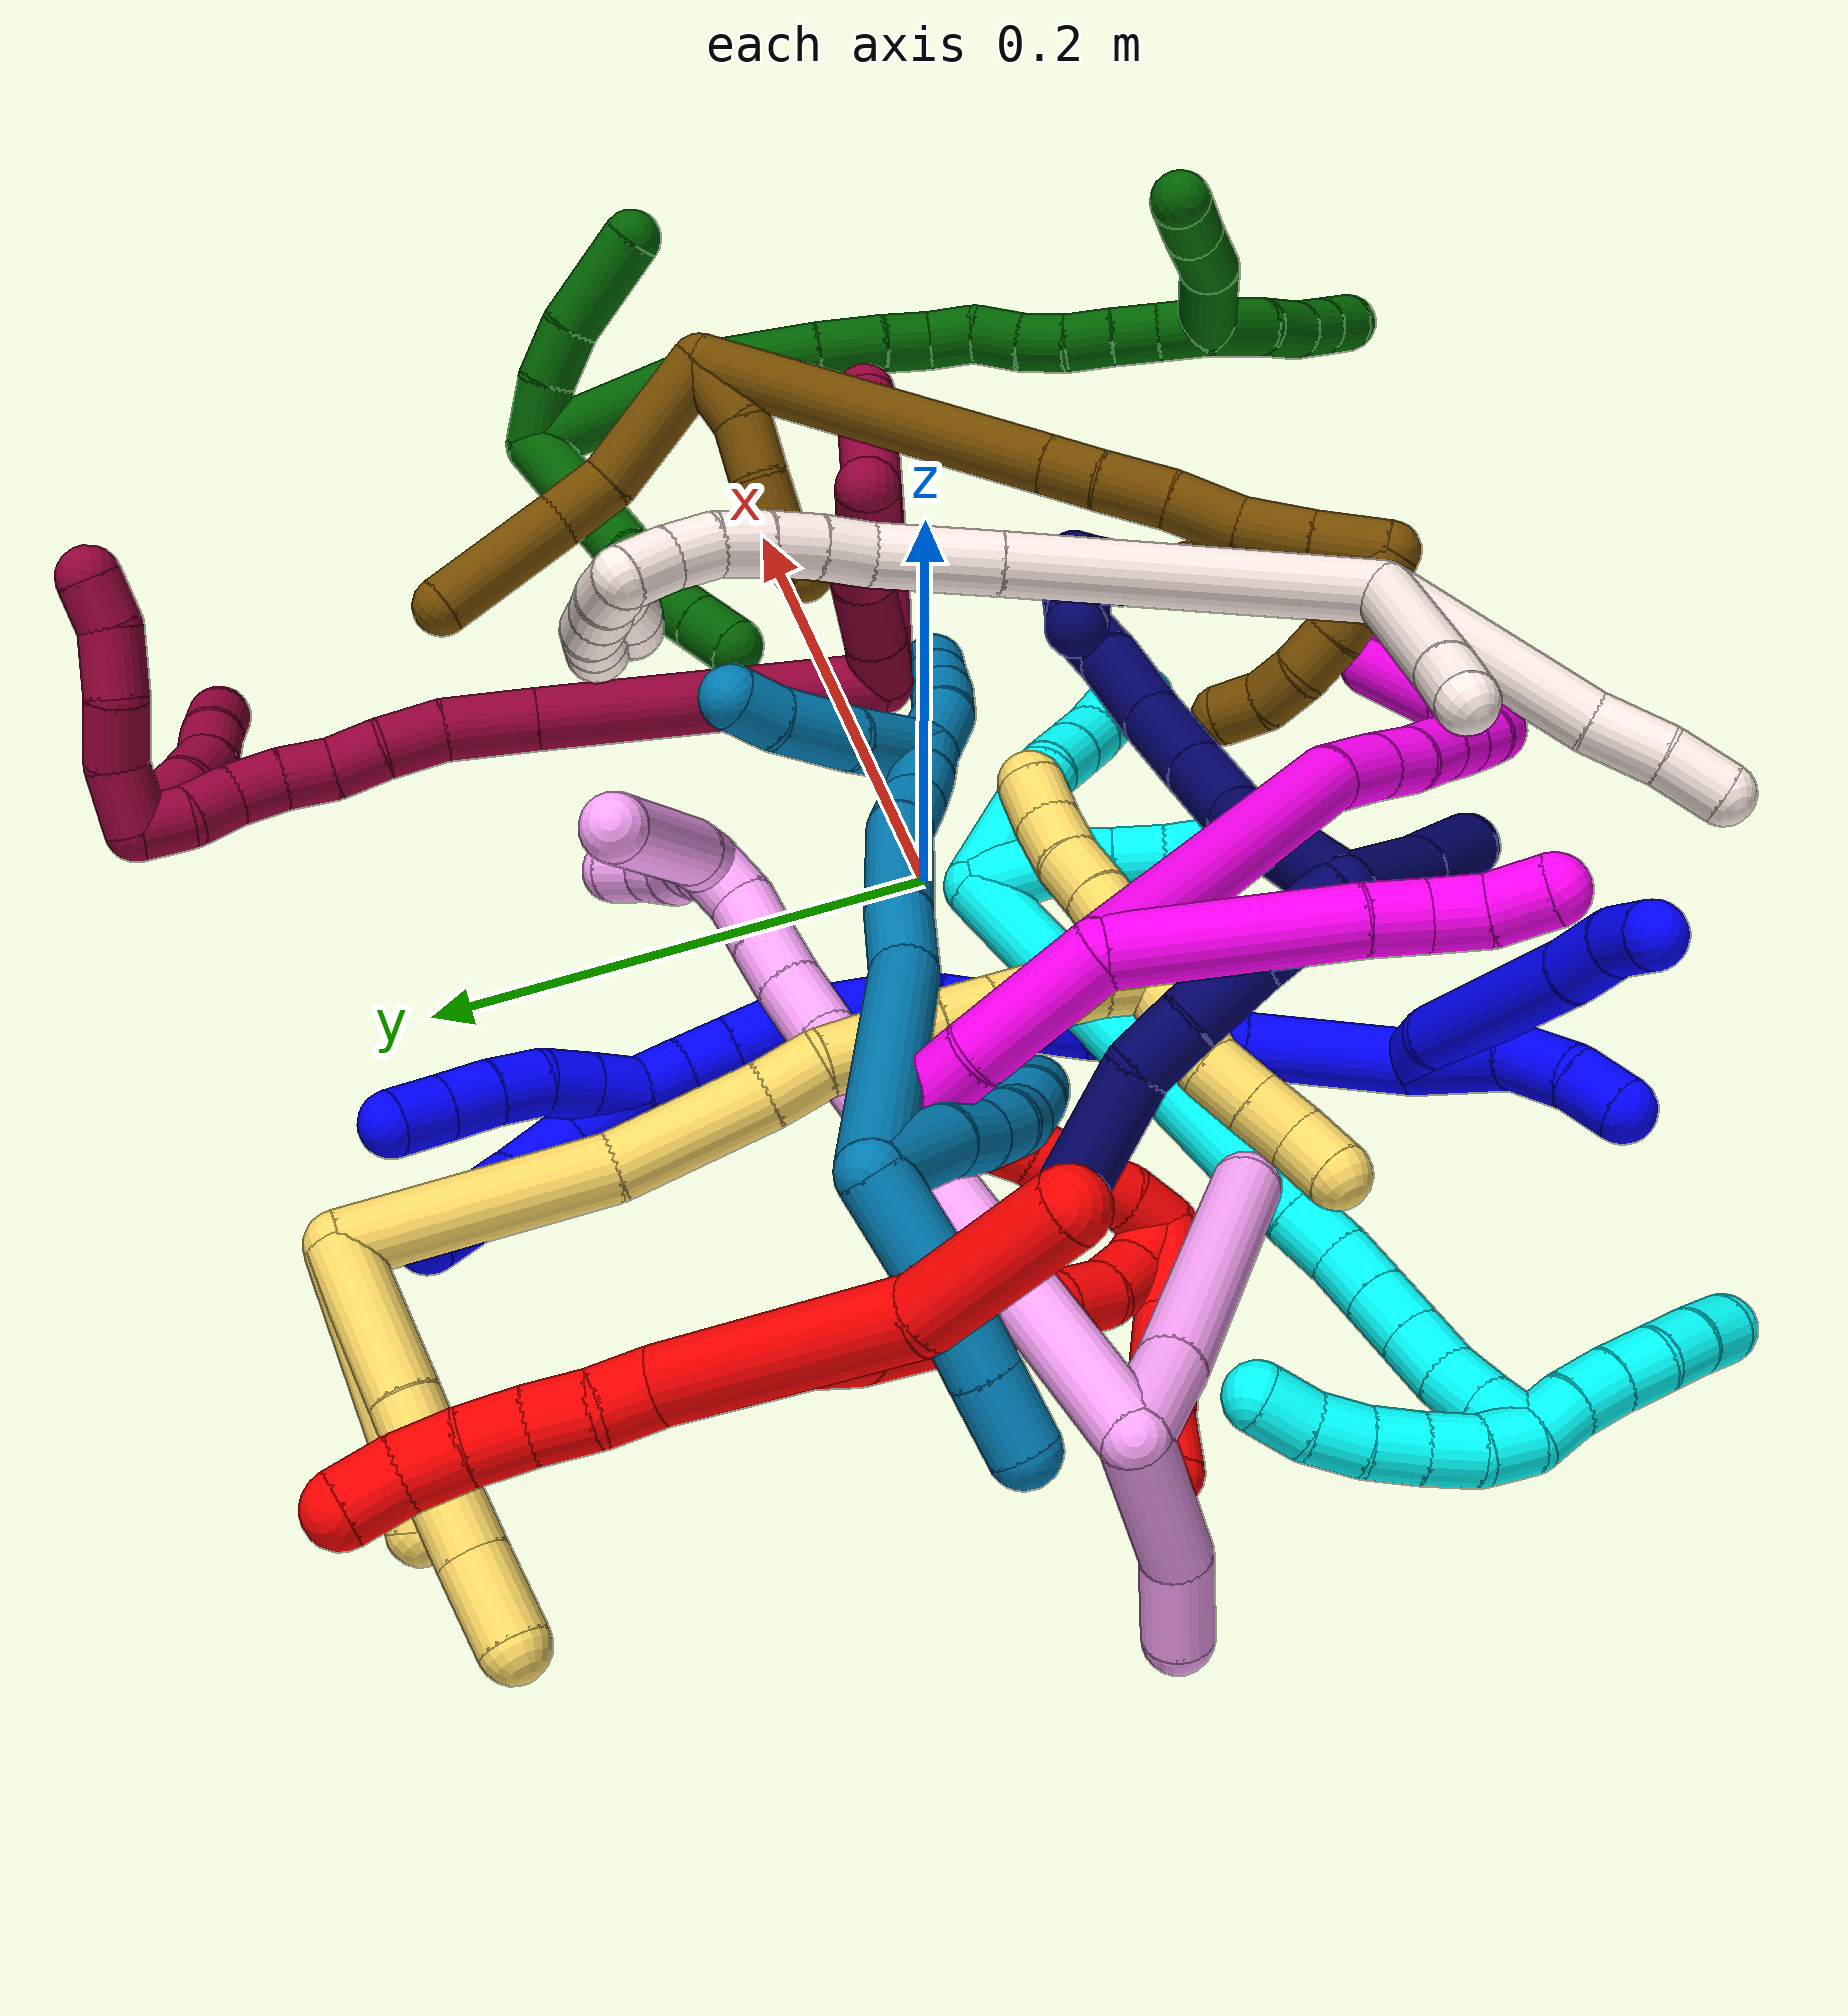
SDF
<sdf version="1.7">
 <world name="default">
  <plugin name="TubeGeneratorPlugin" filename="libtube_generator_plugin.so"/>
  <model name="photoneo_s_sensor">
   <static>1</static>
   <pose>0 0 2 1.57079 1.57079 3.14159</pose>
   <link name="link">
    <inertial><mass>0.1</mass></inertial>
    <sensor name="sensor" type="depth">
     <update_rate>30</update_rate>
     <camera>
      <horizontal_fov>1.22</horizontal_fov>
      <image><width>1920</width><height>1200</height><format>B8G8R8</format></image>
      <clip><near>0.1</near><far>4</far></clip>
      <depth_camera><output>points</output></depth_camera>
     </camera>
     <plugin name="camera_plugin" filename="libgazebo_ros_depth_camera.so">
      <baseline>0.2</baseline>
      <alwaysOn>1</alwaysOn>
      <updateRate>0.0</updateRate>
      <cameraName>camera_ir</cameraName>
      <imageTopicName>/camera/color/image_raw</imageTopicName>
      <cameraInfoTopicName>/camera/color/camera_info</cameraInfoTopicName>
      <depthImageTopicName>/camera/depth/image_raw</depthImageTopicName>
      <depthImageCameraInfoTopicName>/camera/depth/camera_info</depthImageCameraInfoTopicName>
      <pointCloudTopicName>/camera/depth/points</pointCloudTopicName>
      <frameName>fr_optical</frameName>
      <pointCloudCutoff>0.1</pointCloudCutoff>
      <pointCloudCutoffMax>2.0</pointCloudCutoffMax>
      <distortionK1>0</distortionK1>
      <distortionK2>0</distortionK2>
      <distortionK3>0</distortionK3>
      <distortionT1>0</distortionT1>
      <distortionT2>0</distortionT2>
      <CxPrime>0</CxPrime>
      <Cx>0</Cx>
      <Cy>0</Cy>
      <focalLength>0</focalLength>
      <hackBaseline>0</hackBaseline>
     </plugin>
    </sensor>
   </link>
  </model>
  <gravity>0 0 -9.8</gravity>
  <magnetic_field>6e-06 2.3e-05 -4.2e-05</magnetic_field>
  <atmosphere type="adiabatic"/>
  <physics name="default_physics" default="0" type="ode">
   <max_step_size>0.003</max_step_size>
   <real_time_factor>1</real_time_factor>
   <real_time_update_rate>1000</real_time_update_rate>
   <max_contacts>10000</max_contacts>
   <ode>
    <solver>
     <type>quick</type>
     <iters>100</iters>
     <sor>1.3</sor>
     <use_dynamic_moi_rescaling>0</use_dynamic_moi_rescaling>
    </solver>
    <constraints>
     <contact_max_correcting_vel>0</contact_max_correcting_vel>
     <contact_surface_layer>0.001</contact_surface_layer>
     <cfm>0</cfm>
     <erp>0.2</erp>
    </constraints>
   </ode>
  </physics>
  <scene><ambient>0.4 0.4 0.4 1</ambient><background>0.7 0.7 0.7 1</background><shadows>0</shadows></scene>
  <audio><device>default</device></audio>
  <spherical_coordinates>
   <surface_model>EARTH_WGS84</surface_model>
   <latitude_deg>0</latitude_deg>
   <longitude_deg>0</longitude_deg>
   <elevation>0</elevation>
   <heading_deg>0</heading_deg>
  </spherical_coordinates>
  <model name="bin">
   <static>1</static>
   <link name="bottom">
    <collision name="collision-bottom">
     <pose>0 0 -0.01 0 -0 0</pose>
     <geometry><box><size>0.8 0.6 0.02</size></box></geometry>
     <surface>
      <friction><ode><mu>100</mu><mu2>100</mu2></ode></friction>
      <contact><collide_bitmask>65535</collide_bitmask></contact>
     </surface>
    </collision>
   </link>
   <link name="west_wall">
    <collision name="collision-west_wall">
     <pose>-0.41 0 0.1 0 -0 0</pose>
     <geometry><box><size>0.02 0.6 0.2</size></box></geometry>
     <surface>
      <friction><ode><mu>100</mu><mu2>100</mu2></ode></friction>
      <contact><collide_bitmask>65535</collide_bitmask></contact>
     </surface>
    </collision>
   </link>
   <link name="east_wall">
    <collision name="collision-east_wall">
     <pose>0.41 0 0.1 0 -0 0</pose>
     <geometry><box><size>0.02 0.6 0.2</size></box></geometry>
     <surface>
      <friction><ode><mu>100</mu><mu2>100</mu2></ode></friction>
      <contact><collide_bitmask>65535</collide_bitmask></contact>
     </surface>
    </collision>
   </link>
   <link name="south_wall">
    <collision name="collision-south_wall">
     <pose>0 -0.31 0.1 0 -0 0</pose>
     <geometry><box><size>0.8 0.02 0.2</size></box></geometry>
     <surface>
      <friction><ode><mu>100</mu><mu2>100</mu2></ode></friction>
      <contact><collide_bitmask>65535</collide_bitmask></contact>
     </surface>
    </collision>
   </link>
   <link name="north_wall">
    <collision name="collision-north_wall">
     <pose>0 0.31 0.1 0 -0 0</pose>
     <geometry><box><size>0.8 0.02 0.2</size></box></geometry>
     <surface>
      <friction><ode><mu>100</mu><mu2>100</mu2></ode></friction>
      <contact><collide_bitmask>65535</collide_bitmask></contact>
     </surface>
    </collision>
   </link>
  </model>
  <model name="1">
   <static>0</static>
   <link name="1">
    <collision name="collision-cylinder-e_1_2_8">
     <pose>0.00471 -0.006912 -0.008269 2.44536 0.412019 1.04496</pose>
     <geometry><cylinder><radius>0.0125</radius><length>0.023524</length></cylinder></geometry>
     <surface>
      <friction><ode><mu>1.16</mu><mu2>1.16</mu2><slip1>0</slip1><slip2>0</slip2></ode></friction>
      <contact><ode><kp>1e+06</kp><kd>1</kd><max_vel>0</max_vel><min_depth>0.001</min_depth></ode></contact>
     </surface>
    </collision>
    <visual name="visual-cylinder-e_1_2_8">
     <pose>0.00471 -0.006912 -0.008269 2.44536 0.412019 1.04496</pose>
     <geometry><cylinder><radius>0.0125</radius><length>0.023524</length></cylinder></geometry>
     <material><ambient>0 0 1 1</ambient></material>
    </visual>
    <collision name="collision-cylinder-e_2_8_9">
     <pose>0.029758 -0.042729 -0.035088 2.14136 0.534631 0.929176</pose>
     <geometry><cylinder><radius>0.0125</radius><length>0.079831</length></cylinder></geometry>
     <surface>
      <friction><ode><mu>1.16</mu><mu2>1.16</mu2><slip1>0</slip1><slip2>0</slip2></ode></friction>
      <contact><ode><kp>1e+06</kp><kd>1</kd><max_vel>0</max_vel><min_depth>0.001</min_depth></ode></contact>
     </surface>
    </collision>
    <visual name="visual-cylinder-e_2_8_9">
     <pose>0.029758 -0.042729 -0.035088 2.14136 0.534631 0.929176</pose>
     <geometry><cylinder><radius>0.0125</radius><length>0.079831</length></cylinder></geometry>
     <material><ambient>0 0 1 1</ambient></material>
    </visual>
    <collision name="collision-cylinder-e_3_9_10">
     <pose>0.055507 -0.081052 -0.059946 2.16093 0.445341 0.802323</pose>
     <geometry><cylinder><radius>0.0125</radius><length>0.025121</length></cylinder></geometry>
     <surface>
      <friction><ode><mu>1.16</mu><mu2>1.16</mu2><slip1>0</slip1><slip2>0</slip2></ode></friction>
      <contact><ode><kp>1e+06</kp><kd>1</kd><max_vel>0</max_vel><min_depth>0.001</min_depth></ode></contact>
     </surface>
    </collision>
    <visual name="visual-cylinder-e_3_9_10">
     <pose>0.055507 -0.081052 -0.059946 2.16093 0.445341 0.802323</pose>
     <geometry><cylinder><radius>0.0125</radius><length>0.025121</length></cylinder></geometry>
     <material><ambient>0 0 1 1</ambient></material>
    </visual>
    <collision name="collision-cylinder-e_4_10_6">
     <pose>0.068262 -0.096479 -0.071332 2.27247 0.751099 1.40831</pose>
     <geometry><cylinder><radius>0.0125</radius><length>0.021525</length></cylinder></geometry>
     <surface>
      <friction><ode><mu>1.16</mu><mu2>1.16</mu2><slip1>0</slip1><slip2>0</slip2></ode></friction>
      <contact><ode><kp>1e+06</kp><kd>1</kd><max_vel>0</max_vel><min_depth>0.001</min_depth></ode></contact>
     </surface>
    </collision>
    <visual name="visual-cylinder-e_4_10_6">
     <pose>0.068262 -0.096479 -0.071332 2.27247 0.751099 1.40831</pose>
     <geometry><cylinder><radius>0.0125</radius><length>0.021525</length></cylinder></geometry>
     <material><ambient>0 0 1 1</ambient></material>
    </visual>
    <collision name="collision-cylinder-e_1_2_11">
     <pose>0.017382 -0.016895 -0.006401 1.93294 0.766095 1.05649</pose>
     <geometry><cylinder><radius>0.0125</radius><length>0.050142</length></cylinder></geometry>
     <surface>
      <friction><ode><mu>1.16</mu><mu2>1.16</mu2><slip1>0</slip1><slip2>0</slip2></ode></friction>
      <contact><ode><kp>1e+06</kp><kd>1</kd><max_vel>0</max_vel><min_depth>0.001</min_depth></ode></contact>
     </surface>
    </collision>
    <visual name="visual-cylinder-e_1_2_11">
     <pose>0.017382 -0.016895 -0.006401 1.93294 0.766095 1.05649</pose>
     <geometry><cylinder><radius>0.0125</radius><length>0.050142</length></cylinder></geometry>
     <material><ambient>0 0 1 1</ambient></material>
    </visual>
    <collision name="collision-cylinder-e_2_11_12">
     <pose>0.046985 -0.04078 -0.013402 1.65643 1.0496 1.12549</pose>
     <geometry><cylinder><radius>0.0125</radius><length>0.028183</length></cylinder></geometry>
     <surface>
      <friction><ode><mu>1.16</mu><mu2>1.16</mu2><slip1>0</slip1><slip2>0</slip2></ode></friction>
      <contact><ode><kp>1e+06</kp><kd>1</kd><max_vel>0</max_vel><min_depth>0.001</min_depth></ode></contact>
     </surface>
    </collision>
    <visual name="visual-cylinder-e_2_11_12">
     <pose>0.046985 -0.04078 -0.013402 1.65643 1.0496 1.12549</pose>
     <geometry><cylinder><radius>0.0125</radius><length>0.028183</length></cylinder></geometry>
     <material><ambient>0 0 1 1</ambient></material>
    </visual>
    <collision name="collision-cylinder-e_3_12_5">
     <pose>0.069131 -0.05138 -0.01157 0.977892 1.15763 0.669198</pose>
     <geometry><cylinder><radius>0.0125</radius><length>0.021675</length></cylinder></geometry>
     <surface>
      <friction><ode><mu>1.16</mu><mu2>1.16</mu2><slip1>0</slip1><slip2>0</slip2></ode></friction>
      <contact><ode><kp>1e+06</kp><kd>1</kd><max_vel>0</max_vel><min_depth>0.001</min_depth></ode></contact>
     </surface>
    </collision>
    <visual name="visual-cylinder-e_3_12_5">
     <pose>0.069131 -0.05138 -0.01157 0.977892 1.15763 0.669198</pose>
     <geometry><cylinder><radius>0.0125</radius><length>0.021675</length></cylinder></geometry>
     <material><ambient>0 0 1 1</ambient></material>
    </visual>
    <collision name="collision-cylinder-e_1_2_13">
     <pose>-0.0145 0.022646 -0.015911 -2.18326 -0.482597 0.884714</pose>
     <geometry><cylinder><radius>0.0125</radius><length>0.06249</length></cylinder></geometry>
     <surface>
      <friction><ode><mu>1.16</mu><mu2>1.16</mu2><slip1>0</slip1><slip2>0</slip2></ode></friction>
      <contact><ode><kp>1e+06</kp><kd>1</kd><max_vel>0</max_vel><min_depth>0.001</min_depth></ode></contact>
     </surface>
    </collision>
    <visual name="visual-cylinder-e_1_2_13">
     <pose>-0.0145 0.022646 -0.015911 -2.18326 -0.482597 0.884714</pose>
     <geometry><cylinder><radius>0.0125</radius><length>0.06249</length></cylinder></geometry>
     <material><ambient>0 0 1 1</ambient></material>
    </visual>
    <collision name="collision-cylinder-e_2_13_14">
     <pose>-0.038117 0.058234 -0.04212 -2.24292 -0.503766 0.980422</pose>
     <geometry><cylinder><radius>0.0125</radius><length>0.037771</length></cylinder></geometry>
     <surface>
      <friction><ode><mu>1.16</mu><mu2>1.16</mu2><slip1>0</slip1><slip2>0</slip2></ode></friction>
      <contact><ode><kp>1e+06</kp><kd>1</kd><max_vel>0</max_vel><min_depth>0.001</min_depth></ode></contact>
     </surface>
    </collision>
    <visual name="visual-cylinder-e_2_13_14">
     <pose>-0.038117 0.058234 -0.04212 -2.24292 -0.503766 0.980422</pose>
     <geometry><cylinder><radius>0.0125</radius><length>0.037771</length></cylinder></geometry>
     <material><ambient>0 0 1 1</ambient></material>
    </visual>
    <collision name="collision-cylinder-e_3_14_15">
     <pose>-0.051671 0.079297 -0.057842 -2.15967 -0.426482 0.769653</pose>
     <geometry><cylinder><radius>0.0125</radius><length>0.021454</length></cylinder></geometry>
     <surface>
      <friction><ode><mu>1.16</mu><mu2>1.16</mu2><slip1>0</slip1><slip2>0</slip2></ode></friction>
      <contact><ode><kp>1e+06</kp><kd>1</kd><max_vel>0</max_vel><min_depth>0.001</min_depth></ode></contact>
     </surface>
    </collision>
    <visual name="visual-cylinder-e_3_14_15">
     <pose>-0.051671 0.079297 -0.057842 -2.15967 -0.426482 0.769653</pose>
     <geometry><cylinder><radius>0.0125</radius><length>0.021454</length></cylinder></geometry>
     <material><ambient>0 0 1 1</ambient></material>
    </visual>
    <collision name="collision-cylinder-e_4_15_16">
     <pose>-0.068743 0.107046 -0.079519 -2.26239 -0.460285 0.92439</pose>
     <geometry><cylinder><radius>0.0125</radius><length>0.056886</length></cylinder></geometry>
     <surface>
      <friction><ode><mu>1.16</mu><mu2>1.16</mu2><slip1>0</slip1><slip2>0</slip2></ode></friction>
      <contact><ode><kp>1e+06</kp><kd>1</kd><max_vel>0</max_vel><min_depth>0.001</min_depth></ode></contact>
     </surface>
    </collision>
    <visual name="visual-cylinder-e_4_15_16">
     <pose>-0.068743 0.107046 -0.079519 -2.26239 -0.460285 0.92439</pose>
     <geometry><cylinder><radius>0.0125</radius><length>0.056886</length></cylinder></geometry>
     <material><ambient>0 0 1 1</ambient></material>
    </visual>
    <collision name="collision-cylinder-e_5_16_17">
     <pose>-0.084114 0.134506 -0.101793 -2.22626 -0.27024 0.538611</pose>
     <geometry><cylinder><radius>0.0125</radius><length>0.020504</length></cylinder></geometry>
     <surface>
      <friction><ode><mu>1.16</mu><mu2>1.16</mu2><slip1>0</slip1><slip2>0</slip2></ode></friction>
      <contact><ode><kp>1e+06</kp><kd>1</kd><max_vel>0</max_vel><min_depth>0.001</min_depth></ode></contact>
     </surface>
    </collision>
    <visual name="visual-cylinder-e_5_16_17">
     <pose>-0.084114 0.134506 -0.101793 -2.22626 -0.27024 0.538611</pose>
     <geometry><cylinder><radius>0.0125</radius><length>0.020504</length></cylinder></geometry>
     <material><ambient>0 0 1 1</ambient></material>
    </visual>
    <collision name="collision-cylinder-e_6_17_18">
     <pose>-0.088444 0.15082 -0.113113 -2.12917 -0.157956 0.283595</pose>
     <geometry><cylinder><radius>0.0125</radius><length>0.020252</length></cylinder></geometry>
     <surface>
      <friction><ode><mu>1.16</mu><mu2>1.16</mu2><slip1>0</slip1><slip2>0</slip2></ode></friction>
      <contact><ode><kp>1e+06</kp><kd>1</kd><max_vel>0</max_vel><min_depth>0.001</min_depth></ode></contact>
     </surface>
    </collision>
    <visual name="visual-cylinder-e_6_17_18">
     <pose>-0.088444 0.15082 -0.113113 -2.12917 -0.157956 0.283595</pose>
     <geometry><cylinder><radius>0.0125</radius><length>0.020252</length></cylinder></geometry>
     <material><ambient>0 0 1 1</ambient></material>
    </visual>
    <collision name="collision-cylinder-e_7_18_19">
     <pose>-0.091115 0.167869 -0.123883 -2.13916 -0.105712 0.19253</pose>
     <geometry><cylinder><radius>0.0125</radius><length>0.020447</length></cylinder></geometry>
     <surface>
      <friction><ode><mu>1.16</mu><mu2>1.16</mu2><slip1>0</slip1><slip2>0</slip2></ode></friction>
      <contact><ode><kp>1e+06</kp><kd>1</kd><max_vel>0</max_vel><min_depth>0.001</min_depth></ode></contact>
     </surface>
    </collision>
    <visual name="visual-cylinder-e_7_18_19">
     <pose>-0.091115 0.167869 -0.123883 -2.13916 -0.105712 0.19253</pose>
     <geometry><cylinder><radius>0.0125</radius><length>0.020447</length></cylinder></geometry>
     <material><ambient>0 0 1 1</ambient></material>
    </visual>
    <collision name="collision-cylinder-e_8_19_20">
     <pose>-0.091155 0.185362 -0.133894 -2.04128 0.103412 -0.168361</pose>
     <geometry><cylinder><radius>0.0125</radius><length>0.020133</length></cylinder></geometry>
     <surface>
      <friction><ode><mu>1.16</mu><mu2>1.16</mu2><slip1>0</slip1><slip2>0</slip2></ode></friction>
      <contact><ode><kp>1e+06</kp><kd>1</kd><max_vel>0</max_vel><min_depth>0.001</min_depth></ode></contact>
     </surface>
    </collision>
    <visual name="visual-cylinder-e_8_19_20">
     <pose>-0.091155 0.185362 -0.133894 -2.04128 0.103412 -0.168361</pose>
     <geometry><cylinder><radius>0.0125</radius><length>0.020133</length></cylinder></geometry>
     <material><ambient>0 0 1 1</ambient></material>
    </visual>
    <collision name="collision-cylinder-e_9_20_21">
     <pose>-0.08911 0.20317 -0.142945 -2.04071 0.100601 -0.163694</pose>
     <geometry><cylinder><radius>0.0125</radius><length>0.020028</length></cylinder></geometry>
     <surface>
      <friction><ode><mu>1.16</mu><mu2>1.16</mu2><slip1>0</slip1><slip2>0</slip2></ode></friction>
      <contact><ode><kp>1e+06</kp><kd>1</kd><max_vel>0</max_vel><min_depth>0.001</min_depth></ode></contact>
     </surface>
    </collision>
    <visual name="visual-cylinder-e_9_20_21">
     <pose>-0.08911 0.20317 -0.142945 -2.04071 0.100601 -0.163694</pose>
     <geometry><cylinder><radius>0.0125</radius><length>0.020028</length></cylinder></geometry>
     <material><ambient>0 0 1 1</ambient></material>
    </visual>
    <collision name="collision-cylinder-e_10_21_1">
     <pose>-0.085389 0.219758 -0.153255 -2.21601 0.274542 -0.540211</pose>
     <geometry><cylinder><radius>0.0125</radius><length>0.020035</length></cylinder></geometry>
     <surface>
      <friction><ode><mu>1.16</mu><mu2>1.16</mu2><slip1>0</slip1><slip2>0</slip2></ode></friction>
      <contact><ode><kp>1e+06</kp><kd>1</kd><max_vel>0</max_vel><min_depth>0.001</min_depth></ode></contact>
     </surface>
    </collision>
    <visual name="visual-cylinder-e_10_21_1">
     <pose>-0.085389 0.219758 -0.153255 -2.21601 0.274542 -0.540211</pose>
     <geometry><cylinder><radius>0.0125</radius><length>0.020035</length></cylinder></geometry>
     <material><ambient>0 0 1 1</ambient></material>
    </visual>
    <collision name="collision-cylinder-e_1_1_22">
     <pose>-0.082928 0.232431 -0.167728 -2.62138 -0.025488 0.095702</pose>
     <geometry><cylinder><radius>0.0125</radius><length>0.02</length></cylinder></geometry>
     <surface>
      <friction><ode><mu>1.16</mu><mu2>1.16</mu2><slip1>0</slip1><slip2>0</slip2></ode></friction>
      <contact><ode><kp>1e+06</kp><kd>1</kd><max_vel>0</max_vel><min_depth>0.001</min_depth></ode></contact>
     </surface>
    </collision>
    <visual name="visual-cylinder-e_1_1_22">
     <pose>-0.082928 0.232431 -0.167728 -2.62138 -0.025488 0.095702</pose>
     <geometry><cylinder><radius>0.0125</radius><length>0.02</length></cylinder></geometry>
     <material><ambient>0 0 1 1</ambient></material>
    </visual>
    <collision name="collision-cylinder-e_2_22_23">
     <pose>-0.082748 0.242117 -0.185209 -2.64981 0.043486 -0.172869</pose>
     <geometry><cylinder><radius>0.0125</radius><length>0.02</length></cylinder></geometry>
     <surface>
      <friction><ode><mu>1.16</mu><mu2>1.16</mu2><slip1>0</slip1><slip2>0</slip2></ode></friction>
      <contact><ode><kp>1e+06</kp><kd>1</kd><max_vel>0</max_vel><min_depth>0.001</min_depth></ode></contact>
     </surface>
    </collision>
    <visual name="visual-cylinder-e_2_22_23">
     <pose>-0.082748 0.242117 -0.185209 -2.64981 0.043486 -0.172869</pose>
     <geometry><cylinder><radius>0.0125</radius><length>0.02</length></cylinder></geometry>
     <material><ambient>0 0 1 1</ambient></material>
    </visual>
    <collision name="collision-cylinder-e_3_23_24">
     <pose>-0.080746 0.253515 -0.20129 -2.39873 0.157324 -0.399345</pose>
     <geometry><cylinder><radius>0.0125</radius><length>0.02</length></cylinder></geometry>
     <surface>
      <friction><ode><mu>1.16</mu><mu2>1.16</mu2><slip1>0</slip1><slip2>0</slip2></ode></friction>
      <contact><ode><kp>1e+06</kp><kd>1</kd><max_vel>0</max_vel><min_depth>0.001</min_depth></ode></contact>
     </surface>
    </collision>
    <visual name="visual-cylinder-e_3_23_24">
     <pose>-0.080746 0.253515 -0.20129 -2.39873 0.157324 -0.399345</pose>
     <geometry><cylinder><radius>0.0125</radius><length>0.02</length></cylinder></geometry>
     <material><ambient>0 0 1 1</ambient></material>
    </visual>
    <collision name="collision-cylinder-e_4_24_25">
     <pose>-0.076955 0.267236 -0.215308 -2.33469 0.224355 -0.516034</pose>
     <geometry><cylinder><radius>0.0125</radius><length>0.02</length></cylinder></geometry>
     <surface>
      <friction><ode><mu>1.16</mu><mu2>1.16</mu2><slip1>0</slip1><slip2>0</slip2></ode></friction>
      <contact><ode><kp>1e+06</kp><kd>1</kd><max_vel>0</max_vel><min_depth>0.001</min_depth></ode></contact>
     </surface>
    </collision>
    <visual name="visual-cylinder-e_4_24_25">
     <pose>-0.076955 0.267236 -0.215308 -2.33469 0.224355 -0.516034</pose>
     <geometry><cylinder><radius>0.0125</radius><length>0.02</length></cylinder></geometry>
     <material><ambient>0 0 1 1</ambient></material>
    </visual>
    <collision name="collision-cylinder-e_5_25_4">
     <pose>-0.072492 0.281158 -0.228954 -2.35769 0.225707 -0.535235</pose>
     <geometry><cylinder><radius>0.0125</radius><length>0.02</length></cylinder></geometry>
     <surface>
      <friction><ode><mu>1.16</mu><mu2>1.16</mu2><slip1>0</slip1><slip2>0</slip2></ode></friction>
      <contact><ode><kp>1e+06</kp><kd>1</kd><max_vel>0</max_vel><min_depth>0.001</min_depth></ode></contact>
     </surface>
    </collision>
    <visual name="visual-cylinder-e_5_25_4">
     <pose>-0.072492 0.281158 -0.228954 -2.35769 0.225707 -0.535235</pose>
     <geometry><cylinder><radius>0.0125</radius><length>0.02</length></cylinder></geometry>
     <material><ambient>0 0 1 1</ambient></material>
    </visual>
    <collision name="collision-cylinder-e_1_1_26">
     <pose>-0.079023 0.24082 -0.163579 -1.89739 0.253211 -0.351352</pose>
     <geometry><cylinder><radius>0.0125</radius><length>0.029138</length></cylinder></geometry>
     <surface>
      <friction><ode><mu>1.16</mu><mu2>1.16</mu2><slip1>0</slip1><slip2>0</slip2></ode></friction>
      <contact><ode><kp>1e+06</kp><kd>1</kd><max_vel>0</max_vel><min_depth>0.001</min_depth></ode></contact>
     </surface>
    </collision>
    <visual name="visual-cylinder-e_1_1_26">
     <pose>-0.079023 0.24082 -0.163579 -1.89739 0.253211 -0.351352</pose>
     <geometry><cylinder><radius>0.0125</radius><length>0.029138</length></cylinder></geometry>
     <material><ambient>0 0 1 1</ambient></material>
    </visual>
    <collision name="collision-cylinder-e_2_26_27">
     <pose>-0.068991 0.265261 -0.175125 -2.13557 0.452809 -0.792974</pose>
     <geometry><cylinder><radius>0.0125</radius><length>0.029178</length></cylinder></geometry>
     <surface>
      <friction><ode><mu>1.16</mu><mu2>1.16</mu2><slip1>0</slip1><slip2>0</slip2></ode></friction>
      <contact><ode><kp>1e+06</kp><kd>1</kd><max_vel>0</max_vel><min_depth>0.001</min_depth></ode></contact>
     </surface>
    </collision>
    <visual name="visual-cylinder-e_2_26_27">
     <pose>-0.068991 0.265261 -0.175125 -2.13557 0.452809 -0.792974</pose>
     <geometry><cylinder><radius>0.0125</radius><length>0.029178</length></cylinder></geometry>
     <material><ambient>0 0 1 1</ambient></material>
    </visual>
    <collision name="collision-cylinder-e_3_27_3">
     <pose>-0.052977 0.290779 -0.193688 -2.24519 0.480359 -0.942177</pose>
     <geometry><cylinder><radius>0.0125</radius><length>0.041684</length></cylinder></geometry>
     <surface>
      <friction><ode><mu>1.16</mu><mu2>1.16</mu2><slip1>0</slip1><slip2>0</slip2></ode></friction>
      <contact><ode><kp>1e+06</kp><kd>1</kd><max_vel>0</max_vel><min_depth>0.001</min_depth></ode></contact>
     </surface>
    </collision>
    <visual name="visual-cylinder-e_3_27_3">
     <pose>-0.052977 0.290779 -0.193688 -2.24519 0.480359 -0.942177</pose>
     <geometry><cylinder><radius>0.0125</radius><length>0.041684</length></cylinder></geometry>
     <material><ambient>0 0 1 1</ambient></material>
    </visual>
    <collision name="collision-sphere-3">
     <pose>-0.043346 0.305216 -0.20523 0 -0 0</pose>
     <geometry><sphere><radius>0.0125</radius></sphere></geometry>
     <surface>
      <friction><ode><mu>1.16</mu><mu2>1.16</mu2><slip1>0</slip1><slip2>0</slip2></ode></friction>
      <contact><ode><kp>1e+06</kp><kd>1</kd><max_vel>0</max_vel><min_depth>0.001</min_depth></ode></contact>
     </surface>
    </collision>
    <visual name="visual-sphere-3">
     <pose>-0.043346 0.305216 -0.20523 0 -0 0</pose>
     <geometry><sphere><radius>0.0125</radius></sphere></geometry>
     <material><ambient>0 0 1 1</ambient></material>
    </visual>
    <collision name="collision-sphere-27">
     <pose>-0.062608 0.276342 -0.182147 0 -0 0</pose>
     <geometry><sphere><radius>0.0125</radius></sphere></geometry>
     <surface>
      <friction><ode><mu>1.16</mu><mu2>1.16</mu2><slip1>0</slip1><slip2>0</slip2></ode></friction>
      <contact><ode><kp>1e+06</kp><kd>1</kd><max_vel>0</max_vel><min_depth>0.001</min_depth></ode></contact>
     </surface>
    </collision>
    <visual name="visual-sphere-27">
     <pose>-0.062608 0.276342 -0.182147 0 -0 0</pose>
     <geometry><sphere><radius>0.0125</radius></sphere></geometry>
     <material><ambient>0 0 1 1</ambient></material>
    </visual>
    <collision name="collision-sphere-26">
     <pose>-0.075373 0.254179 -0.168103 0 -0 0</pose>
     <geometry><sphere><radius>0.0125</radius></sphere></geometry>
     <surface>
      <friction><ode><mu>1.16</mu><mu2>1.16</mu2><slip1>0</slip1><slip2>0</slip2></ode></friction>
      <contact><ode><kp>1e+06</kp><kd>1</kd><max_vel>0</max_vel><min_depth>0.001</min_depth></ode></contact>
     </surface>
    </collision>
    <visual name="visual-sphere-26">
     <pose>-0.075373 0.254179 -0.168103 0 -0 0</pose>
     <geometry><sphere><radius>0.0125</radius></sphere></geometry>
     <material><ambient>0 0 1 1</ambient></material>
    </visual>
    <collision name="collision-sphere-4">
     <pose>-0.070254 0.288039 -0.235856 0 -0 0</pose>
     <geometry><sphere><radius>0.0125</radius></sphere></geometry>
     <surface>
      <friction><ode><mu>1.16</mu><mu2>1.16</mu2><slip1>0</slip1><slip2>0</slip2></ode></friction>
      <contact><ode><kp>1e+06</kp><kd>1</kd><max_vel>0</max_vel><min_depth>0.001</min_depth></ode></contact>
     </surface>
    </collision>
    <visual name="visual-sphere-4">
     <pose>-0.070254 0.288039 -0.235856 0 -0 0</pose>
     <geometry><sphere><radius>0.0125</radius></sphere></geometry>
     <material><ambient>0 0 1 1</ambient></material>
    </visual>
    <collision name="collision-sphere-25">
     <pose>-0.07473 0.274277 -0.222052 0 -0 0</pose>
     <geometry><sphere><radius>0.0125</radius></sphere></geometry>
     <surface>
      <friction><ode><mu>1.16</mu><mu2>1.16</mu2><slip1>0</slip1><slip2>0</slip2></ode></friction>
      <contact><ode><kp>1e+06</kp><kd>1</kd><max_vel>0</max_vel><min_depth>0.001</min_depth></ode></contact>
     </surface>
    </collision>
    <visual name="visual-sphere-25">
     <pose>-0.07473 0.274277 -0.222052 0 -0 0</pose>
     <geometry><sphere><radius>0.0125</radius></sphere></geometry>
     <material><ambient>0 0 1 1</ambient></material>
    </visual>
    <collision name="collision-sphere-24">
     <pose>-0.079179 0.260195 -0.208564 0 -0 0</pose>
     <geometry><sphere><radius>0.0125</radius></sphere></geometry>
     <surface>
      <friction><ode><mu>1.16</mu><mu2>1.16</mu2><slip1>0</slip1><slip2>0</slip2></ode></friction>
      <contact><ode><kp>1e+06</kp><kd>1</kd><max_vel>0</max_vel><min_depth>0.001</min_depth></ode></contact>
     </surface>
    </collision>
    <visual name="visual-sphere-24">
     <pose>-0.079179 0.260195 -0.208564 0 -0 0</pose>
     <geometry><sphere><radius>0.0125</radius></sphere></geometry>
     <material><ambient>0 0 1 1</ambient></material>
    </visual>
    <collision name="collision-sphere-23">
     <pose>-0.082313 0.246835 -0.194015 0 -0 0</pose>
     <geometry><sphere><radius>0.0125</radius></sphere></geometry>
     <surface>
      <friction><ode><mu>1.16</mu><mu2>1.16</mu2><slip1>0</slip1><slip2>0</slip2></ode></friction>
      <contact><ode><kp>1e+06</kp><kd>1</kd><max_vel>0</max_vel><min_depth>0.001</min_depth></ode></contact>
     </surface>
    </collision>
    <visual name="visual-sphere-23">
     <pose>-0.082313 0.246835 -0.194015 0 -0 0</pose>
     <geometry><sphere><radius>0.0125</radius></sphere></geometry>
     <material><ambient>0 0 1 1</ambient></material>
    </visual>
    <collision name="collision-sphere-22">
     <pose>-0.083182 0.2374 -0.176402 0 -0 0</pose>
     <geometry><sphere><radius>0.0125</radius></sphere></geometry>
     <surface>
      <friction><ode><mu>1.16</mu><mu2>1.16</mu2><slip1>0</slip1><slip2>0</slip2></ode></friction>
      <contact><ode><kp>1e+06</kp><kd>1</kd><max_vel>0</max_vel><min_depth>0.001</min_depth></ode></contact>
     </surface>
    </collision>
    <visual name="visual-sphere-22">
     <pose>-0.083182 0.2374 -0.176402 0 -0 0</pose>
     <geometry><sphere><radius>0.0125</radius></sphere></geometry>
     <material><ambient>0 0 1 1</ambient></material>
    </visual>
    <collision name="collision-sphere-1">
     <pose>-0.082673 0.227462 -0.159054 0 -0 0</pose>
     <geometry><sphere><radius>0.0125</radius></sphere></geometry>
     <surface>
      <friction><ode><mu>1.16</mu><mu2>1.16</mu2><slip1>0</slip1><slip2>0</slip2></ode></friction>
      <contact><ode><kp>1e+06</kp><kd>1</kd><max_vel>0</max_vel><min_depth>0.001</min_depth></ode></contact>
     </surface>
    </collision>
    <visual name="visual-sphere-1">
     <pose>-0.082673 0.227462 -0.159054 0 -0 0</pose>
     <geometry><sphere><radius>0.0125</radius></sphere></geometry>
     <material><ambient>0 0 1 1</ambient></material>
    </visual>
    <collision name="collision-sphere-21">
     <pose>-0.088104 0.212054 -0.147456 0 -0 0</pose>
     <geometry><sphere><radius>0.0125</radius></sphere></geometry>
     <surface>
      <friction><ode><mu>1.16</mu><mu2>1.16</mu2><slip1>0</slip1><slip2>0</slip2></ode></friction>
      <contact><ode><kp>1e+06</kp><kd>1</kd><max_vel>0</max_vel><min_depth>0.001</min_depth></ode></contact>
     </surface>
    </collision>
    <visual name="visual-sphere-21">
     <pose>-0.088104 0.212054 -0.147456 0 -0 0</pose>
     <geometry><sphere><radius>0.0125</radius></sphere></geometry>
     <material><ambient>0 0 1 1</ambient></material>
    </visual>
    <collision name="collision-sphere-11">
     <pose>0.034765 -0.03379 -0.012802 0 -0 0</pose>
     <geometry><sphere><radius>0.0125</radius></sphere></geometry>
     <surface>
      <friction><ode><mu>1.16</mu><mu2>1.16</mu2><slip1>0</slip1><slip2>0</slip2></ode></friction>
      <contact><ode><kp>1e+06</kp><kd>1</kd><max_vel>0</max_vel><min_depth>0.001</min_depth></ode></contact>
     </surface>
    </collision>
    <visual name="visual-sphere-11">
     <pose>0.034765 -0.03379 -0.012802 0 -0 0</pose>
     <geometry><sphere><radius>0.0125</radius></sphere></geometry>
     <material><ambient>0 0 1 1</ambient></material>
    </visual>
    <collision name="collision-sphere-6">
     <pose>0.075607 -0.102487 -0.07641 0 -0 0</pose>
     <geometry><sphere><radius>0.0125</radius></sphere></geometry>
     <surface>
      <friction><ode><mu>1.16</mu><mu2>1.16</mu2><slip1>0</slip1><slip2>0</slip2></ode></friction>
      <contact><ode><kp>1e+06</kp><kd>1</kd><max_vel>0</max_vel><min_depth>0.001</min_depth></ode></contact>
     </surface>
    </collision>
    <visual name="visual-sphere-6">
     <pose>0.075607 -0.102487 -0.07641 0 -0 0</pose>
     <geometry><sphere><radius>0.0125</radius></sphere></geometry>
     <material><ambient>0 0 1 1</ambient></material>
    </visual>
    <collision name="collision-sphere-10">
     <pose>0.060917 -0.09047 -0.066254 0 -0 0</pose>
     <geometry><sphere><radius>0.0125</radius></sphere></geometry>
     <surface>
      <friction><ode><mu>1.16</mu><mu2>1.16</mu2><slip1>0</slip1><slip2>0</slip2></ode></friction>
      <contact><ode><kp>1e+06</kp><kd>1</kd><max_vel>0</max_vel><min_depth>0.001</min_depth></ode></contact>
     </surface>
    </collision>
    <visual name="visual-sphere-10">
     <pose>0.060917 -0.09047 -0.066254 0 -0 0</pose>
     <geometry><sphere><radius>0.0125</radius></sphere></geometry>
     <material><ambient>0 0 1 1</ambient></material>
    </visual>
    <collision name="collision-sphere-9">
     <pose>0.050096 -0.071634 -0.053639 0 -0 0</pose>
     <geometry><sphere><radius>0.0125</radius></sphere></geometry>
     <surface>
      <friction><ode><mu>1.16</mu><mu2>1.16</mu2><slip1>0</slip1><slip2>0</slip2></ode></friction>
      <contact><ode><kp>1e+06</kp><kd>1</kd><max_vel>0</max_vel><min_depth>0.001</min_depth></ode></contact>
     </surface>
    </collision>
    <visual name="visual-sphere-9">
     <pose>0.050096 -0.071634 -0.053639 0 -0 0</pose>
     <geometry><sphere><radius>0.0125</radius></sphere></geometry>
     <material><ambient>0 0 1 1</ambient></material>
    </visual>
    <collision name="collision-sphere-2">
     <geometry><sphere><radius>0.0125</radius></sphere></geometry>
     <surface>
      <friction><ode><mu>1.16</mu><mu2>1.16</mu2><slip1>0</slip1><slip2>0</slip2></ode></friction>
      <contact><ode><kp>1e+06</kp><kd>1</kd><max_vel>0</max_vel><min_depth>0.001</min_depth></ode></contact>
     </surface>
    </collision>
    <visual name="visual-sphere-2">
     <geometry><sphere><radius>0.0125</radius></sphere></geometry>
     <material><ambient>0 0 1 1</ambient></material>
    </visual>
    <collision name="collision-sphere-19">
     <pose>-0.092194 0.176437 -0.129355 0 -0 0</pose>
     <geometry><sphere><radius>0.0125</radius></sphere></geometry>
     <surface>
      <friction><ode><mu>1.16</mu><mu2>1.16</mu2><slip1>0</slip1><slip2>0</slip2></ode></friction>
      <contact><ode><kp>1e+06</kp><kd>1</kd><max_vel>0</max_vel><min_depth>0.001</min_depth></ode></contact>
     </surface>
    </collision>
    <visual name="visual-sphere-19">
     <pose>-0.092194 0.176437 -0.129355 0 -0 0</pose>
     <geometry><sphere><radius>0.0125</radius></sphere></geometry>
     <material><ambient>0 0 1 1</ambient></material>
    </visual>
    <collision name="collision-sphere-8">
     <pose>0.00942 -0.013824 -0.016538 0 -0 0</pose>
     <geometry><sphere><radius>0.0125</radius></sphere></geometry>
     <surface>
      <friction><ode><mu>1.16</mu><mu2>1.16</mu2><slip1>0</slip1><slip2>0</slip2></ode></friction>
      <contact><ode><kp>1e+06</kp><kd>1</kd><max_vel>0</max_vel><min_depth>0.001</min_depth></ode></contact>
     </surface>
    </collision>
    <visual name="visual-sphere-8">
     <pose>0.00942 -0.013824 -0.016538 0 -0 0</pose>
     <geometry><sphere><radius>0.0125</radius></sphere></geometry>
     <material><ambient>0 0 1 1</ambient></material>
    </visual>
    <collision name="collision-sphere-12">
     <pose>0.059206 -0.047771 -0.014002 0 -0 0</pose>
     <geometry><sphere><radius>0.0125</radius></sphere></geometry>
     <surface>
      <friction><ode><mu>1.16</mu><mu2>1.16</mu2><slip1>0</slip1><slip2>0</slip2></ode></friction>
      <contact><ode><kp>1e+06</kp><kd>1</kd><max_vel>0</max_vel><min_depth>0.001</min_depth></ode></contact>
     </surface>
    </collision>
    <visual name="visual-sphere-12">
     <pose>0.059206 -0.047771 -0.014002 0 -0 0</pose>
     <geometry><sphere><radius>0.0125</radius></sphere></geometry>
     <material><ambient>0 0 1 1</ambient></material>
    </visual>
    <collision name="collision-sphere-5">
     <pose>0.079057 -0.054989 -0.009139 0 -0 0</pose>
     <geometry><sphere><radius>0.0125</radius></sphere></geometry>
     <surface>
      <friction><ode><mu>1.16</mu><mu2>1.16</mu2><slip1>0</slip1><slip2>0</slip2></ode></friction>
      <contact><ode><kp>1e+06</kp><kd>1</kd><max_vel>0</max_vel><min_depth>0.001</min_depth></ode></contact>
     </surface>
    </collision>
    <visual name="visual-sphere-5">
     <pose>0.079057 -0.054989 -0.009139 0 -0 0</pose>
     <geometry><sphere><radius>0.0125</radius></sphere></geometry>
     <material><ambient>0 0 1 1</ambient></material>
    </visual>
    <collision name="collision-sphere-13">
     <pose>-0.029 0.045292 -0.031821 0 -0 0</pose>
     <geometry><sphere><radius>0.0125</radius></sphere></geometry>
     <surface>
      <friction><ode><mu>1.16</mu><mu2>1.16</mu2><slip1>0</slip1><slip2>0</slip2></ode></friction>
      <contact><ode><kp>1e+06</kp><kd>1</kd><max_vel>0</max_vel><min_depth>0.001</min_depth></ode></contact>
     </surface>
    </collision>
    <visual name="visual-sphere-13">
     <pose>-0.029 0.045292 -0.031821 0 -0 0</pose>
     <geometry><sphere><radius>0.0125</radius></sphere></geometry>
     <material><ambient>0 0 1 1</ambient></material>
    </visual>
    <collision name="collision-sphere-14">
     <pose>-0.047233 0.071176 -0.052418 0 -0 0</pose>
     <geometry><sphere><radius>0.0125</radius></sphere></geometry>
     <surface>
      <friction><ode><mu>1.16</mu><mu2>1.16</mu2><slip1>0</slip1><slip2>0</slip2></ode></friction>
      <contact><ode><kp>1e+06</kp><kd>1</kd><max_vel>0</max_vel><min_depth>0.001</min_depth></ode></contact>
     </surface>
    </collision>
    <visual name="visual-sphere-14">
     <pose>-0.047233 0.071176 -0.052418 0 -0 0</pose>
     <geometry><sphere><radius>0.0125</radius></sphere></geometry>
     <material><ambient>0 0 1 1</ambient></material>
    </visual>
    <collision name="collision-sphere-15">
     <pose>-0.056108 0.087418 -0.063267 0 -0 0</pose>
     <geometry><sphere><radius>0.0125</radius></sphere></geometry>
     <surface>
      <friction><ode><mu>1.16</mu><mu2>1.16</mu2><slip1>0</slip1><slip2>0</slip2></ode></friction>
      <contact><ode><kp>1e+06</kp><kd>1</kd><max_vel>0</max_vel><min_depth>0.001</min_depth></ode></contact>
     </surface>
    </collision>
    <visual name="visual-sphere-15">
     <pose>-0.056108 0.087418 -0.063267 0 -0 0</pose>
     <geometry><sphere><radius>0.0125</radius></sphere></geometry>
     <material><ambient>0 0 1 1</ambient></material>
    </visual>
    <collision name="collision-sphere-16">
     <pose>-0.081377 0.126674 -0.095771 0 -0 0</pose>
     <geometry><sphere><radius>0.0125</radius></sphere></geometry>
     <surface>
      <friction><ode><mu>1.16</mu><mu2>1.16</mu2><slip1>0</slip1><slip2>0</slip2></ode></friction>
      <contact><ode><kp>1e+06</kp><kd>1</kd><max_vel>0</max_vel><min_depth>0.001</min_depth></ode></contact>
     </surface>
    </collision>
    <visual name="visual-sphere-16">
     <pose>-0.081377 0.126674 -0.095771 0 -0 0</pose>
     <geometry><sphere><radius>0.0125</radius></sphere></geometry>
     <material><ambient>0 0 1 1</ambient></material>
    </visual>
    <collision name="collision-sphere-17">
     <pose>-0.086851 0.142339 -0.107815 0 -0 0</pose>
     <geometry><sphere><radius>0.0125</radius></sphere></geometry>
     <surface>
      <friction><ode><mu>1.16</mu><mu2>1.16</mu2><slip1>0</slip1><slip2>0</slip2></ode></friction>
      <contact><ode><kp>1e+06</kp><kd>1</kd><max_vel>0</max_vel><min_depth>0.001</min_depth></ode></contact>
     </surface>
    </collision>
    <visual name="visual-sphere-17">
     <pose>-0.086851 0.142339 -0.107815 0 -0 0</pose>
     <geometry><sphere><radius>0.0125</radius></sphere></geometry>
     <material><ambient>0 0 1 1</ambient></material>
    </visual>
    <collision name="collision-sphere-18">
     <pose>-0.090037 0.159301 -0.118411 0 -0 0</pose>
     <geometry><sphere><radius>0.0125</radius></sphere></geometry>
     <surface>
      <friction><ode><mu>1.16</mu><mu2>1.16</mu2><slip1>0</slip1><slip2>0</slip2></ode></friction>
      <contact><ode><kp>1e+06</kp><kd>1</kd><max_vel>0</max_vel><min_depth>0.001</min_depth></ode></contact>
     </surface>
    </collision>
    <visual name="visual-sphere-18">
     <pose>-0.090037 0.159301 -0.118411 0 -0 0</pose>
     <geometry><sphere><radius>0.0125</radius></sphere></geometry>
     <material><ambient>0 0 1 1</ambient></material>
    </visual>
    <collision name="collision-sphere-20">
     <pose>-0.090116 0.194287 -0.138433 0 -0 0</pose>
     <geometry><sphere><radius>0.0125</radius></sphere></geometry>
     <surface>
      <friction><ode><mu>1.16</mu><mu2>1.16</mu2><slip1>0</slip1><slip2>0</slip2></ode></friction>
      <contact><ode><kp>1e+06</kp><kd>1</kd><max_vel>0</max_vel><min_depth>0.001</min_depth></ode></contact>
     </surface>
    </collision>
    <visual name="visual-sphere-20">
     <pose>-0.090116 0.194287 -0.138433 0 -0 0</pose>
     <geometry><sphere><radius>0.0125</radius></sphere></geometry>
     <material><ambient>0 0 1 1</ambient></material>
    </visual>
    <inertial>
     <pose>-0.031295 0.099286 -0.091728 0 -0 0</pose>
     <mass>0.75</mass>
     <inertia><ixx>0.00016</ixx><ixy>0</ixy><ixz>0</ixz><iyy>8e-05</iyy><iyz>0</iyz><izz>-6.1e-05</izz></inertia>
    </inertial>
   </link>
   <pose>-0.153682 -0.138842 0.011964 -2.58722 -0.126476 -3.13491</pose>
  </model>
  <model name="2">
   <static>0</static>
   <link name="2">
    <collision name="collision-cylinder-e_1_2_8">
     <pose>-0.014595 -0.043902 0.006826 1.41656 -0.317401 -0.272475</pose>
     <geometry><cylinder><radius>0.0125</radius><length>0.093531</length></cylinder></geometry>
     <surface>
      <friction><ode><mu>1.16</mu><mu2>1.16</mu2><slip1>0</slip1><slip2>0</slip2></ode></friction>
      <contact><ode><kp>1e+06</kp><kd>1</kd><max_vel>0</max_vel><min_depth>0.001</min_depth></ode></contact>
     </surface>
    </collision>
    <visual name="visual-cylinder-e_1_2_8">
     <pose>-0.014595 -0.043902 0.006826 1.41656 -0.317401 -0.272475</pose>
     <geometry><cylinder><radius>0.0125</radius><length>0.093531</length></cylinder></geometry>
     <material><ambient>1 0 0 1</ambient></material>
    </visual>
    <collision name="collision-cylinder-e_2_8_6">
     <pose>-0.029097 -0.115763 0.017586 1.43098 0.003338 0.002901</pose>
     <geometry><cylinder><radius>0.0125</radius><length>0.056469</length></cylinder></geometry>
     <surface>
      <friction><ode><mu>1.16</mu><mu2>1.16</mu2><slip1>0</slip1><slip2>0</slip2></ode></friction>
      <contact><ode><kp>1e+06</kp><kd>1</kd><max_vel>0</max_vel><min_depth>0.001</min_depth></ode></contact>
     </surface>
    </collision>
    <visual name="visual-cylinder-e_2_8_6">
     <pose>-0.029097 -0.115763 0.017586 1.43098 0.003338 0.002901</pose>
     <geometry><cylinder><radius>0.0125</radius><length>0.056469</length></cylinder></geometry>
     <material><ambient>1 0 0 1</ambient></material>
    </visual>
    <collision name="collision-cylinder-e_1_2_9">
     <pose>0.000879 0.008552 0.005108 -1.03233 0.088021 -0.049972</pose>
     <geometry><cylinder><radius>0.0125</radius><length>0.02</length></cylinder></geometry>
     <surface>
      <friction><ode><mu>1.16</mu><mu2>1.16</mu2><slip1>0</slip1><slip2>0</slip2></ode></friction>
      <contact><ode><kp>1e+06</kp><kd>1</kd><max_vel>0</max_vel><min_depth>0.001</min_depth></ode></contact>
     </surface>
    </collision>
    <visual name="visual-cylinder-e_1_2_9">
     <pose>0.000879 0.008552 0.005108 -1.03233 0.088021 -0.049972</pose>
     <geometry><cylinder><radius>0.0125</radius><length>0.02</length></cylinder></geometry>
     <material><ambient>1 0 0 1</ambient></material>
    </visual>
    <collision name="collision-cylinder-e_2_9_10">
     <pose>0.004239 0.026276 0.013334 -1.24321 0.250715 -0.180055</pose>
     <geometry><cylinder><radius>0.0125</radius><length>0.02</length></cylinder></geometry>
     <surface>
      <friction><ode><mu>1.16</mu><mu2>1.16</mu2><slip1>0</slip1><slip2>0</slip2></ode></friction>
      <contact><ode><kp>1e+06</kp><kd>1</kd><max_vel>0</max_vel><min_depth>0.001</min_depth></ode></contact>
     </surface>
    </collision>
    <visual name="visual-cylinder-e_2_9_10">
     <pose>0.004239 0.026276 0.013334 -1.24321 0.250715 -0.180055</pose>
     <geometry><cylinder><radius>0.0125</radius><length>0.02</length></cylinder></geometry>
     <material><ambient>1 0 0 1</ambient></material>
    </visual>
    <collision name="collision-cylinder-e_3_10_11">
     <pose>0.008269 0.04436 0.020713 -1.12473 0.155541 -0.098149</pose>
     <geometry><cylinder><radius>0.0125</radius><length>0.02</length></cylinder></geometry>
     <surface>
      <friction><ode><mu>1.16</mu><mu2>1.16</mu2><slip1>0</slip1><slip2>0</slip2></ode></friction>
      <contact><ode><kp>1e+06</kp><kd>1</kd><max_vel>0</max_vel><min_depth>0.001</min_depth></ode></contact>
     </surface>
    </collision>
    <visual name="visual-cylinder-e_3_10_11">
     <pose>0.008269 0.04436 0.020713 -1.12473 0.155541 -0.098149</pose>
     <geometry><cylinder><radius>0.0125</radius><length>0.02</length></cylinder></geometry>
     <material><ambient>1 0 0 1</ambient></material>
    </visual>
    <collision name="collision-cylinder-e_4_11_12">
     <pose>0.0108 0.062617 0.028399 -1.21959 0.098287 -0.068693</pose>
     <geometry><cylinder><radius>0.0125</radius><length>0.02</length></cylinder></geometry>
     <surface>
      <friction><ode><mu>1.16</mu><mu2>1.16</mu2><slip1>0</slip1><slip2>0</slip2></ode></friction>
      <contact><ode><kp>1e+06</kp><kd>1</kd><max_vel>0</max_vel><min_depth>0.001</min_depth></ode></contact>
     </surface>
    </collision>
    <visual name="visual-cylinder-e_4_11_12">
     <pose>0.0108 0.062617 0.028399 -1.21959 0.098287 -0.068693</pose>
     <geometry><cylinder><radius>0.0125</radius><length>0.02</length></cylinder></geometry>
     <material><ambient>1 0 0 1</ambient></material>
    </visual>
    <collision name="collision-cylinder-e_5_12_5">
     <pose>0.010938 0.08069 0.036628 -1.06752 -0.084399 0.049897</pose>
     <geometry><cylinder><radius>0.0125</radius><length>0.02</length></cylinder></geometry>
     <surface>
      <friction><ode><mu>1.16</mu><mu2>1.16</mu2><slip1>0</slip1><slip2>0</slip2></ode></friction>
      <contact><ode><kp>1e+06</kp><kd>1</kd><max_vel>0</max_vel><min_depth>0.001</min_depth></ode></contact>
     </surface>
    </collision>
    <visual name="visual-cylinder-e_5_12_5">
     <pose>0.010938 0.08069 0.036628 -1.06752 -0.084399 0.049897</pose>
     <geometry><cylinder><radius>0.0125</radius><length>0.02</length></cylinder></geometry>
     <material><ambient>1 0 0 1</ambient></material>
    </visual>
    <collision name="collision-cylinder-e_1_2_13">
     <pose>0.004193 -0.005843 -0.04412 3.00992 0.093946 1.23876</pose>
     <geometry><cylinder><radius>0.0125</radius><length>0.089406</length></cylinder></geometry>
     <surface>
      <friction><ode><mu>1.16</mu><mu2>1.16</mu2><slip1>0</slip1><slip2>0</slip2></ode></friction>
      <contact><ode><kp>1e+06</kp><kd>1</kd><max_vel>0</max_vel><min_depth>0.001</min_depth></ode></contact>
     </surface>
    </collision>
    <visual name="visual-cylinder-e_1_2_13">
     <pose>0.004193 -0.005843 -0.04412 3.00992 0.093946 1.23876</pose>
     <geometry><cylinder><radius>0.0125</radius><length>0.089406</length></cylinder></geometry>
     <material><ambient>1 0 0 1</ambient></material>
    </visual>
    <collision name="collision-cylinder-e_2_13_14">
     <pose>0.008072 -0.013635 -0.10257 3.00644 -0.021787 -0.319195</pose>
     <geometry><cylinder><radius>0.0125</radius><length>0.02893</length></cylinder></geometry>
     <surface>
      <friction><ode><mu>1.16</mu><mu2>1.16</mu2><slip1>0</slip1><slip2>0</slip2></ode></friction>
      <contact><ode><kp>1e+06</kp><kd>1</kd><max_vel>0</max_vel><min_depth>0.001</min_depth></ode></contact>
     </surface>
    </collision>
    <visual name="visual-cylinder-e_2_13_14">
     <pose>0.008072 -0.013635 -0.10257 3.00644 -0.021787 -0.319195</pose>
     <geometry><cylinder><radius>0.0125</radius><length>0.02893</length></cylinder></geometry>
     <material><ambient>1 0 0 1</ambient></material>
    </visual>
    <collision name="collision-cylinder-e_3_14_15">
     <pose>0.010714 -0.021005 -0.152215 2.98926 0.08257 0.992294</pose>
     <geometry><cylinder><radius>0.0125</radius><length>0.071701</length></cylinder></geometry>
     <surface>
      <friction><ode><mu>1.16</mu><mu2>1.16</mu2><slip1>0</slip1><slip2>0</slip2></ode></friction>
      <contact><ode><kp>1e+06</kp><kd>1</kd><max_vel>0</max_vel><min_depth>0.001</min_depth></ode></contact>
     </surface>
    </collision>
    <visual name="visual-cylinder-e_3_14_15">
     <pose>0.010714 -0.021005 -0.152215 2.98926 0.08257 0.992294</pose>
     <geometry><cylinder><radius>0.0125</radius><length>0.071701</length></cylinder></geometry>
     <material><ambient>1 0 0 1</ambient></material>
    </visual>
    <collision name="collision-cylinder-e_4_15_16">
     <pose>0.01243 -0.03648 -0.207577 2.67677 -0.055271 -0.232524</pose>
     <geometry><cylinder><radius>0.0125</radius><length>0.044922</length></cylinder></geometry>
     <surface>
      <friction><ode><mu>1.16</mu><mu2>1.16</mu2><slip1>0</slip1><slip2>0</slip2></ode></friction>
      <contact><ode><kp>1e+06</kp><kd>1</kd><max_vel>0</max_vel><min_depth>0.001</min_depth></ode></contact>
     </surface>
    </collision>
    <visual name="visual-cylinder-e_4_15_16">
     <pose>0.01243 -0.03648 -0.207577 2.67677 -0.055271 -0.232524</pose>
     <geometry><cylinder><radius>0.0125</radius><length>0.044922</length></cylinder></geometry>
     <material><ambient>1 0 0 1</ambient></material>
    </visual>
    <collision name="collision-cylinder-e_5_16_17">
     <pose>0.010788 -0.05165 -0.23734 2.65685 -0.036436 -0.147126</pose>
     <geometry><cylinder><radius>0.0125</radius><length>0.021976</length></cylinder></geometry>
     <surface>
      <friction><ode><mu>1.16</mu><mu2>1.16</mu2><slip1>0</slip1><slip2>0</slip2></ode></friction>
      <contact><ode><kp>1e+06</kp><kd>1</kd><max_vel>0</max_vel><min_depth>0.001</min_depth></ode></contact>
     </surface>
    </collision>
    <visual name="visual-cylinder-e_5_16_17">
     <pose>0.010788 -0.05165 -0.23734 2.65685 -0.036436 -0.147126</pose>
     <geometry><cylinder><radius>0.0125</radius><length>0.021976</length></cylinder></geometry>
     <material><ambient>1 0 0 1</ambient></material>
    </visual>
    <collision name="collision-cylinder-e_6_17_18">
     <pose>0.013372 -0.061248 -0.256125 2.68268 0.286851 1.10754</pose>
     <geometry><cylinder><radius>0.0125</radius><length>0.021094</length></cylinder></geometry>
     <surface>
      <friction><ode><mu>1.16</mu><mu2>1.16</mu2><slip1>0</slip1><slip2>0</slip2></ode></friction>
      <contact><ode><kp>1e+06</kp><kd>1</kd><max_vel>0</max_vel><min_depth>0.001</min_depth></ode></contact>
     </surface>
    </collision>
    <visual name="visual-cylinder-e_6_17_18">
     <pose>0.013372 -0.061248 -0.256125 2.68268 0.286851 1.10754</pose>
     <geometry><cylinder><radius>0.0125</radius><length>0.021094</length></cylinder></geometry>
     <material><ambient>1 0 0 1</ambient></material>
    </visual>
    <collision name="collision-cylinder-e_7_18_1">
     <pose>0.021564 -0.072368 -0.272229 2.38509 0.493856 1.13055</pose>
     <geometry><cylinder><radius>0.0125</radius><length>0.021971</length></cylinder></geometry>
     <surface>
      <friction><ode><mu>1.16</mu><mu2>1.16</mu2><slip1>0</slip1><slip2>0</slip2></ode></friction>
      <contact><ode><kp>1e+06</kp><kd>1</kd><max_vel>0</max_vel><min_depth>0.001</min_depth></ode></contact>
     </surface>
    </collision>
    <visual name="visual-cylinder-e_7_18_1">
     <pose>0.021564 -0.072368 -0.272229 2.38509 0.493856 1.13055</pose>
     <geometry><cylinder><radius>0.0125</radius><length>0.021971</length></cylinder></geometry>
     <material><ambient>1 0 0 1</ambient></material>
    </visual>
    <collision name="collision-cylinder-e_1_1_19">
     <pose>0.033716 -0.077314 -0.27227 -0.237649 0.76765 -0.096355</pose>
     <geometry><cylinder><radius>0.0125</radius><length>0.02</length></cylinder></geometry>
     <surface>
      <friction><ode><mu>1.16</mu><mu2>1.16</mu2><slip1>0</slip1><slip2>0</slip2></ode></friction>
      <contact><ode><kp>1e+06</kp><kd>1</kd><max_vel>0</max_vel><min_depth>0.001</min_depth></ode></contact>
     </surface>
    </collision>
    <visual name="visual-cylinder-e_1_1_19">
     <pose>0.033716 -0.077314 -0.27227 -0.237649 0.76765 -0.096355</pose>
     <geometry><cylinder><radius>0.0125</radius><length>0.02</length></cylinder></geometry>
     <material><ambient>1 0 0 1</ambient></material>
    </visual>
    <collision name="collision-cylinder-e_2_19_20">
     <pose>0.046177 -0.071744 -0.257892 -0.483267 0.584411 -0.148001</pose>
     <geometry><cylinder><radius>0.0125</radius><length>0.02</length></cylinder></geometry>
     <surface>
      <friction><ode><mu>1.16</mu><mu2>1.16</mu2><slip1>0</slip1><slip2>0</slip2></ode></friction>
      <contact><ode><kp>1e+06</kp><kd>1</kd><max_vel>0</max_vel><min_depth>0.001</min_depth></ode></contact>
     </surface>
    </collision>
    <visual name="visual-cylinder-e_2_19_20">
     <pose>0.046177 -0.071744 -0.257892 -0.483267 0.584411 -0.148001</pose>
     <geometry><cylinder><radius>0.0125</radius><length>0.02</length></cylinder></geometry>
     <material><ambient>1 0 0 1</ambient></material>
    </visual>
    <collision name="collision-cylinder-e_3_20_21">
     <pose>0.059389 -0.064314 -0.2452 -0.590169 0.87803 -0.283549</pose>
     <geometry><cylinder><radius>0.0125</radius><length>0.02</length></cylinder></geometry>
     <surface>
      <friction><ode><mu>1.16</mu><mu2>1.16</mu2><slip1>0</slip1><slip2>0</slip2></ode></friction>
      <contact><ode><kp>1e+06</kp><kd>1</kd><max_vel>0</max_vel><min_depth>0.001</min_depth></ode></contact>
     </surface>
    </collision>
    <visual name="visual-cylinder-e_3_20_21">
     <pose>0.059389 -0.064314 -0.2452 -0.590169 0.87803 -0.283549</pose>
     <geometry><cylinder><radius>0.0125</radius><length>0.02</length></cylinder></geometry>
     <material><ambient>1 0 0 1</ambient></material>
    </visual>
    <collision name="collision-cylinder-e_4_21_22">
     <pose>0.07353 -0.055512 -0.234335 -0.7566 0.700539 -0.288383</pose>
     <geometry><cylinder><radius>0.0125</radius><length>0.02</length></cylinder></geometry>
     <surface>
      <friction><ode><mu>1.16</mu><mu2>1.16</mu2><slip1>0</slip1><slip2>0</slip2></ode></friction>
      <contact><ode><kp>1e+06</kp><kd>1</kd><max_vel>0</max_vel><min_depth>0.001</min_depth></ode></contact>
     </surface>
    </collision>
    <visual name="visual-cylinder-e_4_21_22">
     <pose>0.07353 -0.055512 -0.234335 -0.7566 0.700539 -0.288383</pose>
     <geometry><cylinder><radius>0.0125</radius><length>0.02</length></cylinder></geometry>
     <material><ambient>1 0 0 1</ambient></material>
    </visual>
    <collision name="collision-cylinder-e_5_22_4">
     <pose>0.087864 -0.045723 -0.224632 -0.831121 0.908719 -0.424564</pose>
     <geometry><cylinder><radius>0.0125</radius><length>0.02</length></cylinder></geometry>
     <surface>
      <friction><ode><mu>1.16</mu><mu2>1.16</mu2><slip1>0</slip1><slip2>0</slip2></ode></friction>
      <contact><ode><kp>1e+06</kp><kd>1</kd><max_vel>0</max_vel><min_depth>0.001</min_depth></ode></contact>
     </surface>
    </collision>
    <visual name="visual-cylinder-e_5_22_4">
     <pose>0.087864 -0.045723 -0.224632 -0.831121 0.908719 -0.424564</pose>
     <geometry><cylinder><radius>0.0125</radius><length>0.02</length></cylinder></geometry>
     <material><ambient>1 0 0 1</ambient></material>
    </visual>
    <collision name="collision-cylinder-e_1_1_23">
     <pose>0.010673 -0.073717 -0.271882 -0.621941 -1.05716 0.371085</pose>
     <geometry><cylinder><radius>0.0125</radius><length>0.036966</length></cylinder></geometry>
     <surface>
      <friction><ode><mu>1.16</mu><mu2>1.16</mu2><slip1>0</slip1><slip2>0</slip2></ode></friction>
      <contact><ode><kp>1e+06</kp><kd>1</kd><max_vel>0</max_vel><min_depth>0.001</min_depth></ode></contact>
     </surface>
    </collision>
    <visual name="visual-cylinder-e_1_1_23">
     <pose>0.010673 -0.073717 -0.271882 -0.621941 -1.05716 0.371085</pose>
     <geometry><cylinder><radius>0.0125</radius><length>0.036966</length></cylinder></geometry>
     <material><ambient>1 0 0 1</ambient></material>
    </visual>
    <collision name="collision-cylinder-e_2_23_24">
     <pose>-0.014115 -0.06497 -0.258278 -0.50693 -0.884543 0.244118</pose>
     <geometry><cylinder><radius>0.0125</radius><length>0.022468</length></cylinder></geometry>
     <surface>
      <friction><ode><mu>1.16</mu><mu2>1.16</mu2><slip1>0</slip1><slip2>0</slip2></ode></friction>
      <contact><ode><kp>1e+06</kp><kd>1</kd><max_vel>0</max_vel><min_depth>0.001</min_depth></ode></contact>
     </surface>
    </collision>
    <visual name="visual-cylinder-e_2_23_24">
     <pose>-0.014115 -0.06497 -0.258278 -0.50693 -0.884543 0.244118</pose>
     <geometry><cylinder><radius>0.0125</radius><length>0.022468</length></cylinder></geometry>
     <material><ambient>1 0 0 1</ambient></material>
    </visual>
    <collision name="collision-cylinder-e_3_24_25">
     <pose>-0.030642 -0.058416 -0.246542 -0.511915 -0.891781 0.248888</pose>
     <geometry><cylinder><radius>0.0125</radius><length>0.020139</length></cylinder></geometry>
     <surface>
      <friction><ode><mu>1.16</mu><mu2>1.16</mu2><slip1>0</slip1><slip2>0</slip2></ode></friction>
      <contact><ode><kp>1e+06</kp><kd>1</kd><max_vel>0</max_vel><min_depth>0.001</min_depth></ode></contact>
     </surface>
    </collision>
    <visual name="visual-cylinder-e_3_24_25">
     <pose>-0.030642 -0.058416 -0.246542 -0.511915 -0.891781 0.248888</pose>
     <geometry><cylinder><radius>0.0125</radius><length>0.020139</length></cylinder></geometry>
     <material><ambient>1 0 0 1</ambient></material>
    </visual>
    <collision name="collision-cylinder-e_4_25_3">
     <pose>-0.047954 -0.052813 -0.238156 -0.717111 -1.18836 0.495963</pose>
     <geometry><cylinder><radius>0.0125</radius><length>0.020428</length></cylinder></geometry>
     <surface>
      <friction><ode><mu>1.16</mu><mu2>1.16</mu2><slip1>0</slip1><slip2>0</slip2></ode></friction>
      <contact><ode><kp>1e+06</kp><kd>1</kd><max_vel>0</max_vel><min_depth>0.001</min_depth></ode></contact>
     </surface>
    </collision>
    <visual name="visual-cylinder-e_4_25_3">
     <pose>-0.047954 -0.052813 -0.238156 -0.717111 -1.18836 0.495963</pose>
     <geometry><cylinder><radius>0.0125</radius><length>0.020428</length></cylinder></geometry>
     <material><ambient>1 0 0 1</ambient></material>
    </visual>
    <collision name="collision-sphere-3">
     <pose>-0.05743 -0.050308 -0.235283 0 -0 0</pose>
     <geometry><sphere><radius>0.0125</radius></sphere></geometry>
     <surface>
      <friction><ode><mu>1.16</mu><mu2>1.16</mu2><slip1>0</slip1><slip2>0</slip2></ode></friction>
      <contact><ode><kp>1e+06</kp><kd>1</kd><max_vel>0</max_vel><min_depth>0.001</min_depth></ode></contact>
     </surface>
    </collision>
    <visual name="visual-sphere-3">
     <pose>-0.05743 -0.050308 -0.235283 0 -0 0</pose>
     <geometry><sphere><radius>0.0125</radius></sphere></geometry>
     <material><ambient>1 0 0 1</ambient></material>
    </visual>
    <collision name="collision-sphere-25">
     <pose>-0.038478 -0.055318 -0.241029 0 -0 0</pose>
     <geometry><sphere><radius>0.0125</radius></sphere></geometry>
     <surface>
      <friction><ode><mu>1.16</mu><mu2>1.16</mu2><slip1>0</slip1><slip2>0</slip2></ode></friction>
      <contact><ode><kp>1e+06</kp><kd>1</kd><max_vel>0</max_vel><min_depth>0.001</min_depth></ode></contact>
     </surface>
    </collision>
    <visual name="visual-sphere-25">
     <pose>-0.038478 -0.055318 -0.241029 0 -0 0</pose>
     <geometry><sphere><radius>0.0125</radius></sphere></geometry>
     <material><ambient>1 0 0 1</ambient></material>
    </visual>
    <collision name="collision-sphere-24">
     <pose>-0.022806 -0.061514 -0.252055 0 -0 0</pose>
     <geometry><sphere><radius>0.0125</radius></sphere></geometry>
     <surface>
      <friction><ode><mu>1.16</mu><mu2>1.16</mu2><slip1>0</slip1><slip2>0</slip2></ode></friction>
      <contact><ode><kp>1e+06</kp><kd>1</kd><max_vel>0</max_vel><min_depth>0.001</min_depth></ode></contact>
     </surface>
    </collision>
    <visual name="visual-sphere-24">
     <pose>-0.022806 -0.061514 -0.252055 0 -0 0</pose>
     <geometry><sphere><radius>0.0125</radius></sphere></geometry>
     <material><ambient>1 0 0 1</ambient></material>
    </visual>
    <collision name="collision-sphere-23">
     <pose>-0.005425 -0.068426 -0.264502 0 -0 0</pose>
     <geometry><sphere><radius>0.0125</radius></sphere></geometry>
     <surface>
      <friction><ode><mu>1.16</mu><mu2>1.16</mu2><slip1>0</slip1><slip2>0</slip2></ode></friction>
      <contact><ode><kp>1e+06</kp><kd>1</kd><max_vel>0</max_vel><min_depth>0.001</min_depth></ode></contact>
     </surface>
    </collision>
    <visual name="visual-sphere-23">
     <pose>-0.005425 -0.068426 -0.264502 0 -0 0</pose>
     <geometry><sphere><radius>0.0125</radius></sphere></geometry>
     <material><ambient>1 0 0 1</ambient></material>
    </visual>
    <collision name="collision-sphere-4">
     <pose>0.095751 -0.041182 -0.220488 0 -0 0</pose>
     <geometry><sphere><radius>0.0125</radius></sphere></geometry>
     <surface>
      <friction><ode><mu>1.16</mu><mu2>1.16</mu2><slip1>0</slip1><slip2>0</slip2></ode></friction>
      <contact><ode><kp>1e+06</kp><kd>1</kd><max_vel>0</max_vel><min_depth>0.001</min_depth></ode></contact>
     </surface>
    </collision>
    <visual name="visual-sphere-4">
     <pose>0.095751 -0.041182 -0.220488 0 -0 0</pose>
     <geometry><sphere><radius>0.0125</radius></sphere></geometry>
     <material><ambient>1 0 0 1</ambient></material>
    </visual>
    <collision name="collision-sphere-22">
     <pose>0.079977 -0.050264 -0.228775 0 -0 0</pose>
     <geometry><sphere><radius>0.0125</radius></sphere></geometry>
     <surface>
      <friction><ode><mu>1.16</mu><mu2>1.16</mu2><slip1>0</slip1><slip2>0</slip2></ode></friction>
      <contact><ode><kp>1e+06</kp><kd>1</kd><max_vel>0</max_vel><min_depth>0.001</min_depth></ode></contact>
     </surface>
    </collision>
    <visual name="visual-sphere-22">
     <pose>0.079977 -0.050264 -0.228775 0 -0 0</pose>
     <geometry><sphere><radius>0.0125</radius></sphere></geometry>
     <material><ambient>1 0 0 1</ambient></material>
    </visual>
    <collision name="collision-sphere-21">
     <pose>0.067084 -0.06076 -0.239894 0 -0 0</pose>
     <geometry><sphere><radius>0.0125</radius></sphere></geometry>
     <surface>
      <friction><ode><mu>1.16</mu><mu2>1.16</mu2><slip1>0</slip1><slip2>0</slip2></ode></friction>
      <contact><ode><kp>1e+06</kp><kd>1</kd><max_vel>0</max_vel><min_depth>0.001</min_depth></ode></contact>
     </surface>
    </collision>
    <visual name="visual-sphere-21">
     <pose>0.067084 -0.06076 -0.239894 0 -0 0</pose>
     <geometry><sphere><radius>0.0125</radius></sphere></geometry>
     <material><ambient>1 0 0 1</ambient></material>
    </visual>
    <collision name="collision-sphere-20">
     <pose>0.051694 -0.067868 -0.250506 0 -0 0</pose>
     <geometry><sphere><radius>0.0125</radius></sphere></geometry>
     <surface>
      <friction><ode><mu>1.16</mu><mu2>1.16</mu2><slip1>0</slip1><slip2>0</slip2></ode></friction>
      <contact><ode><kp>1e+06</kp><kd>1</kd><max_vel>0</max_vel><min_depth>0.001</min_depth></ode></contact>
     </surface>
    </collision>
    <visual name="visual-sphere-20">
     <pose>0.051694 -0.067868 -0.250506 0 -0 0</pose>
     <geometry><sphere><radius>0.0125</radius></sphere></geometry>
     <material><ambient>1 0 0 1</ambient></material>
    </visual>
    <collision name="collision-sphere-11">
     <pose>0.009818 0.053273 0.024975 0 -0 0</pose>
     <geometry><sphere><radius>0.0125</radius></sphere></geometry>
     <surface>
      <friction><ode><mu>1.16</mu><mu2>1.16</mu2><slip1>0</slip1><slip2>0</slip2></ode></friction>
      <contact><ode><kp>1e+06</kp><kd>1</kd><max_vel>0</max_vel><min_depth>0.001</min_depth></ode></contact>
     </surface>
    </collision>
    <visual name="visual-sphere-11">
     <pose>0.009818 0.053273 0.024975 0 -0 0</pose>
     <geometry><sphere><radius>0.0125</radius></sphere></geometry>
     <material><ambient>1 0 0 1</ambient></material>
    </visual>
    <collision name="collision-sphere-10">
     <pose>0.00672 0.035448 0.016451 0 -0 0</pose>
     <geometry><sphere><radius>0.0125</radius></sphere></geometry>
     <surface>
      <friction><ode><mu>1.16</mu><mu2>1.16</mu2><slip1>0</slip1><slip2>0</slip2></ode></friction>
      <contact><ode><kp>1e+06</kp><kd>1</kd><max_vel>0</max_vel><min_depth>0.001</min_depth></ode></contact>
     </surface>
    </collision>
    <visual name="visual-sphere-10">
     <pose>0.00672 0.035448 0.016451 0 -0 0</pose>
     <geometry><sphere><radius>0.0125</radius></sphere></geometry>
     <material><ambient>1 0 0 1</ambient></material>
    </visual>
    <collision name="collision-sphere-6">
     <pose>-0.029002 -0.143722 0.02152 0 -0 0</pose>
     <geometry><sphere><radius>0.0125</radius></sphere></geometry>
     <surface>
      <friction><ode><mu>1.16</mu><mu2>1.16</mu2><slip1>0</slip1><slip2>0</slip2></ode></friction>
      <contact><ode><kp>1e+06</kp><kd>1</kd><max_vel>0</max_vel><min_depth>0.001</min_depth></ode></contact>
     </surface>
    </collision>
    <visual name="visual-sphere-6">
     <pose>-0.029002 -0.143722 0.02152 0 -0 0</pose>
     <geometry><sphere><radius>0.0125</radius></sphere></geometry>
     <material><ambient>1 0 0 1</ambient></material>
    </visual>
    <collision name="collision-sphere-9">
     <pose>0.001758 0.017103 0.010217 0 -0 0</pose>
     <geometry><sphere><radius>0.0125</radius></sphere></geometry>
     <surface>
      <friction><ode><mu>1.16</mu><mu2>1.16</mu2><slip1>0</slip1><slip2>0</slip2></ode></friction>
      <contact><ode><kp>1e+06</kp><kd>1</kd><max_vel>0</max_vel><min_depth>0.001</min_depth></ode></contact>
     </surface>
    </collision>
    <visual name="visual-sphere-9">
     <pose>0.001758 0.017103 0.010217 0 -0 0</pose>
     <geometry><sphere><radius>0.0125</radius></sphere></geometry>
     <material><ambient>1 0 0 1</ambient></material>
    </visual>
    <collision name="collision-sphere-2">
     <geometry><sphere><radius>0.0125</radius></sphere></geometry>
     <surface>
      <friction><ode><mu>1.16</mu><mu2>1.16</mu2><slip1>0</slip1><slip2>0</slip2></ode></friction>
      <contact><ode><kp>1e+06</kp><kd>1</kd><max_vel>0</max_vel><min_depth>0.001</min_depth></ode></contact>
     </surface>
    </collision>
    <visual name="visual-sphere-2">
     <geometry><sphere><radius>0.0125</radius></sphere></geometry>
     <material><ambient>1 0 0 1</ambient></material>
    </visual>
    <collision name="collision-sphere-19">
     <pose>0.04066 -0.07562 -0.265277 0 -0 0</pose>
     <geometry><sphere><radius>0.0125</radius></sphere></geometry>
     <surface>
      <friction><ode><mu>1.16</mu><mu2>1.16</mu2><slip1>0</slip1><slip2>0</slip2></ode></friction>
      <contact><ode><kp>1e+06</kp><kd>1</kd><max_vel>0</max_vel><min_depth>0.001</min_depth></ode></contact>
     </surface>
    </collision>
    <visual name="visual-sphere-19">
     <pose>0.04066 -0.07562 -0.265277 0 -0 0</pose>
     <geometry><sphere><radius>0.0125</radius></sphere></geometry>
     <material><ambient>1 0 0 1</ambient></material>
    </visual>
    <collision name="collision-sphere-8">
     <pose>-0.029191 -0.087804 0.013651 0 -0 0</pose>
     <geometry><sphere><radius>0.0125</radius></sphere></geometry>
     <surface>
      <friction><ode><mu>1.16</mu><mu2>1.16</mu2><slip1>0</slip1><slip2>0</slip2></ode></friction>
      <contact><ode><kp>1e+06</kp><kd>1</kd><max_vel>0</max_vel><min_depth>0.001</min_depth></ode></contact>
     </surface>
    </collision>
    <visual name="visual-sphere-8">
     <pose>-0.029191 -0.087804 0.013651 0 -0 0</pose>
     <geometry><sphere><radius>0.0125</radius></sphere></geometry>
     <material><ambient>1 0 0 1</ambient></material>
    </visual>
    <collision name="collision-sphere-12">
     <pose>0.011781 0.071962 0.031822 0 -0 0</pose>
     <geometry><sphere><radius>0.0125</radius></sphere></geometry>
     <surface>
      <friction><ode><mu>1.16</mu><mu2>1.16</mu2><slip1>0</slip1><slip2>0</slip2></ode></friction>
      <contact><ode><kp>1e+06</kp><kd>1</kd><max_vel>0</max_vel><min_depth>0.001</min_depth></ode></contact>
     </surface>
    </collision>
    <visual name="visual-sphere-12">
     <pose>0.011781 0.071962 0.031822 0 -0 0</pose>
     <geometry><sphere><radius>0.0125</radius></sphere></geometry>
     <material><ambient>1 0 0 1</ambient></material>
    </visual>
    <collision name="collision-sphere-5">
     <pose>0.010095 0.089419 0.041434 0 -0 0</pose>
     <geometry><sphere><radius>0.0125</radius></sphere></geometry>
     <surface>
      <friction><ode><mu>1.16</mu><mu2>1.16</mu2><slip1>0</slip1><slip2>0</slip2></ode></friction>
      <contact><ode><kp>1e+06</kp><kd>1</kd><max_vel>0</max_vel><min_depth>0.001</min_depth></ode></contact>
     </surface>
    </collision>
    <visual name="visual-sphere-5">
     <pose>0.010095 0.089419 0.041434 0 -0 0</pose>
     <geometry><sphere><radius>0.0125</radius></sphere></geometry>
     <material><ambient>1 0 0 1</ambient></material>
    </visual>
    <collision name="collision-sphere-13">
     <pose>0.008387 -0.011686 -0.088241 0 -0 0</pose>
     <geometry><sphere><radius>0.0125</radius></sphere></geometry>
     <surface>
      <friction><ode><mu>1.16</mu><mu2>1.16</mu2><slip1>0</slip1><slip2>0</slip2></ode></friction>
      <contact><ode><kp>1e+06</kp><kd>1</kd><max_vel>0</max_vel><min_depth>0.001</min_depth></ode></contact>
     </surface>
    </collision>
    <visual name="visual-sphere-13">
     <pose>0.008387 -0.011686 -0.088241 0 -0 0</pose>
     <geometry><sphere><radius>0.0125</radius></sphere></geometry>
     <material><ambient>1 0 0 1</ambient></material>
    </visual>
    <collision name="collision-sphere-14">
     <pose>0.007757 -0.015584 -0.1169 0 -0 0</pose>
     <geometry><sphere><radius>0.0125</radius></sphere></geometry>
     <surface>
      <friction><ode><mu>1.16</mu><mu2>1.16</mu2><slip1>0</slip1><slip2>0</slip2></ode></friction>
      <contact><ode><kp>1e+06</kp><kd>1</kd><max_vel>0</max_vel><min_depth>0.001</min_depth></ode></contact>
     </surface>
    </collision>
    <visual name="visual-sphere-14">
     <pose>0.007757 -0.015584 -0.1169 0 -0 0</pose>
     <geometry><sphere><radius>0.0125</radius></sphere></geometry>
     <material><ambient>1 0 0 1</ambient></material>
    </visual>
    <collision name="collision-sphere-15">
     <pose>0.01367 -0.026427 -0.18753 0 -0 0</pose>
     <geometry><sphere><radius>0.0125</radius></sphere></geometry>
     <surface>
      <friction><ode><mu>1.16</mu><mu2>1.16</mu2><slip1>0</slip1><slip2>0</slip2></ode></friction>
      <contact><ode><kp>1e+06</kp><kd>1</kd><max_vel>0</max_vel><min_depth>0.001</min_depth></ode></contact>
     </surface>
    </collision>
    <visual name="visual-sphere-15">
     <pose>0.01367 -0.026427 -0.18753 0 -0 0</pose>
     <geometry><sphere><radius>0.0125</radius></sphere></geometry>
     <material><ambient>1 0 0 1</ambient></material>
    </visual>
    <collision name="collision-sphere-16">
     <pose>0.011189 -0.046533 -0.227624 0 -0 0</pose>
     <geometry><sphere><radius>0.0125</radius></sphere></geometry>
     <surface>
      <friction><ode><mu>1.16</mu><mu2>1.16</mu2><slip1>0</slip1><slip2>0</slip2></ode></friction>
      <contact><ode><kp>1e+06</kp><kd>1</kd><max_vel>0</max_vel><min_depth>0.001</min_depth></ode></contact>
     </surface>
    </collision>
    <visual name="visual-sphere-16">
     <pose>0.011189 -0.046533 -0.227624 0 -0 0</pose>
     <geometry><sphere><radius>0.0125</radius></sphere></geometry>
     <material><ambient>1 0 0 1</ambient></material>
    </visual>
    <collision name="collision-sphere-17">
     <pose>0.010388 -0.056767 -0.247056 0 -0 0</pose>
     <geometry><sphere><radius>0.0125</radius></sphere></geometry>
     <surface>
      <friction><ode><mu>1.16</mu><mu2>1.16</mu2><slip1>0</slip1><slip2>0</slip2></ode></friction>
      <contact><ode><kp>1e+06</kp><kd>1</kd><max_vel>0</max_vel><min_depth>0.001</min_depth></ode></contact>
     </surface>
    </collision>
    <visual name="visual-sphere-17">
     <pose>0.010388 -0.056767 -0.247056 0 -0 0</pose>
     <geometry><sphere><radius>0.0125</radius></sphere></geometry>
     <material><ambient>1 0 0 1</ambient></material>
    </visual>
    <collision name="collision-sphere-18">
     <pose>0.016356 -0.065729 -0.265194 0 -0 0</pose>
     <geometry><sphere><radius>0.0125</radius></sphere></geometry>
     <surface>
      <friction><ode><mu>1.16</mu><mu2>1.16</mu2><slip1>0</slip1><slip2>0</slip2></ode></friction>
      <contact><ode><kp>1e+06</kp><kd>1</kd><max_vel>0</max_vel><min_depth>0.001</min_depth></ode></contact>
     </surface>
    </collision>
    <visual name="visual-sphere-18">
     <pose>0.016356 -0.065729 -0.265194 0 -0 0</pose>
     <geometry><sphere><radius>0.0125</radius></sphere></geometry>
     <material><ambient>1 0 0 1</ambient></material>
    </visual>
    <collision name="collision-sphere-1">
     <pose>0.026771 -0.079007 -0.279263 0 -0 0</pose>
     <geometry><sphere><radius>0.0125</radius></sphere></geometry>
     <surface>
      <friction><ode><mu>1.16</mu><mu2>1.16</mu2><slip1>0</slip1><slip2>0</slip2></ode></friction>
      <contact><ode><kp>1e+06</kp><kd>1</kd><max_vel>0</max_vel><min_depth>0.001</min_depth></ode></contact>
     </surface>
    </collision>
    <visual name="visual-sphere-1">
     <pose>0.026771 -0.079007 -0.279263 0 -0 0</pose>
     <geometry><sphere><radius>0.0125</radius></sphere></geometry>
     <material><ambient>1 0 0 1</ambient></material>
    </visual>
    <inertial>
     <pose>0.006822 -0.036006 -0.12054 0 -0 0</pose>
     <mass>0.75</mass>
     <inertia><ixx>0.000222</ixx><ixy>0</ixy><ixz>0</ixz><iyy>5.1e-05</iyy><iyz>0</iyz><izz>0.0001</izz></inertia>
    </inertial>
   </link>
   <pose>-0.294777 0.19052 0.183917 -0.614499 -0.253954 0.142464</pose>
  </model>
  <model name="3">
   <static>0</static>
   <link name="3">
    <collision name="collision-cylinder-e_1_2_8">
     <pose>-0.002949 0.00374 -0.033526 -3.03049 -0.087199 1.33051</pose>
     <geometry><cylinder><radius>0.0125</radius><length>0.067725</length></cylinder></geometry>
     <surface>
      <friction><ode><mu>1.16</mu><mu2>1.16</mu2><slip1>0</slip1><slip2>0</slip2></ode></friction>
      <contact><ode><kp>1e+06</kp><kd>1</kd><max_vel>0</max_vel><min_depth>0.001</min_depth></ode></contact>
     </surface>
    </collision>
    <visual name="visual-cylinder-e_1_2_8">
     <pose>-0.002949 0.00374 -0.033526 -3.03049 -0.087199 1.33051</pose>
     <geometry><cylinder><radius>0.0125</radius><length>0.067725</length></cylinder></geometry>
     <material><ambient>0.003922 1 0.996078 1</ambient></material>
    </visual>
    <collision name="collision-cylinder-e_2_8_9">
     <pose>-0.006161 0.012074 -0.076469 -2.6878 -0.025093 0.108586</pose>
     <geometry><cylinder><radius>0.0125</radius><length>0.020963</length></cylinder></geometry>
     <surface>
      <friction><ode><mu>1.16</mu><mu2>1.16</mu2><slip1>0</slip1><slip2>0</slip2></ode></friction>
      <contact><ode><kp>1e+06</kp><kd>1</kd><max_vel>0</max_vel><min_depth>0.001</min_depth></ode></contact>
     </surface>
    </collision>
    <visual name="visual-cylinder-e_2_8_9">
     <pose>-0.006161 0.012074 -0.076469 -2.6878 -0.025093 0.108586</pose>
     <geometry><cylinder><radius>0.0125</radius><length>0.020963</length></cylinder></geometry>
     <material><ambient>0.003922 1 0.996078 1</ambient></material>
    </visual>
    <collision name="collision-cylinder-e_3_9_10">
     <pose>-0.006572 0.021055 -0.094916 -2.68925 -0.014737 0.064025</pose>
     <geometry><cylinder><radius>0.0125</radius><length>0.02008</length></cylinder></geometry>
     <surface>
      <friction><ode><mu>1.16</mu><mu2>1.16</mu2><slip1>0</slip1><slip2>0</slip2></ode></friction>
      <contact><ode><kp>1e+06</kp><kd>1</kd><max_vel>0</max_vel><min_depth>0.001</min_depth></ode></contact>
     </surface>
    </collision>
    <visual name="visual-cylinder-e_3_9_10">
     <pose>-0.006572 0.021055 -0.094916 -2.68925 -0.014737 0.064025</pose>
     <geometry><cylinder><radius>0.0125</radius><length>0.02008</length></cylinder></geometry>
     <material><ambient>0.003922 1 0.996078 1</ambient></material>
    </visual>
    <collision name="collision-cylinder-e_4_10_11">
     <pose>-0.007107 0.028713 -0.11358 -2.81431 -0.038069 0.229573</pose>
     <geometry><cylinder><radius>0.0125</radius><length>0.020364</length></cylinder></geometry>
     <surface>
      <friction><ode><mu>1.16</mu><mu2>1.16</mu2><slip1>0</slip1><slip2>0</slip2></ode></friction>
      <contact><ode><kp>1e+06</kp><kd>1</kd><max_vel>0</max_vel><min_depth>0.001</min_depth></ode></contact>
     </surface>
    </collision>
    <visual name="visual-cylinder-e_4_10_11">
     <pose>-0.007107 0.028713 -0.11358 -2.81431 -0.038069 0.229573</pose>
     <geometry><cylinder><radius>0.0125</radius><length>0.020364</length></cylinder></geometry>
     <material><ambient>0.003922 1 0.996078 1</ambient></material>
    </visual>
    <collision name="collision-cylinder-e_5_11_6">
     <pose>-0.009942 0.036893 -0.132091 -2.6364 -0.236698 0.863398</pose>
     <geometry><cylinder><radius>0.0125</radius><length>0.020868</length></cylinder></geometry>
     <surface>
      <friction><ode><mu>1.16</mu><mu2>1.16</mu2><slip1>0</slip1><slip2>0</slip2></ode></friction>
      <contact><ode><kp>1e+06</kp><kd>1</kd><max_vel>0</max_vel><min_depth>0.001</min_depth></ode></contact>
     </surface>
    </collision>
    <visual name="visual-cylinder-e_5_11_6">
     <pose>-0.009942 0.036893 -0.132091 -2.6364 -0.236698 0.863398</pose>
     <geometry><cylinder><radius>0.0125</radius><length>0.020868</length></cylinder></geometry>
     <material><ambient>0.003922 1 0.996078 1</ambient></material>
    </visual>
    <collision name="collision-cylinder-e_1_2_12">
     <pose>-0.01453 0.001617 -0.007274 -2.92282 -1.09691 2.78589</pose>
     <geometry><cylinder><radius>0.0125</radius><length>0.032659</length></cylinder></geometry>
     <surface>
      <friction><ode><mu>1.16</mu><mu2>1.16</mu2><slip1>0</slip1><slip2>0</slip2></ode></friction>
      <contact><ode><kp>1e+06</kp><kd>1</kd><max_vel>0</max_vel><min_depth>0.001</min_depth></ode></contact>
     </surface>
    </collision>
    <visual name="visual-cylinder-e_1_2_12">
     <pose>-0.01453 0.001617 -0.007274 -2.92282 -1.09691 2.78589</pose>
     <geometry><cylinder><radius>0.0125</radius><length>0.032659</length></cylinder></geometry>
     <material><ambient>0.003922 1 0.996078 1</ambient></material>
    </visual>
    <collision name="collision-cylinder-e_2_12_13">
     <pose>-0.038533 0.006084 -0.017227 -2.32529 -1.17928 1.99397</pose>
     <geometry><cylinder><radius>0.0125</radius><length>0.020497</length></cylinder></geometry>
     <surface>
      <friction><ode><mu>1.16</mu><mu2>1.16</mu2><slip1>0</slip1><slip2>0</slip2></ode></friction>
      <contact><ode><kp>1e+06</kp><kd>1</kd><max_vel>0</max_vel><min_depth>0.001</min_depth></ode></contact>
     </surface>
    </collision>
    <visual name="visual-cylinder-e_2_12_13">
     <pose>-0.038533 0.006084 -0.017227 -2.32529 -1.17928 1.99397</pose>
     <geometry><cylinder><radius>0.0125</radius><length>0.020497</length></cylinder></geometry>
     <material><ambient>0.003922 1 0.996078 1</ambient></material>
    </visual>
    <collision name="collision-cylinder-e_3_13_14">
     <pose>-0.057263 0.011731 -0.022956 -2.39926 -1.15033 2.06022</pose>
     <geometry><cylinder><radius>0.0125</radius><length>0.02028</length></cylinder></geometry>
     <surface>
      <friction><ode><mu>1.16</mu><mu2>1.16</mu2><slip1>0</slip1><slip2>0</slip2></ode></friction>
      <contact><ode><kp>1e+06</kp><kd>1</kd><max_vel>0</max_vel><min_depth>0.001</min_depth></ode></contact>
     </surface>
    </collision>
    <visual name="visual-cylinder-e_3_13_14">
     <pose>-0.057263 0.011731 -0.022956 -2.39926 -1.15033 2.06022</pose>
     <geometry><cylinder><radius>0.0125</radius><length>0.02028</length></cylinder></geometry>
     <material><ambient>0.003922 1 0.996078 1</ambient></material>
    </visual>
    <collision name="collision-cylinder-e_4_14_5">
     <pose>-0.079009 0.016558 -0.030043 -2.6761 -1.22368 2.49001</pose>
     <geometry><cylinder><radius>0.0125</radius><length>0.026564</length></cylinder></geometry>
     <surface>
      <friction><ode><mu>1.16</mu><mu2>1.16</mu2><slip1>0</slip1><slip2>0</slip2></ode></friction>
      <contact><ode><kp>1e+06</kp><kd>1</kd><max_vel>0</max_vel><min_depth>0.001</min_depth></ode></contact>
     </surface>
    </collision>
    <visual name="visual-cylinder-e_4_14_5">
     <pose>-0.079009 0.016558 -0.030043 -2.6761 -1.22368 2.49001</pose>
     <geometry><cylinder><radius>0.0125</radius><length>0.026564</length></cylinder></geometry>
     <material><ambient>0.003922 1 0.996078 1</ambient></material>
    </visual>
    <collision name="collision-cylinder-e_1_2_15">
     <pose>-0.064557 0.038051 0.046451 -0.686312 -0.821581 0.308775</pose>
     <geometry><cylinder><radius>0.0125</radius><length>0.176331</length></cylinder></geometry>
     <surface>
      <friction><ode><mu>1.16</mu><mu2>1.16</mu2><slip1>0</slip1><slip2>0</slip2></ode></friction>
      <contact><ode><kp>1e+06</kp><kd>1</kd><max_vel>0</max_vel><min_depth>0.001</min_depth></ode></contact>
     </surface>
    </collision>
    <visual name="visual-cylinder-e_1_2_15">
     <pose>-0.064557 0.038051 0.046451 -0.686312 -0.821581 0.308775</pose>
     <geometry><cylinder><radius>0.0125</radius><length>0.176331</length></cylinder></geometry>
     <material><ambient>0.003922 1 0.996078 1</ambient></material>
    </visual>
    <collision name="collision-cylinder-e_2_15_16">
     <pose>-0.137865 0.08078 0.098384 -0.706458 -0.881882 0.344545</pose>
     <geometry><cylinder><radius>0.0125</radius><length>0.022673</length></cylinder></geometry>
     <surface>
      <friction><ode><mu>1.16</mu><mu2>1.16</mu2><slip1>0</slip1><slip2>0</slip2></ode></friction>
      <contact><ode><kp>1e+06</kp><kd>1</kd><max_vel>0</max_vel><min_depth>0.001</min_depth></ode></contact>
     </surface>
    </collision>
    <visual name="visual-cylinder-e_2_15_16">
     <pose>-0.137865 0.08078 0.098384 -0.706458 -0.881882 0.344545</pose>
     <geometry><cylinder><radius>0.0125</radius><length>0.022673</length></cylinder></geometry>
     <material><ambient>0.003922 1 0.996078 1</ambient></material>
    </visual>
    <collision name="collision-cylinder-e_3_16_17">
     <pose>-0.154252 0.088153 0.110402 -0.391162 -0.823878 0.172697</pose>
     <geometry><cylinder><radius>0.0125</radius><length>0.020813</length></cylinder></geometry>
     <surface>
      <friction><ode><mu>1.16</mu><mu2>1.16</mu2><slip1>0</slip1><slip2>0</slip2></ode></friction>
      <contact><ode><kp>1e+06</kp><kd>1</kd><max_vel>0</max_vel><min_depth>0.001</min_depth></ode></contact>
     </surface>
    </collision>
    <visual name="visual-cylinder-e_3_16_17">
     <pose>-0.154252 0.088153 0.110402 -0.391162 -0.823878 0.172697</pose>
     <geometry><cylinder><radius>0.0125</radius><length>0.020813</length></cylinder></geometry>
     <material><ambient>0.003922 1 0.996078 1</ambient></material>
    </visual>
    <collision name="collision-cylinder-e_4_17_18">
     <pose>-0.169277 0.093528 0.123248 -0.401525 -0.82284 0.177121</pose>
     <geometry><cylinder><radius>0.0125</radius><length>0.020158</length></cylinder></geometry>
     <surface>
      <friction><ode><mu>1.16</mu><mu2>1.16</mu2><slip1>0</slip1><slip2>0</slip2></ode></friction>
      <contact><ode><kp>1e+06</kp><kd>1</kd><max_vel>0</max_vel><min_depth>0.001</min_depth></ode></contact>
     </surface>
    </collision>
    <visual name="visual-cylinder-e_4_17_18">
     <pose>-0.169277 0.093528 0.123248 -0.401525 -0.82284 0.177121</pose>
     <geometry><cylinder><radius>0.0125</radius><length>0.020158</length></cylinder></geometry>
     <material><ambient>0.003922 1 0.996078 1</ambient></material>
    </visual>
    <collision name="collision-cylinder-e_5_18_19">
     <pose>-0.184019 0.098758 0.135856 -0.384882 -0.824836 0.170088</pose>
     <geometry><cylinder><radius>0.0125</radius><length>0.020024</length></cylinder></geometry>
     <surface>
      <friction><ode><mu>1.16</mu><mu2>1.16</mu2><slip1>0</slip1><slip2>0</slip2></ode></friction>
      <contact><ode><kp>1e+06</kp><kd>1</kd><max_vel>0</max_vel><min_depth>0.001</min_depth></ode></contact>
     </surface>
    </collision>
    <visual name="visual-cylinder-e_5_18_19">
     <pose>-0.184019 0.098758 0.135856 -0.384882 -0.824836 0.170088</pose>
     <geometry><cylinder><radius>0.0125</radius><length>0.020024</length></cylinder></geometry>
     <material><ambient>0.003922 1 0.996078 1</ambient></material>
    </visual>
    <collision name="collision-cylinder-e_6_19_20">
     <pose>-0.199633 0.102248 0.14771 -0.167276 -0.972143 0.08853</pose>
     <geometry><cylinder><radius>0.0125</radius><length>0.02</length></cylinder></geometry>
     <surface>
      <friction><ode><mu>1.16</mu><mu2>1.16</mu2><slip1>0</slip1><slip2>0</slip2></ode></friction>
      <contact><ode><kp>1e+06</kp><kd>1</kd><max_vel>0</max_vel><min_depth>0.001</min_depth></ode></contact>
     </surface>
    </collision>
    <visual name="visual-cylinder-e_6_19_20">
     <pose>-0.199633 0.102248 0.14771 -0.167276 -0.972143 0.08853</pose>
     <geometry><cylinder><radius>0.0125</radius><length>0.02</length></cylinder></geometry>
     <material><ambient>0.003922 1 0.996078 1</ambient></material>
    </visual>
    <collision name="collision-cylinder-e_7_20_1">
     <pose>-0.216365 0.103817 0.158544 -0.119023 -1.01048 0.065889</pose>
     <geometry><cylinder><radius>0.0125</radius><length>0.02</length></cylinder></geometry>
     <surface>
      <friction><ode><mu>1.16</mu><mu2>1.16</mu2><slip1>0</slip1><slip2>0</slip2></ode></friction>
      <contact><ode><kp>1e+06</kp><kd>1</kd><max_vel>0</max_vel><min_depth>0.001</min_depth></ode></contact>
     </surface>
    </collision>
    <visual name="visual-cylinder-e_7_20_1">
     <pose>-0.216365 0.103817 0.158544 -0.119023 -1.01048 0.065889</pose>
     <geometry><cylinder><radius>0.0125</radius><length>0.02</length></cylinder></geometry>
     <material><ambient>0.003922 1 0.996078 1</ambient></material>
    </visual>
    <collision name="collision-cylinder-e_1_1_21">
     <pose>-0.218385 0.099885 0.16995 0.640035 0.701187 0.241217</pose>
     <geometry><cylinder><radius>0.0125</radius><length>0.02</length></cylinder></geometry>
     <surface>
      <friction><ode><mu>1.16</mu><mu2>1.16</mu2><slip1>0</slip1><slip2>0</slip2></ode></friction>
      <contact><ode><kp>1e+06</kp><kd>1</kd><max_vel>0</max_vel><min_depth>0.001</min_depth></ode></contact>
     </surface>
    </collision>
    <visual name="visual-cylinder-e_1_1_21">
     <pose>-0.218385 0.099885 0.16995 0.640035 0.701187 0.241217</pose>
     <geometry><cylinder><radius>0.0125</radius><length>0.02</length></cylinder></geometry>
     <material><ambient>0.003922 1 0.996078 1</ambient></material>
    </visual>
    <collision name="collision-cylinder-e_2_21_22">
     <pose>-0.203924 0.090357 0.179424 0.977721 0.928965 0.520927</pose>
     <geometry><cylinder><radius>0.0125</radius><length>0.02</length></cylinder></geometry>
     <surface>
      <friction><ode><mu>1.16</mu><mu2>1.16</mu2><slip1>0</slip1><slip2>0</slip2></ode></friction>
      <contact><ode><kp>1e+06</kp><kd>1</kd><max_vel>0</max_vel><min_depth>0.001</min_depth></ode></contact>
     </surface>
    </collision>
    <visual name="visual-cylinder-e_2_21_22">
     <pose>-0.203924 0.090357 0.179424 0.977721 0.928965 0.520927</pose>
     <geometry><cylinder><radius>0.0125</radius><length>0.02</length></cylinder></geometry>
     <material><ambient>0.003922 1 0.996078 1</ambient></material>
    </visual>
    <collision name="collision-cylinder-e_3_22_23">
     <pose>-0.188267 0.079738 0.185861 1.07059 0.870523 0.538167</pose>
     <geometry><cylinder><radius>0.0125</radius><length>0.02</length></cylinder></geometry>
     <surface>
      <friction><ode><mu>1.16</mu><mu2>1.16</mu2><slip1>0</slip1><slip2>0</slip2></ode></friction>
      <contact><ode><kp>1e+06</kp><kd>1</kd><max_vel>0</max_vel><min_depth>0.001</min_depth></ode></contact>
     </surface>
    </collision>
    <visual name="visual-cylinder-e_3_22_23">
     <pose>-0.188267 0.079738 0.185861 1.07059 0.870523 0.538167</pose>
     <geometry><cylinder><radius>0.0125</radius><length>0.02</length></cylinder></geometry>
     <material><ambient>0.003922 1 0.996078 1</ambient></material>
    </visual>
    <collision name="collision-cylinder-e_4_23_24">
     <pose>-0.172966 0.067857 0.190578 1.31522 0.87172 0.69054</pose>
     <geometry><cylinder><radius>0.0125</radius><length>0.02</length></cylinder></geometry>
     <surface>
      <friction><ode><mu>1.16</mu><mu2>1.16</mu2><slip1>0</slip1><slip2>0</slip2></ode></friction>
      <contact><ode><kp>1e+06</kp><kd>1</kd><max_vel>0</max_vel><min_depth>0.001</min_depth></ode></contact>
     </surface>
    </collision>
    <visual name="visual-cylinder-e_4_23_24">
     <pose>-0.172966 0.067857 0.190578 1.31522 0.87172 0.69054</pose>
     <geometry><cylinder><radius>0.0125</radius><length>0.02</length></cylinder></geometry>
     <material><ambient>0.003922 1 0.996078 1</ambient></material>
    </visual>
    <collision name="collision-cylinder-e_5_24_4">
     <pose>-0.158341 0.054479 0.191709 1.64 0.771328 0.820803</pose>
     <geometry><cylinder><radius>0.0125</radius><length>0.02</length></cylinder></geometry>
     <surface>
      <friction><ode><mu>1.16</mu><mu2>1.16</mu2><slip1>0</slip1><slip2>0</slip2></ode></friction>
      <contact><ode><kp>1e+06</kp><kd>1</kd><max_vel>0</max_vel><min_depth>0.001</min_depth></ode></contact>
     </surface>
    </collision>
    <visual name="visual-cylinder-e_5_24_4">
     <pose>-0.158341 0.054479 0.191709 1.64 0.771328 0.820803</pose>
     <geometry><cylinder><radius>0.0125</radius><length>0.02</length></cylinder></geometry>
     <material><ambient>0.003922 1 0.996078 1</ambient></material>
    </visual>
    <collision name="collision-cylinder-e_1_1_25">
     <pose>-0.229171 0.106991 0.155176 -2.85551 -0.448364 2.01486</pose>
     <geometry><cylinder><radius>0.0125</radius><length>0.02</length></cylinder></geometry>
     <surface>
      <friction><ode><mu>1.16</mu><mu2>1.16</mu2><slip1>0</slip1><slip2>0</slip2></ode></friction>
      <contact><ode><kp>1e+06</kp><kd>1</kd><max_vel>0</max_vel><min_depth>0.001</min_depth></ode></contact>
     </surface>
    </collision>
    <visual name="visual-cylinder-e_1_1_25">
     <pose>-0.229171 0.106991 0.155176 -2.85551 -0.448364 2.01486</pose>
     <geometry><cylinder><radius>0.0125</radius><length>0.02</length></cylinder></geometry>
     <material><ambient>0.003922 1 0.996078 1</ambient></material>
    </visual>
    <collision name="collision-cylinder-e_2_25_26">
     <pose>-0.23864 0.112933 0.138651 -2.73438 -0.539164 1.85814</pose>
     <geometry><cylinder><radius>0.0125</radius><length>0.02</length></cylinder></geometry>
     <surface>
      <friction><ode><mu>1.16</mu><mu2>1.16</mu2><slip1>0</slip1><slip2>0</slip2></ode></friction>
      <contact><ode><kp>1e+06</kp><kd>1</kd><max_vel>0</max_vel><min_depth>0.001</min_depth></ode></contact>
     </surface>
    </collision>
    <visual name="visual-cylinder-e_2_25_26">
     <pose>-0.23864 0.112933 0.138651 -2.73438 -0.539164 1.85814</pose>
     <geometry><cylinder><radius>0.0125</radius><length>0.02</length></cylinder></geometry>
     <material><ambient>0.003922 1 0.996078 1</ambient></material>
    </visual>
    <collision name="collision-cylinder-e_3_26_27">
     <pose>-0.249216 0.12013 0.123291 -2.67171 -0.575352 1.78121</pose>
     <geometry><cylinder><radius>0.0125</radius><length>0.02</length></cylinder></geometry>
     <surface>
      <friction><ode><mu>1.16</mu><mu2>1.16</mu2><slip1>0</slip1><slip2>0</slip2></ode></friction>
      <contact><ode><kp>1e+06</kp><kd>1</kd><max_vel>0</max_vel><min_depth>0.001</min_depth></ode></contact>
     </surface>
    </collision>
    <visual name="visual-cylinder-e_3_26_27">
     <pose>-0.249216 0.12013 0.123291 -2.67171 -0.575352 1.78121</pose>
     <geometry><cylinder><radius>0.0125</radius><length>0.02</length></cylinder></geometry>
     <material><ambient>0.003922 1 0.996078 1</ambient></material>
    </visual>
    <collision name="collision-cylinder-e_4_27_28">
     <pose>-0.258427 0.129097 0.108123 -2.54971 -0.386519 1.14128</pose>
     <geometry><cylinder><radius>0.0125</radius><length>0.02</length></cylinder></geometry>
     <surface>
      <friction><ode><mu>1.16</mu><mu2>1.16</mu2><slip1>0</slip1><slip2>0</slip2></ode></friction>
      <contact><ode><kp>1e+06</kp><kd>1</kd><max_vel>0</max_vel><min_depth>0.001</min_depth></ode></contact>
     </surface>
    </collision>
    <visual name="visual-cylinder-e_4_27_28">
     <pose>-0.258427 0.129097 0.108123 -2.54971 -0.386519 1.14128</pose>
     <geometry><cylinder><radius>0.0125</radius><length>0.02</length></cylinder></geometry>
     <material><ambient>0.003922 1 0.996078 1</ambient></material>
    </visual>
    <collision name="collision-cylinder-e_5_28_3">
     <pose>-0.265115 0.140361 0.093067 -2.45044 -0.296118 0.785508</pose>
     <geometry><cylinder><radius>0.0125</radius><length>0.02</length></cylinder></geometry>
     <surface>
      <friction><ode><mu>1.16</mu><mu2>1.16</mu2><slip1>0</slip1><slip2>0</slip2></ode></friction>
      <contact><ode><kp>1e+06</kp><kd>1</kd><max_vel>0</max_vel><min_depth>0.001</min_depth></ode></contact>
     </surface>
    </collision>
    <visual name="visual-cylinder-e_5_28_3">
     <pose>-0.265115 0.140361 0.093067 -2.45044 -0.296118 0.785508</pose>
     <geometry><cylinder><radius>0.0125</radius><length>0.02</length></cylinder></geometry>
     <material><ambient>0.003922 1 0.996078 1</ambient></material>
    </visual>
    <collision name="collision-sphere-3">
     <pose>-0.268033 0.146458 0.085697 0 -0 0</pose>
     <geometry><sphere><radius>0.0125</radius></sphere></geometry>
     <surface>
      <friction><ode><mu>1.16</mu><mu2>1.16</mu2><slip1>0</slip1><slip2>0</slip2></ode></friction>
      <contact><ode><kp>1e+06</kp><kd>1</kd><max_vel>0</max_vel><min_depth>0.001</min_depth></ode></contact>
     </surface>
    </collision>
    <visual name="visual-sphere-3">
     <pose>-0.268033 0.146458 0.085697 0 -0 0</pose>
     <geometry><sphere><radius>0.0125</radius></sphere></geometry>
     <material><ambient>0.003922 1 0.996078 1</ambient></material>
    </visual>
    <collision name="collision-sphere-28">
     <pose>-0.262196 0.134264 0.100436 0 -0 0</pose>
     <geometry><sphere><radius>0.0125</radius></sphere></geometry>
     <surface>
      <friction><ode><mu>1.16</mu><mu2>1.16</mu2><slip1>0</slip1><slip2>0</slip2></ode></friction>
      <contact><ode><kp>1e+06</kp><kd>1</kd><max_vel>0</max_vel><min_depth>0.001</min_depth></ode></contact>
     </surface>
    </collision>
    <visual name="visual-sphere-28">
     <pose>-0.262196 0.134264 0.100436 0 -0 0</pose>
     <geometry><sphere><radius>0.0125</radius></sphere></geometry>
     <material><ambient>0.003922 1 0.996078 1</ambient></material>
    </visual>
    <collision name="collision-sphere-27">
     <pose>-0.254657 0.123929 0.11581 0 -0 0</pose>
     <geometry><sphere><radius>0.0125</radius></sphere></geometry>
     <surface>
      <friction><ode><mu>1.16</mu><mu2>1.16</mu2><slip1>0</slip1><slip2>0</slip2></ode></friction>
      <contact><ode><kp>1e+06</kp><kd>1</kd><max_vel>0</max_vel><min_depth>0.001</min_depth></ode></contact>
     </surface>
    </collision>
    <visual name="visual-sphere-27">
     <pose>-0.254657 0.123929 0.11581 0 -0 0</pose>
     <geometry><sphere><radius>0.0125</radius></sphere></geometry>
     <material><ambient>0.003922 1 0.996078 1</ambient></material>
    </visual>
    <collision name="collision-sphere-26">
     <pose>-0.243775 0.116331 0.130771 0 -0 0</pose>
     <geometry><sphere><radius>0.0125</radius></sphere></geometry>
     <surface>
      <friction><ode><mu>1.16</mu><mu2>1.16</mu2><slip1>0</slip1><slip2>0</slip2></ode></friction>
      <contact><ode><kp>1e+06</kp><kd>1</kd><max_vel>0</max_vel><min_depth>0.001</min_depth></ode></contact>
     </surface>
    </collision>
    <visual name="visual-sphere-26">
     <pose>-0.243775 0.116331 0.130771 0 -0 0</pose>
     <geometry><sphere><radius>0.0125</radius></sphere></geometry>
     <material><ambient>0.003922 1 0.996078 1</ambient></material>
    </visual>
    <collision name="collision-sphere-25">
     <pose>-0.233506 0.109534 0.146531 0 -0 0</pose>
     <geometry><sphere><radius>0.0125</radius></sphere></geometry>
     <surface>
      <friction><ode><mu>1.16</mu><mu2>1.16</mu2><slip1>0</slip1><slip2>0</slip2></ode></friction>
      <contact><ode><kp>1e+06</kp><kd>1</kd><max_vel>0</max_vel><min_depth>0.001</min_depth></ode></contact>
     </surface>
    </collision>
    <visual name="visual-sphere-25">
     <pose>-0.233506 0.109534 0.146531 0 -0 0</pose>
     <geometry><sphere><radius>0.0125</radius></sphere></geometry>
     <material><ambient>0.003922 1 0.996078 1</ambient></material>
    </visual>
    <collision name="collision-sphere-4">
     <pose>-0.15137 0.047326 0.191214 0 -0 0</pose>
     <geometry><sphere><radius>0.0125</radius></sphere></geometry>
     <surface>
      <friction><ode><mu>1.16</mu><mu2>1.16</mu2><slip1>0</slip1><slip2>0</slip2></ode></friction>
      <contact><ode><kp>1e+06</kp><kd>1</kd><max_vel>0</max_vel><min_depth>0.001</min_depth></ode></contact>
     </surface>
    </collision>
    <visual name="visual-sphere-4">
     <pose>-0.15137 0.047326 0.191214 0 -0 0</pose>
     <geometry><sphere><radius>0.0125</radius></sphere></geometry>
     <material><ambient>0.003922 1 0.996078 1</ambient></material>
    </visual>
    <collision name="collision-sphere-24">
     <pose>-0.165312 0.061631 0.192205 0 -0 0</pose>
     <geometry><sphere><radius>0.0125</radius></sphere></geometry>
     <surface>
      <friction><ode><mu>1.16</mu><mu2>1.16</mu2><slip1>0</slip1><slip2>0</slip2></ode></friction>
      <contact><ode><kp>1e+06</kp><kd>1</kd><max_vel>0</max_vel><min_depth>0.001</min_depth></ode></contact>
     </surface>
    </collision>
    <visual name="visual-sphere-24">
     <pose>-0.165312 0.061631 0.192205 0 -0 0</pose>
     <geometry><sphere><radius>0.0125</radius></sphere></geometry>
     <material><ambient>0.003922 1 0.996078 1</ambient></material>
    </visual>
    <collision name="collision-sphere-23">
     <pose>-0.18062 0.074084 0.188952 0 -0 0</pose>
     <geometry><sphere><radius>0.0125</radius></sphere></geometry>
     <surface>
      <friction><ode><mu>1.16</mu><mu2>1.16</mu2><slip1>0</slip1><slip2>0</slip2></ode></friction>
      <contact><ode><kp>1e+06</kp><kd>1</kd><max_vel>0</max_vel><min_depth>0.001</min_depth></ode></contact>
     </surface>
    </collision>
    <visual name="visual-sphere-23">
     <pose>-0.18062 0.074084 0.188952 0 -0 0</pose>
     <geometry><sphere><radius>0.0125</radius></sphere></geometry>
     <material><ambient>0.003922 1 0.996078 1</ambient></material>
    </visual>
    <collision name="collision-sphere-22">
     <pose>-0.195914 0.085393 0.18277 0 -0 0</pose>
     <geometry><sphere><radius>0.0125</radius></sphere></geometry>
     <surface>
      <friction><ode><mu>1.16</mu><mu2>1.16</mu2><slip1>0</slip1><slip2>0</slip2></ode></friction>
      <contact><ode><kp>1e+06</kp><kd>1</kd><max_vel>0</max_vel><min_depth>0.001</min_depth></ode></contact>
     </surface>
    </collision>
    <visual name="visual-sphere-22">
     <pose>-0.195914 0.085393 0.18277 0 -0 0</pose>
     <geometry><sphere><radius>0.0125</radius></sphere></geometry>
     <material><ambient>0.003922 1 0.996078 1</ambient></material>
    </visual>
    <collision name="collision-sphere-21">
     <pose>-0.211934 0.095322 0.176078 0 -0 0</pose>
     <geometry><sphere><radius>0.0125</radius></sphere></geometry>
     <surface>
      <friction><ode><mu>1.16</mu><mu2>1.16</mu2><slip1>0</slip1><slip2>0</slip2></ode></friction>
      <contact><ode><kp>1e+06</kp><kd>1</kd><max_vel>0</max_vel><min_depth>0.001</min_depth></ode></contact>
     </surface>
    </collision>
    <visual name="visual-sphere-21">
     <pose>-0.211934 0.095322 0.176078 0 -0 0</pose>
     <geometry><sphere><radius>0.0125</radius></sphere></geometry>
     <material><ambient>0.003922 1 0.996078 1</ambient></material>
    </visual>
    <collision name="collision-sphere-1">
     <pose>-0.224836 0.104448 0.163821 0 -0 0</pose>
     <geometry><sphere><radius>0.0125</radius></sphere></geometry>
     <surface>
      <friction><ode><mu>1.16</mu><mu2>1.16</mu2><slip1>0</slip1><slip2>0</slip2></ode></friction>
      <contact><ode><kp>1e+06</kp><kd>1</kd><max_vel>0</max_vel><min_depth>0.001</min_depth></ode></contact>
     </surface>
    </collision>
    <visual name="visual-sphere-1">
     <pose>-0.224836 0.104448 0.163821 0 -0 0</pose>
     <geometry><sphere><radius>0.0125</radius></sphere></geometry>
     <material><ambient>0.003922 1 0.996078 1</ambient></material>
    </visual>
    <collision name="collision-sphere-6">
     <pose>-0.012388 0.041802 -0.140967 0 -0 0</pose>
     <geometry><sphere><radius>0.0125</radius></sphere></geometry>
     <surface>
      <friction><ode><mu>1.16</mu><mu2>1.16</mu2><slip1>0</slip1><slip2>0</slip2></ode></friction>
      <contact><ode><kp>1e+06</kp><kd>1</kd><max_vel>0</max_vel><min_depth>0.001</min_depth></ode></contact>
     </surface>
    </collision>
    <visual name="visual-sphere-6">
     <pose>-0.012388 0.041802 -0.140967 0 -0 0</pose>
     <geometry><sphere><radius>0.0125</radius></sphere></geometry>
     <material><ambient>0.003922 1 0.996078 1</ambient></material>
    </visual>
    <collision name="collision-sphere-11">
     <pose>-0.007495 0.031984 -0.123215 0 -0 0</pose>
     <geometry><sphere><radius>0.0125</radius></sphere></geometry>
     <surface>
      <friction><ode><mu>1.16</mu><mu2>1.16</mu2><slip1>0</slip1><slip2>0</slip2></ode></friction>
      <contact><ode><kp>1e+06</kp><kd>1</kd><max_vel>0</max_vel><min_depth>0.001</min_depth></ode></contact>
     </surface>
    </collision>
    <visual name="visual-sphere-11">
     <pose>-0.007495 0.031984 -0.123215 0 -0 0</pose>
     <geometry><sphere><radius>0.0125</radius></sphere></geometry>
     <material><ambient>0.003922 1 0.996078 1</ambient></material>
    </visual>
    <collision name="collision-sphere-10">
     <pose>-0.00672 0.025442 -0.103945 0 -0 0</pose>
     <geometry><sphere><radius>0.0125</radius></sphere></geometry>
     <surface>
      <friction><ode><mu>1.16</mu><mu2>1.16</mu2><slip1>0</slip1><slip2>0</slip2></ode></friction>
      <contact><ode><kp>1e+06</kp><kd>1</kd><max_vel>0</max_vel><min_depth>0.001</min_depth></ode></contact>
     </surface>
    </collision>
    <visual name="visual-sphere-10">
     <pose>-0.00672 0.025442 -0.103945 0 -0 0</pose>
     <geometry><sphere><radius>0.0125</radius></sphere></geometry>
     <material><ambient>0.003922 1 0.996078 1</ambient></material>
    </visual>
    <collision name="collision-sphere-9">
     <pose>-0.006424 0.016667 -0.085887 0 -0 0</pose>
     <geometry><sphere><radius>0.0125</radius></sphere></geometry>
     <surface>
      <friction><ode><mu>1.16</mu><mu2>1.16</mu2><slip1>0</slip1><slip2>0</slip2></ode></friction>
      <contact><ode><kp>1e+06</kp><kd>1</kd><max_vel>0</max_vel><min_depth>0.001</min_depth></ode></contact>
     </surface>
    </collision>
    <visual name="visual-sphere-9">
     <pose>-0.006424 0.016667 -0.085887 0 -0 0</pose>
     <geometry><sphere><radius>0.0125</radius></sphere></geometry>
     <material><ambient>0.003922 1 0.996078 1</ambient></material>
    </visual>
    <collision name="collision-sphere-2">
     <geometry><sphere><radius>0.0125</radius></sphere></geometry>
     <surface>
      <friction><ode><mu>1.16</mu><mu2>1.16</mu2><slip1>0</slip1><slip2>0</slip2></ode></friction>
      <contact><ode><kp>1e+06</kp><kd>1</kd><max_vel>0</max_vel><min_depth>0.001</min_depth></ode></contact>
     </surface>
    </collision>
    <visual name="visual-sphere-2">
     <geometry><sphere><radius>0.0125</radius></sphere></geometry>
     <material><ambient>0.003922 1 0.996078 1</ambient></material>
    </visual>
    <collision name="collision-sphere-19">
     <pose>-0.191372 0.101309 0.142154 0 -0 0</pose>
     <geometry><sphere><radius>0.0125</radius></sphere></geometry>
     <surface>
      <friction><ode><mu>1.16</mu><mu2>1.16</mu2><slip1>0</slip1><slip2>0</slip2></ode></friction>
      <contact><ode><kp>1e+06</kp><kd>1</kd><max_vel>0</max_vel><min_depth>0.001</min_depth></ode></contact>
     </surface>
    </collision>
    <visual name="visual-sphere-19">
     <pose>-0.191372 0.101309 0.142154 0 -0 0</pose>
     <geometry><sphere><radius>0.0125</radius></sphere></geometry>
     <material><ambient>0.003922 1 0.996078 1</ambient></material>
    </visual>
    <collision name="collision-sphere-8">
     <pose>-0.005898 0.00748 -0.067051 0 -0 0</pose>
     <geometry><sphere><radius>0.0125</radius></sphere></geometry>
     <surface>
      <friction><ode><mu>1.16</mu><mu2>1.16</mu2><slip1>0</slip1><slip2>0</slip2></ode></friction>
      <contact><ode><kp>1e+06</kp><kd>1</kd><max_vel>0</max_vel><min_depth>0.001</min_depth></ode></contact>
     </surface>
    </collision>
    <visual name="visual-sphere-8">
     <pose>-0.005898 0.00748 -0.067051 0 -0 0</pose>
     <geometry><sphere><radius>0.0125</radius></sphere></geometry>
     <material><ambient>0.003922 1 0.996078 1</ambient></material>
    </visual>
    <collision name="collision-sphere-12">
     <pose>-0.02906 0.003235 -0.014549 0 -0 0</pose>
     <geometry><sphere><radius>0.0125</radius></sphere></geometry>
     <surface>
      <friction><ode><mu>1.16</mu><mu2>1.16</mu2><slip1>0</slip1><slip2>0</slip2></ode></friction>
      <contact><ode><kp>1e+06</kp><kd>1</kd><max_vel>0</max_vel><min_depth>0.001</min_depth></ode></contact>
     </surface>
    </collision>
    <visual name="visual-sphere-12">
     <pose>-0.02906 0.003235 -0.014549 0 -0 0</pose>
     <geometry><sphere><radius>0.0125</radius></sphere></geometry>
     <material><ambient>0.003922 1 0.996078 1</ambient></material>
    </visual>
    <collision name="collision-sphere-13">
     <pose>-0.048006 0.008933 -0.019906 0 -0 0</pose>
     <geometry><sphere><radius>0.0125</radius></sphere></geometry>
     <surface>
      <friction><ode><mu>1.16</mu><mu2>1.16</mu2><slip1>0</slip1><slip2>0</slip2></ode></friction>
      <contact><ode><kp>1e+06</kp><kd>1</kd><max_vel>0</max_vel><min_depth>0.001</min_depth></ode></contact>
     </surface>
    </collision>
    <visual name="visual-sphere-13">
     <pose>-0.048006 0.008933 -0.019906 0 -0 0</pose>
     <geometry><sphere><radius>0.0125</radius></sphere></geometry>
     <material><ambient>0.003922 1 0.996078 1</ambient></material>
    </visual>
    <collision name="collision-sphere-14">
     <pose>-0.066519 0.014529 -0.026006 0 -0 0</pose>
     <geometry><sphere><radius>0.0125</radius></sphere></geometry>
     <surface>
      <friction><ode><mu>1.16</mu><mu2>1.16</mu2><slip1>0</slip1><slip2>0</slip2></ode></friction>
      <contact><ode><kp>1e+06</kp><kd>1</kd><max_vel>0</max_vel><min_depth>0.001</min_depth></ode></contact>
     </surface>
    </collision>
    <visual name="visual-sphere-14">
     <pose>-0.066519 0.014529 -0.026006 0 -0 0</pose>
     <geometry><sphere><radius>0.0125</radius></sphere></geometry>
     <material><ambient>0.003922 1 0.996078 1</ambient></material>
    </visual>
    <collision name="collision-sphere-5">
     <pose>-0.091499 0.018586 -0.034081 0 -0 0</pose>
     <geometry><sphere><radius>0.0125</radius></sphere></geometry>
     <surface>
      <friction><ode><mu>1.16</mu><mu2>1.16</mu2><slip1>0</slip1><slip2>0</slip2></ode></friction>
      <contact><ode><kp>1e+06</kp><kd>1</kd><max_vel>0</max_vel><min_depth>0.001</min_depth></ode></contact>
     </surface>
    </collision>
    <visual name="visual-sphere-5">
     <pose>-0.091499 0.018586 -0.034081 0 -0 0</pose>
     <geometry><sphere><radius>0.0125</radius></sphere></geometry>
     <material><ambient>0.003922 1 0.996078 1</ambient></material>
    </visual>
    <collision name="collision-sphere-15">
     <pose>-0.129114 0.076101 0.092902 0 -0 0</pose>
     <geometry><sphere><radius>0.0125</radius></sphere></geometry>
     <surface>
      <friction><ode><mu>1.16</mu><mu2>1.16</mu2><slip1>0</slip1><slip2>0</slip2></ode></friction>
      <contact><ode><kp>1e+06</kp><kd>1</kd><max_vel>0</max_vel><min_depth>0.001</min_depth></ode></contact>
     </surface>
    </collision>
    <visual name="visual-sphere-15">
     <pose>-0.129114 0.076101 0.092902 0 -0 0</pose>
     <geometry><sphere><radius>0.0125</radius></sphere></geometry>
     <material><ambient>0.003922 1 0.996078 1</ambient></material>
    </visual>
    <collision name="collision-sphere-16">
     <pose>-0.146616 0.085458 0.103866 0 -0 0</pose>
     <geometry><sphere><radius>0.0125</radius></sphere></geometry>
     <surface>
      <friction><ode><mu>1.16</mu><mu2>1.16</mu2><slip1>0</slip1><slip2>0</slip2></ode></friction>
      <contact><ode><kp>1e+06</kp><kd>1</kd><max_vel>0</max_vel><min_depth>0.001</min_depth></ode></contact>
     </surface>
    </collision>
    <visual name="visual-sphere-16">
     <pose>-0.146616 0.085458 0.103866 0 -0 0</pose>
     <geometry><sphere><radius>0.0125</radius></sphere></geometry>
     <material><ambient>0.003922 1 0.996078 1</ambient></material>
    </visual>
    <collision name="collision-sphere-17">
     <pose>-0.161888 0.090849 0.116938 0 -0 0</pose>
     <geometry><sphere><radius>0.0125</radius></sphere></geometry>
     <surface>
      <friction><ode><mu>1.16</mu><mu2>1.16</mu2><slip1>0</slip1><slip2>0</slip2></ode></friction>
      <contact><ode><kp>1e+06</kp><kd>1</kd><max_vel>0</max_vel><min_depth>0.001</min_depth></ode></contact>
     </surface>
    </collision>
    <visual name="visual-sphere-17">
     <pose>-0.161888 0.090849 0.116938 0 -0 0</pose>
     <geometry><sphere><radius>0.0125</radius></sphere></geometry>
     <material><ambient>0.003922 1 0.996078 1</ambient></material>
    </visual>
    <collision name="collision-sphere-18">
     <pose>-0.176665 0.096207 0.129558 0 -0 0</pose>
     <geometry><sphere><radius>0.0125</radius></sphere></geometry>
     <surface>
      <friction><ode><mu>1.16</mu><mu2>1.16</mu2><slip1>0</slip1><slip2>0</slip2></ode></friction>
      <contact><ode><kp>1e+06</kp><kd>1</kd><max_vel>0</max_vel><min_depth>0.001</min_depth></ode></contact>
     </surface>
    </collision>
    <visual name="visual-sphere-18">
     <pose>-0.176665 0.096207 0.129558 0 -0 0</pose>
     <geometry><sphere><radius>0.0125</radius></sphere></geometry>
     <material><ambient>0.003922 1 0.996078 1</ambient></material>
    </visual>
    <collision name="collision-sphere-20">
     <pose>-0.207894 0.103186 0.153267 0 -0 0</pose>
     <geometry><sphere><radius>0.0125</radius></sphere></geometry>
     <surface>
      <friction><ode><mu>1.16</mu><mu2>1.16</mu2><slip1>0</slip1><slip2>0</slip2></ode></friction>
      <contact><ode><kp>1e+06</kp><kd>1</kd><max_vel>0</max_vel><min_depth>0.001</min_depth></ode></contact>
     </surface>
    </collision>
    <visual name="visual-sphere-20">
     <pose>-0.207894 0.103186 0.153267 0 -0 0</pose>
     <geometry><sphere><radius>0.0125</radius></sphere></geometry>
     <material><ambient>0.003922 1 0.996078 1</ambient></material>
    </visual>
    <inertial>
     <pose>-0.109498 0.055381 0.056084 0 -0 0</pose>
     <mass>0.75</mass>
     <inertia>
      <ixx>0.000434</ixx>
      <ixy>0</ixy>
      <ixz>0</ixz>
      <iyy>0.000569</iyy>
      <iyz>0</iyz>
      <izz>0.000143</izz>
     </inertia>
    </inertial>
   </link>
   <pose>-0.043518 -0.005078 0.044888 -1.57746 0.392032 0.909297</pose>
  </model>
  <model name="4">
   <static>0</static>
   <link name="4">
    <collision name="collision-cylinder-e_1_2_8">
     <pose>0.006975 -0.011369 -0.014772 2.48564 0.358029 0.977523</pose>
     <geometry><cylinder><radius>0.0125</radius><length>0.039806</length></cylinder></geometry>
     <surface>
      <friction><ode><mu>1.16</mu><mu2>1.16</mu2><slip1>0</slip1><slip2>0</slip2></ode></friction>
      <contact><ode><kp>1e+06</kp><kd>1</kd><max_vel>0</max_vel><min_depth>0.001</min_depth></ode></contact>
     </surface>
    </collision>
    <visual name="visual-cylinder-e_1_2_8">
     <pose>0.006975 -0.011369 -0.014772 2.48564 0.358029 0.977523</pose>
     <geometry><cylinder><radius>0.0125</radius><length>0.039806</length></cylinder></geometry>
     <material><ambient>1 0.65098 0.996078 1</ambient></material>
    </visual>
    <collision name="collision-cylinder-e_2_8_6">
     <pose>0.035883 -0.052636 -0.070297 2.50865 0.40944 1.13012</pose>
     <geometry><cylinder><radius>0.0125</radius><length>0.110194</length></cylinder></geometry>
     <surface>
      <friction><ode><mu>1.16</mu><mu2>1.16</mu2><slip1>0</slip1><slip2>0</slip2></ode></friction>
      <contact><ode><kp>1e+06</kp><kd>1</kd><max_vel>0</max_vel><min_depth>0.001</min_depth></ode></contact>
     </surface>
    </collision>
    <visual name="visual-cylinder-e_2_8_6">
     <pose>0.035883 -0.052636 -0.070297 2.50865 0.40944 1.13012</pose>
     <geometry><cylinder><radius>0.0125</radius><length>0.110194</length></cylinder></geometry>
     <material><ambient>1 0.65098 0.996078 1</ambient></material>
    </visual>
    <collision name="collision-cylinder-e_1_2_9">
     <pose>-0.019069 0.00307 -0.02559 -3.02221 -0.636999 2.78298</pose>
     <geometry><cylinder><radius>0.0125</radius><length>0.064122</length></cylinder></geometry>
     <surface>
      <friction><ode><mu>1.16</mu><mu2>1.16</mu2><slip1>0</slip1><slip2>0</slip2></ode></friction>
      <contact><ode><kp>1e+06</kp><kd>1</kd><max_vel>0</max_vel><min_depth>0.001</min_depth></ode></contact>
     </surface>
    </collision>
    <visual name="visual-cylinder-e_1_2_9">
     <pose>-0.019069 0.00307 -0.02559 -3.02221 -0.636999 2.78298</pose>
     <geometry><cylinder><radius>0.0125</radius><length>0.064122</length></cylinder></geometry>
     <material><ambient>1 0.65098 0.996078 1</ambient></material>
    </visual>
    <collision name="collision-cylinder-e_2_9_5">
     <pose>-0.049854 0.01252 -0.063174 -2.65269 -0.711622 1.95932</pose>
     <geometry><cylinder><radius>0.0125</radius><length>0.035878</length></cylinder></geometry>
     <surface>
      <friction><ode><mu>1.16</mu><mu2>1.16</mu2><slip1>0</slip1><slip2>0</slip2></ode></friction>
      <contact><ode><kp>1e+06</kp><kd>1</kd><max_vel>0</max_vel><min_depth>0.001</min_depth></ode></contact>
     </surface>
    </collision>
    <visual name="visual-cylinder-e_2_9_5">
     <pose>-0.049854 0.01252 -0.063174 -2.65269 -0.711622 1.95932</pose>
     <geometry><cylinder><radius>0.0125</radius><length>0.035878</length></cylinder></geometry>
     <material><ambient>1 0.65098 0.996078 1</ambient></material>
    </visual>
    <collision name="collision-cylinder-e_1_2_10">
     <pose>0.071239 0.007302 -0.045806 -2.98352 0.993644 -2.85148</pose>
     <geometry><cylinder><radius>0.0125</radius><length>0.170018</length></cylinder></geometry>
     <surface>
      <friction><ode><mu>1.16</mu><mu2>1.16</mu2><slip1>0</slip1><slip2>0</slip2></ode></friction>
      <contact><ode><kp>1e+06</kp><kd>1</kd><max_vel>0</max_vel><min_depth>0.001</min_depth></ode></contact>
     </surface>
    </collision>
    <visual name="visual-cylinder-e_1_2_10">
     <pose>0.071239 0.007302 -0.045806 -2.98352 0.993644 -2.85148</pose>
     <geometry><cylinder><radius>0.0125</radius><length>0.170018</length></cylinder></geometry>
     <material><ambient>1 0.65098 0.996078 1</ambient></material>
    </visual>
    <collision name="collision-cylinder-e_2_10_11">
     <pose>0.15228 0.015388 -0.097575 -3.01073 1.02042 -2.90848</pose>
     <geometry><cylinder><radius>0.0125</radius><length>0.022999</length></cylinder></geometry>
     <surface>
      <friction><ode><mu>1.16</mu><mu2>1.16</mu2><slip1>0</slip1><slip2>0</slip2></ode></friction>
      <contact><ode><kp>1e+06</kp><kd>1</kd><max_vel>0</max_vel><min_depth>0.001</min_depth></ode></contact>
     </surface>
    </collision>
    <visual name="visual-cylinder-e_2_10_11">
     <pose>0.15228 0.015388 -0.097575 -3.01073 1.02042 -2.90848</pose>
     <geometry><cylinder><radius>0.0125</radius><length>0.022999</length></cylinder></geometry>
     <material><ambient>1 0.65098 0.996078 1</ambient></material>
    </visual>
    <collision name="collision-cylinder-e_3_11_12">
     <pose>0.171046 0.01707 -0.108685 -2.96918 1.04308 -2.84304</pose>
     <geometry><cylinder><radius>0.0125</radius><length>0.020753</length></cylinder></geometry>
     <surface>
      <friction><ode><mu>1.16</mu><mu2>1.16</mu2><slip1>0</slip1><slip2>0</slip2></ode></friction>
      <contact><ode><kp>1e+06</kp><kd>1</kd><max_vel>0</max_vel><min_depth>0.001</min_depth></ode></contact>
     </surface>
    </collision>
    <visual name="visual-cylinder-e_3_11_12">
     <pose>0.171046 0.01707 -0.108685 -2.96918 1.04308 -2.84304</pose>
     <geometry><cylinder><radius>0.0125</radius><length>0.020753</length></cylinder></geometry>
     <material><ambient>1 0.65098 0.996078 1</ambient></material>
    </visual>
    <collision name="collision-cylinder-e_4_12_13">
     <pose>0.192181 0.018757 -0.118493 -2.97354 1.20034 -2.8967</pose>
     <geometry><cylinder><radius>0.0125</radius><length>0.026112</length></cylinder></geometry>
     <surface>
      <friction><ode><mu>1.16</mu><mu2>1.16</mu2><slip1>0</slip1><slip2>0</slip2></ode></friction>
      <contact><ode><kp>1e+06</kp><kd>1</kd><max_vel>0</max_vel><min_depth>0.001</min_depth></ode></contact>
     </surface>
    </collision>
    <visual name="visual-cylinder-e_4_12_13">
     <pose>0.192181 0.018757 -0.118493 -2.97354 1.20034 -2.8967</pose>
     <geometry><cylinder><radius>0.0125</radius><length>0.026112</length></cylinder></geometry>
     <material><ambient>1 0.65098 0.996078 1</ambient></material>
    </visual>
    <collision name="collision-cylinder-e_5_13_14">
     <pose>0.213931 0.019551 -0.12611 -3.1403 1.27149 -3.13984</pose>
     <geometry><cylinder><radius>0.0125</radius><length>0.020051</length></cylinder></geometry>
     <surface>
      <friction><ode><mu>1.16</mu><mu2>1.16</mu2><slip1>0</slip1><slip2>0</slip2></ode></friction>
      <contact><ode><kp>1e+06</kp><kd>1</kd><max_vel>0</max_vel><min_depth>0.001</min_depth></ode></contact>
     </surface>
    </collision>
    <visual name="visual-cylinder-e_5_13_14">
     <pose>0.213931 0.019551 -0.12611 -3.1403 1.27149 -3.13984</pose>
     <geometry><cylinder><radius>0.0125</radius><length>0.020051</length></cylinder></geometry>
     <material><ambient>1 0.65098 0.996078 1</ambient></material>
    </visual>
    <collision name="collision-cylinder-e_6_14_15">
     <pose>0.233094 0.019227 -0.132006 3.03062 1.27138 2.99133</pose>
     <geometry><cylinder><radius>0.0125</radius><length>0.020057</length></cylinder></geometry>
     <surface>
      <friction><ode><mu>1.16</mu><mu2>1.16</mu2><slip1>0</slip1><slip2>0</slip2></ode></friction>
      <contact><ode><kp>1e+06</kp><kd>1</kd><max_vel>0</max_vel><min_depth>0.001</min_depth></ode></contact>
     </surface>
    </collision>
    <visual name="visual-cylinder-e_6_14_15">
     <pose>0.233094 0.019227 -0.132006 3.03062 1.27138 2.99133</pose>
     <geometry><cylinder><radius>0.0125</radius><length>0.020057</length></cylinder></geometry>
     <material><ambient>1 0.65098 0.996078 1</ambient></material>
    </visual>
    <collision name="collision-cylinder-e_7_15_1">
     <pose>0.252448 0.0209 -0.135727 -1.94335 1.35445 -1.73351</pose>
     <geometry><cylinder><radius>0.0125</radius><length>0.020009</length></cylinder></geometry>
     <surface>
      <friction><ode><mu>1.16</mu><mu2>1.16</mu2><slip1>0</slip1><slip2>0</slip2></ode></friction>
      <contact><ode><kp>1e+06</kp><kd>1</kd><max_vel>0</max_vel><min_depth>0.001</min_depth></ode></contact>
     </surface>
    </collision>
    <visual name="visual-cylinder-e_7_15_1">
     <pose>0.252448 0.0209 -0.135727 -1.94335 1.35445 -1.73351</pose>
     <geometry><cylinder><radius>0.0125</radius><length>0.020009</length></cylinder></geometry>
     <material><ambient>1 0.65098 0.996078 1</ambient></material>
    </visual>
    <collision name="collision-cylinder-e_1_1_16">
     <pose>0.263366 0.023544 -0.146422 -3.07673 0.11496 -2.11484</pose>
     <geometry><cylinder><radius>0.0125</radius><length>0.02</length></cylinder></geometry>
     <surface>
      <friction><ode><mu>1.16</mu><mu2>1.16</mu2><slip1>0</slip1><slip2>0</slip2></ode></friction>
      <contact><ode><kp>1e+06</kp><kd>1</kd><max_vel>0</max_vel><min_depth>0.001</min_depth></ode></contact>
     </surface>
    </collision>
    <visual name="visual-cylinder-e_1_1_16">
     <pose>0.263366 0.023544 -0.146422 -3.07673 0.11496 -2.11484</pose>
     <geometry><cylinder><radius>0.0125</radius><length>0.02</length></cylinder></geometry>
     <material><ambient>1 0.65098 0.996078 1</ambient></material>
    </visual>
    <collision name="collision-cylinder-e_2_16_17">
     <pose>0.2687 0.025942 -0.165246 -2.94724 0.432007 -2.30544</pose>
     <geometry><cylinder><radius>0.0125</radius><length>0.02</length></cylinder></geometry>
     <surface>
      <friction><ode><mu>1.16</mu><mu2>1.16</mu2><slip1>0</slip1><slip2>0</slip2></ode></friction>
      <contact><ode><kp>1e+06</kp><kd>1</kd><max_vel>0</max_vel><min_depth>0.001</min_depth></ode></contact>
     </surface>
    </collision>
    <visual name="visual-cylinder-e_2_16_17">
     <pose>0.2687 0.025942 -0.165246 -2.94724 0.432007 -2.30544</pose>
     <geometry><cylinder><radius>0.0125</radius><length>0.02</length></cylinder></geometry>
     <material><ambient>1 0.65098 0.996078 1</ambient></material>
    </visual>
    <collision name="collision-cylinder-e_3_17_18">
     <pose>0.275097 0.030983 -0.183338 -2.79783 0.222757 -1.14466</pose>
     <geometry><cylinder><radius>0.0125</radius><length>0.02</length></cylinder></geometry>
     <surface>
      <friction><ode><mu>1.16</mu><mu2>1.16</mu2><slip1>0</slip1><slip2>0</slip2></ode></friction>
      <contact><ode><kp>1e+06</kp><kd>1</kd><max_vel>0</max_vel><min_depth>0.001</min_depth></ode></contact>
     </surface>
    </collision>
    <visual name="visual-cylinder-e_3_17_18">
     <pose>0.275097 0.030983 -0.183338 -2.79783 0.222757 -1.14466</pose>
     <geometry><cylinder><radius>0.0125</radius><length>0.02</length></cylinder></geometry>
     <material><ambient>1 0.65098 0.996078 1</ambient></material>
    </visual>
    <collision name="collision-cylinder-e_4_18_19">
     <pose>0.282212 0.038185 -0.200305 -2.67564 0.512788 -1.67033</pose>
     <geometry><cylinder><radius>0.0125</radius><length>0.02</length></cylinder></geometry>
     <surface>
      <friction><ode><mu>1.16</mu><mu2>1.16</mu2><slip1>0</slip1><slip2>0</slip2></ode></friction>
      <contact><ode><kp>1e+06</kp><kd>1</kd><max_vel>0</max_vel><min_depth>0.001</min_depth></ode></contact>
     </surface>
    </collision>
    <visual name="visual-cylinder-e_4_18_19">
     <pose>0.282212 0.038185 -0.200305 -2.67564 0.512788 -1.67033</pose>
     <geometry><cylinder><radius>0.0125</radius><length>0.02</length></cylinder></geometry>
     <material><ambient>1 0.65098 0.996078 1</ambient></material>
    </visual>
    <collision name="collision-cylinder-e_5_19_4">
     <pose>0.292046 0.048257 -0.214239 -2.35552 0.515312 -1.13234</pose>
     <geometry><cylinder><radius>0.0125</radius><length>0.02</length></cylinder></geometry>
     <surface>
      <friction><ode><mu>1.16</mu><mu2>1.16</mu2><slip1>0</slip1><slip2>0</slip2></ode></friction>
      <contact><ode><kp>1e+06</kp><kd>1</kd><max_vel>0</max_vel><min_depth>0.001</min_depth></ode></contact>
     </surface>
    </collision>
    <visual name="visual-cylinder-e_5_19_4">
     <pose>0.292046 0.048257 -0.214239 -2.35552 0.515312 -1.13234</pose>
     <geometry><cylinder><radius>0.0125</radius><length>0.02</length></cylinder></geometry>
     <material><ambient>1 0.65098 0.996078 1</ambient></material>
    </visual>
    <collision name="collision-cylinder-e_1_1_20">
     <pose>0.262773 0.024549 -0.124655 -0.138229 0.04624 -0.003202</pose>
     <geometry><cylinder><radius>0.0125</radius><length>0.023961</length></cylinder></geometry>
     <surface>
      <friction><ode><mu>1.16</mu><mu2>1.16</mu2><slip1>0</slip1><slip2>0</slip2></ode></friction>
      <contact><ode><kp>1e+06</kp><kd>1</kd><max_vel>0</max_vel><min_depth>0.001</min_depth></ode></contact>
     </surface>
    </collision>
    <visual name="visual-cylinder-e_1_1_20">
     <pose>0.262773 0.024549 -0.124655 -0.138229 0.04624 -0.003202</pose>
     <geometry><cylinder><radius>0.0125</radius><length>0.023961</length></cylinder></geometry>
     <material><ambient>1 0.65098 0.996078 1</ambient></material>
    </visual>
    <collision name="collision-cylinder-e_2_20_3">
     <pose>0.26492 0.035644 -0.076009 -0.251283 0.041911 -0.005294</pose>
     <geometry><cylinder><radius>0.0125</radius><length>0.076039</length></cylinder></geometry>
     <surface>
      <friction><ode><mu>1.16</mu><mu2>1.16</mu2><slip1>0</slip1><slip2>0</slip2></ode></friction>
      <contact><ode><kp>1e+06</kp><kd>1</kd><max_vel>0</max_vel><min_depth>0.001</min_depth></ode></contact>
     </surface>
    </collision>
    <visual name="visual-cylinder-e_2_20_3">
     <pose>0.26492 0.035644 -0.076009 -0.251283 0.041911 -0.005294</pose>
     <geometry><cylinder><radius>0.0125</radius><length>0.076039</length></cylinder></geometry>
     <material><ambient>1 0.65098 0.996078 1</ambient></material>
    </visual>
    <collision name="collision-sphere-3">
     <pose>0.266513 0.045089 -0.039216 0 -0 0</pose>
     <geometry><sphere><radius>0.0125</radius></sphere></geometry>
     <surface>
      <friction><ode><mu>1.16</mu><mu2>1.16</mu2><slip1>0</slip1><slip2>0</slip2></ode></friction>
      <contact><ode><kp>1e+06</kp><kd>1</kd><max_vel>0</max_vel><min_depth>0.001</min_depth></ode></contact>
     </surface>
    </collision>
    <visual name="visual-sphere-3">
     <pose>0.266513 0.045089 -0.039216 0 -0 0</pose>
     <geometry><sphere><radius>0.0125</radius></sphere></geometry>
     <material><ambient>1 0.65098 0.996078 1</ambient></material>
    </visual>
    <collision name="collision-sphere-20">
     <pose>0.263327 0.026198 -0.112802 0 -0 0</pose>
     <geometry><sphere><radius>0.0125</radius></sphere></geometry>
     <surface>
      <friction><ode><mu>1.16</mu><mu2>1.16</mu2><slip1>0</slip1><slip2>0</slip2></ode></friction>
      <contact><ode><kp>1e+06</kp><kd>1</kd><max_vel>0</max_vel><min_depth>0.001</min_depth></ode></contact>
     </surface>
    </collision>
    <visual name="visual-sphere-20">
     <pose>0.263327 0.026198 -0.112802 0 -0 0</pose>
     <geometry><sphere><radius>0.0125</radius></sphere></geometry>
     <material><ambient>1 0.65098 0.996078 1</ambient></material>
    </visual>
    <collision name="collision-sphere-4">
     <pose>0.296974 0.054414 -0.220388 0 -0 0</pose>
     <geometry><sphere><radius>0.0125</radius></sphere></geometry>
     <surface>
      <friction><ode><mu>1.16</mu><mu2>1.16</mu2><slip1>0</slip1><slip2>0</slip2></ode></friction>
      <contact><ode><kp>1e+06</kp><kd>1</kd><max_vel>0</max_vel><min_depth>0.001</min_depth></ode></contact>
     </surface>
    </collision>
    <visual name="visual-sphere-4">
     <pose>0.296974 0.054414 -0.220388 0 -0 0</pose>
     <geometry><sphere><radius>0.0125</radius></sphere></geometry>
     <material><ambient>1 0.65098 0.996078 1</ambient></material>
    </visual>
    <collision name="collision-sphere-10">
     <pose>0.142478 0.014604 -0.091612 0 -0 0</pose>
     <geometry><sphere><radius>0.0125</radius></sphere></geometry>
     <surface>
      <friction><ode><mu>1.16</mu><mu2>1.16</mu2><slip1>0</slip1><slip2>0</slip2></ode></friction>
      <contact><ode><kp>1e+06</kp><kd>1</kd><max_vel>0</max_vel><min_depth>0.001</min_depth></ode></contact>
     </surface>
    </collision>
    <visual name="visual-sphere-10">
     <pose>0.142478 0.014604 -0.091612 0 -0 0</pose>
     <geometry><sphere><radius>0.0125</radius></sphere></geometry>
     <material><ambient>1 0.65098 0.996078 1</ambient></material>
    </visual>
    <collision name="collision-sphere-5">
     <pose>-0.061569 0.0189 -0.075167 0 -0 0</pose>
     <geometry><sphere><radius>0.0125</radius></sphere></geometry>
     <surface>
      <friction><ode><mu>1.16</mu><mu2>1.16</mu2><slip1>0</slip1><slip2>0</slip2></ode></friction>
      <contact><ode><kp>1e+06</kp><kd>1</kd><max_vel>0</max_vel><min_depth>0.001</min_depth></ode></contact>
     </surface>
    </collision>
    <visual name="visual-sphere-5">
     <pose>-0.061569 0.0189 -0.075167 0 -0 0</pose>
     <geometry><sphere><radius>0.0125</radius></sphere></geometry>
     <material><ambient>1 0.65098 0.996078 1</ambient></material>
    </visual>
    <collision name="collision-sphere-6">
     <pose>0.057817 -0.082533 -0.111049 0 -0 0</pose>
     <geometry><sphere><radius>0.0125</radius></sphere></geometry>
     <surface>
      <friction><ode><mu>1.16</mu><mu2>1.16</mu2><slip1>0</slip1><slip2>0</slip2></ode></friction>
      <contact><ode><kp>1e+06</kp><kd>1</kd><max_vel>0</max_vel><min_depth>0.001</min_depth></ode></contact>
     </surface>
    </collision>
    <visual name="visual-sphere-6">
     <pose>0.057817 -0.082533 -0.111049 0 -0 0</pose>
     <geometry><sphere><radius>0.0125</radius></sphere></geometry>
     <material><ambient>1 0.65098 0.996078 1</ambient></material>
    </visual>
    <collision name="collision-sphere-9">
     <pose>-0.038139 0.006139 -0.05118 0 -0 0</pose>
     <geometry><sphere><radius>0.0125</radius></sphere></geometry>
     <surface>
      <friction><ode><mu>1.16</mu><mu2>1.16</mu2><slip1>0</slip1><slip2>0</slip2></ode></friction>
      <contact><ode><kp>1e+06</kp><kd>1</kd><max_vel>0</max_vel><min_depth>0.001</min_depth></ode></contact>
     </surface>
    </collision>
    <visual name="visual-sphere-9">
     <pose>-0.038139 0.006139 -0.05118 0 -0 0</pose>
     <geometry><sphere><radius>0.0125</radius></sphere></geometry>
     <material><ambient>1 0.65098 0.996078 1</ambient></material>
    </visual>
    <collision name="collision-sphere-2">
     <geometry><sphere><radius>0.0125</radius></sphere></geometry>
     <surface>
      <friction><ode><mu>1.16</mu><mu2>1.16</mu2><slip1>0</slip1><slip2>0</slip2></ode></friction>
      <contact><ode><kp>1e+06</kp><kd>1</kd><max_vel>0</max_vel><min_depth>0.001</min_depth></ode></contact>
     </surface>
    </collision>
    <visual name="visual-sphere-2">
     <geometry><sphere><radius>0.0125</radius></sphere></geometry>
     <material><ambient>1 0.65098 0.996078 1</ambient></material>
    </visual>
    <collision name="collision-sphere-19">
     <pose>0.287118 0.0421 -0.20809 0 -0 0</pose>
     <geometry><sphere><radius>0.0125</radius></sphere></geometry>
     <surface>
      <friction><ode><mu>1.16</mu><mu2>1.16</mu2><slip1>0</slip1><slip2>0</slip2></ode></friction>
      <contact><ode><kp>1e+06</kp><kd>1</kd><max_vel>0</max_vel><min_depth>0.001</min_depth></ode></contact>
     </surface>
    </collision>
    <visual name="visual-sphere-19">
     <pose>0.287118 0.0421 -0.20809 0 -0 0</pose>
     <geometry><sphere><radius>0.0125</radius></sphere></geometry>
     <material><ambient>1 0.65098 0.996078 1</ambient></material>
    </visual>
    <collision name="collision-sphere-8">
     <pose>0.013949 -0.022738 -0.029545 0 -0 0</pose>
     <geometry><sphere><radius>0.0125</radius></sphere></geometry>
     <surface>
      <friction><ode><mu>1.16</mu><mu2>1.16</mu2><slip1>0</slip1><slip2>0</slip2></ode></friction>
      <contact><ode><kp>1e+06</kp><kd>1</kd><max_vel>0</max_vel><min_depth>0.001</min_depth></ode></contact>
     </surface>
    </collision>
    <visual name="visual-sphere-8">
     <pose>0.013949 -0.022738 -0.029545 0 -0 0</pose>
     <geometry><sphere><radius>0.0125</radius></sphere></geometry>
     <material><ambient>1 0.65098 0.996078 1</ambient></material>
    </visual>
    <collision name="collision-sphere-11">
     <pose>0.162081 0.016173 -0.103538 0 -0 0</pose>
     <geometry><sphere><radius>0.0125</radius></sphere></geometry>
     <surface>
      <friction><ode><mu>1.16</mu><mu2>1.16</mu2><slip1>0</slip1><slip2>0</slip2></ode></friction>
      <contact><ode><kp>1e+06</kp><kd>1</kd><max_vel>0</max_vel><min_depth>0.001</min_depth></ode></contact>
     </surface>
    </collision>
    <visual name="visual-sphere-11">
     <pose>0.162081 0.016173 -0.103538 0 -0 0</pose>
     <geometry><sphere><radius>0.0125</radius></sphere></geometry>
     <material><ambient>1 0.65098 0.996078 1</ambient></material>
    </visual>
    <collision name="collision-sphere-12">
     <pose>0.180011 0.017966 -0.113833 0 -0 0</pose>
     <geometry><sphere><radius>0.0125</radius></sphere></geometry>
     <surface>
      <friction><ode><mu>1.16</mu><mu2>1.16</mu2><slip1>0</slip1><slip2>0</slip2></ode></friction>
      <contact><ode><kp>1e+06</kp><kd>1</kd><max_vel>0</max_vel><min_depth>0.001</min_depth></ode></contact>
     </surface>
    </collision>
    <visual name="visual-sphere-12">
     <pose>0.180011 0.017966 -0.113833 0 -0 0</pose>
     <geometry><sphere><radius>0.0125</radius></sphere></geometry>
     <material><ambient>1 0.65098 0.996078 1</ambient></material>
    </visual>
    <collision name="collision-sphere-13">
     <pose>0.204351 0.019547 -0.123153 0 -0 0</pose>
     <geometry><sphere><radius>0.0125</radius></sphere></geometry>
     <surface>
      <friction><ode><mu>1.16</mu><mu2>1.16</mu2><slip1>0</slip1><slip2>0</slip2></ode></friction>
      <contact><ode><kp>1e+06</kp><kd>1</kd><max_vel>0</max_vel><min_depth>0.001</min_depth></ode></contact>
     </surface>
    </collision>
    <visual name="visual-sphere-13">
     <pose>0.204351 0.019547 -0.123153 0 -0 0</pose>
     <geometry><sphere><radius>0.0125</radius></sphere></geometry>
     <material><ambient>1 0.65098 0.996078 1</ambient></material>
    </visual>
    <collision name="collision-sphere-14">
     <pose>0.223511 0.019555 -0.129066 0 -0 0</pose>
     <geometry><sphere><radius>0.0125</radius></sphere></geometry>
     <surface>
      <friction><ode><mu>1.16</mu><mu2>1.16</mu2><slip1>0</slip1><slip2>0</slip2></ode></friction>
      <contact><ode><kp>1e+06</kp><kd>1</kd><max_vel>0</max_vel><min_depth>0.001</min_depth></ode></contact>
     </surface>
    </collision>
    <visual name="visual-sphere-14">
     <pose>0.223511 0.019555 -0.129066 0 -0 0</pose>
     <geometry><sphere><radius>0.0125</radius></sphere></geometry>
     <material><ambient>1 0.65098 0.996078 1</ambient></material>
    </visual>
    <collision name="collision-sphere-15">
     <pose>0.242676 0.0189 -0.134946 0 -0 0</pose>
     <geometry><sphere><radius>0.0125</radius></sphere></geometry>
     <surface>
      <friction><ode><mu>1.16</mu><mu2>1.16</mu2><slip1>0</slip1><slip2>0</slip2></ode></friction>
      <contact><ode><kp>1e+06</kp><kd>1</kd><max_vel>0</max_vel><min_depth>0.001</min_depth></ode></contact>
     </surface>
    </collision>
    <visual name="visual-sphere-15">
     <pose>0.242676 0.0189 -0.134946 0 -0 0</pose>
     <geometry><sphere><radius>0.0125</radius></sphere></geometry>
     <material><ambient>1 0.65098 0.996078 1</ambient></material>
    </visual>
    <collision name="collision-sphere-1">
     <pose>0.262219 0.0229 -0.136509 0 -0 0</pose>
     <geometry><sphere><radius>0.0125</radius></sphere></geometry>
     <surface>
      <friction><ode><mu>1.16</mu><mu2>1.16</mu2><slip1>0</slip1><slip2>0</slip2></ode></friction>
      <contact><ode><kp>1e+06</kp><kd>1</kd><max_vel>0</max_vel><min_depth>0.001</min_depth></ode></contact>
     </surface>
    </collision>
    <visual name="visual-sphere-1">
     <pose>0.262219 0.0229 -0.136509 0 -0 0</pose>
     <geometry><sphere><radius>0.0125</radius></sphere></geometry>
     <material><ambient>1 0.65098 0.996078 1</ambient></material>
    </visual>
    <collision name="collision-sphere-18">
     <pose>0.277306 0.03427 -0.19252 0 -0 0</pose>
     <geometry><sphere><radius>0.0125</radius></sphere></geometry>
     <surface>
      <friction><ode><mu>1.16</mu><mu2>1.16</mu2><slip1>0</slip1><slip2>0</slip2></ode></friction>
      <contact><ode><kp>1e+06</kp><kd>1</kd><max_vel>0</max_vel><min_depth>0.001</min_depth></ode></contact>
     </surface>
    </collision>
    <visual name="visual-sphere-18">
     <pose>0.277306 0.03427 -0.19252 0 -0 0</pose>
     <geometry><sphere><radius>0.0125</radius></sphere></geometry>
     <material><ambient>1 0.65098 0.996078 1</ambient></material>
    </visual>
    <collision name="collision-sphere-16">
     <pose>0.264513 0.024188 -0.156335 0 -0 0</pose>
     <geometry><sphere><radius>0.0125</radius></sphere></geometry>
     <surface>
      <friction><ode><mu>1.16</mu><mu2>1.16</mu2><slip1>0</slip1><slip2>0</slip2></ode></friction>
      <contact><ode><kp>1e+06</kp><kd>1</kd><max_vel>0</max_vel><min_depth>0.001</min_depth></ode></contact>
     </surface>
    </collision>
    <visual name="visual-sphere-16">
     <pose>0.264513 0.024188 -0.156335 0 -0 0</pose>
     <geometry><sphere><radius>0.0125</radius></sphere></geometry>
     <material><ambient>1 0.65098 0.996078 1</ambient></material>
    </visual>
    <collision name="collision-sphere-17">
     <pose>0.272887 0.027696 -0.174156 0 -0 0</pose>
     <geometry><sphere><radius>0.0125</radius></sphere></geometry>
     <surface>
      <friction><ode><mu>1.16</mu><mu2>1.16</mu2><slip1>0</slip1><slip2>0</slip2></ode></friction>
      <contact><ode><kp>1e+06</kp><kd>1</kd><max_vel>0</max_vel><min_depth>0.001</min_depth></ode></contact>
     </surface>
    </collision>
    <visual name="visual-sphere-17">
     <pose>0.272887 0.027696 -0.174156 0 -0 0</pose>
     <geometry><sphere><radius>0.0125</radius></sphere></geometry>
     <material><ambient>1 0.65098 0.996078 1</ambient></material>
    </visual>
    <inertial>
     <pose>0.12465 0.00622 -0.083297 0 -0 0</pose>
     <mass>0.75</mass>
     <inertia>
      <ixx>-8.8e-05</ixx>
      <ixy>0</ixy>
      <ixz>0</ixz>
      <iyy>0.000513</iyy>
      <iyz>0</iyz>
      <izz>-0.000404</izz>
     </inertia>
    </inertial>
   </link>
   <pose>-0.317473 0.04474 0.106588 -0.298636 -0.394423 0.232778</pose>
  </model>
  <model name="5">
   <static>0</static>
   <link name="5">
    <collision name="collision-cylinder-e_1_2_8">
     <pose>-0.001733 0.000931 0.029857 -0.031187 -0.057959 0.000904</pose>
     <geometry><cylinder><radius>0.0125</radius><length>0.059844</length></cylinder></geometry>
     <surface>
      <friction><ode><mu>1.16</mu><mu2>1.16</mu2><slip1>0</slip1><slip2>0</slip2></ode></friction>
      <contact><ode><kp>1e+06</kp><kd>1</kd><max_vel>0</max_vel><min_depth>0.001</min_depth></ode></contact>
     </surface>
    </collision>
    <visual name="visual-cylinder-e_1_2_8">
     <pose>-0.001733 0.000931 0.029857 -0.031187 -0.057959 0.000904</pose>
     <geometry><cylinder><radius>0.0125</radius><length>0.059844</length></cylinder></geometry>
     <material><ambient>1 0.858824 0.4 1</ambient></material>
    </visual>
    <collision name="collision-cylinder-e_2_8_9">
     <pose>-0.005385 0.002286 0.075411 -0.026939 -0.121595 0.00164</pose>
     <geometry><cylinder><radius>0.0125</radius><length>0.031637</length></cylinder></geometry>
     <surface>
      <friction><ode><mu>1.16</mu><mu2>1.16</mu2><slip1>0</slip1><slip2>0</slip2></ode></friction>
      <contact><ode><kp>1e+06</kp><kd>1</kd><max_vel>0</max_vel><min_depth>0.001</min_depth></ode></contact>
     </surface>
    </collision>
    <visual name="visual-cylinder-e_2_8_9">
     <pose>-0.005385 0.002286 0.075411 -0.026939 -0.121595 0.00164</pose>
     <geometry><cylinder><radius>0.0125</radius><length>0.031637</length></cylinder></geometry>
     <material><ambient>1 0.858824 0.4 1</ambient></material>
    </visual>
    <collision name="collision-cylinder-e_3_9_10">
     <pose>-0.009206 0.002532 0.104175 0.013522 -0.144492 -0.000979</pose>
     <geometry><cylinder><radius>0.0125</radius><length>0.026412</length></cylinder></geometry>
     <surface>
      <friction><ode><mu>1.16</mu><mu2>1.16</mu2><slip1>0</slip1><slip2>0</slip2></ode></friction>
      <contact><ode><kp>1e+06</kp><kd>1</kd><max_vel>0</max_vel><min_depth>0.001</min_depth></ode></contact>
     </surface>
    </collision>
    <visual name="visual-cylinder-e_3_9_10">
     <pose>-0.009206 0.002532 0.104175 0.013522 -0.144492 -0.000979</pose>
     <geometry><cylinder><radius>0.0125</radius><length>0.026412</length></cylinder></geometry>
     <material><ambient>1 0.858824 0.4 1</ambient></material>
    </visual>
    <collision name="collision-cylinder-e_4_10_6">
     <pose>-0.012484 0.002138 0.133234 0.013569 -0.08586 -0.000583</pose>
     <geometry><cylinder><radius>0.0125</radius><length>0.032106</length></cylinder></geometry>
     <surface>
      <friction><ode><mu>1.16</mu><mu2>1.16</mu2><slip1>0</slip1><slip2>0</slip2></ode></friction>
      <contact><ode><kp>1e+06</kp><kd>1</kd><max_vel>0</max_vel><min_depth>0.001</min_depth></ode></contact>
     </surface>
    </collision>
    <visual name="visual-cylinder-e_4_10_6">
     <pose>-0.012484 0.002138 0.133234 0.013569 -0.08586 -0.000583</pose>
     <geometry><cylinder><radius>0.0125</radius><length>0.032106</length></cylinder></geometry>
     <material><ambient>1 0.858824 0.4 1</ambient></material>
    </visual>
    <collision name="collision-cylinder-e_1_2_11">
     <pose>-0.00862 0.002303 0.038723 -0.059406 -0.218653 0.006523</pose>
     <geometry><cylinder><radius>0.0125</radius><length>0.079475</length></cylinder></geometry>
     <surface>
      <friction><ode><mu>1.16</mu><mu2>1.16</mu2><slip1>0</slip1><slip2>0</slip2></ode></friction>
      <contact><ode><kp>1e+06</kp><kd>1</kd><max_vel>0</max_vel><min_depth>0.001</min_depth></ode></contact>
     </surface>
    </collision>
    <visual name="visual-cylinder-e_1_2_11">
     <pose>-0.00862 0.002303 0.038723 -0.059406 -0.218653 0.006523</pose>
     <geometry><cylinder><radius>0.0125</radius><length>0.079475</length></cylinder></geometry>
     <material><ambient>1 0.858824 0.4 1</ambient></material>
    </visual>
    <collision name="collision-cylinder-e_2_11_5">
     <pose>-0.022056 0.006948 0.0862 -0.26144 -0.488523 0.065511</pose>
     <geometry><cylinder><radius>0.0125</radius><length>0.020525</length></cylinder></geometry>
     <surface>
      <friction><ode><mu>1.16</mu><mu2>1.16</mu2><slip1>0</slip1><slip2>0</slip2></ode></friction>
      <contact><ode><kp>1e+06</kp><kd>1</kd><max_vel>0</max_vel><min_depth>0.001</min_depth></ode></contact>
     </surface>
    </collision>
    <visual name="visual-cylinder-e_2_11_5">
     <pose>-0.022056 0.006948 0.0862 -0.26144 -0.488523 0.065511</pose>
     <geometry><cylinder><radius>0.0125</radius><length>0.020525</length></cylinder></geometry>
     <material><ambient>1 0.858824 0.4 1</ambient></material>
    </visual>
    <collision name="collision-cylinder-e_1_2_12">
     <pose>0.007593 -0.046879 0.0073 1.41631 0.158691 0.135967</pose>
     <geometry><cylinder><radius>0.0125</radius><length>0.096095</length></cylinder></geometry>
     <surface>
      <friction><ode><mu>1.16</mu><mu2>1.16</mu2><slip1>0</slip1><slip2>0</slip2></ode></friction>
      <contact><ode><kp>1e+06</kp><kd>1</kd><max_vel>0</max_vel><min_depth>0.001</min_depth></ode></contact>
     </surface>
    </collision>
    <visual name="visual-cylinder-e_1_2_12">
     <pose>0.007593 -0.046879 0.0073 1.41631 0.158691 0.135967</pose>
     <geometry><cylinder><radius>0.0125</radius><length>0.096095</length></cylinder></geometry>
     <material><ambient>1 0.858824 0.4 1</ambient></material>
    </visual>
    <collision name="collision-cylinder-e_2_12_13">
     <pose>0.023602 -0.121312 0.015586 1.53506 0.296274 0.286014</pose>
     <geometry><cylinder><radius>0.0125</radius><length>0.057657</length></cylinder></geometry>
     <surface>
      <friction><ode><mu>1.16</mu><mu2>1.16</mu2><slip1>0</slip1><slip2>0</slip2></ode></friction>
      <contact><ode><kp>1e+06</kp><kd>1</kd><max_vel>0</max_vel><min_depth>0.001</min_depth></ode></contact>
     </surface>
    </collision>
    <visual name="visual-cylinder-e_2_12_13">
     <pose>0.023602 -0.121312 0.015586 1.53506 0.296274 0.286014</pose>
     <geometry><cylinder><radius>0.0125</radius><length>0.057657</length></cylinder></geometry>
     <material><ambient>1 0.858824 0.4 1</ambient></material>
    </visual>
    <collision name="collision-cylinder-e_3_13_14">
     <pose>0.036153 -0.159078 0.016359 1.59157 0.384594 0.392463</pose>
     <geometry><cylinder><radius>0.0125</radius><length>0.022036</length></cylinder></geometry>
     <surface>
      <friction><ode><mu>1.16</mu><mu2>1.16</mu2><slip1>0</slip1><slip2>0</slip2></ode></friction>
      <contact><ode><kp>1e+06</kp><kd>1</kd><max_vel>0</max_vel><min_depth>0.001</min_depth></ode></contact>
     </surface>
    </collision>
    <visual name="visual-cylinder-e_3_13_14">
     <pose>0.036153 -0.159078 0.016359 1.59157 0.384594 0.392463</pose>
     <geometry><cylinder><radius>0.0125</radius><length>0.022036</length></cylinder></geometry>
     <material><ambient>1 0.858824 0.4 1</ambient></material>
    </visual>
    <collision name="collision-cylinder-e_4_14_15">
     <pose>0.041676 -0.181047 0.01725 1.47722 0.117146 0.106687</pose>
     <geometry><cylinder><radius>0.0125</radius><length>0.023782</length></cylinder></geometry>
     <surface>
      <friction><ode><mu>1.16</mu><mu2>1.16</mu2><slip1>0</slip1><slip2>0</slip2></ode></friction>
      <contact><ode><kp>1e+06</kp><kd>1</kd><max_vel>0</max_vel><min_depth>0.001</min_depth></ode></contact>
     </surface>
    </collision>
    <visual name="visual-cylinder-e_4_14_15">
     <pose>0.041676 -0.181047 0.01725 1.47722 0.117146 0.106687</pose>
     <geometry><cylinder><radius>0.0125</radius><length>0.023782</length></cylinder></geometry>
     <material><ambient>1 0.858824 0.4 1</ambient></material>
    </visual>
    <collision name="collision-cylinder-e_5_15_16">
     <pose>0.044425 -0.202679 0.019277 1.47759 0.136169 0.124066</pose>
     <geometry><cylinder><radius>0.0125</radius><length>0.020018</length></cylinder></geometry>
     <surface>
      <friction><ode><mu>1.16</mu><mu2>1.16</mu2><slip1>0</slip1><slip2>0</slip2></ode></friction>
      <contact><ode><kp>1e+06</kp><kd>1</kd><max_vel>0</max_vel><min_depth>0.001</min_depth></ode></contact>
     </surface>
    </collision>
    <visual name="visual-cylinder-e_5_15_16">
     <pose>0.044425 -0.202679 0.019277 1.47759 0.136169 0.124066</pose>
     <geometry><cylinder><radius>0.0125</radius><length>0.020018</length></cylinder></geometry>
     <material><ambient>1 0.858824 0.4 1</ambient></material>
    </visual>
    <collision name="collision-cylinder-e_6_16_17">
     <pose>0.046857 -0.222473 0.02149 1.44146 0.106883 0.093902</pose>
     <geometry><cylinder><radius>0.0125</radius><length>0.020124</length></cylinder></geometry>
     <surface>
      <friction><ode><mu>1.16</mu><mu2>1.16</mu2><slip1>0</slip1><slip2>0</slip2></ode></friction>
      <contact><ode><kp>1e+06</kp><kd>1</kd><max_vel>0</max_vel><min_depth>0.001</min_depth></ode></contact>
     </surface>
    </collision>
    <visual name="visual-cylinder-e_6_16_17">
     <pose>0.046857 -0.222473 0.02149 1.44146 0.106883 0.093902</pose>
     <geometry><cylinder><radius>0.0125</radius><length>0.020124</length></cylinder></geometry>
     <material><ambient>1 0.858824 0.4 1</ambient></material>
    </visual>
    <collision name="collision-cylinder-e_7_17_18">
     <pose>0.049026 -0.242358 0.024063 1.44276 0.108648 0.095579</pose>
     <geometry><cylinder><radius>0.0125</radius><length>0.020214</length></cylinder></geometry>
     <surface>
      <friction><ode><mu>1.16</mu><mu2>1.16</mu2><slip1>0</slip1><slip2>0</slip2></ode></friction>
      <contact><ode><kp>1e+06</kp><kd>1</kd><max_vel>0</max_vel><min_depth>0.001</min_depth></ode></contact>
     </surface>
    </collision>
    <visual name="visual-cylinder-e_7_17_18">
     <pose>0.049026 -0.242358 0.024063 1.44276 0.108648 0.095579</pose>
     <geometry><cylinder><radius>0.0125</radius><length>0.020214</length></cylinder></geometry>
     <material><ambient>1 0.858824 0.4 1</ambient></material>
    </visual>
    <collision name="collision-cylinder-e_8_18_19">
     <pose>0.050651 -0.262243 0.026763 1.42894 0.052678 0.045692</pose>
     <geometry><cylinder><radius>0.0125</radius><length>0.020067</length></cylinder></geometry>
     <surface>
      <friction><ode><mu>1.16</mu><mu2>1.16</mu2><slip1>0</slip1><slip2>0</slip2></ode></friction>
      <contact><ode><kp>1e+06</kp><kd>1</kd><max_vel>0</max_vel><min_depth>0.001</min_depth></ode></contact>
     </surface>
    </collision>
    <visual name="visual-cylinder-e_8_18_19">
     <pose>0.050651 -0.262243 0.026763 1.42894 0.052678 0.045692</pose>
     <geometry><cylinder><radius>0.0125</radius><length>0.020067</length></cylinder></geometry>
     <material><ambient>1 0.858824 0.4 1</ambient></material>
    </visual>
    <collision name="collision-cylinder-e_9_19_1">
     <pose>0.050953 -0.28188 0.03054 1.33257 -0.022609 -0.017776</pose>
     <geometry><cylinder><radius>0.0125</radius><length>0.020007</length></cylinder></geometry>
     <surface>
      <friction><ode><mu>1.16</mu><mu2>1.16</mu2><slip1>0</slip1><slip2>0</slip2></ode></friction>
      <contact><ode><kp>1e+06</kp><kd>1</kd><max_vel>0</max_vel><min_depth>0.001</min_depth></ode></contact>
     </surface>
    </collision>
    <visual name="visual-cylinder-e_9_19_1">
     <pose>0.050953 -0.28188 0.03054 1.33257 -0.022609 -0.017776</pose>
     <geometry><cylinder><radius>0.0125</radius><length>0.020007</length></cylinder></geometry>
     <material><ambient>1 0.858824 0.4 1</ambient></material>
    </visual>
    <collision name="collision-cylinder-e_1_1_20">
     <pose>0.049971 -0.291827 0.022931 3.11872 -0.075633 -2.55446</pose>
     <geometry><cylinder><radius>0.0125</radius><length>0.02</length></cylinder></geometry>
     <surface>
      <friction><ode><mu>1.16</mu><mu2>1.16</mu2><slip1>0</slip1><slip2>0</slip2></ode></friction>
      <contact><ode><kp>1e+06</kp><kd>1</kd><max_vel>0</max_vel><min_depth>0.001</min_depth></ode></contact>
     </surface>
    </collision>
    <visual name="visual-cylinder-e_1_1_20">
     <pose>0.049971 -0.291827 0.022931 3.11872 -0.075633 -2.55446</pose>
     <geometry><cylinder><radius>0.0125</radius><length>0.02</length></cylinder></geometry>
     <material><ambient>1 0.858824 0.4 1</ambient></material>
    </visual>
    <collision name="collision-cylinder-e_2_20_21">
     <pose>0.047832 -0.292512 0.003069 3.0954 -0.138772 -2.49982</pose>
     <geometry><cylinder><radius>0.0125</radius><length>0.02</length></cylinder></geometry>
     <surface>
      <friction><ode><mu>1.16</mu><mu2>1.16</mu2><slip1>0</slip1><slip2>0</slip2></ode></friction>
      <contact><ode><kp>1e+06</kp><kd>1</kd><max_vel>0</max_vel><min_depth>0.001</min_depth></ode></contact>
     </surface>
    </collision>
    <visual name="visual-cylinder-e_2_20_21">
     <pose>0.047832 -0.292512 0.003069 3.0954 -0.138772 -2.49982</pose>
     <geometry><cylinder><radius>0.0125</radius><length>0.02</length></cylinder></geometry>
     <material><ambient>1 0.858824 0.4 1</ambient></material>
    </visual>
    <collision name="collision-cylinder-e_3_21_22">
     <pose>0.044452 -0.292885 -0.016623 -3.13296 -0.201076 3.0561</pose>
     <geometry><cylinder><radius>0.0125</radius><length>0.02</length></cylinder></geometry>
     <surface>
      <friction><ode><mu>1.16</mu><mu2>1.16</mu2><slip1>0</slip1><slip2>0</slip2></ode></friction>
      <contact><ode><kp>1e+06</kp><kd>1</kd><max_vel>0</max_vel><min_depth>0.001</min_depth></ode></contact>
     </surface>
    </collision>
    <visual name="visual-cylinder-e_3_21_22">
     <pose>0.044452 -0.292885 -0.016623 -3.13296 -0.201076 3.0561</pose>
     <geometry><cylinder><radius>0.0125</radius><length>0.02</length></cylinder></geometry>
     <material><ambient>1 0.858824 0.4 1</ambient></material>
    </visual>
    <collision name="collision-cylinder-e_4_22_23">
     <pose>0.040505 -0.294437 -0.036092 2.97396 -0.196197 -1.72834</pose>
     <geometry><cylinder><radius>0.0125</radius><length>0.02</length></cylinder></geometry>
     <surface>
      <friction><ode><mu>1.16</mu><mu2>1.16</mu2><slip1>0</slip1><slip2>0</slip2></ode></friction>
      <contact><ode><kp>1e+06</kp><kd>1</kd><max_vel>0</max_vel><min_depth>0.001</min_depth></ode></contact>
     </surface>
    </collision>
    <visual name="visual-cylinder-e_4_22_23">
     <pose>0.040505 -0.294437 -0.036092 2.97396 -0.196197 -1.72834</pose>
     <geometry><cylinder><radius>0.0125</radius><length>0.02</length></cylinder></geometry>
     <material><ambient>1 0.858824 0.4 1</ambient></material>
    </visual>
    <collision name="collision-cylinder-e_5_23_4">
     <pose>0.037939 -0.297943 -0.055567 2.95311 -0.061642 -0.630591</pose>
     <geometry><cylinder><radius>0.0125</radius><length>0.02</length></cylinder></geometry>
     <surface>
      <friction><ode><mu>1.16</mu><mu2>1.16</mu2><slip1>0</slip1><slip2>0</slip2></ode></friction>
      <contact><ode><kp>1e+06</kp><kd>1</kd><max_vel>0</max_vel><min_depth>0.001</min_depth></ode></contact>
     </surface>
    </collision>
    <visual name="visual-cylinder-e_5_23_4">
     <pose>0.037939 -0.297943 -0.055567 2.95311 -0.061642 -0.630591</pose>
     <geometry><cylinder><radius>0.0125</radius><length>0.02</length></cylinder></geometry>
     <material><ambient>1 0.858824 0.4 1</ambient></material>
    </visual>
    <collision name="collision-cylinder-e_1_1_24">
     <pose>0.050669 -0.29183 0.052535 0.011796 -0.002917 -1.7e-05</pose>
     <geometry><cylinder><radius>0.0125</radius><length>0.039275</length></cylinder></geometry>
     <surface>
      <friction><ode><mu>1.16</mu><mu2>1.16</mu2><slip1>0</slip1><slip2>0</slip2></ode></friction>
      <contact><ode><kp>1e+06</kp><kd>1</kd><max_vel>0</max_vel><min_depth>0.001</min_depth></ode></contact>
     </surface>
    </collision>
    <visual name="visual-cylinder-e_1_1_24">
     <pose>0.050669 -0.29183 0.052535 0.011796 -0.002917 -1.7e-05</pose>
     <geometry><cylinder><radius>0.0125</radius><length>0.039275</length></cylinder></geometry>
     <material><ambient>1 0.858824 0.4 1</ambient></material>
    </visual>
    <collision name="collision-cylinder-e_2_24_25">
     <pose>0.05051 -0.295656 0.081817 0.356663 -0.009919 -0.001788</pose>
     <geometry><cylinder><radius>0.0125</radius><length>0.020587</length></cylinder></geometry>
     <surface>
      <friction><ode><mu>1.16</mu><mu2>1.16</mu2><slip1>0</slip1><slip2>0</slip2></ode></friction>
      <contact><ode><kp>1e+06</kp><kd>1</kd><max_vel>0</max_vel><min_depth>0.001</min_depth></ode></contact>
     </surface>
    </collision>
    <visual name="visual-cylinder-e_2_24_25">
     <pose>0.05051 -0.295656 0.081817 0.356663 -0.009919 -0.001788</pose>
     <geometry><cylinder><radius>0.0125</radius><length>0.020587</length></cylinder></geometry>
     <material><ambient>1 0.858824 0.4 1</ambient></material>
    </visual>
    <collision name="collision-cylinder-e_3_25_26">
     <pose>0.050319 -0.302907 0.100822 0.372525 -0.008786 -0.001656</pose>
     <geometry><cylinder><radius>0.0125</radius><length>0.0201</length></cylinder></geometry>
     <surface>
      <friction><ode><mu>1.16</mu><mu2>1.16</mu2><slip1>0</slip1><slip2>0</slip2></ode></friction>
      <contact><ode><kp>1e+06</kp><kd>1</kd><max_vel>0</max_vel><min_depth>0.001</min_depth></ode></contact>
     </surface>
    </collision>
    <visual name="visual-cylinder-e_3_25_26">
     <pose>0.050319 -0.302907 0.100822 0.372525 -0.008786 -0.001656</pose>
     <geometry><cylinder><radius>0.0125</radius><length>0.0201</length></cylinder></geometry>
     <material><ambient>1 0.858824 0.4 1</ambient></material>
    </visual>
    <collision name="collision-cylinder-e_4_26_3">
     <pose>0.052446 -0.308007 0.119847 0.148145 0.222911 0.01661</pose>
     <geometry><cylinder><radius>0.0125</radius><length>0.020038</length></cylinder></geometry>
     <surface>
      <friction><ode><mu>1.16</mu><mu2>1.16</mu2><slip1>0</slip1><slip2>0</slip2></ode></friction>
      <contact><ode><kp>1e+06</kp><kd>1</kd><max_vel>0</max_vel><min_depth>0.001</min_depth></ode></contact>
     </surface>
    </collision>
    <visual name="visual-cylinder-e_4_26_3">
     <pose>0.052446 -0.308007 0.119847 0.148145 0.222911 0.01661</pose>
     <geometry><cylinder><radius>0.0125</radius><length>0.020038</length></cylinder></geometry>
     <material><ambient>1 0.858824 0.4 1</ambient></material>
    </visual>
    <collision name="collision-sphere-3">
     <pose>0.054661 -0.30945 0.129511 0 -0 0</pose>
     <geometry><sphere><radius>0.0125</radius></sphere></geometry>
     <surface>
      <friction><ode><mu>1.16</mu><mu2>1.16</mu2><slip1>0</slip1><slip2>0</slip2></ode></friction>
      <contact><ode><kp>1e+06</kp><kd>1</kd><max_vel>0</max_vel><min_depth>0.001</min_depth></ode></contact>
     </surface>
    </collision>
    <visual name="visual-sphere-3">
     <pose>0.054661 -0.30945 0.129511 0 -0 0</pose>
     <geometry><sphere><radius>0.0125</radius></sphere></geometry>
     <material><ambient>1 0.858824 0.4 1</ambient></material>
    </visual>
    <collision name="collision-sphere-26">
     <pose>0.050231 -0.306565 0.110183 0 -0 0</pose>
     <geometry><sphere><radius>0.0125</radius></sphere></geometry>
     <surface>
      <friction><ode><mu>1.16</mu><mu2>1.16</mu2><slip1>0</slip1><slip2>0</slip2></ode></friction>
      <contact><ode><kp>1e+06</kp><kd>1</kd><max_vel>0</max_vel><min_depth>0.001</min_depth></ode></contact>
     </surface>
    </collision>
    <visual name="visual-sphere-26">
     <pose>0.050231 -0.306565 0.110183 0 -0 0</pose>
     <geometry><sphere><radius>0.0125</radius></sphere></geometry>
     <material><ambient>1 0.858824 0.4 1</ambient></material>
    </visual>
    <collision name="collision-sphere-25">
     <pose>0.050408 -0.299249 0.091462 0 -0 0</pose>
     <geometry><sphere><radius>0.0125</radius></sphere></geometry>
     <surface>
      <friction><ode><mu>1.16</mu><mu2>1.16</mu2><slip1>0</slip1><slip2>0</slip2></ode></friction>
      <contact><ode><kp>1e+06</kp><kd>1</kd><max_vel>0</max_vel><min_depth>0.001</min_depth></ode></contact>
     </surface>
    </collision>
    <visual name="visual-sphere-25">
     <pose>0.050408 -0.299249 0.091462 0 -0 0</pose>
     <geometry><sphere><radius>0.0125</radius></sphere></geometry>
     <material><ambient>1 0.858824 0.4 1</ambient></material>
    </visual>
    <collision name="collision-sphere-24">
     <pose>0.050612 -0.292062 0.072171 0 -0 0</pose>
     <geometry><sphere><radius>0.0125</radius></sphere></geometry>
     <surface>
      <friction><ode><mu>1.16</mu><mu2>1.16</mu2><slip1>0</slip1><slip2>0</slip2></ode></friction>
      <contact><ode><kp>1e+06</kp><kd>1</kd><max_vel>0</max_vel><min_depth>0.001</min_depth></ode></contact>
     </surface>
    </collision>
    <visual name="visual-sphere-24">
     <pose>0.050612 -0.292062 0.072171 0 -0 0</pose>
     <geometry><sphere><radius>0.0125</radius></sphere></geometry>
     <material><ambient>1 0.858824 0.4 1</ambient></material>
    </visual>
    <collision name="collision-sphere-4">
     <pose>0.037323 -0.299813 -0.065371 0 -0 0</pose>
     <geometry><sphere><radius>0.0125</radius></sphere></geometry>
     <surface>
      <friction><ode><mu>1.16</mu><mu2>1.16</mu2><slip1>0</slip1><slip2>0</slip2></ode></friction>
      <contact><ode><kp>1e+06</kp><kd>1</kd><max_vel>0</max_vel><min_depth>0.001</min_depth></ode></contact>
     </surface>
    </collision>
    <visual name="visual-sphere-4">
     <pose>0.037323 -0.299813 -0.065371 0 -0 0</pose>
     <geometry><sphere><radius>0.0125</radius></sphere></geometry>
     <material><ambient>1 0.858824 0.4 1</ambient></material>
    </visual>
    <collision name="collision-sphere-23">
     <pose>0.038555 -0.296073 -0.045762 0 -0 0</pose>
     <geometry><sphere><radius>0.0125</radius></sphere></geometry>
     <surface>
      <friction><ode><mu>1.16</mu><mu2>1.16</mu2><slip1>0</slip1><slip2>0</slip2></ode></friction>
      <contact><ode><kp>1e+06</kp><kd>1</kd><max_vel>0</max_vel><min_depth>0.001</min_depth></ode></contact>
     </surface>
    </collision>
    <visual name="visual-sphere-23">
     <pose>0.038555 -0.296073 -0.045762 0 -0 0</pose>
     <geometry><sphere><radius>0.0125</radius></sphere></geometry>
     <material><ambient>1 0.858824 0.4 1</ambient></material>
    </visual>
    <collision name="collision-sphere-22">
     <pose>0.042454 -0.2928 -0.026421 0 -0 0</pose>
     <geometry><sphere><radius>0.0125</radius></sphere></geometry>
     <surface>
      <friction><ode><mu>1.16</mu><mu2>1.16</mu2><slip1>0</slip1><slip2>0</slip2></ode></friction>
      <contact><ode><kp>1e+06</kp><kd>1</kd><max_vel>0</max_vel><min_depth>0.001</min_depth></ode></contact>
     </surface>
    </collision>
    <visual name="visual-sphere-22">
     <pose>0.042454 -0.2928 -0.026421 0 -0 0</pose>
     <geometry><sphere><radius>0.0125</radius></sphere></geometry>
     <material><ambient>1 0.858824 0.4 1</ambient></material>
    </visual>
    <collision name="collision-sphere-21">
     <pose>0.046449 -0.292969 -0.006825 0 -0 0</pose>
     <geometry><sphere><radius>0.0125</radius></sphere></geometry>
     <surface>
      <friction><ode><mu>1.16</mu><mu2>1.16</mu2><slip1>0</slip1><slip2>0</slip2></ode></friction>
      <contact><ode><kp>1e+06</kp><kd>1</kd><max_vel>0</max_vel><min_depth>0.001</min_depth></ode></contact>
     </surface>
    </collision>
    <visual name="visual-sphere-21">
     <pose>0.046449 -0.292969 -0.006825 0 -0 0</pose>
     <geometry><sphere><radius>0.0125</radius></sphere></geometry>
     <material><ambient>1 0.858824 0.4 1</ambient></material>
    </visual>
    <collision name="collision-sphere-20">
     <pose>0.049215 -0.292055 0.012962 0 -0 0</pose>
     <geometry><sphere><radius>0.0125</radius></sphere></geometry>
     <surface>
      <friction><ode><mu>1.16</mu><mu2>1.16</mu2><slip1>0</slip1><slip2>0</slip2></ode></friction>
      <contact><ode><kp>1e+06</kp><kd>1</kd><max_vel>0</max_vel><min_depth>0.001</min_depth></ode></contact>
     </surface>
    </collision>
    <visual name="visual-sphere-20">
     <pose>0.049215 -0.292055 0.012962 0 -0 0</pose>
     <geometry><sphere><radius>0.0125</radius></sphere></geometry>
     <material><ambient>1 0.858824 0.4 1</ambient></material>
    </visual>
    <collision name="collision-sphere-11">
     <pose>-0.017239 0.004606 0.077445 0 -0 0</pose>
     <geometry><sphere><radius>0.0125</radius></sphere></geometry>
     <surface>
      <friction><ode><mu>1.16</mu><mu2>1.16</mu2><slip1>0</slip1><slip2>0</slip2></ode></friction>
      <contact><ode><kp>1e+06</kp><kd>1</kd><max_vel>0</max_vel><min_depth>0.001</min_depth></ode></contact>
     </surface>
    </collision>
    <visual name="visual-sphere-11">
     <pose>-0.017239 0.004606 0.077445 0 -0 0</pose>
     <geometry><sphere><radius>0.0125</radius></sphere></geometry>
     <material><ambient>1 0.858824 0.4 1</ambient></material>
    </visual>
    <collision name="collision-sphere-6">
     <pose>-0.01386 0.001921 0.149227 0 -0 0</pose>
     <geometry><sphere><radius>0.0125</radius></sphere></geometry>
     <surface>
      <friction><ode><mu>1.16</mu><mu2>1.16</mu2><slip1>0</slip1><slip2>0</slip2></ode></friction>
      <contact><ode><kp>1e+06</kp><kd>1</kd><max_vel>0</max_vel><min_depth>0.001</min_depth></ode></contact>
     </surface>
    </collision>
    <visual name="visual-sphere-6">
     <pose>-0.01386 0.001921 0.149227 0 -0 0</pose>
     <geometry><sphere><radius>0.0125</radius></sphere></geometry>
     <material><ambient>1 0.858824 0.4 1</ambient></material>
    </visual>
    <collision name="collision-sphere-10">
     <pose>-0.011107 0.002355 0.117242 0 -0 0</pose>
     <geometry><sphere><radius>0.0125</radius></sphere></geometry>
     <surface>
      <friction><ode><mu>1.16</mu><mu2>1.16</mu2><slip1>0</slip1><slip2>0</slip2></ode></friction>
      <contact><ode><kp>1e+06</kp><kd>1</kd><max_vel>0</max_vel><min_depth>0.001</min_depth></ode></contact>
     </surface>
    </collision>
    <visual name="visual-sphere-10">
     <pose>-0.011107 0.002355 0.117242 0 -0 0</pose>
     <geometry><sphere><radius>0.0125</radius></sphere></geometry>
     <material><ambient>1 0.858824 0.4 1</ambient></material>
    </visual>
    <collision name="collision-sphere-9">
     <pose>-0.007304 0.002709 0.091107 0 -0 0</pose>
     <geometry><sphere><radius>0.0125</radius></sphere></geometry>
     <surface>
      <friction><ode><mu>1.16</mu><mu2>1.16</mu2><slip1>0</slip1><slip2>0</slip2></ode></friction>
      <contact><ode><kp>1e+06</kp><kd>1</kd><max_vel>0</max_vel><min_depth>0.001</min_depth></ode></contact>
     </surface>
    </collision>
    <visual name="visual-sphere-9">
     <pose>-0.007304 0.002709 0.091107 0 -0 0</pose>
     <geometry><sphere><radius>0.0125</radius></sphere></geometry>
     <material><ambient>1 0.858824 0.4 1</ambient></material>
    </visual>
    <collision name="collision-sphere-2">
     <geometry><sphere><radius>0.0125</radius></sphere></geometry>
     <surface>
      <friction><ode><mu>1.16</mu><mu2>1.16</mu2><slip1>0</slip1><slip2>0</slip2></ode></friction>
      <contact><ode><kp>1e+06</kp><kd>1</kd><max_vel>0</max_vel><min_depth>0.001</min_depth></ode></contact>
     </surface>
    </collision>
    <visual name="visual-sphere-2">
     <geometry><sphere><radius>0.0125</radius></sphere></geometry>
     <material><ambient>1 0.858824 0.4 1</ambient></material>
    </visual>
    <collision name="collision-sphere-19">
     <pose>0.051179 -0.272162 0.02818 0 -0 0</pose>
     <geometry><sphere><radius>0.0125</radius></sphere></geometry>
     <surface>
      <friction><ode><mu>1.16</mu><mu2>1.16</mu2><slip1>0</slip1><slip2>0</slip2></ode></friction>
      <contact><ode><kp>1e+06</kp><kd>1</kd><max_vel>0</max_vel><min_depth>0.001</min_depth></ode></contact>
     </surface>
    </collision>
    <visual name="visual-sphere-19">
     <pose>0.051179 -0.272162 0.02818 0 -0 0</pose>
     <geometry><sphere><radius>0.0125</radius></sphere></geometry>
     <material><ambient>1 0.858824 0.4 1</ambient></material>
    </visual>
    <collision name="collision-sphere-8">
     <pose>-0.003467 0.001863 0.059715 0 -0 0</pose>
     <geometry><sphere><radius>0.0125</radius></sphere></geometry>
     <surface>
      <friction><ode><mu>1.16</mu><mu2>1.16</mu2><slip1>0</slip1><slip2>0</slip2></ode></friction>
      <contact><ode><kp>1e+06</kp><kd>1</kd><max_vel>0</max_vel><min_depth>0.001</min_depth></ode></contact>
     </surface>
    </collision>
    <visual name="visual-sphere-8">
     <pose>-0.003467 0.001863 0.059715 0 -0 0</pose>
     <geometry><sphere><radius>0.0125</radius></sphere></geometry>
     <material><ambient>1 0.858824 0.4 1</ambient></material>
    </visual>
    <collision name="collision-sphere-5">
     <pose>-0.026872 0.009291 0.094954 0 -0 0</pose>
     <geometry><sphere><radius>0.0125</radius></sphere></geometry>
     <surface>
      <friction><ode><mu>1.16</mu><mu2>1.16</mu2><slip1>0</slip1><slip2>0</slip2></ode></friction>
      <contact><ode><kp>1e+06</kp><kd>1</kd><max_vel>0</max_vel><min_depth>0.001</min_depth></ode></contact>
     </surface>
    </collision>
    <visual name="visual-sphere-5">
     <pose>-0.026872 0.009291 0.094954 0 -0 0</pose>
     <geometry><sphere><radius>0.0125</radius></sphere></geometry>
     <material><ambient>1 0.858824 0.4 1</ambient></material>
    </visual>
    <collision name="collision-sphere-12">
     <pose>0.015185 -0.093758 0.014601 0 -0 0</pose>
     <geometry><sphere><radius>0.0125</radius></sphere></geometry>
     <surface>
      <friction><ode><mu>1.16</mu><mu2>1.16</mu2><slip1>0</slip1><slip2>0</slip2></ode></friction>
      <contact><ode><kp>1e+06</kp><kd>1</kd><max_vel>0</max_vel><min_depth>0.001</min_depth></ode></contact>
     </surface>
    </collision>
    <visual name="visual-sphere-12">
     <pose>0.015185 -0.093758 0.014601 0 -0 0</pose>
     <geometry><sphere><radius>0.0125</radius></sphere></geometry>
     <material><ambient>1 0.858824 0.4 1</ambient></material>
    </visual>
    <collision name="collision-sphere-13">
     <pose>0.032019 -0.148867 0.016571 0 -0 0</pose>
     <geometry><sphere><radius>0.0125</radius></sphere></geometry>
     <surface>
      <friction><ode><mu>1.16</mu><mu2>1.16</mu2><slip1>0</slip1><slip2>0</slip2></ode></friction>
      <contact><ode><kp>1e+06</kp><kd>1</kd><max_vel>0</max_vel><min_depth>0.001</min_depth></ode></contact>
     </surface>
    </collision>
    <visual name="visual-sphere-13">
     <pose>0.032019 -0.148867 0.016571 0 -0 0</pose>
     <geometry><sphere><radius>0.0125</radius></sphere></geometry>
     <material><ambient>1 0.858824 0.4 1</ambient></material>
    </visual>
    <collision name="collision-sphere-14">
     <pose>0.040287 -0.169289 0.016147 0 -0 0</pose>
     <geometry><sphere><radius>0.0125</radius></sphere></geometry>
     <surface>
      <friction><ode><mu>1.16</mu><mu2>1.16</mu2><slip1>0</slip1><slip2>0</slip2></ode></friction>
      <contact><ode><kp>1e+06</kp><kd>1</kd><max_vel>0</max_vel><min_depth>0.001</min_depth></ode></contact>
     </surface>
    </collision>
    <visual name="visual-sphere-14">
     <pose>0.040287 -0.169289 0.016147 0 -0 0</pose>
     <geometry><sphere><radius>0.0125</radius></sphere></geometry>
     <material><ambient>1 0.858824 0.4 1</ambient></material>
    </visual>
    <collision name="collision-sphere-15">
     <pose>0.043066 -0.192805 0.018354 0 -0 0</pose>
     <geometry><sphere><radius>0.0125</radius></sphere></geometry>
     <surface>
      <friction><ode><mu>1.16</mu><mu2>1.16</mu2><slip1>0</slip1><slip2>0</slip2></ode></friction>
      <contact><ode><kp>1e+06</kp><kd>1</kd><max_vel>0</max_vel><min_depth>0.001</min_depth></ode></contact>
     </surface>
    </collision>
    <visual name="visual-sphere-15">
     <pose>0.043066 -0.192805 0.018354 0 -0 0</pose>
     <geometry><sphere><radius>0.0125</radius></sphere></geometry>
     <material><ambient>1 0.858824 0.4 1</ambient></material>
    </visual>
    <collision name="collision-sphere-16">
     <pose>0.045784 -0.212552 0.0202 0 -0 0</pose>
     <geometry><sphere><radius>0.0125</radius></sphere></geometry>
     <surface>
      <friction><ode><mu>1.16</mu><mu2>1.16</mu2><slip1>0</slip1><slip2>0</slip2></ode></friction>
      <contact><ode><kp>1e+06</kp><kd>1</kd><max_vel>0</max_vel><min_depth>0.001</min_depth></ode></contact>
     </surface>
    </collision>
    <visual name="visual-sphere-16">
     <pose>0.045784 -0.212552 0.0202 0 -0 0</pose>
     <geometry><sphere><radius>0.0125</radius></sphere></geometry>
     <material><ambient>1 0.858824 0.4 1</ambient></material>
    </visual>
    <collision name="collision-sphere-17">
     <pose>0.04793 -0.232393 0.022781 0 -0 0</pose>
     <geometry><sphere><radius>0.0125</radius></sphere></geometry>
     <surface>
      <friction><ode><mu>1.16</mu><mu2>1.16</mu2><slip1>0</slip1><slip2>0</slip2></ode></friction>
      <contact><ode><kp>1e+06</kp><kd>1</kd><max_vel>0</max_vel><min_depth>0.001</min_depth></ode></contact>
     </surface>
    </collision>
    <visual name="visual-sphere-17">
     <pose>0.04793 -0.232393 0.022781 0 -0 0</pose>
     <geometry><sphere><radius>0.0125</radius></sphere></geometry>
     <material><ambient>1 0.858824 0.4 1</ambient></material>
    </visual>
    <collision name="collision-sphere-18">
     <pose>0.050122 -0.252324 0.025346 0 -0 0</pose>
     <geometry><sphere><radius>0.0125</radius></sphere></geometry>
     <surface>
      <friction><ode><mu>1.16</mu><mu2>1.16</mu2><slip1>0</slip1><slip2>0</slip2></ode></friction>
      <contact><ode><kp>1e+06</kp><kd>1</kd><max_vel>0</max_vel><min_depth>0.001</min_depth></ode></contact>
     </surface>
    </collision>
    <visual name="visual-sphere-18">
     <pose>0.050122 -0.252324 0.025346 0 -0 0</pose>
     <geometry><sphere><radius>0.0125</radius></sphere></geometry>
     <material><ambient>1 0.858824 0.4 1</ambient></material>
    </visual>
    <collision name="collision-sphere-1">
     <pose>0.050727 -0.291599 0.032899 0 -0 0</pose>
     <geometry><sphere><radius>0.0125</radius></sphere></geometry>
     <surface>
      <friction><ode><mu>1.16</mu><mu2>1.16</mu2><slip1>0</slip1><slip2>0</slip2></ode></friction>
      <contact><ode><kp>1e+06</kp><kd>1</kd><max_vel>0</max_vel><min_depth>0.001</min_depth></ode></contact>
     </surface>
    </collision>
    <visual name="visual-sphere-1">
     <pose>0.050727 -0.291599 0.032899 0 -0 0</pose>
     <geometry><sphere><radius>0.0125</radius></sphere></geometry>
     <material><ambient>1 0.858824 0.4 1</ambient></material>
    </visual>
    <inertial>
     <pose>0.021584 -0.136343 0.036536 0 -0 0</pose>
     <mass>0.75</mass>
     <inertia>
      <ixx>0.000201</ixx>
      <ixy>0</ixy>
      <ixz>0</ixz>
      <iyy>9.7e-05</iyy>
      <iyz>0</iyz>
      <izz>0.000118</izz>
     </inertia>
    </inertial>
   </link>
   <pose>-0.146304 0.262531 0.083815 2.39096 -1.37992 -2.24058</pose>
  </model>
  <model name="6">
   <static>0</static>
   <link name="6">
    <collision name="collision-cylinder-e_1_2_8">
     <pose>0.033666 -0.006346 -0.020849 2.84612 0.996291 2.60743</pose>
     <geometry><cylinder><radius>0.0125</radius><length>0.080209</length></cylinder></geometry>
     <surface>
      <friction><ode><mu>1.16</mu><mu2>1.16</mu2><slip1>0</slip1><slip2>0</slip2></ode></friction>
      <contact><ode><kp>1e+06</kp><kd>1</kd><max_vel>0</max_vel><min_depth>0.001</min_depth></ode></contact>
     </surface>
    </collision>
    <visual name="visual-cylinder-e_1_2_8">
     <pose>0.033666 -0.006346 -0.020849 2.84612 0.996291 2.60743</pose>
     <geometry><cylinder><radius>0.0125</radius><length>0.080209</length></cylinder></geometry>
     <material><ambient>0 0.392157 0.003922 1</ambient></material>
    </visual>
    <collision name="collision-cylinder-e_2_8_9">
     <pose>0.079995 -0.015054 -0.047979 2.78192 1.08349 2.55484</pose>
     <geometry><cylinder><radius>0.0125</radius><length>0.028661</length></cylinder></geometry>
     <surface>
      <friction><ode><mu>1.16</mu><mu2>1.16</mu2><slip1>0</slip1><slip2>0</slip2></ode></friction>
      <contact><ode><kp>1e+06</kp><kd>1</kd><max_vel>0</max_vel><min_depth>0.001</min_depth></ode></contact>
     </surface>
    </collision>
    <visual name="visual-cylinder-e_2_8_9">
     <pose>0.079995 -0.015054 -0.047979 2.78192 1.08349 2.55484</pose>
     <geometry><cylinder><radius>0.0125</radius><length>0.028661</length></cylinder></geometry>
     <material><ambient>0 0.392157 0.003922 1</ambient></material>
    </visual>
    <collision name="collision-cylinder-e_3_9_10">
     <pose>0.10065 -0.021587 -0.05881 2.39964 0.91319 1.80204</pose>
     <geometry><cylinder><radius>0.0125</radius><length>0.020198</length></cylinder></geometry>
     <surface>
      <friction><ode><mu>1.16</mu><mu2>1.16</mu2><slip1>0</slip1><slip2>0</slip2></ode></friction>
      <contact><ode><kp>1e+06</kp><kd>1</kd><max_vel>0</max_vel><min_depth>0.001</min_depth></ode></contact>
     </surface>
    </collision>
    <visual name="visual-cylinder-e_3_9_10">
     <pose>0.10065 -0.021587 -0.05881 2.39964 0.91319 1.80204</pose>
     <geometry><cylinder><radius>0.0125</radius><length>0.020198</length></cylinder></geometry>
     <material><ambient>0 0.392157 0.003922 1</ambient></material>
    </visual>
    <collision name="collision-cylinder-e_4_10_6">
     <pose>0.116858 -0.030015 -0.068252 2.42555 0.90258 1.82673</pose>
     <geometry><cylinder><radius>0.0125</radius><length>0.020932</length></cylinder></geometry>
     <surface>
      <friction><ode><mu>1.16</mu><mu2>1.16</mu2><slip1>0</slip1><slip2>0</slip2></ode></friction>
      <contact><ode><kp>1e+06</kp><kd>1</kd><max_vel>0</max_vel><min_depth>0.001</min_depth></ode></contact>
     </surface>
    </collision>
    <visual name="visual-cylinder-e_4_10_6">
     <pose>0.116858 -0.030015 -0.068252 2.42555 0.90258 1.82673</pose>
     <geometry><cylinder><radius>0.0125</radius><length>0.020932</length></cylinder></geometry>
     <material><ambient>0 0.392157 0.003922 1</ambient></material>
    </visual>
    <collision name="collision-cylinder-e_1_2_11">
     <pose>-0.010908 -0.00552 -0.006794 2.45927 -0.89449 -1.8672</pose>
     <geometry><cylinder><radius>0.0125</radius><length>0.027972</length></cylinder></geometry>
     <surface>
      <friction><ode><mu>1.16</mu><mu2>1.16</mu2><slip1>0</slip1><slip2>0</slip2></ode></friction>
      <contact><ode><kp>1e+06</kp><kd>1</kd><max_vel>0</max_vel><min_depth>0.001</min_depth></ode></contact>
     </surface>
    </collision>
    <visual name="visual-cylinder-e_1_2_11">
     <pose>-0.010908 -0.00552 -0.006794 2.45927 -0.89449 -1.8672</pose>
     <geometry><cylinder><radius>0.0125</radius><length>0.027972</length></cylinder></geometry>
     <material><ambient>0 0.392157 0.003922 1</ambient></material>
    </visual>
    <collision name="collision-cylinder-e_2_11_12">
     <pose>-0.030252 -0.018377 -0.019891 2.28056 -0.717334 -1.3692</pose>
     <geometry><cylinder><radius>0.0125</radius><length>0.025668</length></cylinder></geometry>
     <surface>
      <friction><ode><mu>1.16</mu><mu2>1.16</mu2><slip1>0</slip1><slip2>0</slip2></ode></friction>
      <contact><ode><kp>1e+06</kp><kd>1</kd><max_vel>0</max_vel><min_depth>0.001</min_depth></ode></contact>
     </surface>
    </collision>
    <visual name="visual-cylinder-e_2_11_12">
     <pose>-0.030252 -0.018377 -0.019891 2.28056 -0.717334 -1.3692</pose>
     <geometry><cylinder><radius>0.0125</radius><length>0.025668</length></cylinder></geometry>
     <material><ambient>0 0.392157 0.003922 1</ambient></material>
    </visual>
    <collision name="collision-cylinder-e_3_12_5">
     <pose>-0.050478 -0.042039 -0.037672 2.1836 -0.533528 -0.968788</pose>
     <geometry><cylinder><radius>0.0125</radius><length>0.046359</length></cylinder></geometry>
     <surface>
      <friction><ode><mu>1.16</mu><mu2>1.16</mu2><slip1>0</slip1><slip2>0</slip2></ode></friction>
      <contact><ode><kp>1e+06</kp><kd>1</kd><max_vel>0</max_vel><min_depth>0.001</min_depth></ode></contact>
     </surface>
    </collision>
    <visual name="visual-cylinder-e_3_12_5">
     <pose>-0.050478 -0.042039 -0.037672 2.1836 -0.533528 -0.968788</pose>
     <geometry><cylinder><radius>0.0125</radius><length>0.046359</length></cylinder></geometry>
     <material><ambient>0 0.392157 0.003922 1</ambient></material>
    </visual>
    <collision name="collision-cylinder-e_1_2_13">
     <pose>-0.001005 -0.039496 -0.016847 1.97397 -0.023398 -0.035416</pose>
     <geometry><cylinder><radius>0.0125</radius><length>0.085901</length></cylinder></geometry>
     <surface>
      <friction><ode><mu>1.16</mu><mu2>1.16</mu2><slip1>0</slip1><slip2>0</slip2></ode></friction>
      <contact><ode><kp>1e+06</kp><kd>1</kd><max_vel>0</max_vel><min_depth>0.001</min_depth></ode></contact>
     </surface>
    </collision>
    <visual name="visual-cylinder-e_1_2_13">
     <pose>-0.001005 -0.039496 -0.016847 1.97397 -0.023398 -0.035416</pose>
     <geometry><cylinder><radius>0.0125</radius><length>0.085901</length></cylinder></geometry>
     <material><ambient>0 0.392157 0.003922 1</ambient></material>
    </visual>
    <collision name="collision-cylinder-e_2_13_14">
     <pose>0.001157 -0.100461 -0.037219 1.73355 0.144539 0.170095</pose>
     <geometry><cylinder><radius>0.0125</radius><length>0.043972</length></cylinder></geometry>
     <surface>
      <friction><ode><mu>1.16</mu><mu2>1.16</mu2><slip1>0</slip1><slip2>0</slip2></ode></friction>
      <contact><ode><kp>1e+06</kp><kd>1</kd><max_vel>0</max_vel><min_depth>0.001</min_depth></ode></contact>
     </surface>
    </collision>
    <visual name="visual-cylinder-e_2_13_14">
     <pose>0.001157 -0.100461 -0.037219 1.73355 0.144539 0.170095</pose>
     <geometry><cylinder><radius>0.0125</radius><length>0.043972</length></cylinder></geometry>
     <material><ambient>0 0.392157 0.003922 1</ambient></material>
    </visual>
    <collision name="collision-cylinder-e_3_14_15">
     <pose>0.00717 -0.135992 -0.042871 1.72093 0.197525 0.229391</pose>
     <geometry><cylinder><radius>0.0125</radius><length>0.029008</length></cylinder></geometry>
     <surface>
      <friction><ode><mu>1.16</mu><mu2>1.16</mu2><slip1>0</slip1><slip2>0</slip2></ode></friction>
      <contact><ode><kp>1e+06</kp><kd>1</kd><max_vel>0</max_vel><min_depth>0.001</min_depth></ode></contact>
     </surface>
    </collision>
    <visual name="visual-cylinder-e_3_14_15">
     <pose>0.00717 -0.135992 -0.042871 1.72093 0.197525 0.229391</pose>
     <geometry><cylinder><radius>0.0125</radius><length>0.029008</length></cylinder></geometry>
     <material><ambient>0 0.392157 0.003922 1</ambient></material>
    </visual>
    <collision name="collision-cylinder-e_4_15_16">
     <pose>0.012257 -0.159838 -0.045728 1.64518 0.224464 0.241651</pose>
     <geometry><cylinder><radius>0.0125</radius><length>0.020127</length></cylinder></geometry>
     <surface>
      <friction><ode><mu>1.16</mu><mu2>1.16</mu2><slip1>0</slip1><slip2>0</slip2></ode></friction>
      <contact><ode><kp>1e+06</kp><kd>1</kd><max_vel>0</max_vel><min_depth>0.001</min_depth></ode></contact>
     </surface>
    </collision>
    <visual name="visual-cylinder-e_4_15_16">
     <pose>0.012257 -0.159838 -0.045728 1.64518 0.224464 0.241651</pose>
     <geometry><cylinder><radius>0.0125</radius><length>0.020127</length></cylinder></geometry>
     <material><ambient>0 0.392157 0.003922 1</ambient></material>
    </visual>
    <collision name="collision-cylinder-e_5_16_17">
     <pose>0.016836 -0.178515 -0.050528 2.0001 0.234773 0.363317</pose>
     <geometry><cylinder><radius>0.0125</radius><length>0.020111</length></cylinder></geometry>
     <surface>
      <friction><ode><mu>1.16</mu><mu2>1.16</mu2><slip1>0</slip1><slip2>0</slip2></ode></friction>
      <contact><ode><kp>1e+06</kp><kd>1</kd><max_vel>0</max_vel><min_depth>0.001</min_depth></ode></contact>
     </surface>
    </collision>
    <visual name="visual-cylinder-e_5_16_17">
     <pose>0.016836 -0.178515 -0.050528 2.0001 0.234773 0.363317</pose>
     <geometry><cylinder><radius>0.0125</radius><length>0.020111</length></cylinder></geometry>
     <material><ambient>0 0.392157 0.003922 1</ambient></material>
    </visual>
    <collision name="collision-cylinder-e_6_17_18">
     <pose>0.024649 -0.195445 -0.058126 1.98432 0.557605 0.826042</pose>
     <geometry><cylinder><radius>0.0125</radius><length>0.020689</length></cylinder></geometry>
     <surface>
      <friction><ode><mu>1.16</mu><mu2>1.16</mu2><slip1>0</slip1><slip2>0</slip2></ode></friction>
      <contact><ode><kp>1e+06</kp><kd>1</kd><max_vel>0</max_vel><min_depth>0.001</min_depth></ode></contact>
     </surface>
    </collision>
    <visual name="visual-cylinder-e_6_17_18">
     <pose>0.024649 -0.195445 -0.058126 1.98432 0.557605 0.826042</pose>
     <geometry><cylinder><radius>0.0125</radius><length>0.020689</length></cylinder></geometry>
     <material><ambient>0 0.392157 0.003922 1</ambient></material>
    </visual>
    <collision name="collision-cylinder-e_7_18_19">
     <pose>0.034216 -0.21153 -0.065984 2.06458 0.421127 0.687155</pose>
     <geometry><cylinder><radius>0.0125</radius><length>0.020026</length></cylinder></geometry>
     <surface>
      <friction><ode><mu>1.16</mu><mu2>1.16</mu2><slip1>0</slip1><slip2>0</slip2></ode></friction>
      <contact><ode><kp>1e+06</kp><kd>1</kd><max_vel>0</max_vel><min_depth>0.001</min_depth></ode></contact>
     </surface>
    </collision>
    <visual name="visual-cylinder-e_7_18_19">
     <pose>0.034216 -0.21153 -0.065984 2.06458 0.421127 0.687155</pose>
     <geometry><cylinder><radius>0.0125</radius><length>0.020026</length></cylinder></geometry>
     <material><ambient>0 0.392157 0.003922 1</ambient></material>
    </visual>
    <collision name="collision-cylinder-e_8_19_20">
     <pose>0.040734 -0.228528 -0.074251 1.98499 0.243018 0.36987</pose>
     <geometry><cylinder><radius>0.0125</radius><length>0.02015</length></cylinder></geometry>
     <surface>
      <friction><ode><mu>1.16</mu><mu2>1.16</mu2><slip1>0</slip1><slip2>0</slip2></ode></friction>
      <contact><ode><kp>1e+06</kp><kd>1</kd><max_vel>0</max_vel><min_depth>0.001</min_depth></ode></contact>
     </surface>
    </collision>
    <visual name="visual-cylinder-e_8_19_20">
     <pose>0.040734 -0.228528 -0.074251 1.98499 0.243018 0.36987</pose>
     <geometry><cylinder><radius>0.0125</radius><length>0.02015</length></cylinder></geometry>
     <material><ambient>0 0.392157 0.003922 1</ambient></material>
    </visual>
    <collision name="collision-cylinder-e_9_20_21">
     <pose>0.045808 -0.246459 -0.081706 1.9444 0.268127 0.390439</pose>
     <geometry><cylinder><radius>0.0125</radius><length>0.020003</length></cylinder></geometry>
     <surface>
      <friction><ode><mu>1.16</mu><mu2>1.16</mu2><slip1>0</slip1><slip2>0</slip2></ode></friction>
      <contact><ode><kp>1e+06</kp><kd>1</kd><max_vel>0</max_vel><min_depth>0.001</min_depth></ode></contact>
     </surface>
    </collision>
    <visual name="visual-cylinder-e_9_20_21">
     <pose>0.045808 -0.246459 -0.081706 1.9444 0.268127 0.390439</pose>
     <geometry><cylinder><radius>0.0125</radius><length>0.020003</length></cylinder></geometry>
     <material><ambient>0 0.392157 0.003922 1</ambient></material>
    </visual>
    <collision name="collision-cylinder-e_10_21_1">
     <pose>0.051218 -0.264106 -0.089392 2.01885 0.279484 0.440099</pose>
     <geometry><cylinder><radius>0.0125</radius><length>0.020012</length></cylinder></geometry>
     <surface>
      <friction><ode><mu>1.16</mu><mu2>1.16</mu2><slip1>0</slip1><slip2>0</slip2></ode></friction>
      <contact><ode><kp>1e+06</kp><kd>1</kd><max_vel>0</max_vel><min_depth>0.001</min_depth></ode></contact>
     </surface>
    </collision>
    <visual name="visual-cylinder-e_10_21_1">
     <pose>0.051218 -0.264106 -0.089392 2.01885 0.279484 0.440099</pose>
     <geometry><cylinder><radius>0.0125</radius><length>0.020012</length></cylinder></geometry>
     <material><ambient>0 0.392157 0.003922 1</ambient></material>
    </visual>
    <collision name="collision-cylinder-e_1_1_22">
     <pose>0.055777 -0.287334 -0.088101 1.21215 0.115206 0.079894</pose>
     <geometry><cylinder><radius>0.0125</radius><length>0.031306</length></cylinder></geometry>
     <surface>
      <friction><ode><mu>1.16</mu><mu2>1.16</mu2><slip1>0</slip1><slip2>0</slip2></ode></friction>
      <contact><ode><kp>1e+06</kp><kd>1</kd><max_vel>0</max_vel><min_depth>0.001</min_depth></ode></contact>
     </surface>
    </collision>
    <visual name="visual-cylinder-e_1_1_22">
     <pose>0.055777 -0.287334 -0.088101 1.21215 0.115206 0.079894</pose>
     <geometry><cylinder><radius>0.0125</radius><length>0.031306</length></cylinder></geometry>
     <material><ambient>0 0.392157 0.003922 1</ambient></material>
    </visual>
    <collision name="collision-cylinder-e_2_22_23">
     <pose>0.058253 -0.313133 -0.074457 0.941336 0.048622 0.024743</pose>
     <geometry><cylinder><radius>0.0125</radius><length>0.027842</length></cylinder></geometry>
     <surface>
      <friction><ode><mu>1.16</mu><mu2>1.16</mu2><slip1>0</slip1><slip2>0</slip2></ode></friction>
      <contact><ode><kp>1e+06</kp><kd>1</kd><max_vel>0</max_vel><min_depth>0.001</min_depth></ode></contact>
     </surface>
    </collision>
    <visual name="visual-cylinder-e_2_22_23">
     <pose>0.058253 -0.313133 -0.074457 0.941336 0.048622 0.024743</pose>
     <geometry><cylinder><radius>0.0125</radius><length>0.027842</length></cylinder></geometry>
     <material><ambient>0 0.392157 0.003922 1</ambient></material>
    </visual>
    <collision name="collision-cylinder-e_3_23_24">
     <pose>0.058352 -0.332953 -0.06076 0.999797 -0.056575 -0.030905</pose>
     <geometry><cylinder><radius>0.0125</radius><length>0.020429</length></cylinder></geometry>
     <surface>
      <friction><ode><mu>1.16</mu><mu2>1.16</mu2><slip1>0</slip1><slip2>0</slip2></ode></friction>
      <contact><ode><kp>1e+06</kp><kd>1</kd><max_vel>0</max_vel><min_depth>0.001</min_depth></ode></contact>
     </surface>
    </collision>
    <visual name="visual-cylinder-e_3_23_24">
     <pose>0.058352 -0.332953 -0.06076 0.999797 -0.056575 -0.030905</pose>
     <geometry><cylinder><radius>0.0125</radius><length>0.020429</length></cylinder></geometry>
     <material><ambient>0 0.392157 0.003922 1</ambient></material>
    </visual>
    <collision name="collision-cylinder-e_4_24_4">
     <pose>0.057309 -0.350358 -0.05013 1.04521 -0.045598 -0.026269</pose>
     <geometry><cylinder><radius>0.0125</radius><length>0.020424</length></cylinder></geometry>
     <surface>
      <friction><ode><mu>1.16</mu><mu2>1.16</mu2><slip1>0</slip1><slip2>0</slip2></ode></friction>
      <contact><ode><kp>1e+06</kp><kd>1</kd><max_vel>0</max_vel><min_depth>0.001</min_depth></ode></contact>
     </surface>
    </collision>
    <visual name="visual-cylinder-e_4_24_4">
     <pose>0.057309 -0.350358 -0.05013 1.04521 -0.045598 -0.026269</pose>
     <geometry><cylinder><radius>0.0125</radius><length>0.020424</length></cylinder></geometry>
     <material><ambient>0 0.392157 0.003922 1</ambient></material>
    </visual>
    <collision name="collision-cylinder-e_1_1_25">
     <pose>0.047073 -0.26975 -0.112882 -2.98633 -0.339377 2.28925</pose>
     <geometry><cylinder><radius>0.0125</radius><length>0.041482</length></cylinder></geometry>
     <surface>
      <friction><ode><mu>1.16</mu><mu2>1.16</mu2><slip1>0</slip1><slip2>0</slip2></ode></friction>
      <contact><ode><kp>1e+06</kp><kd>1</kd><max_vel>0</max_vel><min_depth>0.001</min_depth></ode></contact>
     </surface>
    </collision>
    <visual name="visual-cylinder-e_1_1_25">
     <pose>0.047073 -0.26975 -0.112882 -2.98633 -0.339377 2.28925</pose>
     <geometry><cylinder><radius>0.0125</radius><length>0.041482</length></cylinder></geometry>
     <material><ambient>0 0.392157 0.003922 1</ambient></material>
    </visual>
    <collision name="collision-cylinder-e_2_25_26">
     <pose>0.035572 -0.259989 -0.145645 -2.67697 -0.296661 1.12667</pose>
     <geometry><cylinder><radius>0.0125</radius><length>0.031443</length></cylinder></geometry>
     <surface>
      <friction><ode><mu>1.16</mu><mu2>1.16</mu2><slip1>0</slip1><slip2>0</slip2></ode></friction>
      <contact><ode><kp>1e+06</kp><kd>1</kd><max_vel>0</max_vel><min_depth>0.001</min_depth></ode></contact>
     </surface>
    </collision>
    <visual name="visual-cylinder-e_2_25_26">
     <pose>0.035572 -0.259989 -0.145645 -2.67697 -0.296661 1.12667</pose>
     <geometry><cylinder><radius>0.0125</radius><length>0.031443</length></cylinder></geometry>
     <material><ambient>0 0.392157 0.003922 1</ambient></material>
    </visual>
    <collision name="collision-cylinder-e_3_26_3">
     <pose>0.027518 -0.247827 -0.170997 -2.71421 -0.25833 1.07871</pose>
     <geometry><cylinder><radius>0.0125</radius><length>0.027075</length></cylinder></geometry>
     <surface>
      <friction><ode><mu>1.16</mu><mu2>1.16</mu2><slip1>0</slip1><slip2>0</slip2></ode></friction>
      <contact><ode><kp>1e+06</kp><kd>1</kd><max_vel>0</max_vel><min_depth>0.001</min_depth></ode></contact>
     </surface>
    </collision>
    <visual name="visual-cylinder-e_3_26_3">
     <pose>0.027518 -0.247827 -0.170997 -2.71421 -0.25833 1.07871</pose>
     <geometry><cylinder><radius>0.0125</radius><length>0.027075</length></cylinder></geometry>
     <material><ambient>0 0.392157 0.003922 1</ambient></material>
    </visual>
    <collision name="collision-sphere-3">
     <pose>0.02406 -0.242402 -0.182908 0 -0 0</pose>
     <geometry><sphere><radius>0.0125</radius></sphere></geometry>
     <surface>
      <friction><ode><mu>1.16</mu><mu2>1.16</mu2><slip1>0</slip1><slip2>0</slip2></ode></friction>
      <contact><ode><kp>1e+06</kp><kd>1</kd><max_vel>0</max_vel><min_depth>0.001</min_depth></ode></contact>
     </surface>
    </collision>
    <visual name="visual-sphere-3">
     <pose>0.02406 -0.242402 -0.182908 0 -0 0</pose>
     <geometry><sphere><radius>0.0125</radius></sphere></geometry>
     <material><ambient>0 0.392157 0.003922 1</ambient></material>
    </visual>
    <collision name="collision-sphere-26">
     <pose>0.030977 -0.253252 -0.159086 0 -0 0</pose>
     <geometry><sphere><radius>0.0125</radius></sphere></geometry>
     <surface>
      <friction><ode><mu>1.16</mu><mu2>1.16</mu2><slip1>0</slip1><slip2>0</slip2></ode></friction>
      <contact><ode><kp>1e+06</kp><kd>1</kd><max_vel>0</max_vel><min_depth>0.001</min_depth></ode></contact>
     </surface>
    </collision>
    <visual name="visual-sphere-26">
     <pose>0.030977 -0.253252 -0.159086 0 -0 0</pose>
     <geometry><sphere><radius>0.0125</radius></sphere></geometry>
     <material><ambient>0 0.392157 0.003922 1</ambient></material>
    </visual>
    <collision name="collision-sphere-25">
     <pose>0.040168 -0.266726 -0.132205 0 -0 0</pose>
     <geometry><sphere><radius>0.0125</radius></sphere></geometry>
     <surface>
      <friction><ode><mu>1.16</mu><mu2>1.16</mu2><slip1>0</slip1><slip2>0</slip2></ode></friction>
      <contact><ode><kp>1e+06</kp><kd>1</kd><max_vel>0</max_vel><min_depth>0.001</min_depth></ode></contact>
     </surface>
    </collision>
    <visual name="visual-sphere-25">
     <pose>0.040168 -0.266726 -0.132205 0 -0 0</pose>
     <geometry><sphere><radius>0.0125</radius></sphere></geometry>
     <material><ambient>0 0.392157 0.003922 1</ambient></material>
    </visual>
    <collision name="collision-sphere-4">
     <pose>0.056843 -0.359182 -0.045012 0 -0 0</pose>
     <geometry><sphere><radius>0.0125</radius></sphere></geometry>
     <surface>
      <friction><ode><mu>1.16</mu><mu2>1.16</mu2><slip1>0</slip1><slip2>0</slip2></ode></friction>
      <contact><ode><kp>1e+06</kp><kd>1</kd><max_vel>0</max_vel><min_depth>0.001</min_depth></ode></contact>
     </surface>
    </collision>
    <visual name="visual-sphere-4">
     <pose>0.056843 -0.359182 -0.045012 0 -0 0</pose>
     <geometry><sphere><radius>0.0125</radius></sphere></geometry>
     <material><ambient>0 0.392157 0.003922 1</ambient></material>
    </visual>
    <collision name="collision-sphere-24">
     <pose>0.057774 -0.341533 -0.055248 0 -0 0</pose>
     <geometry><sphere><radius>0.0125</radius></sphere></geometry>
     <surface>
      <friction><ode><mu>1.16</mu><mu2>1.16</mu2><slip1>0</slip1><slip2>0</slip2></ode></friction>
      <contact><ode><kp>1e+06</kp><kd>1</kd><max_vel>0</max_vel><min_depth>0.001</min_depth></ode></contact>
     </surface>
    </collision>
    <visual name="visual-sphere-24">
     <pose>0.057774 -0.341533 -0.055248 0 -0 0</pose>
     <geometry><sphere><radius>0.0125</radius></sphere></geometry>
     <material><ambient>0 0.392157 0.003922 1</ambient></material>
    </visual>
    <collision name="collision-sphere-23">
     <pose>0.05893 -0.324373 -0.066272 0 -0 0</pose>
     <geometry><sphere><radius>0.0125</radius></sphere></geometry>
     <surface>
      <friction><ode><mu>1.16</mu><mu2>1.16</mu2><slip1>0</slip1><slip2>0</slip2></ode></friction>
      <contact><ode><kp>1e+06</kp><kd>1</kd><max_vel>0</max_vel><min_depth>0.001</min_depth></ode></contact>
     </surface>
    </collision>
    <visual name="visual-sphere-23">
     <pose>0.05893 -0.324373 -0.066272 0 -0 0</pose>
     <geometry><sphere><radius>0.0125</radius></sphere></geometry>
     <material><ambient>0 0.392157 0.003922 1</ambient></material>
    </visual>
    <collision name="collision-sphere-22">
     <pose>0.057576 -0.301894 -0.082643 0 -0 0</pose>
     <geometry><sphere><radius>0.0125</radius></sphere></geometry>
     <surface>
      <friction><ode><mu>1.16</mu><mu2>1.16</mu2><slip1>0</slip1><slip2>0</slip2></ode></friction>
      <contact><ode><kp>1e+06</kp><kd>1</kd><max_vel>0</max_vel><min_depth>0.001</min_depth></ode></contact>
     </surface>
    </collision>
    <visual name="visual-sphere-22">
     <pose>0.057576 -0.301894 -0.082643 0 -0 0</pose>
     <geometry><sphere><radius>0.0125</radius></sphere></geometry>
     <material><ambient>0 0.392157 0.003922 1</ambient></material>
    </visual>
    <collision name="collision-sphere-1">
     <pose>0.053978 -0.272775 -0.093559 0 -0 0</pose>
     <geometry><sphere><radius>0.0125</radius></sphere></geometry>
     <surface>
      <friction><ode><mu>1.16</mu><mu2>1.16</mu2><slip1>0</slip1><slip2>0</slip2></ode></friction>
      <contact><ode><kp>1e+06</kp><kd>1</kd><max_vel>0</max_vel><min_depth>0.001</min_depth></ode></contact>
     </surface>
    </collision>
    <visual name="visual-sphere-1">
     <pose>0.053978 -0.272775 -0.093559 0 -0 0</pose>
     <geometry><sphere><radius>0.0125</radius></sphere></geometry>
     <material><ambient>0 0.392157 0.003922 1</ambient></material>
    </visual>
    <collision name="collision-sphere-21">
     <pose>0.048457 -0.255438 -0.085226 0 -0 0</pose>
     <geometry><sphere><radius>0.0125</radius></sphere></geometry>
     <surface>
      <friction><ode><mu>1.16</mu><mu2>1.16</mu2><slip1>0</slip1><slip2>0</slip2></ode></friction>
      <contact><ode><kp>1e+06</kp><kd>1</kd><max_vel>0</max_vel><min_depth>0.001</min_depth></ode></contact>
     </surface>
    </collision>
    <visual name="visual-sphere-21">
     <pose>0.048457 -0.255438 -0.085226 0 -0 0</pose>
     <geometry><sphere><radius>0.0125</radius></sphere></geometry>
     <material><ambient>0 0.392157 0.003922 1</ambient></material>
    </visual>
    <collision name="collision-sphere-11">
     <pose>-0.021815 -0.011041 -0.013588 0 -0 0</pose>
     <geometry><sphere><radius>0.0125</radius></sphere></geometry>
     <surface>
      <friction><ode><mu>1.16</mu><mu2>1.16</mu2><slip1>0</slip1><slip2>0</slip2></ode></friction>
      <contact><ode><kp>1e+06</kp><kd>1</kd><max_vel>0</max_vel><min_depth>0.001</min_depth></ode></contact>
     </surface>
    </collision>
    <visual name="visual-sphere-11">
     <pose>-0.021815 -0.011041 -0.013588 0 -0 0</pose>
     <geometry><sphere><radius>0.0125</radius></sphere></geometry>
     <material><ambient>0 0.392157 0.003922 1</ambient></material>
    </visual>
    <collision name="collision-sphere-6">
     <pose>0.125073 -0.034271 -0.073144 0 -0 0</pose>
     <geometry><sphere><radius>0.0125</radius></sphere></geometry>
     <surface>
      <friction><ode><mu>1.16</mu><mu2>1.16</mu2><slip1>0</slip1><slip2>0</slip2></ode></friction>
      <contact><ode><kp>1e+06</kp><kd>1</kd><max_vel>0</max_vel><min_depth>0.001</min_depth></ode></contact>
     </surface>
    </collision>
    <visual name="visual-sphere-6">
     <pose>0.125073 -0.034271 -0.073144 0 -0 0</pose>
     <geometry><sphere><radius>0.0125</radius></sphere></geometry>
     <material><ambient>0 0.392157 0.003922 1</ambient></material>
    </visual>
    <collision name="collision-sphere-10">
     <pose>0.108643 -0.025758 -0.06336 0 -0 0</pose>
     <geometry><sphere><radius>0.0125</radius></sphere></geometry>
     <surface>
      <friction><ode><mu>1.16</mu><mu2>1.16</mu2><slip1>0</slip1><slip2>0</slip2></ode></friction>
      <contact><ode><kp>1e+06</kp><kd>1</kd><max_vel>0</max_vel><min_depth>0.001</min_depth></ode></contact>
     </surface>
    </collision>
    <visual name="visual-sphere-10">
     <pose>0.108643 -0.025758 -0.06336 0 -0 0</pose>
     <geometry><sphere><radius>0.0125</radius></sphere></geometry>
     <material><ambient>0 0.392157 0.003922 1</ambient></material>
    </visual>
    <collision name="collision-sphere-9">
     <pose>0.092657 -0.017416 -0.05426 0 -0 0</pose>
     <geometry><sphere><radius>0.0125</radius></sphere></geometry>
     <surface>
      <friction><ode><mu>1.16</mu><mu2>1.16</mu2><slip1>0</slip1><slip2>0</slip2></ode></friction>
      <contact><ode><kp>1e+06</kp><kd>1</kd><max_vel>0</max_vel><min_depth>0.001</min_depth></ode></contact>
     </surface>
    </collision>
    <visual name="visual-sphere-9">
     <pose>0.092657 -0.017416 -0.05426 0 -0 0</pose>
     <geometry><sphere><radius>0.0125</radius></sphere></geometry>
     <material><ambient>0 0.392157 0.003922 1</ambient></material>
    </visual>
    <collision name="collision-sphere-2">
     <geometry><sphere><radius>0.0125</radius></sphere></geometry>
     <surface>
      <friction><ode><mu>1.16</mu><mu2>1.16</mu2><slip1>0</slip1><slip2>0</slip2></ode></friction>
      <contact><ode><kp>1e+06</kp><kd>1</kd><max_vel>0</max_vel><min_depth>0.001</min_depth></ode></contact>
     </surface>
    </collision>
    <visual name="visual-sphere-2">
     <geometry><sphere><radius>0.0125</radius></sphere></geometry>
     <material><ambient>0 0.392157 0.003922 1</ambient></material>
    </visual>
    <collision name="collision-sphere-19">
     <pose>0.038309 -0.219576 -0.070315 0 -0 0</pose>
     <geometry><sphere><radius>0.0125</radius></sphere></geometry>
     <surface>
      <friction><ode><mu>1.16</mu><mu2>1.16</mu2><slip1>0</slip1><slip2>0</slip2></ode></friction>
      <contact><ode><kp>1e+06</kp><kd>1</kd><max_vel>0</max_vel><min_depth>0.001</min_depth></ode></contact>
     </surface>
    </collision>
    <visual name="visual-sphere-19">
     <pose>0.038309 -0.219576 -0.070315 0 -0 0</pose>
     <geometry><sphere><radius>0.0125</radius></sphere></geometry>
     <material><ambient>0 0.392157 0.003922 1</ambient></material>
    </visual>
    <collision name="collision-sphere-8">
     <pose>0.067332 -0.012692 -0.041698 0 -0 0</pose>
     <geometry><sphere><radius>0.0125</radius></sphere></geometry>
     <surface>
      <friction><ode><mu>1.16</mu><mu2>1.16</mu2><slip1>0</slip1><slip2>0</slip2></ode></friction>
      <contact><ode><kp>1e+06</kp><kd>1</kd><max_vel>0</max_vel><min_depth>0.001</min_depth></ode></contact>
     </surface>
    </collision>
    <visual name="visual-sphere-8">
     <pose>0.067332 -0.012692 -0.041698 0 -0 0</pose>
     <geometry><sphere><radius>0.0125</radius></sphere></geometry>
     <material><ambient>0 0.392157 0.003922 1</ambient></material>
    </visual>
    <collision name="collision-sphere-12">
     <pose>-0.038689 -0.025712 -0.026193 0 -0 0</pose>
     <geometry><sphere><radius>0.0125</radius></sphere></geometry>
     <surface>
      <friction><ode><mu>1.16</mu><mu2>1.16</mu2><slip1>0</slip1><slip2>0</slip2></ode></friction>
      <contact><ode><kp>1e+06</kp><kd>1</kd><max_vel>0</max_vel><min_depth>0.001</min_depth></ode></contact>
     </surface>
    </collision>
    <visual name="visual-sphere-12">
     <pose>-0.038689 -0.025712 -0.026193 0 -0 0</pose>
     <geometry><sphere><radius>0.0125</radius></sphere></geometry>
     <material><ambient>0 0.392157 0.003922 1</ambient></material>
    </visual>
    <collision name="collision-sphere-5">
     <pose>-0.062266 -0.058365 -0.049152 0 -0 0</pose>
     <geometry><sphere><radius>0.0125</radius></sphere></geometry>
     <surface>
      <friction><ode><mu>1.16</mu><mu2>1.16</mu2><slip1>0</slip1><slip2>0</slip2></ode></friction>
      <contact><ode><kp>1e+06</kp><kd>1</kd><max_vel>0</max_vel><min_depth>0.001</min_depth></ode></contact>
     </surface>
    </collision>
    <visual name="visual-sphere-5">
     <pose>-0.062266 -0.058365 -0.049152 0 -0 0</pose>
     <geometry><sphere><radius>0.0125</radius></sphere></geometry>
     <material><ambient>0 0.392157 0.003922 1</ambient></material>
    </visual>
    <collision name="collision-sphere-13">
     <pose>-0.00201 -0.078992 -0.033693 0 -0 0</pose>
     <geometry><sphere><radius>0.0125</radius></sphere></geometry>
     <surface>
      <friction><ode><mu>1.16</mu><mu2>1.16</mu2><slip1>0</slip1><slip2>0</slip2></ode></friction>
      <contact><ode><kp>1e+06</kp><kd>1</kd><max_vel>0</max_vel><min_depth>0.001</min_depth></ode></contact>
     </surface>
    </collision>
    <visual name="visual-sphere-13">
     <pose>-0.00201 -0.078992 -0.033693 0 -0 0</pose>
     <geometry><sphere><radius>0.0125</radius></sphere></geometry>
     <material><ambient>0 0.392157 0.003922 1</ambient></material>
    </visual>
    <collision name="collision-sphere-14">
     <pose>0.004324 -0.12193 -0.040744 0 -0 0</pose>
     <geometry><sphere><radius>0.0125</radius></sphere></geometry>
     <surface>
      <friction><ode><mu>1.16</mu><mu2>1.16</mu2><slip1>0</slip1><slip2>0</slip2></ode></friction>
      <contact><ode><kp>1e+06</kp><kd>1</kd><max_vel>0</max_vel><min_depth>0.001</min_depth></ode></contact>
     </surface>
    </collision>
    <visual name="visual-sphere-14">
     <pose>0.004324 -0.12193 -0.040744 0 -0 0</pose>
     <geometry><sphere><radius>0.0125</radius></sphere></geometry>
     <material><ambient>0 0.392157 0.003922 1</ambient></material>
    </visual>
    <collision name="collision-sphere-15">
     <pose>0.010017 -0.150054 -0.044999 0 -0 0</pose>
     <geometry><sphere><radius>0.0125</radius></sphere></geometry>
     <surface>
      <friction><ode><mu>1.16</mu><mu2>1.16</mu2><slip1>0</slip1><slip2>0</slip2></ode></friction>
      <contact><ode><kp>1e+06</kp><kd>1</kd><max_vel>0</max_vel><min_depth>0.001</min_depth></ode></contact>
     </surface>
    </collision>
    <visual name="visual-sphere-15">
     <pose>0.010017 -0.150054 -0.044999 0 -0 0</pose>
     <geometry><sphere><radius>0.0125</radius></sphere></geometry>
     <material><ambient>0 0.392157 0.003922 1</ambient></material>
    </visual>
    <collision name="collision-sphere-16">
     <pose>0.014497 -0.169623 -0.046457 0 -0 0</pose>
     <geometry><sphere><radius>0.0125</radius></sphere></geometry>
     <surface>
      <friction><ode><mu>1.16</mu><mu2>1.16</mu2><slip1>0</slip1><slip2>0</slip2></ode></friction>
      <contact><ode><kp>1e+06</kp><kd>1</kd><max_vel>0</max_vel><min_depth>0.001</min_depth></ode></contact>
     </surface>
    </collision>
    <visual name="visual-sphere-16">
     <pose>0.014497 -0.169623 -0.046457 0 -0 0</pose>
     <geometry><sphere><radius>0.0125</radius></sphere></geometry>
     <material><ambient>0 0.392157 0.003922 1</ambient></material>
    </visual>
    <collision name="collision-sphere-17">
     <pose>0.019175 -0.187407 -0.054598 0 -0 0</pose>
     <geometry><sphere><radius>0.0125</radius></sphere></geometry>
     <surface>
      <friction><ode><mu>1.16</mu><mu2>1.16</mu2><slip1>0</slip1><slip2>0</slip2></ode></friction>
      <contact><ode><kp>1e+06</kp><kd>1</kd><max_vel>0</max_vel><min_depth>0.001</min_depth></ode></contact>
     </surface>
    </collision>
    <visual name="visual-sphere-17">
     <pose>0.019175 -0.187407 -0.054598 0 -0 0</pose>
     <geometry><sphere><radius>0.0125</radius></sphere></geometry>
     <material><ambient>0 0.392157 0.003922 1</ambient></material>
    </visual>
    <collision name="collision-sphere-18">
     <pose>0.030123 -0.203483 -0.061653 0 -0 0</pose>
     <geometry><sphere><radius>0.0125</radius></sphere></geometry>
     <surface>
      <friction><ode><mu>1.16</mu><mu2>1.16</mu2><slip1>0</slip1><slip2>0</slip2></ode></friction>
      <contact><ode><kp>1e+06</kp><kd>1</kd><max_vel>0</max_vel><min_depth>0.001</min_depth></ode></contact>
     </surface>
    </collision>
    <visual name="visual-sphere-18">
     <pose>0.030123 -0.203483 -0.061653 0 -0 0</pose>
     <geometry><sphere><radius>0.0125</radius></sphere></geometry>
     <material><ambient>0 0.392157 0.003922 1</ambient></material>
    </visual>
    <collision name="collision-sphere-20">
     <pose>0.043158 -0.237481 -0.078186 0 -0 0</pose>
     <geometry><sphere><radius>0.0125</radius></sphere></geometry>
     <surface>
      <friction><ode><mu>1.16</mu><mu2>1.16</mu2><slip1>0</slip1><slip2>0</slip2></ode></friction>
      <contact><ode><kp>1e+06</kp><kd>1</kd><max_vel>0</max_vel><min_depth>0.001</min_depth></ode></contact>
     </surface>
    </collision>
    <visual name="visual-sphere-20">
     <pose>0.043158 -0.237481 -0.078186 0 -0 0</pose>
     <geometry><sphere><radius>0.0125</radius></sphere></geometry>
     <material><ambient>0 0.392157 0.003922 1</ambient></material>
    </visual>
    <inertial>
     <pose>0.027083 -0.13865 -0.057075 0 -0 0</pose>
     <mass>0.75</mass>
     <inertia><ixx>9.3e-05</ixx><ixy>0</ixy><ixz>0</ixz><iyy>2.2e-05</iyy><iyz>0</iyz><izz>4.1e-05</izz></inertia>
    </inertial>
   </link>
   <pose>0.275929 0.079016 0.012525 3.10373 0.52179 -3.09163</pose>
  </model>
  <model name="7">
   <static>0</static>
   <link name="7">
    <collision name="collision-cylinder-e_1_2_8">
     <pose>0.004269 0.014774 0.012706 -0.86051 0.215649 -0.099272</pose>
     <geometry><cylinder><radius>0.0125</radius><length>0.039898</length></cylinder></geometry>
     <surface>
      <friction><ode><mu>1.16</mu><mu2>1.16</mu2><slip1>0</slip1><slip2>0</slip2></ode></friction>
      <contact><ode><kp>1e+06</kp><kd>1</kd><max_vel>0</max_vel><min_depth>0.001</min_depth></ode></contact>
     </surface>
    </collision>
    <visual name="visual-cylinder-e_1_2_8">
     <pose>0.004269 0.014774 0.012706 -0.86051 0.215649 -0.099272</pose>
     <geometry><cylinder><radius>0.0125</radius><length>0.039898</length></cylinder></geometry>
     <material><ambient>0.003922 0 0.403922 1</ambient></material>
    </visual>
    <collision name="collision-cylinder-e_2_8_9">
     <pose>0.011179 0.041626 0.035018 -0.89891 0.169563 -0.081945</pose>
     <geometry><cylinder><radius>0.0125</radius><length>0.031312</length></cylinder></geometry>
     <surface>
      <friction><ode><mu>1.16</mu><mu2>1.16</mu2><slip1>0</slip1><slip2>0</slip2></ode></friction>
      <contact><ode><kp>1e+06</kp><kd>1</kd><max_vel>0</max_vel><min_depth>0.001</min_depth></ode></contact>
     </surface>
    </collision>
    <visual name="visual-cylinder-e_2_8_9">
     <pose>0.011179 0.041626 0.035018 -0.89891 0.169563 -0.081945</pose>
     <geometry><cylinder><radius>0.0125</radius><length>0.031312</length></cylinder></geometry>
     <material><ambient>0.003922 0 0.403922 1</ambient></material>
    </visual>
    <collision name="collision-cylinder-e_3_9_10">
     <pose>0.016129 0.06395 0.050895 -1.02158 0.189796 -0.106581</pose>
     <geometry><cylinder><radius>0.0125</radius><length>0.024463</length></cylinder></geometry>
     <surface>
      <friction><ode><mu>1.16</mu><mu2>1.16</mu2><slip1>0</slip1><slip2>0</slip2></ode></friction>
      <contact><ode><kp>1e+06</kp><kd>1</kd><max_vel>0</max_vel><min_depth>0.001</min_depth></ode></contact>
     </surface>
    </collision>
    <visual name="visual-cylinder-e_3_9_10">
     <pose>0.016129 0.06395 0.050895 -1.02158 0.189796 -0.106581</pose>
     <geometry><cylinder><radius>0.0125</radius><length>0.024463</length></cylinder></geometry>
     <material><ambient>0.003922 0 0.403922 1</ambient></material>
    </visual>
    <collision name="collision-cylinder-e_4_10_6">
     <pose>0.017147 0.099815 0.066099 -1.23525 -0.047501 0.033745</pose>
     <geometry><cylinder><radius>0.0125</radius><length>0.054326</length></cylinder></geometry>
     <surface>
      <friction><ode><mu>1.16</mu><mu2>1.16</mu2><slip1>0</slip1><slip2>0</slip2></ode></friction>
      <contact><ode><kp>1e+06</kp><kd>1</kd><max_vel>0</max_vel><min_depth>0.001</min_depth></ode></contact>
     </surface>
    </collision>
    <visual name="visual-cylinder-e_4_10_6">
     <pose>0.017147 0.099815 0.066099 -1.23525 -0.047501 0.033745</pose>
     <geometry><cylinder><radius>0.0125</radius><length>0.054326</length></cylinder></geometry>
     <material><ambient>0.003922 0 0.403922 1</ambient></material>
    </visual>
    <collision name="collision-cylinder-e_1_2_11">
     <pose>0.000121 0.00158 -0.027673 -3.08457 0.004356 -0.152438</pose>
     <geometry><cylinder><radius>0.0125</radius><length>0.055437</length></cylinder></geometry>
     <surface>
      <friction><ode><mu>1.16</mu><mu2>1.16</mu2><slip1>0</slip1><slip2>0</slip2></ode></friction>
      <contact><ode><kp>1e+06</kp><kd>1</kd><max_vel>0</max_vel><min_depth>0.001</min_depth></ode></contact>
     </surface>
    </collision>
    <visual name="visual-cylinder-e_1_2_11">
     <pose>0.000121 0.00158 -0.027673 -3.08457 0.004356 -0.152438</pose>
     <geometry><cylinder><radius>0.0125</radius><length>0.055437</length></cylinder></geometry>
     <material><ambient>0.003922 0 0.403922 1</ambient></material>
    </visual>
    <collision name="collision-cylinder-e_2_11_5">
     <pose>0.001509 0.003289 -0.077591 -3.13576 0.05691 -2.93748</pose>
     <geometry><cylinder><radius>0.0125</radius><length>0.044563</length></cylinder></geometry>
     <surface>
      <friction><ode><mu>1.16</mu><mu2>1.16</mu2><slip1>0</slip1><slip2>0</slip2></ode></friction>
      <contact><ode><kp>1e+06</kp><kd>1</kd><max_vel>0</max_vel><min_depth>0.001</min_depth></ode></contact>
     </surface>
    </collision>
    <visual name="visual-cylinder-e_2_11_5">
     <pose>0.001509 0.003289 -0.077591 -3.13576 0.05691 -2.93748</pose>
     <geometry><cylinder><radius>0.0125</radius><length>0.044563</length></cylinder></geometry>
     <material><ambient>0.003922 0 0.403922 1</ambient></material>
    </visual>
    <collision name="collision-cylinder-e_1_2_12">
     <pose>0.034805 0.01082 -0.025167 -2.73556 0.903994 -2.33958</pose>
     <geometry><cylinder><radius>0.0125</radius><length>0.088584</length></cylinder></geometry>
     <surface>
      <friction><ode><mu>1.16</mu><mu2>1.16</mu2><slip1>0</slip1><slip2>0</slip2></ode></friction>
      <contact><ode><kp>1e+06</kp><kd>1</kd><max_vel>0</max_vel><min_depth>0.001</min_depth></ode></contact>
     </surface>
    </collision>
    <visual name="visual-cylinder-e_1_2_12">
     <pose>0.034805 0.01082 -0.025167 -2.73556 0.903994 -2.33958</pose>
     <geometry><cylinder><radius>0.0125</radius><length>0.088584</length></cylinder></geometry>
     <material><ambient>0.003922 0 0.403922 1</ambient></material>
    </visual>
    <collision name="collision-cylinder-e_2_12_13">
     <pose>0.084677 0.02173 -0.058402 -3.13034 1.07908 -3.12279</pose>
     <geometry><cylinder><radius>0.0125</radius><length>0.034184</length></cylinder></geometry>
     <surface>
      <friction><ode><mu>1.16</mu><mu2>1.16</mu2><slip1>0</slip1><slip2>0</slip2></ode></friction>
      <contact><ode><kp>1e+06</kp><kd>1</kd><max_vel>0</max_vel><min_depth>0.001</min_depth></ode></contact>
     </surface>
    </collision>
    <visual name="visual-cylinder-e_2_12_13">
     <pose>0.084677 0.02173 -0.058402 -3.13034 1.07908 -3.12279</pose>
     <geometry><cylinder><radius>0.0125</radius><length>0.034184</length></cylinder></geometry>
     <material><ambient>0.003922 0 0.403922 1</ambient></material>
    </visual>
    <collision name="collision-cylinder-e_3_13_14">
     <pose>0.116078 0.02129 -0.074438 3.07504 1.11613 3.03505</pose>
     <geometry><cylinder><radius>0.0125</radius><length>0.036363</length></cylinder></geometry>
     <surface>
      <friction><ode><mu>1.16</mu><mu2>1.16</mu2><slip1>0</slip1><slip2>0</slip2></ode></friction>
      <contact><ode><kp>1e+06</kp><kd>1</kd><max_vel>0</max_vel><min_depth>0.001</min_depth></ode></contact>
     </surface>
    </collision>
    <visual name="visual-cylinder-e_3_13_14">
     <pose>0.116078 0.02129 -0.074438 3.07504 1.11613 3.03505</pose>
     <geometry><cylinder><radius>0.0125</radius><length>0.036363</length></cylinder></geometry>
     <material><ambient>0.003922 0 0.403922 1</ambient></material>
    </visual>
    <collision name="collision-cylinder-e_4_14_15">
     <pose>0.150505 0.019239 -0.091564 2.97717 1.0967 2.87342</pose>
     <geometry><cylinder><radius>0.0125</radius><length>0.040673</length></cylinder></geometry>
     <surface>
      <friction><ode><mu>1.16</mu><mu2>1.16</mu2><slip1>0</slip1><slip2>0</slip2></ode></friction>
      <contact><ode><kp>1e+06</kp><kd>1</kd><max_vel>0</max_vel><min_depth>0.001</min_depth></ode></contact>
     </surface>
    </collision>
    <visual name="visual-cylinder-e_4_14_15">
     <pose>0.150505 0.019239 -0.091564 2.97717 1.0967 2.87342</pose>
     <geometry><cylinder><radius>0.0125</radius><length>0.040673</length></cylinder></geometry>
     <material><ambient>0.003922 0 0.403922 1</ambient></material>
    </visual>
    <collision name="collision-cylinder-e_5_15_16">
     <pose>0.177401 0.018031 -0.105591 -3.07763 1.06474 -3.03309</pose>
     <geometry><cylinder><radius>0.0125</radius><length>0.020127</length></cylinder></geometry>
     <surface>
      <friction><ode><mu>1.16</mu><mu2>1.16</mu2><slip1>0</slip1><slip2>0</slip2></ode></friction>
      <contact><ode><kp>1e+06</kp><kd>1</kd><max_vel>0</max_vel><min_depth>0.001</min_depth></ode></contact>
     </surface>
    </collision>
    <visual name="visual-cylinder-e_5_15_16">
     <pose>0.177401 0.018031 -0.105591 -3.07763 1.06474 -3.03309</pose>
     <geometry><cylinder><radius>0.0125</radius><length>0.020127</length></cylinder></geometry>
     <material><ambient>0.003922 0 0.403922 1</ambient></material>
    </visual>
    <collision name="collision-cylinder-e_6_16_17">
     <pose>0.193309 0.020334 -0.117251 -2.85636 0.787411 -2.47595</pose>
     <geometry><cylinder><radius>0.0125</radius><length>0.020058</length></cylinder></geometry>
     <surface>
      <friction><ode><mu>1.16</mu><mu2>1.16</mu2><slip1>0</slip1><slip2>0</slip2></ode></friction>
      <contact><ode><kp>1e+06</kp><kd>1</kd><max_vel>0</max_vel><min_depth>0.001</min_depth></ode></contact>
     </surface>
    </collision>
    <visual name="visual-cylinder-e_6_16_17">
     <pose>0.193309 0.020334 -0.117251 -2.85636 0.787411 -2.47595</pose>
     <geometry><cylinder><radius>0.0125</radius><length>0.020058</length></cylinder></geometry>
     <material><ambient>0.003922 0 0.403922 1</ambient></material>
    </visual>
    <collision name="collision-cylinder-e_7_17_18">
     <pose>0.207151 0.020997 -0.131318 2.96094 0.738728 2.68193</pose>
     <geometry><cylinder><radius>0.0125</radius><length>0.020009</length></cylinder></geometry>
     <surface>
      <friction><ode><mu>1.16</mu><mu2>1.16</mu2><slip1>0</slip1><slip2>0</slip2></ode></friction>
      <contact><ode><kp>1e+06</kp><kd>1</kd><max_vel>0</max_vel><min_depth>0.001</min_depth></ode></contact>
     </surface>
    </collision>
    <visual name="visual-cylinder-e_7_17_18">
     <pose>0.207151 0.020997 -0.131318 2.96094 0.738728 2.68193</pose>
     <geometry><cylinder><radius>0.0125</radius><length>0.020009</length></cylinder></geometry>
     <material><ambient>0.003922 0 0.403922 1</ambient></material>
    </visual>
    <collision name="collision-cylinder-e_8_18_19">
     <pose>0.22022 0.019528 -0.146332 3.12357 0.685846 3.09112</pose>
     <geometry><cylinder><radius>0.0125</radius><length>0.02</length></cylinder></geometry>
     <surface>
      <friction><ode><mu>1.16</mu><mu2>1.16</mu2><slip1>0</slip1><slip2>0</slip2></ode></friction>
      <contact><ode><kp>1e+06</kp><kd>1</kd><max_vel>0</max_vel><min_depth>0.001</min_depth></ode></contact>
     </surface>
    </collision>
    <visual name="visual-cylinder-e_8_18_19">
     <pose>0.22022 0.019528 -0.146332 3.12357 0.685846 3.09112</pose>
     <geometry><cylinder><radius>0.0125</radius><length>0.02</length></cylinder></geometry>
     <material><ambient>0.003922 0 0.403922 1</ambient></material>
    </visual>
    <collision name="collision-cylinder-e_9_19_1">
     <pose>0.231942 0.018942 -0.162483 3.08854 0.568986 2.96064</pose>
     <geometry><cylinder><radius>0.0125</radius><length>0.020003</length></cylinder></geometry>
     <surface>
      <friction><ode><mu>1.16</mu><mu2>1.16</mu2><slip1>0</slip1><slip2>0</slip2></ode></friction>
      <contact><ode><kp>1e+06</kp><kd>1</kd><max_vel>0</max_vel><min_depth>0.001</min_depth></ode></contact>
     </surface>
    </collision>
    <visual name="visual-cylinder-e_9_19_1">
     <pose>0.231942 0.018942 -0.162483 3.08854 0.568986 2.96064</pose>
     <geometry><cylinder><radius>0.0125</radius><length>0.020003</length></cylinder></geometry>
     <material><ambient>0.003922 0 0.403922 1</ambient></material>
    </visual>
    <collision name="collision-cylinder-e_1_1_20">
     <pose>0.226342 0.012426 -0.15837 0.451187 -0.668265 -0.159006</pose>
     <geometry><cylinder><radius>0.0125</radius><length>0.03547</length></cylinder></geometry>
     <surface>
      <friction><ode><mu>1.16</mu><mu2>1.16</mu2><slip1>0</slip1><slip2>0</slip2></ode></friction>
      <contact><ode><kp>1e+06</kp><kd>1</kd><max_vel>0</max_vel><min_depth>0.001</min_depth></ode></contact>
     </surface>
    </collision>
    <visual name="visual-cylinder-e_1_1_20">
     <pose>0.226342 0.012426 -0.15837 0.451187 -0.668265 -0.159006</pose>
     <geometry><cylinder><radius>0.0125</radius><length>0.03547</length></cylinder></geometry>
     <material><ambient>0.003922 0 0.403922 1</ambient></material>
    </visual>
    <collision name="collision-cylinder-e_2_20_21">
     <pose>0.204209 -0.000213 -0.132269 0.450715 -0.636394 -0.15074</pose>
     <geometry><cylinder><radius>0.0125</radius><length>0.037502</length></cylinder></geometry>
     <surface>
      <friction><ode><mu>1.16</mu><mu2>1.16</mu2><slip1>0</slip1><slip2>0</slip2></ode></friction>
      <contact><ode><kp>1e+06</kp><kd>1</kd><max_vel>0</max_vel><min_depth>0.001</min_depth></ode></contact>
     </surface>
    </collision>
    <visual name="visual-cylinder-e_2_20_21">
     <pose>0.204209 -0.000213 -0.132269 0.450715 -0.636394 -0.15074</pose>
     <geometry><cylinder><radius>0.0125</radius><length>0.037502</length></cylinder></geometry>
     <material><ambient>0.003922 0 0.403922 1</ambient></material>
    </visual>
    <collision name="collision-cylinder-e_3_21_4">
     <pose>0.185224 -0.011489 -0.108746 0.44193 -0.619071 -0.143436</pose>
     <geometry><cylinder><radius>0.0125</radius><length>0.027028</length></cylinder></geometry>
     <surface>
      <friction><ode><mu>1.16</mu><mu2>1.16</mu2><slip1>0</slip1><slip2>0</slip2></ode></friction>
      <contact><ode><kp>1e+06</kp><kd>1</kd><max_vel>0</max_vel><min_depth>0.001</min_depth></ode></contact>
     </surface>
    </collision>
    <visual name="visual-cylinder-e_3_21_4">
     <pose>0.185224 -0.011489 -0.108746 0.44193 -0.619071 -0.143436</pose>
     <geometry><cylinder><radius>0.0125</radius><length>0.027028</length></cylinder></geometry>
     <material><ambient>0.003922 0 0.403922 1</ambient></material>
    </visual>
    <collision name="collision-cylinder-e_1_1_22">
     <pose>0.225938 0.013993 -0.154033 0.260862 -0.578276 -0.078003</pose>
     <geometry><cylinder><radius>0.0125</radius><length>0.041687</length></cylinder></geometry>
     <surface>
      <friction><ode><mu>1.16</mu><mu2>1.16</mu2><slip1>0</slip1><slip2>0</slip2></ode></friction>
      <contact><ode><kp>1e+06</kp><kd>1</kd><max_vel>0</max_vel><min_depth>0.001</min_depth></ode></contact>
     </surface>
    </collision>
    <visual name="visual-cylinder-e_1_1_22">
     <pose>0.225938 0.013993 -0.154033 0.260862 -0.578276 -0.078003</pose>
     <geometry><cylinder><radius>0.0125</radius><length>0.041687</length></cylinder></geometry>
     <material><ambient>0.003922 0 0.403922 1</ambient></material>
    </visual>
    <collision name="collision-cylinder-e_2_22_23">
     <pose>0.20813 0.007014 -0.1277 0.255901 -0.580243 -0.07678</pose>
     <geometry><cylinder><radius>0.0125</radius><length>0.023406</length></cylinder></geometry>
     <surface>
      <friction><ode><mu>1.16</mu><mu2>1.16</mu2><slip1>0</slip1><slip2>0</slip2></ode></friction>
      <contact><ode><kp>1e+06</kp><kd>1</kd><max_vel>0</max_vel><min_depth>0.001</min_depth></ode></contact>
     </surface>
    </collision>
    <visual name="visual-cylinder-e_2_22_23">
     <pose>0.20813 0.007014 -0.1277 0.255901 -0.580243 -0.07678</pose>
     <geometry><cylinder><radius>0.0125</radius><length>0.023406</length></cylinder></geometry>
     <material><ambient>0.003922 0 0.403922 1</ambient></material>
    </visual>
    <collision name="collision-cylinder-e_3_23_3">
     <pose>0.192003 0.006531 -0.103867 -0.137967 -0.590006 0.041984</pose>
     <geometry><cylinder><radius>0.0125</radius><length>0.034907</length></cylinder></geometry>
     <surface>
      <friction><ode><mu>1.16</mu><mu2>1.16</mu2><slip1>0</slip1><slip2>0</slip2></ode></friction>
      <contact><ode><kp>1e+06</kp><kd>1</kd><max_vel>0</max_vel><min_depth>0.001</min_depth></ode></contact>
     </surface>
    </collision>
    <visual name="visual-cylinder-e_3_23_3">
     <pose>0.192003 0.006531 -0.103867 -0.137967 -0.590006 0.041984</pose>
     <geometry><cylinder><radius>0.0125</radius><length>0.034907</length></cylinder></geometry>
     <material><ambient>0.003922 0 0.403922 1</ambient></material>
    </visual>
    <collision name="collision-sphere-3">
     <pose>0.182293 0.008526 -0.089502 0 -0 0</pose>
     <geometry><sphere><radius>0.0125</radius></sphere></geometry>
     <surface>
      <friction><ode><mu>1.16</mu><mu2>1.16</mu2><slip1>0</slip1><slip2>0</slip2></ode></friction>
      <contact><ode><kp>1e+06</kp><kd>1</kd><max_vel>0</max_vel><min_depth>0.001</min_depth></ode></contact>
     </surface>
    </collision>
    <visual name="visual-sphere-3">
     <pose>0.182293 0.008526 -0.089502 0 -0 0</pose>
     <geometry><sphere><radius>0.0125</radius></sphere></geometry>
     <material><ambient>0.003922 0 0.403922 1</ambient></material>
    </visual>
    <collision name="collision-sphere-23">
     <pose>0.201714 0.004537 -0.118232 0 -0 0</pose>
     <geometry><sphere><radius>0.0125</radius></sphere></geometry>
     <surface>
      <friction><ode><mu>1.16</mu><mu2>1.16</mu2><slip1>0</slip1><slip2>0</slip2></ode></friction>
      <contact><ode><kp>1e+06</kp><kd>1</kd><max_vel>0</max_vel><min_depth>0.001</min_depth></ode></contact>
     </surface>
    </collision>
    <visual name="visual-sphere-23">
     <pose>0.201714 0.004537 -0.118232 0 -0 0</pose>
     <geometry><sphere><radius>0.0125</radius></sphere></geometry>
     <material><ambient>0.003922 0 0.403922 1</ambient></material>
    </visual>
    <collision name="collision-sphere-22">
     <pose>0.214546 0.009492 -0.137169 0 -0 0</pose>
     <geometry><sphere><radius>0.0125</radius></sphere></geometry>
     <surface>
      <friction><ode><mu>1.16</mu><mu2>1.16</mu2><slip1>0</slip1><slip2>0</slip2></ode></friction>
      <contact><ode><kp>1e+06</kp><kd>1</kd><max_vel>0</max_vel><min_depth>0.001</min_depth></ode></contact>
     </surface>
    </collision>
    <visual name="visual-sphere-22">
     <pose>0.214546 0.009492 -0.137169 0 -0 0</pose>
     <geometry><sphere><radius>0.0125</radius></sphere></geometry>
     <material><ambient>0.003922 0 0.403922 1</ambient></material>
    </visual>
    <collision name="collision-sphere-4">
     <pose>0.177382 -0.016197 -0.098797 0 -0 0</pose>
     <geometry><sphere><radius>0.0125</radius></sphere></geometry>
     <surface>
      <friction><ode><mu>1.16</mu><mu2>1.16</mu2><slip1>0</slip1><slip2>0</slip2></ode></friction>
      <contact><ode><kp>1e+06</kp><kd>1</kd><max_vel>0</max_vel><min_depth>0.001</min_depth></ode></contact>
     </surface>
    </collision>
    <visual name="visual-sphere-4">
     <pose>0.177382 -0.016197 -0.098797 0 -0 0</pose>
     <geometry><sphere><radius>0.0125</radius></sphere></geometry>
     <material><ambient>0.003922 0 0.403922 1</ambient></material>
    </visual>
    <collision name="collision-sphere-21">
     <pose>0.193066 -0.006782 -0.118694 0 -0 0</pose>
     <geometry><sphere><radius>0.0125</radius></sphere></geometry>
     <surface>
      <friction><ode><mu>1.16</mu><mu2>1.16</mu2><slip1>0</slip1><slip2>0</slip2></ode></friction>
      <contact><ode><kp>1e+06</kp><kd>1</kd><max_vel>0</max_vel><min_depth>0.001</min_depth></ode></contact>
     </surface>
    </collision>
    <visual name="visual-sphere-21">
     <pose>0.193066 -0.006782 -0.118694 0 -0 0</pose>
     <geometry><sphere><radius>0.0125</radius></sphere></geometry>
     <material><ambient>0.003922 0 0.403922 1</ambient></material>
    </visual>
    <collision name="collision-sphere-20">
     <pose>0.215353 0.006356 -0.145843 0 -0 0</pose>
     <geometry><sphere><radius>0.0125</radius></sphere></geometry>
     <surface>
      <friction><ode><mu>1.16</mu><mu2>1.16</mu2><slip1>0</slip1><slip2>0</slip2></ode></friction>
      <contact><ode><kp>1e+06</kp><kd>1</kd><max_vel>0</max_vel><min_depth>0.001</min_depth></ode></contact>
     </surface>
    </collision>
    <visual name="visual-sphere-20">
     <pose>0.215353 0.006356 -0.145843 0 -0 0</pose>
     <geometry><sphere><radius>0.0125</radius></sphere></geometry>
     <material><ambient>0.003922 0 0.403922 1</ambient></material>
    </visual>
    <collision name="collision-sphere-11">
     <pose>0.000241 0.003159 -0.055346 0 -0 0</pose>
     <geometry><sphere><radius>0.0125</radius></sphere></geometry>
     <surface>
      <friction><ode><mu>1.16</mu><mu2>1.16</mu2><slip1>0</slip1><slip2>0</slip2></ode></friction>
      <contact><ode><kp>1e+06</kp><kd>1</kd><max_vel>0</max_vel><min_depth>0.001</min_depth></ode></contact>
     </surface>
    </collision>
    <visual name="visual-sphere-11">
     <pose>0.000241 0.003159 -0.055346 0 -0 0</pose>
     <geometry><sphere><radius>0.0125</radius></sphere></geometry>
     <material><ambient>0.003922 0 0.403922 1</ambient></material>
    </visual>
    <collision name="collision-sphere-6">
     <pose>0.015857 0.125434 0.075034 0 -0 0</pose>
     <geometry><sphere><radius>0.0125</radius></sphere></geometry>
     <surface>
      <friction><ode><mu>1.16</mu><mu2>1.16</mu2><slip1>0</slip1><slip2>0</slip2></ode></friction>
      <contact><ode><kp>1e+06</kp><kd>1</kd><max_vel>0</max_vel><min_depth>0.001</min_depth></ode></contact>
     </surface>
    </collision>
    <visual name="visual-sphere-6">
     <pose>0.015857 0.125434 0.075034 0 -0 0</pose>
     <geometry><sphere><radius>0.0125</radius></sphere></geometry>
     <material><ambient>0.003922 0 0.403922 1</ambient></material>
    </visual>
    <collision name="collision-sphere-10">
     <pose>0.018437 0.074195 0.057165 0 -0 0</pose>
     <geometry><sphere><radius>0.0125</radius></sphere></geometry>
     <surface>
      <friction><ode><mu>1.16</mu><mu2>1.16</mu2><slip1>0</slip1><slip2>0</slip2></ode></friction>
      <contact><ode><kp>1e+06</kp><kd>1</kd><max_vel>0</max_vel><min_depth>0.001</min_depth></ode></contact>
     </surface>
    </collision>
    <visual name="visual-sphere-10">
     <pose>0.018437 0.074195 0.057165 0 -0 0</pose>
     <geometry><sphere><radius>0.0125</radius></sphere></geometry>
     <material><ambient>0.003922 0 0.403922 1</ambient></material>
    </visual>
    <collision name="collision-sphere-9">
     <pose>0.013821 0.053704 0.044624 0 -0 0</pose>
     <geometry><sphere><radius>0.0125</radius></sphere></geometry>
     <surface>
      <friction><ode><mu>1.16</mu><mu2>1.16</mu2><slip1>0</slip1><slip2>0</slip2></ode></friction>
      <contact><ode><kp>1e+06</kp><kd>1</kd><max_vel>0</max_vel><min_depth>0.001</min_depth></ode></contact>
     </surface>
    </collision>
    <visual name="visual-sphere-9">
     <pose>0.013821 0.053704 0.044624 0 -0 0</pose>
     <geometry><sphere><radius>0.0125</radius></sphere></geometry>
     <material><ambient>0.003922 0 0.403922 1</ambient></material>
    </visual>
    <collision name="collision-sphere-2">
     <geometry><sphere><radius>0.0125</radius></sphere></geometry>
     <surface>
      <friction><ode><mu>1.16</mu><mu2>1.16</mu2><slip1>0</slip1><slip2>0</slip2></ode></friction>
      <contact><ode><kp>1e+06</kp><kd>1</kd><max_vel>0</max_vel><min_depth>0.001</min_depth></ode></contact>
     </surface>
    </collision>
    <visual name="visual-sphere-2">
     <geometry><sphere><radius>0.0125</radius></sphere></geometry>
     <material><ambient>0.003922 0 0.403922 1</ambient></material>
    </visual>
    <collision name="collision-sphere-19">
     <pose>0.226554 0.019389 -0.154069 0 -0 0</pose>
     <geometry><sphere><radius>0.0125</radius></sphere></geometry>
     <surface>
      <friction><ode><mu>1.16</mu><mu2>1.16</mu2><slip1>0</slip1><slip2>0</slip2></ode></friction>
      <contact><ode><kp>1e+06</kp><kd>1</kd><max_vel>0</max_vel><min_depth>0.001</min_depth></ode></contact>
     </surface>
    </collision>
    <visual name="visual-sphere-19">
     <pose>0.226554 0.019389 -0.154069 0 -0 0</pose>
     <geometry><sphere><radius>0.0125</radius></sphere></geometry>
     <material><ambient>0.003922 0 0.403922 1</ambient></material>
    </visual>
    <collision name="collision-sphere-8">
     <pose>0.008537 0.029549 0.025413 0 -0 0</pose>
     <geometry><sphere><radius>0.0125</radius></sphere></geometry>
     <surface>
      <friction><ode><mu>1.16</mu><mu2>1.16</mu2><slip1>0</slip1><slip2>0</slip2></ode></friction>
      <contact><ode><kp>1e+06</kp><kd>1</kd><max_vel>0</max_vel><min_depth>0.001</min_depth></ode></contact>
     </surface>
    </collision>
    <visual name="visual-sphere-8">
     <pose>0.008537 0.029549 0.025413 0 -0 0</pose>
     <geometry><sphere><radius>0.0125</radius></sphere></geometry>
     <material><ambient>0.003922 0 0.403922 1</ambient></material>
    </visual>
    <collision name="collision-sphere-5">
     <pose>0.002776 0.003419 -0.099836 0 -0 0</pose>
     <geometry><sphere><radius>0.0125</radius></sphere></geometry>
     <surface>
      <friction><ode><mu>1.16</mu><mu2>1.16</mu2><slip1>0</slip1><slip2>0</slip2></ode></friction>
      <contact><ode><kp>1e+06</kp><kd>1</kd><max_vel>0</max_vel><min_depth>0.001</min_depth></ode></contact>
     </surface>
    </collision>
    <visual name="visual-sphere-5">
     <pose>0.002776 0.003419 -0.099836 0 -0 0</pose>
     <geometry><sphere><radius>0.0125</radius></sphere></geometry>
     <material><ambient>0.003922 0 0.403922 1</ambient></material>
    </visual>
    <collision name="collision-sphere-12">
     <pose>0.06961 0.021639 -0.050333 0 -0 0</pose>
     <geometry><sphere><radius>0.0125</radius></sphere></geometry>
     <surface>
      <friction><ode><mu>1.16</mu><mu2>1.16</mu2><slip1>0</slip1><slip2>0</slip2></ode></friction>
      <contact><ode><kp>1e+06</kp><kd>1</kd><max_vel>0</max_vel><min_depth>0.001</min_depth></ode></contact>
     </surface>
    </collision>
    <visual name="visual-sphere-12">
     <pose>0.06961 0.021639 -0.050333 0 -0 0</pose>
     <geometry><sphere><radius>0.0125</radius></sphere></geometry>
     <material><ambient>0.003922 0 0.403922 1</ambient></material>
    </visual>
    <collision name="collision-sphere-13">
     <pose>0.099744 0.021821 -0.066472 0 -0 0</pose>
     <geometry><sphere><radius>0.0125</radius></sphere></geometry>
     <surface>
      <friction><ode><mu>1.16</mu><mu2>1.16</mu2><slip1>0</slip1><slip2>0</slip2></ode></friction>
      <contact><ode><kp>1e+06</kp><kd>1</kd><max_vel>0</max_vel><min_depth>0.001</min_depth></ode></contact>
     </surface>
    </collision>
    <visual name="visual-sphere-13">
     <pose>0.099744 0.021821 -0.066472 0 -0 0</pose>
     <geometry><sphere><radius>0.0125</radius></sphere></geometry>
     <material><ambient>0.003922 0 0.403922 1</ambient></material>
    </visual>
    <collision name="collision-sphere-14">
     <pose>0.132412 0.020759 -0.082405 0 -0 0</pose>
     <geometry><sphere><radius>0.0125</radius></sphere></geometry>
     <surface>
      <friction><ode><mu>1.16</mu><mu2>1.16</mu2><slip1>0</slip1><slip2>0</slip2></ode></friction>
      <contact><ode><kp>1e+06</kp><kd>1</kd><max_vel>0</max_vel><min_depth>0.001</min_depth></ode></contact>
     </surface>
    </collision>
    <visual name="visual-sphere-14">
     <pose>0.132412 0.020759 -0.082405 0 -0 0</pose>
     <geometry><sphere><radius>0.0125</radius></sphere></geometry>
     <material><ambient>0.003922 0 0.403922 1</ambient></material>
    </visual>
    <collision name="collision-sphere-15">
     <pose>0.168599 0.017719 -0.100723 0 -0 0</pose>
     <geometry><sphere><radius>0.0125</radius></sphere></geometry>
     <surface>
      <friction><ode><mu>1.16</mu><mu2>1.16</mu2><slip1>0</slip1><slip2>0</slip2></ode></friction>
      <contact><ode><kp>1e+06</kp><kd>1</kd><max_vel>0</max_vel><min_depth>0.001</min_depth></ode></contact>
     </surface>
    </collision>
    <visual name="visual-sphere-15">
     <pose>0.168599 0.017719 -0.100723 0 -0 0</pose>
     <geometry><sphere><radius>0.0125</radius></sphere></geometry>
     <material><ambient>0.003922 0 0.403922 1</ambient></material>
    </visual>
    <collision name="collision-sphere-16">
     <pose>0.186203 0.018343 -0.110459 0 -0 0</pose>
     <geometry><sphere><radius>0.0125</radius></sphere></geometry>
     <surface>
      <friction><ode><mu>1.16</mu><mu2>1.16</mu2><slip1>0</slip1><slip2>0</slip2></ode></friction>
      <contact><ode><kp>1e+06</kp><kd>1</kd><max_vel>0</max_vel><min_depth>0.001</min_depth></ode></contact>
     </surface>
    </collision>
    <visual name="visual-sphere-16">
     <pose>0.186203 0.018343 -0.110459 0 -0 0</pose>
     <geometry><sphere><radius>0.0125</radius></sphere></geometry>
     <material><ambient>0.003922 0 0.403922 1</ambient></material>
    </visual>
    <collision name="collision-sphere-17">
     <pose>0.200414 0.022326 -0.124042 0 -0 0</pose>
     <geometry><sphere><radius>0.0125</radius></sphere></geometry>
     <surface>
      <friction><ode><mu>1.16</mu><mu2>1.16</mu2><slip1>0</slip1><slip2>0</slip2></ode></friction>
      <contact><ode><kp>1e+06</kp><kd>1</kd><max_vel>0</max_vel><min_depth>0.001</min_depth></ode></contact>
     </surface>
    </collision>
    <visual name="visual-sphere-17">
     <pose>0.200414 0.022326 -0.124042 0 -0 0</pose>
     <geometry><sphere><radius>0.0125</radius></sphere></geometry>
     <material><ambient>0.003922 0 0.403922 1</ambient></material>
    </visual>
    <collision name="collision-sphere-18">
     <pose>0.213887 0.019668 -0.138594 0 -0 0</pose>
     <geometry><sphere><radius>0.0125</radius></sphere></geometry>
     <surface>
      <friction><ode><mu>1.16</mu><mu2>1.16</mu2><slip1>0</slip1><slip2>0</slip2></ode></friction>
      <contact><ode><kp>1e+06</kp><kd>1</kd><max_vel>0</max_vel><min_depth>0.001</min_depth></ode></contact>
     </surface>
    </collision>
    <visual name="visual-sphere-18">
     <pose>0.213887 0.019668 -0.138594 0 -0 0</pose>
     <geometry><sphere><radius>0.0125</radius></sphere></geometry>
     <material><ambient>0.003922 0 0.403922 1</ambient></material>
    </visual>
    <collision name="collision-sphere-1">
     <pose>0.237331 0.018495 -0.170897 0 -0 0</pose>
     <geometry><sphere><radius>0.0125</radius></sphere></geometry>
     <surface>
      <friction><ode><mu>1.16</mu><mu2>1.16</mu2><slip1>0</slip1><slip2>0</slip2></ode></friction>
      <contact><ode><kp>1e+06</kp><kd>1</kd><max_vel>0</max_vel><min_depth>0.001</min_depth></ode></contact>
     </surface>
    </collision>
    <visual name="visual-sphere-1">
     <pose>0.237331 0.018495 -0.170897 0 -0 0</pose>
     <geometry><sphere><radius>0.0125</radius></sphere></geometry>
     <material><ambient>0.003922 0 0.403922 1</ambient></material>
    </visual>
    <inertial>
     <pose>0.107417 0.020573 -0.065391 0 -0 0</pose>
     <mass>0.75</mass>
     <inertia><ixx>-3e-06</ixx><ixy>0</ixy><ixz>0</ixz><iyy>8.5e-05</iyy><iyz>0</iyz><izz>-9.2e-05</izz></inertia>
    </inertial>
   </link>
   <pose>-0.155106 -0.097781 0.133892 -1.03613 0.011525 0.487042</pose>
  </model>
  <model name="8">
   <static>0</static>
   <link name="8">
    <collision name="collision-cylinder-e_1_2_8">
     <pose>0.025119 -0.005033 -0.004466 2.29651 1.30906 2.08158</pose>
     <geometry><cylinder><radius>0.0125</radius><length>0.052009</length></cylinder></geometry>
     <surface>
      <friction><ode><mu>1.16</mu><mu2>1.16</mu2><slip1>0</slip1><slip2>0</slip2></ode></friction>
      <contact><ode><kp>1e+06</kp><kd>1</kd><max_vel>0</max_vel><min_depth>0.001</min_depth></ode></contact>
     </surface>
    </collision>
    <visual name="visual-cylinder-e_1_2_8">
     <pose>0.025119 -0.005033 -0.004466 2.29651 1.30906 2.08158</pose>
     <geometry><cylinder><radius>0.0125</radius><length>0.052009</length></cylinder></geometry>
     <material><ambient>0.584314 0 0.227451 1</ambient></material>
    </visual>
    <collision name="collision-cylinder-e_2_8_6">
     <pose>0.097904 -0.018856 -0.01609 2.25432 1.33732 2.05855</pose>
     <geometry><cylinder><radius>0.0125</radius><length>0.097991</length></cylinder></geometry>
     <surface>
      <friction><ode><mu>1.16</mu><mu2>1.16</mu2><slip1>0</slip1><slip2>0</slip2></ode></friction>
      <contact><ode><kp>1e+06</kp><kd>1</kd><max_vel>0</max_vel><min_depth>0.001</min_depth></ode></contact>
     </surface>
    </collision>
    <visual name="visual-cylinder-e_2_8_6">
     <pose>0.097904 -0.018856 -0.01609 2.25432 1.33732 2.05855</pose>
     <geometry><cylinder><radius>0.0125</radius><length>0.097991</length></cylinder></geometry>
     <material><ambient>0.584314 0 0.227451 1</ambient></material>
    </visual>
    <collision name="collision-cylinder-e_1_2_9">
     <pose>0.002736 -0.008006 0.005779 0.945524 0.270308 0.138872</pose>
     <geometry><cylinder><radius>0.0125</radius><length>0.020492</length></cylinder></geometry>
     <surface>
      <friction><ode><mu>1.16</mu><mu2>1.16</mu2><slip1>0</slip1><slip2>0</slip2></ode></friction>
      <contact><ode><kp>1e+06</kp><kd>1</kd><max_vel>0</max_vel><min_depth>0.001</min_depth></ode></contact>
     </surface>
    </collision>
    <visual name="visual-cylinder-e_1_2_9">
     <pose>0.002736 -0.008006 0.005779 0.945524 0.270308 0.138872</pose>
     <geometry><cylinder><radius>0.0125</radius><length>0.020492</length></cylinder></geometry>
     <material><ambient>0.584314 0 0.227451 1</ambient></material>
    </visual>
    <collision name="collision-cylinder-e_2_9_10">
     <pose>0.009462 -0.026467 0.020183 0.88112 0.286312 0.135707</pose>
     <geometry><cylinder><radius>0.0125</radius><length>0.028256</length></cylinder></geometry>
     <surface>
      <friction><ode><mu>1.16</mu><mu2>1.16</mu2><slip1>0</slip1><slip2>0</slip2></ode></friction>
      <contact><ode><kp>1e+06</kp><kd>1</kd><max_vel>0</max_vel><min_depth>0.001</min_depth></ode></contact>
     </surface>
    </collision>
    <visual name="visual-cylinder-e_2_9_10">
     <pose>0.009462 -0.026467 0.020183 0.88112 0.286312 0.135707</pose>
     <geometry><cylinder><radius>0.0125</radius><length>0.028256</length></cylinder></geometry>
     <material><ambient>0.584314 0 0.227451 1</ambient></material>
    </visual>
    <collision name="collision-cylinder-e_3_10_11">
     <pose>0.01389 -0.047766 0.034061 1.1195 0.036336 0.02277</pose>
     <geometry><cylinder><radius>0.0125</radius><length>0.024115</length></cylinder></geometry>
     <surface>
      <friction><ode><mu>1.16</mu><mu2>1.16</mu2><slip1>0</slip1><slip2>0</slip2></ode></friction>
      <contact><ode><kp>1e+06</kp><kd>1</kd><max_vel>0</max_vel><min_depth>0.001</min_depth></ode></contact>
     </surface>
    </collision>
    <visual name="visual-cylinder-e_3_10_11">
     <pose>0.01389 -0.047766 0.034061 1.1195 0.036336 0.02277</pose>
     <geometry><cylinder><radius>0.0125</radius><length>0.024115</length></cylinder></geometry>
     <material><ambient>0.584314 0 0.227451 1</ambient></material>
    </visual>
    <collision name="collision-cylinder-e_4_11_5">
     <pose>0.015093 -0.069957 0.046715 0.993023 0.056377 0.03055</pose>
     <geometry><cylinder><radius>0.0125</radius><length>0.027137</length></cylinder></geometry>
     <surface>
      <friction><ode><mu>1.16</mu><mu2>1.16</mu2><slip1>0</slip1><slip2>0</slip2></ode></friction>
      <contact><ode><kp>1e+06</kp><kd>1</kd><max_vel>0</max_vel><min_depth>0.001</min_depth></ode></contact>
     </surface>
    </collision>
    <visual name="visual-cylinder-e_4_11_5">
     <pose>0.015093 -0.069957 0.046715 0.993023 0.056377 0.03055</pose>
     <geometry><cylinder><radius>0.0125</radius><length>0.027137</length></cylinder></geometry>
     <material><ambient>0.584314 0 0.227451 1</ambient></material>
    </visual>
    <collision name="collision-cylinder-e_1_2_12">
     <pose>0.007665 0.034827 0.058849 -0.534374 0.111625 -0.030585</pose>
     <geometry><cylinder><radius>0.0125</radius><length>0.137621</length></cylinder></geometry>
     <surface>
      <friction><ode><mu>1.16</mu><mu2>1.16</mu2><slip1>0</slip1><slip2>0</slip2></ode></friction>
      <contact><ode><kp>1e+06</kp><kd>1</kd><max_vel>0</max_vel><min_depth>0.001</min_depth></ode></contact>
     </surface>
    </collision>
    <visual name="visual-cylinder-e_1_2_12">
     <pose>0.007665 0.034827 0.058849 -0.534374 0.111625 -0.030585</pose>
     <geometry><cylinder><radius>0.0125</radius><length>0.137621</length></cylinder></geometry>
     <material><ambient>0.584314 0 0.227451 1</ambient></material>
    </visual>
    <collision name="collision-cylinder-e_2_12_13">
     <pose>0.017184 0.078985 0.133203 -0.541718 0.102114 -0.028378</pose>
     <geometry><cylinder><radius>0.0125</radius><length>0.036382</length></cylinder></geometry>
     <surface>
      <friction><ode><mu>1.16</mu><mu2>1.16</mu2><slip1>0</slip1><slip2>0</slip2></ode></friction>
      <contact><ode><kp>1e+06</kp><kd>1</kd><max_vel>0</max_vel><min_depth>0.001</min_depth></ode></contact>
     </surface>
    </collision>
    <visual name="visual-cylinder-e_2_12_13">
     <pose>0.017184 0.078985 0.133203 -0.541718 0.102114 -0.028378</pose>
     <geometry><cylinder><radius>0.0125</radius><length>0.036382</length></cylinder></geometry>
     <material><ambient>0.584314 0 0.227451 1</ambient></material>
    </visual>
    <collision name="collision-cylinder-e_3_13_14">
     <pose>0.017764 0.095028 0.158998 -0.578035 -0.103377 0.030763</pose>
     <geometry><cylinder><radius>0.0125</radius><length>0.024702</length></cylinder></geometry>
     <surface>
      <friction><ode><mu>1.16</mu><mu2>1.16</mu2><slip1>0</slip1><slip2>0</slip2></ode></friction>
      <contact><ode><kp>1e+06</kp><kd>1</kd><max_vel>0</max_vel><min_depth>0.001</min_depth></ode></contact>
     </surface>
    </collision>
    <visual name="visual-cylinder-e_3_13_14">
     <pose>0.017764 0.095028 0.158998 -0.578035 -0.103377 0.030763</pose>
     <geometry><cylinder><radius>0.0125</radius><length>0.024702</length></cylinder></geometry>
     <material><ambient>0.584314 0 0.227451 1</ambient></material>
    </visual>
    <collision name="collision-cylinder-e_4_14_15">
     <pose>0.015692 0.108844 0.176837 -0.754939 -0.076763 0.030448</pose>
     <geometry><cylinder><radius>0.0125</radius><length>0.020792</length></cylinder></geometry>
     <surface>
      <friction><ode><mu>1.16</mu><mu2>1.16</mu2><slip1>0</slip1><slip2>0</slip2></ode></friction>
      <contact><ode><kp>1e+06</kp><kd>1</kd><max_vel>0</max_vel><min_depth>0.001</min_depth></ode></contact>
     </surface>
    </collision>
    <visual name="visual-cylinder-e_4_14_15">
     <pose>0.015692 0.108844 0.176837 -0.754939 -0.076763 0.030448</pose>
     <geometry><cylinder><radius>0.0125</radius><length>0.020792</length></cylinder></geometry>
     <material><ambient>0.584314 0 0.227451 1</ambient></material>
    </visual>
    <collision name="collision-cylinder-e_5_15_16">
     <pose>0.014781 0.121075 0.193074 -0.533296 -0.011328 0.003094</pose>
     <geometry><cylinder><radius>0.0125</radius><length>0.020179</length></cylinder></geometry>
     <surface>
      <friction><ode><mu>1.16</mu><mu2>1.16</mu2><slip1>0</slip1><slip2>0</slip2></ode></friction>
      <contact><ode><kp>1e+06</kp><kd>1</kd><max_vel>0</max_vel><min_depth>0.001</min_depth></ode></contact>
     </surface>
    </collision>
    <visual name="visual-cylinder-e_5_15_16">
     <pose>0.014781 0.121075 0.193074 -0.533296 -0.011328 0.003094</pose>
     <geometry><cylinder><radius>0.0125</radius><length>0.020179</length></cylinder></geometry>
     <material><ambient>0.584314 0 0.227451 1</ambient></material>
    </visual>
    <collision name="collision-cylinder-e_6_16_17">
     <pose>0.012951 0.131254 0.210267 -0.53582 -0.171692 0.047238</pose>
     <geometry><cylinder><radius>0.0125</radius><length>0.020078</length></cylinder></geometry>
     <surface>
      <friction><ode><mu>1.16</mu><mu2>1.16</mu2><slip1>0</slip1><slip2>0</slip2></ode></friction>
      <contact><ode><kp>1e+06</kp><kd>1</kd><max_vel>0</max_vel><min_depth>0.001</min_depth></ode></contact>
     </surface>
    </collision>
    <visual name="visual-cylinder-e_6_16_17">
     <pose>0.012951 0.131254 0.210267 -0.53582 -0.171692 0.047238</pose>
     <geometry><cylinder><radius>0.0125</radius><length>0.020078</length></cylinder></geometry>
     <material><ambient>0.584314 0 0.227451 1</ambient></material>
    </visual>
    <collision name="collision-cylinder-e_7_17_18">
     <pose>0.007061 0.139732 0.227193 -0.386523 -0.430518 0.085528</pose>
     <geometry><cylinder><radius>0.0125</radius><length>0.02001</length></cylinder></geometry>
     <surface>
      <friction><ode><mu>1.16</mu><mu2>1.16</mu2><slip1>0</slip1><slip2>0</slip2></ode></friction>
      <contact><ode><kp>1e+06</kp><kd>1</kd><max_vel>0</max_vel><min_depth>0.001</min_depth></ode></contact>
     </surface>
    </collision>
    <visual name="visual-cylinder-e_7_17_18">
     <pose>0.007061 0.139732 0.227193 -0.386523 -0.430518 0.085528</pose>
     <geometry><cylinder><radius>0.0125</radius><length>0.02001</length></cylinder></geometry>
     <material><ambient>0.584314 0 0.227451 1</ambient></material>
    </visual>
    <collision name="collision-cylinder-e_8_18_1">
     <pose>0.001671 0.147628 0.24461 -0.461053 -0.120338 0.028275</pose>
     <geometry><cylinder><radius>0.0125</radius><length>0.020235</length></cylinder></geometry>
     <surface>
      <friction><ode><mu>1.16</mu><mu2>1.16</mu2><slip1>0</slip1><slip2>0</slip2></ode></friction>
      <contact><ode><kp>1e+06</kp><kd>1</kd><max_vel>0</max_vel><min_depth>0.001</min_depth></ode></contact>
     </surface>
    </collision>
    <visual name="visual-cylinder-e_8_18_1">
     <pose>0.001671 0.147628 0.24461 -0.461053 -0.120338 0.028275</pose>
     <geometry><cylinder><radius>0.0125</radius><length>0.020235</length></cylinder></geometry>
     <material><ambient>0.584314 0 0.227451 1</ambient></material>
    </visual>
    <collision name="collision-cylinder-e_1_1_19">
     <pose>0.008909 0.144057 0.259913 0.905574 0.691097 0.346754</pose>
     <geometry><cylinder><radius>0.0125</radius><length>0.026523</length></cylinder></geometry>
     <surface>
      <friction><ode><mu>1.16</mu><mu2>1.16</mu2><slip1>0</slip1><slip2>0</slip2></ode></friction>
      <contact><ode><kp>1e+06</kp><kd>1</kd><max_vel>0</max_vel><min_depth>0.001</min_depth></ode></contact>
     </surface>
    </collision>
    <visual name="visual-cylinder-e_1_1_19">
     <pose>0.008909 0.144057 0.259913 0.905574 0.691097 0.346754</pose>
     <geometry><cylinder><radius>0.0125</radius><length>0.026523</length></cylinder></geometry>
     <material><ambient>0.584314 0 0.227451 1</ambient></material>
    </visual>
    <collision name="collision-cylinder-e_2_19_20">
     <pose>0.023673 0.124961 0.269896 1.24983 0.496452 0.361665</pose>
     <geometry><cylinder><radius>0.0125</radius><length>0.026502</length></cylinder></geometry>
     <surface>
      <friction><ode><mu>1.16</mu><mu2>1.16</mu2><slip1>0</slip1><slip2>0</slip2></ode></friction>
      <contact><ode><kp>1e+06</kp><kd>1</kd><max_vel>0</max_vel><min_depth>0.001</min_depth></ode></contact>
     </surface>
    </collision>
    <visual name="visual-cylinder-e_2_19_20">
     <pose>0.023673 0.124961 0.269896 1.24983 0.496452 0.361665</pose>
     <geometry><cylinder><radius>0.0125</radius><length>0.026502</length></cylinder></geometry>
     <material><ambient>0.584314 0 0.227451 1</ambient></material>
    </visual>
    <collision name="collision-cylinder-e_3_20_21">
     <pose>0.039877 0.105417 0.276919 1.19513 0.8258 0.579511</pose>
     <geometry><cylinder><radius>0.0125</radius><length>0.026916</length></cylinder></geometry>
     <surface>
      <friction><ode><mu>1.16</mu><mu2>1.16</mu2><slip1>0</slip1><slip2>0</slip2></ode></friction>
      <contact><ode><kp>1e+06</kp><kd>1</kd><max_vel>0</max_vel><min_depth>0.001</min_depth></ode></contact>
     </surface>
    </collision>
    <visual name="visual-cylinder-e_3_20_21">
     <pose>0.039877 0.105417 0.276919 1.19513 0.8258 0.579511</pose>
     <geometry><cylinder><radius>0.0125</radius><length>0.026916</length></cylinder></geometry>
     <material><ambient>0.584314 0 0.227451 1</ambient></material>
    </visual>
    <collision name="collision-cylinder-e_4_21_4">
     <pose>0.056856 0.092196 0.285557 0.729862 0.784544 0.313519</pose>
     <geometry><cylinder><radius>0.0125</radius><length>0.02006</length></cylinder></geometry>
     <surface>
      <friction><ode><mu>1.16</mu><mu2>1.16</mu2><slip1>0</slip1><slip2>0</slip2></ode></friction>
      <contact><ode><kp>1e+06</kp><kd>1</kd><max_vel>0</max_vel><min_depth>0.001</min_depth></ode></contact>
     </surface>
    </collision>
    <visual name="visual-cylinder-e_4_21_4">
     <pose>0.056856 0.092196 0.285557 0.729862 0.784544 0.313519</pose>
     <geometry><cylinder><radius>0.0125</radius><length>0.02006</length></cylinder></geometry>
     <material><ambient>0.584314 0 0.227451 1</ambient></material>
    </visual>
    <collision name="collision-cylinder-e_1_1_22">
     <pose>0.01311 0.151005 0.241613 3.05087 0.810124 2.93065</pose>
     <geometry><cylinder><radius>0.0125</radius><length>0.034936</length></cylinder></geometry>
     <surface>
      <friction><ode><mu>1.16</mu><mu2>1.16</mu2><slip1>0</slip1><slip2>0</slip2></ode></friction>
      <contact><ode><kp>1e+06</kp><kd>1</kd><max_vel>0</max_vel><min_depth>0.001</min_depth></ode></contact>
     </surface>
    </collision>
    <visual name="visual-cylinder-e_1_1_22">
     <pose>0.01311 0.151005 0.241613 3.05087 0.810124 2.93065</pose>
     <geometry><cylinder><radius>0.0125</radius><length>0.034936</length></cylinder></geometry>
     <material><ambient>0.584314 0 0.227451 1</ambient></material>
    </visual>
    <collision name="collision-cylinder-e_2_22_23">
     <pose>0.034834 0.151829 0.222561 -2.87672 0.892263 -2.59831</pose>
     <geometry><cylinder><radius>0.0125</radius><length>0.023304</length></cylinder></geometry>
     <surface>
      <friction><ode><mu>1.16</mu><mu2>1.16</mu2><slip1>0</slip1><slip2>0</slip2></ode></friction>
      <contact><ode><kp>1e+06</kp><kd>1</kd><max_vel>0</max_vel><min_depth>0.001</min_depth></ode></contact>
     </surface>
    </collision>
    <visual name="visual-cylinder-e_2_22_23">
     <pose>0.034834 0.151829 0.222561 -2.87672 0.892263 -2.59831</pose>
     <geometry><cylinder><radius>0.0125</radius><length>0.023304</length></cylinder></geometry>
     <material><ambient>0.584314 0 0.227451 1</ambient></material>
    </visual>
    <collision name="collision-cylinder-e_3_23_24">
     <pose>0.053202 0.155558 0.211925 -2.6722 1.1634 -2.44412</pose>
     <geometry><cylinder><radius>0.0125</radius><length>0.020252</length></cylinder></geometry>
     <surface>
      <friction><ode><mu>1.16</mu><mu2>1.16</mu2><slip1>0</slip1><slip2>0</slip2></ode></friction>
      <contact><ode><kp>1e+06</kp><kd>1</kd><max_vel>0</max_vel><min_depth>0.001</min_depth></ode></contact>
     </surface>
    </collision>
    <visual name="visual-cylinder-e_3_23_24">
     <pose>0.053202 0.155558 0.211925 -2.6722 1.1634 -2.44412</pose>
     <geometry><cylinder><radius>0.0125</radius><length>0.020252</length></cylinder></geometry>
     <material><ambient>0.584314 0 0.227451 1</ambient></material>
    </visual>
    <collision name="collision-cylinder-e_4_24_3">
     <pose>0.071464 0.160761 0.203467 -2.53468 0.985597 -2.08577</pose>
     <geometry><cylinder><radius>0.0125</radius><length>0.021508</length></cylinder></geometry>
     <surface>
      <friction><ode><mu>1.16</mu><mu2>1.16</mu2><slip1>0</slip1><slip2>0</slip2></ode></friction>
      <contact><ode><kp>1e+06</kp><kd>1</kd><max_vel>0</max_vel><min_depth>0.001</min_depth></ode></contact>
     </surface>
    </collision>
    <visual name="visual-cylinder-e_4_24_3">
     <pose>0.071464 0.160761 0.203467 -2.53468 0.985597 -2.08577</pose>
     <geometry><cylinder><radius>0.0125</radius><length>0.021508</length></cylinder></geometry>
     <material><ambient>0.584314 0 0.227451 1</ambient></material>
    </visual>
    <collision name="collision-sphere-3">
     <pose>0.080428 0.164149 0.198588 0 -0 0</pose>
     <geometry><sphere><radius>0.0125</radius></sphere></geometry>
     <surface>
      <friction><ode><mu>1.16</mu><mu2>1.16</mu2><slip1>0</slip1><slip2>0</slip2></ode></friction>
      <contact><ode><kp>1e+06</kp><kd>1</kd><max_vel>0</max_vel><min_depth>0.001</min_depth></ode></contact>
     </surface>
    </collision>
    <visual name="visual-sphere-3">
     <pose>0.080428 0.164149 0.198588 0 -0 0</pose>
     <geometry><sphere><radius>0.0125</radius></sphere></geometry>
     <material><ambient>0.584314 0 0.227451 1</ambient></material>
    </visual>
    <collision name="collision-sphere-24">
     <pose>0.062499 0.157373 0.208347 0 -0 0</pose>
     <geometry><sphere><radius>0.0125</radius></sphere></geometry>
     <surface>
      <friction><ode><mu>1.16</mu><mu2>1.16</mu2><slip1>0</slip1><slip2>0</slip2></ode></friction>
      <contact><ode><kp>1e+06</kp><kd>1</kd><max_vel>0</max_vel><min_depth>0.001</min_depth></ode></contact>
     </surface>
    </collision>
    <visual name="visual-sphere-24">
     <pose>0.062499 0.157373 0.208347 0 -0 0</pose>
     <geometry><sphere><radius>0.0125</radius></sphere></geometry>
     <material><ambient>0.584314 0 0.227451 1</ambient></material>
    </visual>
    <collision name="collision-sphere-23">
     <pose>0.043905 0.153744 0.215503 0 -0 0</pose>
     <geometry><sphere><radius>0.0125</radius></sphere></geometry>
     <surface>
      <friction><ode><mu>1.16</mu><mu2>1.16</mu2><slip1>0</slip1><slip2>0</slip2></ode></friction>
      <contact><ode><kp>1e+06</kp><kd>1</kd><max_vel>0</max_vel><min_depth>0.001</min_depth></ode></contact>
     </surface>
    </collision>
    <visual name="visual-sphere-23">
     <pose>0.043905 0.153744 0.215503 0 -0 0</pose>
     <geometry><sphere><radius>0.0125</radius></sphere></geometry>
     <material><ambient>0.584314 0 0.227451 1</ambient></material>
    </visual>
    <collision name="collision-sphere-22">
     <pose>0.025763 0.149914 0.22962 0 -0 0</pose>
     <geometry><sphere><radius>0.0125</radius></sphere></geometry>
     <surface>
      <friction><ode><mu>1.16</mu><mu2>1.16</mu2><slip1>0</slip1><slip2>0</slip2></ode></friction>
      <contact><ode><kp>1e+06</kp><kd>1</kd><max_vel>0</max_vel><min_depth>0.001</min_depth></ode></contact>
     </surface>
    </collision>
    <visual name="visual-sphere-22">
     <pose>0.025763 0.149914 0.22962 0 -0 0</pose>
     <geometry><sphere><radius>0.0125</radius></sphere></geometry>
     <material><ambient>0.584314 0 0.227451 1</ambient></material>
    </visual>
    <collision name="collision-sphere-4">
     <pose>0.063942 0.087463 0.290847 0 -0 0</pose>
     <geometry><sphere><radius>0.0125</radius></sphere></geometry>
     <surface>
      <friction><ode><mu>1.16</mu><mu2>1.16</mu2><slip1>0</slip1><slip2>0</slip2></ode></friction>
      <contact><ode><kp>1e+06</kp><kd>1</kd><max_vel>0</max_vel><min_depth>0.001</min_depth></ode></contact>
     </surface>
    </collision>
    <visual name="visual-sphere-4">
     <pose>0.063942 0.087463 0.290847 0 -0 0</pose>
     <geometry><sphere><radius>0.0125</radius></sphere></geometry>
     <material><ambient>0.584314 0 0.227451 1</ambient></material>
    </visual>
    <collision name="collision-sphere-21">
     <pose>0.04977 0.096929 0.280267 0 -0 0</pose>
     <geometry><sphere><radius>0.0125</radius></sphere></geometry>
     <surface>
      <friction><ode><mu>1.16</mu><mu2>1.16</mu2><slip1>0</slip1><slip2>0</slip2></ode></friction>
      <contact><ode><kp>1e+06</kp><kd>1</kd><max_vel>0</max_vel><min_depth>0.001</min_depth></ode></contact>
     </surface>
    </collision>
    <visual name="visual-sphere-21">
     <pose>0.04977 0.096929 0.280267 0 -0 0</pose>
     <geometry><sphere><radius>0.0125</radius></sphere></geometry>
     <material><ambient>0.584314 0 0.227451 1</ambient></material>
    </visual>
    <collision name="collision-sphere-20">
     <pose>0.029984 0.113905 0.273572 0 -0 0</pose>
     <geometry><sphere><radius>0.0125</radius></sphere></geometry>
     <surface>
      <friction><ode><mu>1.16</mu><mu2>1.16</mu2><slip1>0</slip1><slip2>0</slip2></ode></friction>
      <contact><ode><kp>1e+06</kp><kd>1</kd><max_vel>0</max_vel><min_depth>0.001</min_depth></ode></contact>
     </surface>
    </collision>
    <visual name="visual-sphere-20">
     <pose>0.029984 0.113905 0.273572 0 -0 0</pose>
     <geometry><sphere><radius>0.0125</radius></sphere></geometry>
     <material><ambient>0.584314 0 0.227451 1</ambient></material>
    </visual>
    <collision name="collision-sphere-11">
     <pose>0.014328 -0.058609 0.039316 0 -0 0</pose>
     <geometry><sphere><radius>0.0125</radius></sphere></geometry>
     <surface>
      <friction><ode><mu>1.16</mu><mu2>1.16</mu2><slip1>0</slip1><slip2>0</slip2></ode></friction>
      <contact><ode><kp>1e+06</kp><kd>1</kd><max_vel>0</max_vel><min_depth>0.001</min_depth></ode></contact>
     </surface>
    </collision>
    <visual name="visual-sphere-11">
     <pose>0.014328 -0.058609 0.039316 0 -0 0</pose>
     <geometry><sphere><radius>0.0125</radius></sphere></geometry>
     <material><ambient>0.584314 0 0.227451 1</ambient></material>
    </visual>
    <collision name="collision-sphere-10">
     <pose>0.013452 -0.036923 0.028806 0 -0 0</pose>
     <geometry><sphere><radius>0.0125</radius></sphere></geometry>
     <surface>
      <friction><ode><mu>1.16</mu><mu2>1.16</mu2><slip1>0</slip1><slip2>0</slip2></ode></friction>
      <contact><ode><kp>1e+06</kp><kd>1</kd><max_vel>0</max_vel><min_depth>0.001</min_depth></ode></contact>
     </surface>
    </collision>
    <visual name="visual-sphere-10">
     <pose>0.013452 -0.036923 0.028806 0 -0 0</pose>
     <geometry><sphere><radius>0.0125</radius></sphere></geometry>
     <material><ambient>0.584314 0 0.227451 1</ambient></material>
    </visual>
    <collision name="collision-sphere-6">
     <pose>0.14557 -0.027645 -0.023249 0 -0 0</pose>
     <geometry><sphere><radius>0.0125</radius></sphere></geometry>
     <surface>
      <friction><ode><mu>1.16</mu><mu2>1.16</mu2><slip1>0</slip1><slip2>0</slip2></ode></friction>
      <contact><ode><kp>1e+06</kp><kd>1</kd><max_vel>0</max_vel><min_depth>0.001</min_depth></ode></contact>
     </surface>
    </collision>
    <visual name="visual-sphere-6">
     <pose>0.14557 -0.027645 -0.023249 0 -0 0</pose>
     <geometry><sphere><radius>0.0125</radius></sphere></geometry>
     <material><ambient>0.584314 0 0.227451 1</ambient></material>
    </visual>
    <collision name="collision-sphere-9">
     <pose>0.005472 -0.016012 0.011559 0 -0 0</pose>
     <geometry><sphere><radius>0.0125</radius></sphere></geometry>
     <surface>
      <friction><ode><mu>1.16</mu><mu2>1.16</mu2><slip1>0</slip1><slip2>0</slip2></ode></friction>
      <contact><ode><kp>1e+06</kp><kd>1</kd><max_vel>0</max_vel><min_depth>0.001</min_depth></ode></contact>
     </surface>
    </collision>
    <visual name="visual-sphere-9">
     <pose>0.005472 -0.016012 0.011559 0 -0 0</pose>
     <geometry><sphere><radius>0.0125</radius></sphere></geometry>
     <material><ambient>0.584314 0 0.227451 1</ambient></material>
    </visual>
    <collision name="collision-sphere-2">
     <geometry><sphere><radius>0.0125</radius></sphere></geometry>
     <surface>
      <friction><ode><mu>1.16</mu><mu2>1.16</mu2><slip1>0</slip1><slip2>0</slip2></ode></friction>
      <contact><ode><kp>1e+06</kp><kd>1</kd><max_vel>0</max_vel><min_depth>0.001</min_depth></ode></contact>
     </surface>
    </collision>
    <visual name="visual-sphere-2">
     <geometry><sphere><radius>0.0125</radius></sphere></geometry>
     <material><ambient>0.584314 0 0.227451 1</ambient></material>
    </visual>
    <collision name="collision-sphere-19">
     <pose>0.017361 0.136017 0.26622 0 -0 0</pose>
     <geometry><sphere><radius>0.0125</radius></sphere></geometry>
     <surface>
      <friction><ode><mu>1.16</mu><mu2>1.16</mu2><slip1>0</slip1><slip2>0</slip2></ode></friction>
      <contact><ode><kp>1e+06</kp><kd>1</kd><max_vel>0</max_vel><min_depth>0.001</min_depth></ode></contact>
     </surface>
    </collision>
    <visual name="visual-sphere-19">
     <pose>0.017361 0.136017 0.26622 0 -0 0</pose>
     <geometry><sphere><radius>0.0125</radius></sphere></geometry>
     <material><ambient>0.584314 0 0.227451 1</ambient></material>
    </visual>
    <collision name="collision-sphere-8">
     <pose>0.050237 -0.010067 -0.008932 0 -0 0</pose>
     <geometry><sphere><radius>0.0125</radius></sphere></geometry>
     <surface>
      <friction><ode><mu>1.16</mu><mu2>1.16</mu2><slip1>0</slip1><slip2>0</slip2></ode></friction>
      <contact><ode><kp>1e+06</kp><kd>1</kd><max_vel>0</max_vel><min_depth>0.001</min_depth></ode></contact>
     </surface>
    </collision>
    <visual name="visual-sphere-8">
     <pose>0.050237 -0.010067 -0.008932 0 -0 0</pose>
     <geometry><sphere><radius>0.0125</radius></sphere></geometry>
     <material><ambient>0.584314 0 0.227451 1</ambient></material>
    </visual>
    <collision name="collision-sphere-5">
     <pose>0.015857 -0.081305 0.054114 0 -0 0</pose>
     <geometry><sphere><radius>0.0125</radius></sphere></geometry>
     <surface>
      <friction><ode><mu>1.16</mu><mu2>1.16</mu2><slip1>0</slip1><slip2>0</slip2></ode></friction>
      <contact><ode><kp>1e+06</kp><kd>1</kd><max_vel>0</max_vel><min_depth>0.001</min_depth></ode></contact>
     </surface>
    </collision>
    <visual name="visual-sphere-5">
     <pose>0.015857 -0.081305 0.054114 0 -0 0</pose>
     <geometry><sphere><radius>0.0125</radius></sphere></geometry>
     <material><ambient>0.584314 0 0.227451 1</ambient></material>
    </visual>
    <collision name="collision-sphere-12">
     <pose>0.01533 0.069655 0.117698 0 -0 0</pose>
     <geometry><sphere><radius>0.0125</radius></sphere></geometry>
     <surface>
      <friction><ode><mu>1.16</mu><mu2>1.16</mu2><slip1>0</slip1><slip2>0</slip2></ode></friction>
      <contact><ode><kp>1e+06</kp><kd>1</kd><max_vel>0</max_vel><min_depth>0.001</min_depth></ode></contact>
     </surface>
    </collision>
    <visual name="visual-sphere-12">
     <pose>0.01533 0.069655 0.117698 0 -0 0</pose>
     <geometry><sphere><radius>0.0125</radius></sphere></geometry>
     <material><ambient>0.584314 0 0.227451 1</ambient></material>
    </visual>
    <collision name="collision-sphere-13">
     <pose>0.019039 0.088316 0.148709 0 -0 0</pose>
     <geometry><sphere><radius>0.0125</radius></sphere></geometry>
     <surface>
      <friction><ode><mu>1.16</mu><mu2>1.16</mu2><slip1>0</slip1><slip2>0</slip2></ode></friction>
      <contact><ode><kp>1e+06</kp><kd>1</kd><max_vel>0</max_vel><min_depth>0.001</min_depth></ode></contact>
     </surface>
    </collision>
    <visual name="visual-sphere-13">
     <pose>0.019039 0.088316 0.148709 0 -0 0</pose>
     <geometry><sphere><radius>0.0125</radius></sphere></geometry>
     <material><ambient>0.584314 0 0.227451 1</ambient></material>
    </visual>
    <collision name="collision-sphere-14">
     <pose>0.01649 0.101741 0.169288 0 -0 0</pose>
     <geometry><sphere><radius>0.0125</radius></sphere></geometry>
     <surface>
      <friction><ode><mu>1.16</mu><mu2>1.16</mu2><slip1>0</slip1><slip2>0</slip2></ode></friction>
      <contact><ode><kp>1e+06</kp><kd>1</kd><max_vel>0</max_vel><min_depth>0.001</min_depth></ode></contact>
     </surface>
    </collision>
    <visual name="visual-sphere-14">
     <pose>0.01649 0.101741 0.169288 0 -0 0</pose>
     <geometry><sphere><radius>0.0125</radius></sphere></geometry>
     <material><ambient>0.584314 0 0.227451 1</ambient></material>
    </visual>
    <collision name="collision-sphere-15">
     <pose>0.014895 0.115947 0.184386 0 -0 0</pose>
     <geometry><sphere><radius>0.0125</radius></sphere></geometry>
     <surface>
      <friction><ode><mu>1.16</mu><mu2>1.16</mu2><slip1>0</slip1><slip2>0</slip2></ode></friction>
      <contact><ode><kp>1e+06</kp><kd>1</kd><max_vel>0</max_vel><min_depth>0.001</min_depth></ode></contact>
     </surface>
    </collision>
    <visual name="visual-sphere-15">
     <pose>0.014895 0.115947 0.184386 0 -0 0</pose>
     <geometry><sphere><radius>0.0125</radius></sphere></geometry>
     <material><ambient>0.584314 0 0.227451 1</ambient></material>
    </visual>
    <collision name="collision-sphere-16">
     <pose>0.014667 0.126204 0.201762 0 -0 0</pose>
     <geometry><sphere><radius>0.0125</radius></sphere></geometry>
     <surface>
      <friction><ode><mu>1.16</mu><mu2>1.16</mu2><slip1>0</slip1><slip2>0</slip2></ode></friction>
      <contact><ode><kp>1e+06</kp><kd>1</kd><max_vel>0</max_vel><min_depth>0.001</min_depth></ode></contact>
     </surface>
    </collision>
    <visual name="visual-sphere-16">
     <pose>0.014667 0.126204 0.201762 0 -0 0</pose>
     <geometry><sphere><radius>0.0125</radius></sphere></geometry>
     <material><ambient>0.584314 0 0.227451 1</ambient></material>
    </visual>
    <collision name="collision-sphere-17">
     <pose>0.011236 0.136304 0.218772 0 -0 0</pose>
     <geometry><sphere><radius>0.0125</radius></sphere></geometry>
     <surface>
      <friction><ode><mu>1.16</mu><mu2>1.16</mu2><slip1>0</slip1><slip2>0</slip2></ode></friction>
      <contact><ode><kp>1e+06</kp><kd>1</kd><max_vel>0</max_vel><min_depth>0.001</min_depth></ode></contact>
     </surface>
    </collision>
    <visual name="visual-sphere-17">
     <pose>0.011236 0.136304 0.218772 0 -0 0</pose>
     <geometry><sphere><radius>0.0125</radius></sphere></geometry>
     <material><ambient>0.584314 0 0.227451 1</ambient></material>
    </visual>
    <collision name="collision-sphere-18">
     <pose>0.002885 0.143159 0.235615 0 -0 0</pose>
     <geometry><sphere><radius>0.0125</radius></sphere></geometry>
     <surface>
      <friction><ode><mu>1.16</mu><mu2>1.16</mu2><slip1>0</slip1><slip2>0</slip2></ode></friction>
      <contact><ode><kp>1e+06</kp><kd>1</kd><max_vel>0</max_vel><min_depth>0.001</min_depth></ode></contact>
     </surface>
    </collision>
    <visual name="visual-sphere-18">
     <pose>0.002885 0.143159 0.235615 0 -0 0</pose>
     <geometry><sphere><radius>0.0125</radius></sphere></geometry>
     <material><ambient>0.584314 0 0.227451 1</ambient></material>
    </visual>
    <collision name="collision-sphere-1">
     <pose>0.000456 0.152096 0.253606 0 -0 0</pose>
     <geometry><sphere><radius>0.0125</radius></sphere></geometry>
     <surface>
      <friction><ode><mu>1.16</mu><mu2>1.16</mu2><slip1>0</slip1><slip2>0</slip2></ode></friction>
      <contact><ode><kp>1e+06</kp><kd>1</kd><max_vel>0</max_vel><min_depth>0.001</min_depth></ode></contact>
     </surface>
    </collision>
    <visual name="visual-sphere-1">
     <pose>0.000456 0.152096 0.253606 0 -0 0</pose>
     <geometry><sphere><radius>0.0125</radius></sphere></geometry>
     <material><ambient>0.584314 0 0.227451 1</ambient></material>
    </visual>
    <inertial>
     <pose>0.029478 0.059078 0.118208 0 -0 0</pose>
     <mass>0.75</mass>
     <inertia>
      <ixx>0.000275</ixx>
      <ixy>0</ixy>
      <ixz>0</ixz>
      <iyy>0.000333</iyy>
      <iyz>0</iyz>
      <izz>-0.000202</izz>
     </inertia>
    </inertial>
   </link>
   <pose>0.070654 -0.007717 0.03927 -1.00168 -0.047511 -0.061157</pose>
  </model>
  <model name="9">
   <static>0</static>
   <link name="9">
    <collision name="collision-cylinder-e_1_2_8">
     <pose>-0.001645 0.005827 -0.021185 -2.87316 -0.074739 0.540229</pose>
     <geometry><cylinder><radius>0.0125</radius><length>0.044066</length></cylinder></geometry>
     <surface>
      <friction><ode><mu>1.16</mu><mu2>1.16</mu2><slip1>0</slip1><slip2>0</slip2></ode></friction>
      <contact><ode><kp>1e+06</kp><kd>1</kd><max_vel>0</max_vel><min_depth>0.001</min_depth></ode></contact>
     </surface>
    </collision>
    <visual name="visual-cylinder-e_1_2_8">
     <pose>-0.001645 0.005827 -0.021185 -2.87316 -0.074739 0.540229</pose>
     <geometry><cylinder><radius>0.0125</radius><length>0.044066</length></cylinder></geometry>
     <material><ambient>0 0.490196 0.709804 1</ambient></material>
    </visual>
    <collision name="collision-cylinder-e_2_8_9">
     <pose>-0.003289 0.016285 -0.053059 -2.73287 8.4e-05 -0.000407</pose>
     <geometry><cylinder><radius>0.0125</radius><length>0.023299</length></cylinder></geometry>
     <surface>
      <friction><ode><mu>1.16</mu><mu2>1.16</mu2><slip1>0</slip1><slip2>0</slip2></ode></friction>
      <contact><ode><kp>1e+06</kp><kd>1</kd><max_vel>0</max_vel><min_depth>0.001</min_depth></ode></contact>
     </surface>
    </collision>
    <visual name="visual-cylinder-e_2_8_9">
     <pose>-0.003289 0.016285 -0.053059 -2.73287 8.4e-05 -0.000407</pose>
     <geometry><cylinder><radius>0.0125</radius><length>0.023299</length></cylinder></geometry>
     <material><ambient>0 0.490196 0.709804 1</ambient></material>
    </visual>
    <collision name="collision-cylinder-e_3_9_10">
     <pose>-0.003292 0.023946 -0.073598 -2.84302 -0.000343 0.002282</pose>
     <geometry><cylinder><radius>0.0125</radius><length>0.020609</length></cylinder></geometry>
     <surface>
      <friction><ode><mu>1.16</mu><mu2>1.16</mu2><slip1>0</slip1><slip2>0</slip2></ode></friction>
      <contact><ode><kp>1e+06</kp><kd>1</kd><max_vel>0</max_vel><min_depth>0.001</min_depth></ode></contact>
     </surface>
    </collision>
    <visual name="visual-cylinder-e_3_9_10">
     <pose>-0.003292 0.023946 -0.073598 -2.84302 -0.000343 0.002282</pose>
     <geometry><cylinder><radius>0.0125</radius><length>0.020609</length></cylinder></geometry>
     <material><ambient>0 0.490196 0.709804 1</ambient></material>
    </visual>
    <collision name="collision-cylinder-e_4_10_11">
     <pose>-0.000426 0.030647 -0.092773 -2.76668 0.278888 -1.27408</pose>
     <geometry><cylinder><radius>0.0125</radius><length>0.020851</length></cylinder></geometry>
     <surface>
      <friction><ode><mu>1.16</mu><mu2>1.16</mu2><slip1>0</slip1><slip2>0</slip2></ode></friction>
      <contact><ode><kp>1e+06</kp><kd>1</kd><max_vel>0</max_vel><min_depth>0.001</min_depth></ode></contact>
     </surface>
    </collision>
    <visual name="visual-cylinder-e_4_10_11">
     <pose>-0.000426 0.030647 -0.092773 -2.76668 0.278888 -1.27408</pose>
     <geometry><cylinder><radius>0.0125</radius><length>0.020851</length></cylinder></geometry>
     <material><ambient>0 0.490196 0.709804 1</ambient></material>
    </visual>
    <collision name="collision-cylinder-e_5_11_12">
     <pose>0.004263 0.035449 -0.112143 -3.02938 0.178007 -2.0181</pose>
     <geometry><cylinder><radius>0.0125</radius><length>0.020539</length></cylinder></geometry>
     <surface>
      <friction><ode><mu>1.16</mu><mu2>1.16</mu2><slip1>0</slip1><slip2>0</slip2></ode></friction>
      <contact><ode><kp>1e+06</kp><kd>1</kd><max_vel>0</max_vel><min_depth>0.001</min_depth></ode></contact>
     </surface>
    </collision>
    <visual name="visual-cylinder-e_5_11_12">
     <pose>0.004263 0.035449 -0.112143 -3.02938 0.178007 -2.0181</pose>
     <geometry><cylinder><radius>0.0125</radius><length>0.020539</length></cylinder></geometry>
     <material><ambient>0 0.490196 0.709804 1</ambient></material>
    </visual>
    <collision name="collision-cylinder-e_6_12_6">
     <pose>0.009854 0.038867 -0.131514 -2.90124 0.374325 -2.0063</pose>
     <geometry><cylinder><radius>0.0125</radius><length>0.020636</length></cylinder></geometry>
     <surface>
      <friction><ode><mu>1.16</mu><mu2>1.16</mu2><slip1>0</slip1><slip2>0</slip2></ode></friction>
      <contact><ode><kp>1e+06</kp><kd>1</kd><max_vel>0</max_vel><min_depth>0.001</min_depth></ode></contact>
     </surface>
    </collision>
    <visual name="visual-cylinder-e_6_12_6">
     <pose>0.009854 0.038867 -0.131514 -2.90124 0.374325 -2.0063</pose>
     <geometry><cylinder><radius>0.0125</radius><length>0.020636</length></cylinder></geometry>
     <material><ambient>0 0.490196 0.709804 1</ambient></material>
    </visual>
    <collision name="collision-cylinder-e_1_2_13">
     <pose>-0.005372 0.014489 0.002413 -1.40576 -0.350615 0.297906</pose>
     <geometry><cylinder><radius>0.0125</radius><length>0.031281</length></cylinder></geometry>
     <surface>
      <friction><ode><mu>1.16</mu><mu2>1.16</mu2><slip1>0</slip1><slip2>0</slip2></ode></friction>
      <contact><ode><kp>1e+06</kp><kd>1</kd><max_vel>0</max_vel><min_depth>0.001</min_depth></ode></contact>
     </surface>
    </collision>
    <visual name="visual-cylinder-e_1_2_13">
     <pose>-0.005372 0.014489 0.002413 -1.40576 -0.350615 0.297906</pose>
     <geometry><cylinder><radius>0.0125</radius><length>0.031281</length></cylinder></geometry>
     <material><ambient>0 0.490196 0.709804 1</ambient></material>
    </visual>
    <collision name="collision-cylinder-e_2_13_14">
     <pose>-0.015374 0.049056 0.007221 -1.45208 -0.225083 0.20001</pose>
     <geometry><cylinder><radius>0.0125</radius><length>0.041485</length></cylinder></geometry>
     <surface>
      <friction><ode><mu>1.16</mu><mu2>1.16</mu2><slip1>0</slip1><slip2>0</slip2></ode></friction>
      <contact><ode><kp>1e+06</kp><kd>1</kd><max_vel>0</max_vel><min_depth>0.001</min_depth></ode></contact>
     </surface>
    </collision>
    <visual name="visual-cylinder-e_2_13_14">
     <pose>-0.015374 0.049056 0.007221 -1.45208 -0.225083 0.20001</pose>
     <geometry><cylinder><radius>0.0125</radius><length>0.041485</length></cylinder></geometry>
     <material><ambient>0 0.490196 0.709804 1</ambient></material>
    </visual>
    <collision name="collision-cylinder-e_3_14_5">
     <pose>-0.023103 0.082317 0.011023 -1.46445 -0.229626 0.206591</pose>
     <geometry><cylinder><radius>0.0125</radius><length>0.027234</length></cylinder></geometry>
     <surface>
      <friction><ode><mu>1.16</mu><mu2>1.16</mu2><slip1>0</slip1><slip2>0</slip2></ode></friction>
      <contact><ode><kp>1e+06</kp><kd>1</kd><max_vel>0</max_vel><min_depth>0.001</min_depth></ode></contact>
     </surface>
    </collision>
    <visual name="visual-cylinder-e_3_14_5">
     <pose>-0.023103 0.082317 0.011023 -1.46445 -0.229626 0.206591</pose>
     <geometry><cylinder><radius>0.0125</radius><length>0.027234</length></cylinder></geometry>
     <material><ambient>0 0.490196 0.709804 1</ambient></material>
    </visual>
    <collision name="collision-cylinder-e_1_2_15">
     <pose>0.01881 -0.007836 -0.06164 3.01514 0.293947 2.33338</pose>
     <geometry><cylinder><radius>0.0125</radius><length>0.129841</length></cylinder></geometry>
     <surface>
      <friction><ode><mu>1.16</mu><mu2>1.16</mu2><slip1>0</slip1><slip2>0</slip2></ode></friction>
      <contact><ode><kp>1e+06</kp><kd>1</kd><max_vel>0</max_vel><min_depth>0.001</min_depth></ode></contact>
     </surface>
    </collision>
    <visual name="visual-cylinder-e_1_2_15">
     <pose>0.01881 -0.007836 -0.06164 3.01514 0.293947 2.33338</pose>
     <geometry><cylinder><radius>0.0125</radius><length>0.129841</length></cylinder></geometry>
     <material><ambient>0 0.490196 0.709804 1</ambient></material>
    </visual>
    <collision name="collision-cylinder-e_2_15_16">
     <pose>0.043557 -0.021059 -0.138389 2.79912 0.354521 1.60607</pose>
     <geometry><cylinder><radius>0.0125</radius><length>0.03421</length></cylinder></geometry>
     <surface>
      <friction><ode><mu>1.16</mu><mu2>1.16</mu2><slip1>0</slip1><slip2>0</slip2></ode></friction>
      <contact><ode><kp>1e+06</kp><kd>1</kd><max_vel>0</max_vel><min_depth>0.001</min_depth></ode></contact>
     </surface>
    </collision>
    <visual name="visual-cylinder-e_2_15_16">
     <pose>0.043557 -0.021059 -0.138389 2.79912 0.354521 1.60607</pose>
     <geometry><cylinder><radius>0.0125</radius><length>0.03421</length></cylinder></geometry>
     <material><ambient>0 0.490196 0.709804 1</ambient></material>
    </visual>
    <collision name="collision-cylinder-e_3_16_17">
     <pose>0.060298 -0.031953 -0.182566 2.95436 0.350115 2.16556</pose>
     <geometry><cylinder><radius>0.0125</radius><length>0.06299</length></cylinder></geometry>
     <surface>
      <friction><ode><mu>1.16</mu><mu2>1.16</mu2><slip1>0</slip1><slip2>0</slip2></ode></friction>
      <contact><ode><kp>1e+06</kp><kd>1</kd><max_vel>0</max_vel><min_depth>0.001</min_depth></ode></contact>
     </surface>
    </collision>
    <visual name="visual-cylinder-e_3_16_17">
     <pose>0.060298 -0.031953 -0.182566 2.95436 0.350115 2.16556</pose>
     <geometry><cylinder><radius>0.0125</radius><length>0.06299</length></cylinder></geometry>
     <material><ambient>0 0.490196 0.709804 1</ambient></material>
    </visual>
    <collision name="collision-cylinder-e_4_17_18">
     <pose>0.07374 -0.037913 -0.223965 3.10486 0.210703 2.79762</pose>
     <geometry><cylinder><radius>0.0125</radius><length>0.025239</length></cylinder></geometry>
     <surface>
      <friction><ode><mu>1.16</mu><mu2>1.16</mu2><slip1>0</slip1><slip2>0</slip2></ode></friction>
      <contact><ode><kp>1e+06</kp><kd>1</kd><max_vel>0</max_vel><min_depth>0.001</min_depth></ode></contact>
     </surface>
    </collision>
    <visual name="visual-cylinder-e_4_17_18">
     <pose>0.07374 -0.037913 -0.223965 3.10486 0.210703 2.79762</pose>
     <geometry><cylinder><radius>0.0125</radius><length>0.025239</length></cylinder></geometry>
     <material><ambient>0 0.490196 0.709804 1</ambient></material>
    </visual>
    <collision name="collision-cylinder-e_5_18_19">
     <pose>0.079321 -0.039328 -0.248562 3.06326 0.234707 2.49979</pose>
     <geometry><cylinder><radius>0.0125</radius><length>0.025297</length></cylinder></geometry>
     <surface>
      <friction><ode><mu>1.16</mu><mu2>1.16</mu2><slip1>0</slip1><slip2>0</slip2></ode></friction>
      <contact><ode><kp>1e+06</kp><kd>1</kd><max_vel>0</max_vel><min_depth>0.001</min_depth></ode></contact>
     </surface>
    </collision>
    <visual name="visual-cylinder-e_5_18_19">
     <pose>0.079321 -0.039328 -0.248562 3.06326 0.234707 2.49979</pose>
     <geometry><cylinder><radius>0.0125</radius><length>0.025297</length></cylinder></geometry>
     <material><ambient>0 0.490196 0.709804 1</ambient></material>
    </visual>
    <collision name="collision-cylinder-e_6_19_1">
     <pose>0.085558 -0.041586 -0.271464 3.02047 0.298335 2.37462</pose>
     <geometry><cylinder><radius>0.0125</radius><length>0.022423</length></cylinder></geometry>
     <surface>
      <friction><ode><mu>1.16</mu><mu2>1.16</mu2><slip1>0</slip1><slip2>0</slip2></ode></friction>
      <contact><ode><kp>1e+06</kp><kd>1</kd><max_vel>0</max_vel><min_depth>0.001</min_depth></ode></contact>
     </surface>
    </collision>
    <visual name="visual-cylinder-e_6_19_1">
     <pose>0.085558 -0.041586 -0.271464 3.02047 0.298335 2.37462</pose>
     <geometry><cylinder><radius>0.0125</radius><length>0.022423</length></cylinder></geometry>
     <material><ambient>0 0.490196 0.709804 1</ambient></material>
    </visual>
    <collision name="collision-cylinder-e_1_1_20">
     <pose>0.093234 -0.054076 -0.263688 0.546273 0.200552 0.056356</pose>
     <geometry><cylinder><radius>0.0125</radius><length>0.04398</length></cylinder></geometry>
     <surface>
      <friction><ode><mu>1.16</mu><mu2>1.16</mu2><slip1>0</slip1><slip2>0</slip2></ode></friction>
      <contact><ode><kp>1e+06</kp><kd>1</kd><max_vel>0</max_vel><min_depth>0.001</min_depth></ode></contact>
     </surface>
    </collision>
    <visual name="visual-cylinder-e_1_1_20">
     <pose>0.093234 -0.054076 -0.263688 0.546273 0.200552 0.056356</pose>
     <geometry><cylinder><radius>0.0125</radius><length>0.04398</length></cylinder></geometry>
     <material><ambient>0 0.490196 0.709804 1</ambient></material>
    </visual>
    <collision name="collision-cylinder-e_2_20_21">
     <pose>0.103997 -0.075812 -0.232261 0.680776 0.364088 0.13021</pose>
     <geometry><cylinder><radius>0.0125</radius><length>0.035845</length></cylinder></geometry>
     <surface>
      <friction><ode><mu>1.16</mu><mu2>1.16</mu2><slip1>0</slip1><slip2>0</slip2></ode></friction>
      <contact><ode><kp>1e+06</kp><kd>1</kd><max_vel>0</max_vel><min_depth>0.001</min_depth></ode></contact>
     </surface>
    </collision>
    <visual name="visual-cylinder-e_2_20_21">
     <pose>0.103997 -0.075812 -0.232261 0.680776 0.364088 0.13021</pose>
     <geometry><cylinder><radius>0.0125</radius><length>0.035845</length></cylinder></geometry>
     <material><ambient>0 0.490196 0.709804 1</ambient></material>
    </visual>
    <collision name="collision-cylinder-e_3_21_4">
     <pose>0.113932 -0.093597 -0.213193 0.874695 0.360004 0.169751</pose>
     <geometry><cylinder><radius>0.0125</radius><length>0.020175</length></cylinder></geometry>
     <surface>
      <friction><ode><mu>1.16</mu><mu2>1.16</mu2><slip1>0</slip1><slip2>0</slip2></ode></friction>
      <contact><ode><kp>1e+06</kp><kd>1</kd><max_vel>0</max_vel><min_depth>0.001</min_depth></ode></contact>
     </surface>
    </collision>
    <visual name="visual-cylinder-e_3_21_4">
     <pose>0.113932 -0.093597 -0.213193 0.874695 0.360004 0.169751</pose>
     <geometry><cylinder><radius>0.0125</radius><length>0.020175</length></cylinder></geometry>
     <material><ambient>0 0.490196 0.709804 1</ambient></material>
    </visual>
    <collision name="collision-cylinder-e_1_1_22">
     <pose>0.091362 -0.044625 -0.298432 3.03518 0.151575 1.9183</pose>
     <geometry><cylinder><radius>0.0125</radius><length>0.033228</length></cylinder></geometry>
     <surface>
      <friction><ode><mu>1.16</mu><mu2>1.16</mu2><slip1>0</slip1><slip2>0</slip2></ode></friction>
      <contact><ode><kp>1e+06</kp><kd>1</kd><max_vel>0</max_vel><min_depth>0.001</min_depth></ode></contact>
     </surface>
    </collision>
    <visual name="visual-cylinder-e_1_1_22">
     <pose>0.091362 -0.044625 -0.298432 3.03518 0.151575 1.9183</pose>
     <geometry><cylinder><radius>0.0125</radius><length>0.033228</length></cylinder></geometry>
     <material><ambient>0 0.490196 0.709804 1</ambient></material>
    </visual>
    <collision name="collision-cylinder-e_2_22_23">
     <pose>0.098721 -0.047279 -0.325904 3.06011 0.40943 2.75384</pose>
     <geometry><cylinder><radius>0.0125</radius><length>0.024371</length></cylinder></geometry>
     <surface>
      <friction><ode><mu>1.16</mu><mu2>1.16</mu2><slip1>0</slip1><slip2>0</slip2></ode></friction>
      <contact><ode><kp>1e+06</kp><kd>1</kd><max_vel>0</max_vel><min_depth>0.001</min_depth></ode></contact>
     </surface>
    </collision>
    <visual name="visual-cylinder-e_2_22_23">
     <pose>0.098721 -0.047279 -0.325904 3.06011 0.40943 2.75384</pose>
     <geometry><cylinder><radius>0.0125</radius><length>0.024371</length></cylinder></geometry>
     <material><ambient>0 0.490196 0.709804 1</ambient></material>
    </visual>
    <collision name="collision-cylinder-e_3_23_24">
     <pose>0.108675 -0.049049 -0.346563 3.05154 0.490405 2.7853</pose>
     <geometry><cylinder><radius>0.0125</radius><length>0.021668</length></cylinder></geometry>
     <surface>
      <friction><ode><mu>1.16</mu><mu2>1.16</mu2><slip1>0</slip1><slip2>0</slip2></ode></friction>
      <contact><ode><kp>1e+06</kp><kd>1</kd><max_vel>0</max_vel><min_depth>0.001</min_depth></ode></contact>
     </surface>
    </collision>
    <visual name="visual-cylinder-e_3_23_24">
     <pose>0.108675 -0.049049 -0.346563 3.05154 0.490405 2.7853</pose>
     <geometry><cylinder><radius>0.0125</radius><length>0.021668</length></cylinder></geometry>
     <material><ambient>0 0.490196 0.709804 1</ambient></material>
    </visual>
    <collision name="collision-cylinder-e_4_24_3">
     <pose>0.118415 -0.05032 -0.365344 3.09715 0.463846 2.95394</pose>
     <geometry><cylinder><radius>0.0125</radius><length>0.020734</length></cylinder></geometry>
     <surface>
      <friction><ode><mu>1.16</mu><mu2>1.16</mu2><slip1>0</slip1><slip2>0</slip2></ode></friction>
      <contact><ode><kp>1e+06</kp><kd>1</kd><max_vel>0</max_vel><min_depth>0.001</min_depth></ode></contact>
     </surface>
    </collision>
    <visual name="visual-cylinder-e_4_24_3">
     <pose>0.118415 -0.05032 -0.365344 3.09715 0.463846 2.95394</pose>
     <geometry><cylinder><radius>0.0125</radius><length>0.020734</length></cylinder></geometry>
     <material><ambient>0 0.490196 0.709804 1</ambient></material>
    </visual>
    <collision name="collision-sphere-3">
     <pose>0.123053 -0.050732 -0.374606 0 -0 0</pose>
     <geometry><sphere><radius>0.0125</radius></sphere></geometry>
     <surface>
      <friction><ode><mu>1.16</mu><mu2>1.16</mu2><slip1>0</slip1><slip2>0</slip2></ode></friction>
      <contact><ode><kp>1e+06</kp><kd>1</kd><max_vel>0</max_vel><min_depth>0.001</min_depth></ode></contact>
     </surface>
    </collision>
    <visual name="visual-sphere-3">
     <pose>0.123053 -0.050732 -0.374606 0 -0 0</pose>
     <geometry><sphere><radius>0.0125</radius></sphere></geometry>
     <material><ambient>0 0.490196 0.709804 1</ambient></material>
    </visual>
    <collision name="collision-sphere-24">
     <pose>0.113777 -0.049908 -0.356081 0 -0 0</pose>
     <geometry><sphere><radius>0.0125</radius></sphere></geometry>
     <surface>
      <friction><ode><mu>1.16</mu><mu2>1.16</mu2><slip1>0</slip1><slip2>0</slip2></ode></friction>
      <contact><ode><kp>1e+06</kp><kd>1</kd><max_vel>0</max_vel><min_depth>0.001</min_depth></ode></contact>
     </surface>
    </collision>
    <visual name="visual-sphere-24">
     <pose>0.113777 -0.049908 -0.356081 0 -0 0</pose>
     <geometry><sphere><radius>0.0125</radius></sphere></geometry>
     <material><ambient>0 0.490196 0.709804 1</ambient></material>
    </visual>
    <collision name="collision-sphere-23">
     <pose>0.103572 -0.048189 -0.337045 0 -0 0</pose>
     <geometry><sphere><radius>0.0125</radius></sphere></geometry>
     <surface>
      <friction><ode><mu>1.16</mu><mu2>1.16</mu2><slip1>0</slip1><slip2>0</slip2></ode></friction>
      <contact><ode><kp>1e+06</kp><kd>1</kd><max_vel>0</max_vel><min_depth>0.001</min_depth></ode></contact>
     </surface>
    </collision>
    <visual name="visual-sphere-23">
     <pose>0.103572 -0.048189 -0.337045 0 -0 0</pose>
     <geometry><sphere><radius>0.0125</radius></sphere></geometry>
     <material><ambient>0 0.490196 0.709804 1</ambient></material>
    </visual>
    <collision name="collision-sphere-22">
     <pose>0.09387 -0.046369 -0.314763 0 -0 0</pose>
     <geometry><sphere><radius>0.0125</radius></sphere></geometry>
     <surface>
      <friction><ode><mu>1.16</mu><mu2>1.16</mu2><slip1>0</slip1><slip2>0</slip2></ode></friction>
      <contact><ode><kp>1e+06</kp><kd>1</kd><max_vel>0</max_vel><min_depth>0.001</min_depth></ode></contact>
     </surface>
    </collision>
    <visual name="visual-sphere-22">
     <pose>0.09387 -0.046369 -0.314763 0 -0 0</pose>
     <geometry><sphere><radius>0.0125</radius></sphere></geometry>
     <material><ambient>0 0.490196 0.709804 1</ambient></material>
    </visual>
    <collision name="collision-sphere-4">
     <pose>0.117486 -0.100841 -0.207139 0 -0 0</pose>
     <geometry><sphere><radius>0.0125</radius></sphere></geometry>
     <surface>
      <friction><ode><mu>1.16</mu><mu2>1.16</mu2><slip1>0</slip1><slip2>0</slip2></ode></friction>
      <contact><ode><kp>1e+06</kp><kd>1</kd><max_vel>0</max_vel><min_depth>0.001</min_depth></ode></contact>
     </surface>
    </collision>
    <visual name="visual-sphere-4">
     <pose>0.117486 -0.100841 -0.207139 0 -0 0</pose>
     <geometry><sphere><radius>0.0125</radius></sphere></geometry>
     <material><ambient>0 0.490196 0.709804 1</ambient></material>
    </visual>
    <collision name="collision-sphere-21">
     <pose>0.110379 -0.086352 -0.219246 0 -0 0</pose>
     <geometry><sphere><radius>0.0125</radius></sphere></geometry>
     <surface>
      <friction><ode><mu>1.16</mu><mu2>1.16</mu2><slip1>0</slip1><slip2>0</slip2></ode></friction>
      <contact><ode><kp>1e+06</kp><kd>1</kd><max_vel>0</max_vel><min_depth>0.001</min_depth></ode></contact>
     </surface>
    </collision>
    <visual name="visual-sphere-21">
     <pose>0.110379 -0.086352 -0.219246 0 -0 0</pose>
     <geometry><sphere><radius>0.0125</radius></sphere></geometry>
     <material><ambient>0 0.490196 0.709804 1</ambient></material>
    </visual>
    <collision name="collision-sphere-20">
     <pose>0.097614 -0.065271 -0.245275 0 -0 0</pose>
     <geometry><sphere><radius>0.0125</radius></sphere></geometry>
     <surface>
      <friction><ode><mu>1.16</mu><mu2>1.16</mu2><slip1>0</slip1><slip2>0</slip2></ode></friction>
      <contact><ode><kp>1e+06</kp><kd>1</kd><max_vel>0</max_vel><min_depth>0.001</min_depth></ode></contact>
     </surface>
    </collision>
    <visual name="visual-sphere-20">
     <pose>0.097614 -0.065271 -0.245275 0 -0 0</pose>
     <geometry><sphere><radius>0.0125</radius></sphere></geometry>
     <material><ambient>0 0.490196 0.709804 1</ambient></material>
    </visual>
    <collision name="collision-sphere-12">
     <pose>0.006081 0.036581 -0.122186 0 -0 0</pose>
     <geometry><sphere><radius>0.0125</radius></sphere></geometry>
     <surface>
      <friction><ode><mu>1.16</mu><mu2>1.16</mu2><slip1>0</slip1><slip2>0</slip2></ode></friction>
      <contact><ode><kp>1e+06</kp><kd>1</kd><max_vel>0</max_vel><min_depth>0.001</min_depth></ode></contact>
     </surface>
    </collision>
    <visual name="visual-sphere-12">
     <pose>0.006081 0.036581 -0.122186 0 -0 0</pose>
     <geometry><sphere><radius>0.0125</radius></sphere></geometry>
     <material><ambient>0 0.490196 0.709804 1</ambient></material>
    </visual>
    <collision name="collision-sphere-11">
     <pose>0.002444 0.034317 -0.1021 0 -0 0</pose>
     <geometry><sphere><radius>0.0125</radius></sphere></geometry>
     <surface>
      <friction><ode><mu>1.16</mu><mu2>1.16</mu2><slip1>0</slip1><slip2>0</slip2></ode></friction>
      <contact><ode><kp>1e+06</kp><kd>1</kd><max_vel>0</max_vel><min_depth>0.001</min_depth></ode></contact>
     </surface>
    </collision>
    <visual name="visual-sphere-11">
     <pose>0.002444 0.034317 -0.1021 0 -0 0</pose>
     <geometry><sphere><radius>0.0125</radius></sphere></geometry>
     <material><ambient>0 0.490196 0.709804 1</ambient></material>
    </visual>
    <collision name="collision-sphere-10">
     <pose>-0.003295 0.026977 -0.083447 0 -0 0</pose>
     <geometry><sphere><radius>0.0125</radius></sphere></geometry>
     <surface>
      <friction><ode><mu>1.16</mu><mu2>1.16</mu2><slip1>0</slip1><slip2>0</slip2></ode></friction>
      <contact><ode><kp>1e+06</kp><kd>1</kd><max_vel>0</max_vel><min_depth>0.001</min_depth></ode></contact>
     </surface>
    </collision>
    <visual name="visual-sphere-10">
     <pose>-0.003295 0.026977 -0.083447 0 -0 0</pose>
     <geometry><sphere><radius>0.0125</radius></sphere></geometry>
     <material><ambient>0 0.490196 0.709804 1</ambient></material>
    </visual>
    <collision name="collision-sphere-9">
     <pose>-0.003288 0.020915 -0.063749 0 -0 0</pose>
     <geometry><sphere><radius>0.0125</radius></sphere></geometry>
     <surface>
      <friction><ode><mu>1.16</mu><mu2>1.16</mu2><slip1>0</slip1><slip2>0</slip2></ode></friction>
      <contact><ode><kp>1e+06</kp><kd>1</kd><max_vel>0</max_vel><min_depth>0.001</min_depth></ode></contact>
     </surface>
    </collision>
    <visual name="visual-sphere-9">
     <pose>-0.003288 0.020915 -0.063749 0 -0 0</pose>
     <geometry><sphere><radius>0.0125</radius></sphere></geometry>
     <material><ambient>0 0.490196 0.709804 1</ambient></material>
    </visual>
    <collision name="collision-sphere-2">
     <geometry><sphere><radius>0.0125</radius></sphere></geometry>
     <surface>
      <friction><ode><mu>1.16</mu><mu2>1.16</mu2><slip1>0</slip1><slip2>0</slip2></ode></friction>
      <contact><ode><kp>1e+06</kp><kd>1</kd><max_vel>0</max_vel><min_depth>0.001</min_depth></ode></contact>
     </surface>
    </collision>
    <visual name="visual-sphere-2">
     <geometry><sphere><radius>0.0125</radius></sphere></geometry>
     <material><ambient>0 0.490196 0.709804 1</ambient></material>
    </visual>
    <collision name="collision-sphere-19">
     <pose>0.082262 -0.040291 -0.260826 0 -0 0</pose>
     <geometry><sphere><radius>0.0125</radius></sphere></geometry>
     <surface>
      <friction><ode><mu>1.16</mu><mu2>1.16</mu2><slip1>0</slip1><slip2>0</slip2></ode></friction>
      <contact><ode><kp>1e+06</kp><kd>1</kd><max_vel>0</max_vel><min_depth>0.001</min_depth></ode></contact>
     </surface>
    </collision>
    <visual name="visual-sphere-19">
     <pose>0.082262 -0.040291 -0.260826 0 -0 0</pose>
     <geometry><sphere><radius>0.0125</radius></sphere></geometry>
     <material><ambient>0 0.490196 0.709804 1</ambient></material>
    </visual>
    <collision name="collision-sphere-8">
     <pose>-0.00329 0.011655 -0.042369 0 -0 0</pose>
     <geometry><sphere><radius>0.0125</radius></sphere></geometry>
     <surface>
      <friction><ode><mu>1.16</mu><mu2>1.16</mu2><slip1>0</slip1><slip2>0</slip2></ode></friction>
      <contact><ode><kp>1e+06</kp><kd>1</kd><max_vel>0</max_vel><min_depth>0.001</min_depth></ode></contact>
     </surface>
    </collision>
    <visual name="visual-sphere-8">
     <pose>-0.00329 0.011655 -0.042369 0 -0 0</pose>
     <geometry><sphere><radius>0.0125</radius></sphere></geometry>
     <material><ambient>0 0.490196 0.709804 1</ambient></material>
    </visual>
    <collision name="collision-sphere-6">
     <pose>0.013627 0.041153 -0.140842 0 -0 0</pose>
     <geometry><sphere><radius>0.0125</radius></sphere></geometry>
     <surface>
      <friction><ode><mu>1.16</mu><mu2>1.16</mu2><slip1>0</slip1><slip2>0</slip2></ode></friction>
      <contact><ode><kp>1e+06</kp><kd>1</kd><max_vel>0</max_vel><min_depth>0.001</min_depth></ode></contact>
     </surface>
    </collision>
    <visual name="visual-sphere-6">
     <pose>0.013627 0.041153 -0.140842 0 -0 0</pose>
     <geometry><sphere><radius>0.0125</radius></sphere></geometry>
     <material><ambient>0 0.490196 0.709804 1</ambient></material>
    </visual>
    <collision name="collision-sphere-13">
     <pose>-0.010744 0.028979 0.004827 0 -0 0</pose>
     <geometry><sphere><radius>0.0125</radius></sphere></geometry>
     <surface>
      <friction><ode><mu>1.16</mu><mu2>1.16</mu2><slip1>0</slip1><slip2>0</slip2></ode></friction>
      <contact><ode><kp>1e+06</kp><kd>1</kd><max_vel>0</max_vel><min_depth>0.001</min_depth></ode></contact>
     </surface>
    </collision>
    <visual name="visual-sphere-13">
     <pose>-0.010744 0.028979 0.004827 0 -0 0</pose>
     <geometry><sphere><radius>0.0125</radius></sphere></geometry>
     <material><ambient>0 0.490196 0.709804 1</ambient></material>
    </visual>
    <collision name="collision-sphere-14">
     <pose>-0.020003 0.069133 0.009616 0 -0 0</pose>
     <geometry><sphere><radius>0.0125</radius></sphere></geometry>
     <surface>
      <friction><ode><mu>1.16</mu><mu2>1.16</mu2><slip1>0</slip1><slip2>0</slip2></ode></friction>
      <contact><ode><kp>1e+06</kp><kd>1</kd><max_vel>0</max_vel><min_depth>0.001</min_depth></ode></contact>
     </surface>
    </collision>
    <visual name="visual-sphere-14">
     <pose>-0.020003 0.069133 0.009616 0 -0 0</pose>
     <geometry><sphere><radius>0.0125</radius></sphere></geometry>
     <material><ambient>0 0.490196 0.709804 1</ambient></material>
    </visual>
    <collision name="collision-sphere-5">
     <pose>-0.026202 0.095502 0.012431 0 -0 0</pose>
     <geometry><sphere><radius>0.0125</radius></sphere></geometry>
     <surface>
      <friction><ode><mu>1.16</mu><mu2>1.16</mu2><slip1>0</slip1><slip2>0</slip2></ode></friction>
      <contact><ode><kp>1e+06</kp><kd>1</kd><max_vel>0</max_vel><min_depth>0.001</min_depth></ode></contact>
     </surface>
    </collision>
    <visual name="visual-sphere-5">
     <pose>-0.026202 0.095502 0.012431 0 -0 0</pose>
     <geometry><sphere><radius>0.0125</radius></sphere></geometry>
     <material><ambient>0 0.490196 0.709804 1</ambient></material>
    </visual>
    <collision name="collision-sphere-15">
     <pose>0.037619 -0.015672 -0.123279 0 -0 0</pose>
     <geometry><sphere><radius>0.0125</radius></sphere></geometry>
     <surface>
      <friction><ode><mu>1.16</mu><mu2>1.16</mu2><slip1>0</slip1><slip2>0</slip2></ode></friction>
      <contact><ode><kp>1e+06</kp><kd>1</kd><max_vel>0</max_vel><min_depth>0.001</min_depth></ode></contact>
     </surface>
    </collision>
    <visual name="visual-sphere-15">
     <pose>0.037619 -0.015672 -0.123279 0 -0 0</pose>
     <geometry><sphere><radius>0.0125</radius></sphere></geometry>
     <material><ambient>0 0.490196 0.709804 1</ambient></material>
    </visual>
    <collision name="collision-sphere-16">
     <pose>0.049495 -0.026446 -0.153499 0 -0 0</pose>
     <geometry><sphere><radius>0.0125</radius></sphere></geometry>
     <surface>
      <friction><ode><mu>1.16</mu><mu2>1.16</mu2><slip1>0</slip1><slip2>0</slip2></ode></friction>
      <contact><ode><kp>1e+06</kp><kd>1</kd><max_vel>0</max_vel><min_depth>0.001</min_depth></ode></contact>
     </surface>
    </collision>
    <visual name="visual-sphere-16">
     <pose>0.049495 -0.026446 -0.153499 0 -0 0</pose>
     <geometry><sphere><radius>0.0125</radius></sphere></geometry>
     <material><ambient>0 0.490196 0.709804 1</ambient></material>
    </visual>
    <collision name="collision-sphere-17">
     <pose>0.071101 -0.037459 -0.211633 0 -0 0</pose>
     <geometry><sphere><radius>0.0125</radius></sphere></geometry>
     <surface>
      <friction><ode><mu>1.16</mu><mu2>1.16</mu2><slip1>0</slip1><slip2>0</slip2></ode></friction>
      <contact><ode><kp>1e+06</kp><kd>1</kd><max_vel>0</max_vel><min_depth>0.001</min_depth></ode></contact>
     </surface>
    </collision>
    <visual name="visual-sphere-17">
     <pose>0.071101 -0.037459 -0.211633 0 -0 0</pose>
     <geometry><sphere><radius>0.0125</radius></sphere></geometry>
     <material><ambient>0 0.490196 0.709804 1</ambient></material>
    </visual>
    <collision name="collision-sphere-18">
     <pose>0.076379 -0.038366 -0.236298 0 -0 0</pose>
     <geometry><sphere><radius>0.0125</radius></sphere></geometry>
     <surface>
      <friction><ode><mu>1.16</mu><mu2>1.16</mu2><slip1>0</slip1><slip2>0</slip2></ode></friction>
      <contact><ode><kp>1e+06</kp><kd>1</kd><max_vel>0</max_vel><min_depth>0.001</min_depth></ode></contact>
     </surface>
    </collision>
    <visual name="visual-sphere-18">
     <pose>0.076379 -0.038366 -0.236298 0 -0 0</pose>
     <geometry><sphere><radius>0.0125</radius></sphere></geometry>
     <material><ambient>0 0.490196 0.709804 1</ambient></material>
    </visual>
    <collision name="collision-sphere-1">
     <pose>0.088853 -0.042881 -0.282101 0 -0 0</pose>
     <geometry><sphere><radius>0.0125</radius></sphere></geometry>
     <surface>
      <friction><ode><mu>1.16</mu><mu2>1.16</mu2><slip1>0</slip1><slip2>0</slip2></ode></friction>
      <contact><ode><kp>1e+06</kp><kd>1</kd><max_vel>0</max_vel><min_depth>0.001</min_depth></ode></contact>
     </surface>
    </collision>
    <visual name="visual-sphere-1">
     <pose>0.088853 -0.042881 -0.282101 0 -0 0</pose>
     <geometry><sphere><radius>0.0125</radius></sphere></geometry>
     <material><ambient>0 0.490196 0.709804 1</ambient></material>
    </visual>
    <inertial>
     <pose>0.043367 -0.013775 -0.145859 0 -0 0</pose>
     <mass>0.75</mass>
     <inertia>
      <ixx>6.8e-05</ixx>
      <ixy>0</ixy>
      <ixz>0</ixz>
      <iyy>0.000335</iyy>
      <iyz>0</iyz>
      <izz>-8.3e-05</izz>
     </inertia>
    </inertial>
   </link>
   <pose>-0.237692 0.103849 0.173633 -1.11938 0.474028 1.0124</pose>
  </model>
  <model name="10">
   <static>0</static>
   <link name="10">
    <collision name="collision-cylinder-e_1_2_8">
     <pose>0.008393 -0.037059 -0.019782 2.06112 0.197188 0.326909</pose>
     <geometry><cylinder><radius>0.0125</radius><length>0.085677</length></cylinder></geometry>
     <surface>
      <friction><ode><mu>1.16</mu><mu2>1.16</mu2><slip1>0</slip1><slip2>0</slip2></ode></friction>
      <contact><ode><kp>1e+06</kp><kd>1</kd><max_vel>0</max_vel><min_depth>0.001</min_depth></ode></contact>
     </surface>
    </collision>
    <visual name="visual-cylinder-e_1_2_8">
     <pose>0.008393 -0.037059 -0.019782 2.06112 0.197188 0.326909</pose>
     <geometry><cylinder><radius>0.0125</radius><length>0.085677</length></cylinder></geometry>
     <material><ambient>1 0 0.964706 1</ambient></material>
    </visual>
    <collision name="collision-cylinder-e_2_8_9">
     <pose>0.019775 -0.083209 -0.045156 2.12228 0.273165 0.48224</pose>
     <geometry><cylinder><radius>0.0125</radius><length>0.022167</length></cylinder></geometry>
     <surface>
      <friction><ode><mu>1.16</mu><mu2>1.16</mu2><slip1>0</slip1><slip2>0</slip2></ode></friction>
      <contact><ode><kp>1e+06</kp><kd>1</kd><max_vel>0</max_vel><min_depth>0.001</min_depth></ode></contact>
     </surface>
    </collision>
    <visual name="visual-cylinder-e_2_8_9">
     <pose>0.019775 -0.083209 -0.045156 2.12228 0.273165 0.48224</pose>
     <geometry><cylinder><radius>0.0125</radius><length>0.022167</length></cylinder></geometry>
     <material><ambient>1 0 0.964706 1</ambient></material>
    </visual>
    <collision name="collision-cylinder-e_3_9_10">
     <pose>0.022374 -0.101177 -0.055748 2.0837 -0.038361 -0.065614</pose>
     <geometry><cylinder><radius>0.0125</radius><length>0.020393</length></cylinder></geometry>
     <surface>
      <friction><ode><mu>1.16</mu><mu2>1.16</mu2><slip1>0</slip1><slip2>0</slip2></ode></friction>
      <contact><ode><kp>1e+06</kp><kd>1</kd><max_vel>0</max_vel><min_depth>0.001</min_depth></ode></contact>
     </surface>
    </collision>
    <visual name="visual-cylinder-e_3_9_10">
     <pose>0.022374 -0.101177 -0.055748 2.0837 -0.038361 -0.065614</pose>
     <geometry><cylinder><radius>0.0125</radius><length>0.020393</length></cylinder></geometry>
     <material><ambient>1 0 0.964706 1</ambient></material>
    </visual>
    <collision name="collision-cylinder-e_4_10_6">
     <pose>0.01967 -0.120323 -0.063506 1.83323 -0.214278 -0.278691</pose>
     <geometry><cylinder><radius>0.0125</radius><length>0.021763</length></cylinder></geometry>
     <surface>
      <friction><ode><mu>1.16</mu><mu2>1.16</mu2><slip1>0</slip1><slip2>0</slip2></ode></friction>
      <contact><ode><kp>1e+06</kp><kd>1</kd><max_vel>0</max_vel><min_depth>0.001</min_depth></ode></contact>
     </surface>
    </collision>
    <visual name="visual-cylinder-e_4_10_6">
     <pose>0.01967 -0.120323 -0.063506 1.83323 -0.214278 -0.278691</pose>
     <geometry><cylinder><radius>0.0125</radius><length>0.021763</length></cylinder></geometry>
     <material><ambient>1 0 0.964706 1</ambient></material>
    </visual>
    <collision name="collision-cylinder-e_1_2_11">
     <pose>0.003135 0.026551 -0.002238 -1.65488 0.117121 -0.127381</pose>
     <geometry><cylinder><radius>0.0125</radius><length>0.053657</length></cylinder></geometry>
     <surface>
      <friction><ode><mu>1.16</mu><mu2>1.16</mu2><slip1>0</slip1><slip2>0</slip2></ode></friction>
      <contact><ode><kp>1e+06</kp><kd>1</kd><max_vel>0</max_vel><min_depth>0.001</min_depth></ode></contact>
     </surface>
    </collision>
    <visual name="visual-cylinder-e_1_2_11">
     <pose>0.003135 0.026551 -0.002238 -1.65488 0.117121 -0.127381</pose>
     <geometry><cylinder><radius>0.0125</radius><length>0.053657</length></cylinder></geometry>
     <material><ambient>1 0 0.964706 1</ambient></material>
    </visual>
    <collision name="collision-cylinder-e_2_11_12">
     <pose>0.00974 0.06538 -0.005887 -1.68528 0.273678 -0.306459</pose>
     <geometry><cylinder><radius>0.0125</radius><length>0.025674</length></cylinder></geometry>
     <surface>
      <friction><ode><mu>1.16</mu><mu2>1.16</mu2><slip1>0</slip1><slip2>0</slip2></ode></friction>
      <contact><ode><kp>1e+06</kp><kd>1</kd><max_vel>0</max_vel><min_depth>0.001</min_depth></ode></contact>
     </surface>
    </collision>
    <visual name="visual-cylinder-e_2_11_12">
     <pose>0.00974 0.06538 -0.005887 -1.68528 0.273678 -0.306459</pose>
     <geometry><cylinder><radius>0.0125</radius><length>0.025674</length></cylinder></geometry>
     <material><ambient>1 0 0.964706 1</ambient></material>
    </visual>
    <collision name="collision-cylinder-e_3_12_5">
     <pose>0.015622 0.087555 -0.00904 -1.74491 0.2357 -0.280235</pose>
     <geometry><cylinder><radius>0.0125</radius><length>0.020669</length></cylinder></geometry>
     <surface>
      <friction><ode><mu>1.16</mu><mu2>1.16</mu2><slip1>0</slip1><slip2>0</slip2></ode></friction>
      <contact><ode><kp>1e+06</kp><kd>1</kd><max_vel>0</max_vel><min_depth>0.001</min_depth></ode></contact>
     </surface>
    </collision>
    <visual name="visual-cylinder-e_3_12_5">
     <pose>0.015622 0.087555 -0.00904 -1.74491 0.2357 -0.280235</pose>
     <geometry><cylinder><radius>0.0125</radius><length>0.020669</length></cylinder></geometry>
     <material><ambient>1 0 0.964706 1</ambient></material>
    </visual>
    <collision name="collision-cylinder-e_1_2_13">
     <pose>0.068359 -0.045595 -0.001023 1.59323 0.982452 1.00123</pose>
     <geometry><cylinder><radius>0.0125</radius><length>0.164351</length></cylinder></geometry>
     <surface>
      <friction><ode><mu>1.16</mu><mu2>1.16</mu2><slip1>0</slip1><slip2>0</slip2></ode></friction>
      <contact><ode><kp>1e+06</kp><kd>1</kd><max_vel>0</max_vel><min_depth>0.001</min_depth></ode></contact>
     </surface>
    </collision>
    <visual name="visual-cylinder-e_1_2_13">
     <pose>0.068359 -0.045595 -0.001023 1.59323 0.982452 1.00123</pose>
     <geometry><cylinder><radius>0.0125</radius><length>0.164351</length></cylinder></geometry>
     <material><ambient>1 0 0.964706 1</ambient></material>
    </visual>
    <collision name="collision-cylinder-e_2_13_14">
     <pose>0.148705 -0.099357 -0.005565 1.9776 0.932534 1.30585</pose>
     <geometry><cylinder><radius>0.0125</radius><length>0.029853</length></cylinder></geometry>
     <surface>
      <friction><ode><mu>1.16</mu><mu2>1.16</mu2><slip1>0</slip1><slip2>0</slip2></ode></friction>
      <contact><ode><kp>1e+06</kp><kd>1</kd><max_vel>0</max_vel><min_depth>0.001</min_depth></ode></contact>
     </surface>
    </collision>
    <visual name="visual-cylinder-e_2_13_14">
     <pose>0.148705 -0.099357 -0.005565 1.9776 0.932534 1.30585</pose>
     <geometry><cylinder><radius>0.0125</radius><length>0.029853</length></cylinder></geometry>
     <material><ambient>1 0 0.964706 1</ambient></material>
    </visual>
    <collision name="collision-cylinder-e_3_14_15">
     <pose>0.169258 -0.113727 -0.01227 2.04539 0.887479 1.32316</pose>
     <geometry><cylinder><radius>0.0125</radius><length>0.022089</length></cylinder></geometry>
     <surface>
      <friction><ode><mu>1.16</mu><mu2>1.16</mu2><slip1>0</slip1><slip2>0</slip2></ode></friction>
      <contact><ode><kp>1e+06</kp><kd>1</kd><max_vel>0</max_vel><min_depth>0.001</min_depth></ode></contact>
     </surface>
    </collision>
    <visual name="visual-cylinder-e_3_14_15">
     <pose>0.169258 -0.113727 -0.01227 2.04539 0.887479 1.32316</pose>
     <geometry><cylinder><radius>0.0125</radius><length>0.022089</length></cylinder></geometry>
     <material><ambient>1 0 0.964706 1</ambient></material>
    </visual>
    <collision name="collision-cylinder-e_4_15_16">
     <pose>0.187843 -0.125414 -0.017375 1.90722 1.04531 1.36376</pose>
     <geometry><cylinder><radius>0.0125</radius><length>0.023164</length></cylinder></geometry>
     <surface>
      <friction><ode><mu>1.16</mu><mu2>1.16</mu2><slip1>0</slip1><slip2>0</slip2></ode></friction>
      <contact><ode><kp>1e+06</kp><kd>1</kd><max_vel>0</max_vel><min_depth>0.001</min_depth></ode></contact>
     </surface>
    </collision>
    <visual name="visual-cylinder-e_4_15_16">
     <pose>0.187843 -0.125414 -0.017375 1.90722 1.04531 1.36376</pose>
     <geometry><cylinder><radius>0.0125</radius><length>0.023164</length></cylinder></geometry>
     <material><ambient>1 0 0.964706 1</ambient></material>
    </visual>
    <collision name="collision-cylinder-e_5_16_17">
     <pose>0.206854 -0.135258 -0.021287 1.99979 1.08097 1.50297</pose>
     <geometry><cylinder><radius>0.0125</radius><length>0.020381</length></cylinder></geometry>
     <surface>
      <friction><ode><mu>1.16</mu><mu2>1.16</mu2><slip1>0</slip1><slip2>0</slip2></ode></friction>
      <contact><ode><kp>1e+06</kp><kd>1</kd><max_vel>0</max_vel><min_depth>0.001</min_depth></ode></contact>
     </surface>
    </collision>
    <visual name="visual-cylinder-e_5_16_17">
     <pose>0.206854 -0.135258 -0.021287 1.99979 1.08097 1.50297</pose>
     <geometry><cylinder><radius>0.0125</radius><length>0.020381</length></cylinder></geometry>
     <material><ambient>1 0 0.964706 1</ambient></material>
    </visual>
    <collision name="collision-cylinder-e_6_17_18">
     <pose>0.224531 -0.144375 -0.024974 1.91257 1.04413 1.36798</pose>
     <geometry><cylinder><radius>0.0125</radius><length>0.020092</length></cylinder></geometry>
     <surface>
      <friction><ode><mu>1.16</mu><mu2>1.16</mu2><slip1>0</slip1><slip2>0</slip2></ode></friction>
      <contact><ode><kp>1e+06</kp><kd>1</kd><max_vel>0</max_vel><min_depth>0.001</min_depth></ode></contact>
     </surface>
    </collision>
    <visual name="visual-cylinder-e_6_17_18">
     <pose>0.224531 -0.144375 -0.024974 1.91257 1.04413 1.36798</pose>
     <geometry><cylinder><radius>0.0125</radius><length>0.020092</length></cylinder></geometry>
     <material><ambient>1 0 0.964706 1</ambient></material>
    </visual>
    <collision name="collision-cylinder-e_7_18_1">
     <pose>0.242762 -0.152014 -0.027788 1.94219 1.25761 1.63257</pose>
     <geometry><cylinder><radius>0.0125</radius><length>0.02007</length></cylinder></geometry>
     <surface>
      <friction><ode><mu>1.16</mu><mu2>1.16</mu2><slip1>0</slip1><slip2>0</slip2></ode></friction>
      <contact><ode><kp>1e+06</kp><kd>1</kd><max_vel>0</max_vel><min_depth>0.001</min_depth></ode></contact>
     </surface>
    </collision>
    <visual name="visual-cylinder-e_7_18_1">
     <pose>0.242762 -0.152014 -0.027788 1.94219 1.25761 1.63257</pose>
     <geometry><cylinder><radius>0.0125</radius><length>0.02007</length></cylinder></geometry>
     <material><ambient>1 0 0.964706 1</ambient></material>
    </visual>
    <collision name="collision-cylinder-e_1_1_19">
     <pose>0.264981 -0.15183 -0.021459 -0.390242 1.00447 -0.216239</pose>
     <geometry><cylinder><radius>0.0125</radius><length>0.030033</length></cylinder></geometry>
     <surface>
      <friction><ode><mu>1.16</mu><mu2>1.16</mu2><slip1>0</slip1><slip2>0</slip2></ode></friction>
      <contact><ode><kp>1e+06</kp><kd>1</kd><max_vel>0</max_vel><min_depth>0.001</min_depth></ode></contact>
     </surface>
    </collision>
    <visual name="visual-cylinder-e_1_1_19">
     <pose>0.264981 -0.15183 -0.021459 -0.390242 1.00447 -0.216239</pose>
     <geometry><cylinder><radius>0.0125</radius><length>0.030033</length></cylinder></geometry>
     <material><ambient>1 0 0.964706 1</ambient></material>
    </visual>
    <collision name="collision-cylinder-e_2_19_4">
     <pose>0.308196 -0.14065 0.000997 -0.495737 1.06145 -0.294896</pose>
     <geometry><cylinder><radius>0.0125</radius><length>0.069967</length></cylinder></geometry>
     <surface>
      <friction><ode><mu>1.16</mu><mu2>1.16</mu2><slip1>0</slip1><slip2>0</slip2></ode></friction>
      <contact><ode><kp>1e+06</kp><kd>1</kd><max_vel>0</max_vel><min_depth>0.001</min_depth></ode></contact>
     </surface>
    </collision>
    <visual name="visual-cylinder-e_2_19_4">
     <pose>0.308196 -0.14065 0.000997 -0.495737 1.06145 -0.294896</pose>
     <geometry><cylinder><radius>0.0125</radius><length>0.069967</length></cylinder></geometry>
     <material><ambient>1 0 0.964706 1</ambient></material>
    </visual>
    <collision name="collision-cylinder-e_1_1_20">
     <pose>0.260656 -0.155646 -0.023454 0.136917 0.987558 0.073777</pose>
     <geometry><cylinder><radius>0.0125</radius><length>0.02</length></cylinder></geometry>
     <surface>
      <friction><ode><mu>1.16</mu><mu2>1.16</mu2><slip1>0</slip1><slip2>0</slip2></ode></friction>
      <contact><ode><kp>1e+06</kp><kd>1</kd><max_vel>0</max_vel><min_depth>0.001</min_depth></ode></contact>
     </surface>
    </collision>
    <visual name="visual-cylinder-e_1_1_20">
     <pose>0.260656 -0.155646 -0.023454 0.136917 0.987558 0.073777</pose>
     <geometry><cylinder><radius>0.0125</radius><length>0.02</length></cylinder></geometry>
     <material><ambient>1 0 0.964706 1</ambient></material>
    </visual>
    <collision name="collision-cylinder-e_2_20_21">
     <pose>0.277533 -0.155485 -0.012861 -0.175799 1.02189 -0.098728</pose>
     <geometry><cylinder><radius>0.0125</radius><length>0.02</length></cylinder></geometry>
     <surface>
      <friction><ode><mu>1.16</mu><mu2>1.16</mu2><slip1>0</slip1><slip2>0</slip2></ode></friction>
      <contact><ode><kp>1e+06</kp><kd>1</kd><max_vel>0</max_vel><min_depth>0.001</min_depth></ode></contact>
     </surface>
    </collision>
    <visual name="visual-cylinder-e_2_20_21">
     <pose>0.277533 -0.155485 -0.012861 -0.175799 1.02189 -0.098728</pose>
     <geometry><cylinder><radius>0.0125</radius><length>0.02</length></cylinder></geometry>
     <material><ambient>1 0 0.964706 1</ambient></material>
    </visual>
    <collision name="collision-cylinder-e_3_21_22">
     <pose>0.294651 -0.15527 -0.002647 0.136375 1.03268 0.077503</pose>
     <geometry><cylinder><radius>0.0125</radius><length>0.02</length></cylinder></geometry>
     <surface>
      <friction><ode><mu>1.16</mu><mu2>1.16</mu2><slip1>0</slip1><slip2>0</slip2></ode></friction>
      <contact><ode><kp>1e+06</kp><kd>1</kd><max_vel>0</max_vel><min_depth>0.001</min_depth></ode></contact>
     </surface>
    </collision>
    <visual name="visual-cylinder-e_3_21_22">
     <pose>0.294651 -0.15527 -0.002647 0.136375 1.03268 0.077503</pose>
     <geometry><cylinder><radius>0.0125</radius><length>0.02</length></cylinder></geometry>
     <material><ambient>1 0 0.964706 1</ambient></material>
    </visual>
    <collision name="collision-cylinder-e_4_22_23">
     <pose>0.312344 -0.154553 0.006315 -0.34894 1.14469 -0.226156</pose>
     <geometry><cylinder><radius>0.0125</radius><length>0.02</length></cylinder></geometry>
     <surface>
      <friction><ode><mu>1.16</mu><mu2>1.16</mu2><slip1>0</slip1><slip2>0</slip2></ode></friction>
      <contact><ode><kp>1e+06</kp><kd>1</kd><max_vel>0</max_vel><min_depth>0.001</min_depth></ode></contact>
     </surface>
    </collision>
    <visual name="visual-cylinder-e_4_22_23">
     <pose>0.312344 -0.154553 0.006315 -0.34894 1.14469 -0.226156</pose>
     <geometry><cylinder><radius>0.0125</radius><length>0.02</length></cylinder></geometry>
     <material><ambient>1 0 0.964706 1</ambient></material>
    </visual>
    <collision name="collision-cylinder-e_5_23_3">
     <pose>0.33007 -0.149229 0.013422 -0.881598 1.03931 -0.527225</pose>
     <geometry><cylinder><radius>0.0125</radius><length>0.02</length></cylinder></geometry>
     <surface>
      <friction><ode><mu>1.16</mu><mu2>1.16</mu2><slip1>0</slip1><slip2>0</slip2></ode></friction>
      <contact><ode><kp>1e+06</kp><kd>1</kd><max_vel>0</max_vel><min_depth>0.001</min_depth></ode></contact>
     </surface>
    </collision>
    <visual name="visual-cylinder-e_5_23_3">
     <pose>0.33007 -0.149229 0.013422 -0.881598 1.03931 -0.527225</pose>
     <geometry><cylinder><radius>0.0125</radius><length>0.02</length></cylinder></geometry>
     <material><ambient>1 0 0.964706 1</ambient></material>
    </visual>
    <collision name="collision-sphere-3">
     <pose>0.338691 -0.145317 0.016645 0 -0 0</pose>
     <geometry><sphere><radius>0.0125</radius></sphere></geometry>
     <surface>
      <friction><ode><mu>1.16</mu><mu2>1.16</mu2><slip1>0</slip1><slip2>0</slip2></ode></friction>
      <contact><ode><kp>1e+06</kp><kd>1</kd><max_vel>0</max_vel><min_depth>0.001</min_depth></ode></contact>
     </surface>
    </collision>
    <visual name="visual-sphere-3">
     <pose>0.338691 -0.145317 0.016645 0 -0 0</pose>
     <geometry><sphere><radius>0.0125</radius></sphere></geometry>
     <material><ambient>1 0 0.964706 1</ambient></material>
    </visual>
    <collision name="collision-sphere-23">
     <pose>0.32145 -0.15314 0.010199 0 -0 0</pose>
     <geometry><sphere><radius>0.0125</radius></sphere></geometry>
     <surface>
      <friction><ode><mu>1.16</mu><mu2>1.16</mu2><slip1>0</slip1><slip2>0</slip2></ode></friction>
      <contact><ode><kp>1e+06</kp><kd>1</kd><max_vel>0</max_vel><min_depth>0.001</min_depth></ode></contact>
     </surface>
    </collision>
    <visual name="visual-sphere-23">
     <pose>0.32145 -0.15314 0.010199 0 -0 0</pose>
     <geometry><sphere><radius>0.0125</radius></sphere></geometry>
     <material><ambient>1 0 0.964706 1</ambient></material>
    </visual>
    <collision name="collision-sphere-22">
     <pose>0.303238 -0.155966 0.002431 0 -0 0</pose>
     <geometry><sphere><radius>0.0125</radius></sphere></geometry>
     <surface>
      <friction><ode><mu>1.16</mu><mu2>1.16</mu2><slip1>0</slip1><slip2>0</slip2></ode></friction>
      <contact><ode><kp>1e+06</kp><kd>1</kd><max_vel>0</max_vel><min_depth>0.001</min_depth></ode></contact>
     </surface>
    </collision>
    <visual name="visual-sphere-22">
     <pose>0.303238 -0.155966 0.002431 0 -0 0</pose>
     <geometry><sphere><radius>0.0125</radius></sphere></geometry>
     <material><ambient>1 0 0.964706 1</ambient></material>
    </visual>
    <collision name="collision-sphere-21">
     <pose>0.286064 -0.154573 -0.007724 0 -0 0</pose>
     <geometry><sphere><radius>0.0125</radius></sphere></geometry>
     <surface>
      <friction><ode><mu>1.16</mu><mu2>1.16</mu2><slip1>0</slip1><slip2>0</slip2></ode></friction>
      <contact><ode><kp>1e+06</kp><kd>1</kd><max_vel>0</max_vel><min_depth>0.001</min_depth></ode></contact>
     </surface>
    </collision>
    <visual name="visual-sphere-21">
     <pose>0.286064 -0.154573 -0.007724 0 -0 0</pose>
     <geometry><sphere><radius>0.0125</radius></sphere></geometry>
     <material><ambient>1 0 0.964706 1</ambient></material>
    </visual>
    <collision name="collision-sphere-20">
     <pose>0.269002 -0.156398 -0.017999 0 -0 0</pose>
     <geometry><sphere><radius>0.0125</radius></sphere></geometry>
     <surface>
      <friction><ode><mu>1.16</mu><mu2>1.16</mu2><slip1>0</slip1><slip2>0</slip2></ode></friction>
      <contact><ode><kp>1e+06</kp><kd>1</kd><max_vel>0</max_vel><min_depth>0.001</min_depth></ode></contact>
     </surface>
    </collision>
    <visual name="visual-sphere-20">
     <pose>0.269002 -0.156398 -0.017999 0 -0 0</pose>
     <geometry><sphere><radius>0.0125</radius></sphere></geometry>
     <material><ambient>1 0 0.964706 1</ambient></material>
    </visual>
    <collision name="collision-sphere-4">
     <pose>0.338738 -0.132536 0.016002 0 -0 0</pose>
     <geometry><sphere><radius>0.0125</radius></sphere></geometry>
     <surface>
      <friction><ode><mu>1.16</mu><mu2>1.16</mu2><slip1>0</slip1><slip2>0</slip2></ode></friction>
      <contact><ode><kp>1e+06</kp><kd>1</kd><max_vel>0</max_vel><min_depth>0.001</min_depth></ode></contact>
     </surface>
    </collision>
    <visual name="visual-sphere-4">
     <pose>0.338738 -0.132536 0.016002 0 -0 0</pose>
     <geometry><sphere><radius>0.0125</radius></sphere></geometry>
     <material><ambient>1 0 0.964706 1</ambient></material>
    </visual>
    <collision name="collision-sphere-11">
     <pose>0.00627 0.053102 -0.004476 0 -0 0</pose>
     <geometry><sphere><radius>0.0125</radius></sphere></geometry>
     <surface>
      <friction><ode><mu>1.16</mu><mu2>1.16</mu2><slip1>0</slip1><slip2>0</slip2></ode></friction>
      <contact><ode><kp>1e+06</kp><kd>1</kd><max_vel>0</max_vel><min_depth>0.001</min_depth></ode></contact>
     </surface>
    </collision>
    <visual name="visual-sphere-11">
     <pose>0.00627 0.053102 -0.004476 0 -0 0</pose>
     <geometry><sphere><radius>0.0125</radius></sphere></geometry>
     <material><ambient>1 0 0.964706 1</ambient></material>
    </visual>
    <collision name="collision-sphere-6">
     <pose>0.017356 -0.130592 -0.066264 0 -0 0</pose>
     <geometry><sphere><radius>0.0125</radius></sphere></geometry>
     <surface>
      <friction><ode><mu>1.16</mu><mu2>1.16</mu2><slip1>0</slip1><slip2>0</slip2></ode></friction>
      <contact><ode><kp>1e+06</kp><kd>1</kd><max_vel>0</max_vel><min_depth>0.001</min_depth></ode></contact>
     </surface>
    </collision>
    <visual name="visual-sphere-6">
     <pose>0.017356 -0.130592 -0.066264 0 -0 0</pose>
     <geometry><sphere><radius>0.0125</radius></sphere></geometry>
     <material><ambient>1 0 0.964706 1</ambient></material>
    </visual>
    <collision name="collision-sphere-10">
     <pose>0.021983 -0.110055 -0.060748 0 -0 0</pose>
     <geometry><sphere><radius>0.0125</radius></sphere></geometry>
     <surface>
      <friction><ode><mu>1.16</mu><mu2>1.16</mu2><slip1>0</slip1><slip2>0</slip2></ode></friction>
      <contact><ode><kp>1e+06</kp><kd>1</kd><max_vel>0</max_vel><min_depth>0.001</min_depth></ode></contact>
     </surface>
    </collision>
    <visual name="visual-sphere-10">
     <pose>0.021983 -0.110055 -0.060748 0 -0 0</pose>
     <geometry><sphere><radius>0.0125</radius></sphere></geometry>
     <material><ambient>1 0 0.964706 1</ambient></material>
    </visual>
    <collision name="collision-sphere-9">
     <pose>0.022766 -0.092299 -0.050748 0 -0 0</pose>
     <geometry><sphere><radius>0.0125</radius></sphere></geometry>
     <surface>
      <friction><ode><mu>1.16</mu><mu2>1.16</mu2><slip1>0</slip1><slip2>0</slip2></ode></friction>
      <contact><ode><kp>1e+06</kp><kd>1</kd><max_vel>0</max_vel><min_depth>0.001</min_depth></ode></contact>
     </surface>
    </collision>
    <visual name="visual-sphere-9">
     <pose>0.022766 -0.092299 -0.050748 0 -0 0</pose>
     <geometry><sphere><radius>0.0125</radius></sphere></geometry>
     <material><ambient>1 0 0.964706 1</ambient></material>
    </visual>
    <collision name="collision-sphere-2">
     <geometry><sphere><radius>0.0125</radius></sphere></geometry>
     <surface>
      <friction><ode><mu>1.16</mu><mu2>1.16</mu2><slip1>0</slip1><slip2>0</slip2></ode></friction>
      <contact><ode><kp>1e+06</kp><kd>1</kd><max_vel>0</max_vel><min_depth>0.001</min_depth></ode></contact>
     </surface>
    </collision>
    <visual name="visual-sphere-2">
     <geometry><sphere><radius>0.0125</radius></sphere></geometry>
     <material><ambient>1 0 0.964706 1</ambient></material>
    </visual>
    <collision name="collision-sphere-19">
     <pose>0.277653 -0.148765 -0.014008 0 -0 0</pose>
     <geometry><sphere><radius>0.0125</radius></sphere></geometry>
     <surface>
      <friction><ode><mu>1.16</mu><mu2>1.16</mu2><slip1>0</slip1><slip2>0</slip2></ode></friction>
      <contact><ode><kp>1e+06</kp><kd>1</kd><max_vel>0</max_vel><min_depth>0.001</min_depth></ode></contact>
     </surface>
    </collision>
    <visual name="visual-sphere-19">
     <pose>0.277653 -0.148765 -0.014008 0 -0 0</pose>
     <geometry><sphere><radius>0.0125</radius></sphere></geometry>
     <material><ambient>1 0 0.964706 1</ambient></material>
    </visual>
    <collision name="collision-sphere-8">
     <pose>0.016785 -0.074118 -0.039564 0 -0 0</pose>
     <geometry><sphere><radius>0.0125</radius></sphere></geometry>
     <surface>
      <friction><ode><mu>1.16</mu><mu2>1.16</mu2><slip1>0</slip1><slip2>0</slip2></ode></friction>
      <contact><ode><kp>1e+06</kp><kd>1</kd><max_vel>0</max_vel><min_depth>0.001</min_depth></ode></contact>
     </surface>
    </collision>
    <visual name="visual-sphere-8">
     <pose>0.016785 -0.074118 -0.039564 0 -0 0</pose>
     <geometry><sphere><radius>0.0125</radius></sphere></geometry>
     <material><ambient>1 0 0.964706 1</ambient></material>
    </visual>
    <collision name="collision-sphere-12">
     <pose>0.013209 0.077658 -0.007299 0 -0 0</pose>
     <geometry><sphere><radius>0.0125</radius></sphere></geometry>
     <surface>
      <friction><ode><mu>1.16</mu><mu2>1.16</mu2><slip1>0</slip1><slip2>0</slip2></ode></friction>
      <contact><ode><kp>1e+06</kp><kd>1</kd><max_vel>0</max_vel><min_depth>0.001</min_depth></ode></contact>
     </surface>
    </collision>
    <visual name="visual-sphere-12">
     <pose>0.013209 0.077658 -0.007299 0 -0 0</pose>
     <geometry><sphere><radius>0.0125</radius></sphere></geometry>
     <material><ambient>1 0 0.964706 1</ambient></material>
    </visual>
    <collision name="collision-sphere-5">
     <pose>0.018036 0.097452 -0.010781 0 -0 0</pose>
     <geometry><sphere><radius>0.0125</radius></sphere></geometry>
     <surface>
      <friction><ode><mu>1.16</mu><mu2>1.16</mu2><slip1>0</slip1><slip2>0</slip2></ode></friction>
      <contact><ode><kp>1e+06</kp><kd>1</kd><max_vel>0</max_vel><min_depth>0.001</min_depth></ode></contact>
     </surface>
    </collision>
    <visual name="visual-sphere-5">
     <pose>0.018036 0.097452 -0.010781 0 -0 0</pose>
     <geometry><sphere><radius>0.0125</radius></sphere></geometry>
     <material><ambient>1 0 0.964706 1</ambient></material>
    </visual>
    <collision name="collision-sphere-13">
     <pose>0.136717 -0.091189 -0.002046 0 -0 0</pose>
     <geometry><sphere><radius>0.0125</radius></sphere></geometry>
     <surface>
      <friction><ode><mu>1.16</mu><mu2>1.16</mu2><slip1>0</slip1><slip2>0</slip2></ode></friction>
      <contact><ode><kp>1e+06</kp><kd>1</kd><max_vel>0</max_vel><min_depth>0.001</min_depth></ode></contact>
     </surface>
    </collision>
    <visual name="visual-sphere-13">
     <pose>0.136717 -0.091189 -0.002046 0 -0 0</pose>
     <geometry><sphere><radius>0.0125</radius></sphere></geometry>
     <material><ambient>1 0 0.964706 1</ambient></material>
    </visual>
    <collision name="collision-sphere-14">
     <pose>0.160693 -0.107525 -0.009084 0 -0 0</pose>
     <geometry><sphere><radius>0.0125</radius></sphere></geometry>
     <surface>
      <friction><ode><mu>1.16</mu><mu2>1.16</mu2><slip1>0</slip1><slip2>0</slip2></ode></friction>
      <contact><ode><kp>1e+06</kp><kd>1</kd><max_vel>0</max_vel><min_depth>0.001</min_depth></ode></contact>
     </surface>
    </collision>
    <visual name="visual-sphere-14">
     <pose>0.160693 -0.107525 -0.009084 0 -0 0</pose>
     <geometry><sphere><radius>0.0125</radius></sphere></geometry>
     <material><ambient>1 0 0.964706 1</ambient></material>
    </visual>
    <collision name="collision-sphere-15">
     <pose>0.177823 -0.11993 -0.015457 0 -0 0</pose>
     <geometry><sphere><radius>0.0125</radius></sphere></geometry>
     <surface>
      <friction><ode><mu>1.16</mu><mu2>1.16</mu2><slip1>0</slip1><slip2>0</slip2></ode></friction>
      <contact><ode><kp>1e+06</kp><kd>1</kd><max_vel>0</max_vel><min_depth>0.001</min_depth></ode></contact>
     </surface>
    </collision>
    <visual name="visual-sphere-15">
     <pose>0.177823 -0.11993 -0.015457 0 -0 0</pose>
     <geometry><sphere><radius>0.0125</radius></sphere></geometry>
     <material><ambient>1 0 0.964706 1</ambient></material>
    </visual>
    <collision name="collision-sphere-16">
     <pose>0.197862 -0.130898 -0.019293 0 -0 0</pose>
     <geometry><sphere><radius>0.0125</radius></sphere></geometry>
     <surface>
      <friction><ode><mu>1.16</mu><mu2>1.16</mu2><slip1>0</slip1><slip2>0</slip2></ode></friction>
      <contact><ode><kp>1e+06</kp><kd>1</kd><max_vel>0</max_vel><min_depth>0.001</min_depth></ode></contact>
     </surface>
    </collision>
    <visual name="visual-sphere-16">
     <pose>0.197862 -0.130898 -0.019293 0 -0 0</pose>
     <geometry><sphere><radius>0.0125</radius></sphere></geometry>
     <material><ambient>1 0 0.964706 1</ambient></material>
    </visual>
    <collision name="collision-sphere-17">
     <pose>0.215846 -0.139618 -0.023281 0 -0 0</pose>
     <geometry><sphere><radius>0.0125</radius></sphere></geometry>
     <surface>
      <friction><ode><mu>1.16</mu><mu2>1.16</mu2><slip1>0</slip1><slip2>0</slip2></ode></friction>
      <contact><ode><kp>1e+06</kp><kd>1</kd><max_vel>0</max_vel><min_depth>0.001</min_depth></ode></contact>
     </surface>
    </collision>
    <visual name="visual-sphere-17">
     <pose>0.215846 -0.139618 -0.023281 0 -0 0</pose>
     <geometry><sphere><radius>0.0125</radius></sphere></geometry>
     <material><ambient>1 0 0.964706 1</ambient></material>
    </visual>
    <collision name="collision-sphere-18">
     <pose>0.233215 -0.149133 -0.026666 0 -0 0</pose>
     <geometry><sphere><radius>0.0125</radius></sphere></geometry>
     <surface>
      <friction><ode><mu>1.16</mu><mu2>1.16</mu2><slip1>0</slip1><slip2>0</slip2></ode></friction>
      <contact><ode><kp>1e+06</kp><kd>1</kd><max_vel>0</max_vel><min_depth>0.001</min_depth></ode></contact>
     </surface>
    </collision>
    <visual name="visual-sphere-18">
     <pose>0.233215 -0.149133 -0.026666 0 -0 0</pose>
     <geometry><sphere><radius>0.0125</radius></sphere></geometry>
     <material><ambient>1 0 0.964706 1</ambient></material>
    </visual>
    <collision name="collision-sphere-1">
     <pose>0.252309 -0.154895 -0.02891 0 -0 0</pose>
     <geometry><sphere><radius>0.0125</radius></sphere></geometry>
     <surface>
      <friction><ode><mu>1.16</mu><mu2>1.16</mu2><slip1>0</slip1><slip2>0</slip2></ode></friction>
      <contact><ode><kp>1e+06</kp><kd>1</kd><max_vel>0</max_vel><min_depth>0.001</min_depth></ode></contact>
     </surface>
    </collision>
    <visual name="visual-sphere-1">
     <pose>0.252309 -0.154895 -0.02891 0 -0 0</pose>
     <geometry><sphere><radius>0.0125</radius></sphere></geometry>
     <material><ambient>1 0 0.964706 1</ambient></material>
    </visual>
    <inertial>
     <pose>0.132231 -0.078904 -0.012178 0 -0 0</pose>
     <mass>0.75</mass>
     <inertia>
      <ixx>0.000436</ixx>
      <ixy>0</ixy>
      <ixz>0</ixz>
      <iyy>0.000462</iyy>
      <iyz>0</iyz>
      <izz>-0.000135</izz>
     </inertia>
    </inertial>
   </link>
   <pose>-0.193883 0.010249 0.191506 -0.691478 0.813406 -0.464357</pose>
  </model>
  <model name="11">
   <static>0</static>
   <link name="11">
    <collision name="collision-cylinder-e_1_2_8">
     <pose>-0.006453 -0.027613 -0.036727 2.49691 -0.139522 -0.412472</pose>
     <geometry><cylinder><radius>0.0125</radius><length>0.092801</length></cylinder></geometry>
     <surface>
      <friction><ode><mu>1.16</mu><mu2>1.16</mu2><slip1>0</slip1><slip2>0</slip2></ode></friction>
      <contact><ode><kp>1e+06</kp><kd>1</kd><max_vel>0</max_vel><min_depth>0.001</min_depth></ode></contact>
     </surface>
    </collision>
    <visual name="visual-cylinder-e_1_2_8">
     <pose>-0.006453 -0.027613 -0.036727 2.49691 -0.139522 -0.412472</pose>
     <geometry><cylinder><radius>0.0125</radius><length>0.092801</length></cylinder></geometry>
     <material><ambient>1 0.933333 0.909804 1</ambient></material>
    </visual>
    <collision name="collision-cylinder-e_2_8_9">
     <pose>-0.016906 -0.064452 -0.085057 2.46982 -0.263604 -0.725825</pose>
     <geometry><cylinder><radius>0.0125</radius><length>0.030707</length></cylinder></geometry>
     <surface>
      <friction><ode><mu>1.16</mu><mu2>1.16</mu2><slip1>0</slip1><slip2>0</slip2></ode></friction>
      <contact><ode><kp>1e+06</kp><kd>1</kd><max_vel>0</max_vel><min_depth>0.001</min_depth></ode></contact>
     </surface>
    </collision>
    <visual name="visual-cylinder-e_2_8_9">
     <pose>-0.016906 -0.064452 -0.085057 2.46982 -0.263604 -0.725825</pose>
     <geometry><cylinder><radius>0.0125</radius><length>0.030707</length></cylinder></geometry>
     <material><ambient>1 0.933333 0.909804 1</ambient></material>
    </visual>
    <collision name="collision-cylinder-e_3_9_6">
     <pose>-0.022503 -0.082017 -0.106826 2.45466 -0.120769 -0.334928</pose>
     <geometry><cylinder><radius>0.0125</radius><length>0.026492</length></cylinder></geometry>
     <surface>
      <friction><ode><mu>1.16</mu><mu2>1.16</mu2><slip1>0</slip1><slip2>0</slip2></ode></friction>
      <contact><ode><kp>1e+06</kp><kd>1</kd><max_vel>0</max_vel><min_depth>0.001</min_depth></ode></contact>
     </surface>
    </collision>
    <visual name="visual-cylinder-e_3_9_6">
     <pose>-0.022503 -0.082017 -0.106826 2.45466 -0.120769 -0.334928</pose>
     <geometry><cylinder><radius>0.0125</radius><length>0.026492</length></cylinder></geometry>
     <material><ambient>1 0.933333 0.909804 1</ambient></material>
    </visual>
    <collision name="collision-cylinder-e_1_2_10">
     <pose>-0.005311 0.015207 -0.034613 -2.72764 -0.139566 0.642657</pose>
     <geometry><cylinder><radius>0.0125</radius><length>0.076355</length></cylinder></geometry>
     <surface>
      <friction><ode><mu>1.16</mu><mu2>1.16</mu2><slip1>0</slip1><slip2>0</slip2></ode></friction>
      <contact><ode><kp>1e+06</kp><kd>1</kd><max_vel>0</max_vel><min_depth>0.001</min_depth></ode></contact>
     </surface>
    </collision>
    <visual name="visual-cylinder-e_1_2_10">
     <pose>-0.005311 0.015207 -0.034613 -2.72764 -0.139566 0.642657</pose>
     <geometry><cylinder><radius>0.0125</radius><length>0.076355</length></cylinder></geometry>
     <material><ambient>1 0.933333 0.909804 1</ambient></material>
    </visual>
    <collision name="collision-cylinder-e_2_10_5">
     <pose>-0.011744 0.034756 -0.080165 -2.7637 -0.095086 0.48772</pose>
     <geometry><cylinder><radius>0.0125</radius><length>0.023645</length></cylinder></geometry>
     <surface>
      <friction><ode><mu>1.16</mu><mu2>1.16</mu2><slip1>0</slip1><slip2>0</slip2></ode></friction>
      <contact><ode><kp>1e+06</kp><kd>1</kd><max_vel>0</max_vel><min_depth>0.001</min_depth></ode></contact>
     </surface>
    </collision>
    <visual name="visual-cylinder-e_2_10_5">
     <pose>-0.011744 0.034756 -0.080165 -2.7637 -0.095086 0.48772</pose>
     <geometry><cylinder><radius>0.0125</radius><length>0.023645</length></cylinder></geometry>
     <material><ambient>1 0.933333 0.909804 1</ambient></material>
    </visual>
    <collision name="collision-cylinder-e_1_2_11">
     <pose>0.034508 0.060445 0.027704 -1.14102 0.478721 -0.310673</pose>
     <geometry><cylinder><radius>0.0125</radius><length>0.149825</length></cylinder></geometry>
     <surface>
      <friction><ode><mu>1.16</mu><mu2>1.16</mu2><slip1>0</slip1><slip2>0</slip2></ode></friction>
      <contact><ode><kp>1e+06</kp><kd>1</kd><max_vel>0</max_vel><min_depth>0.001</min_depth></ode></contact>
     </surface>
    </collision>
    <visual name="visual-cylinder-e_1_2_11">
     <pose>0.034508 0.060445 0.027704 -1.14102 0.478721 -0.310673</pose>
     <geometry><cylinder><radius>0.0125</radius><length>0.149825</length></cylinder></geometry>
     <material><ambient>1 0.933333 0.909804 1</ambient></material>
    </visual>
    <collision name="collision-cylinder-e_2_11_12">
     <pose>0.08068 0.140525 0.064694 -1.12908 0.492827 -0.315923</pose>
     <geometry><cylinder><radius>0.0125</radius><length>0.049308</length></cylinder></geometry>
     <surface>
      <friction><ode><mu>1.16</mu><mu2>1.16</mu2><slip1>0</slip1><slip2>0</slip2></ode></friction>
      <contact><ode><kp>1e+06</kp><kd>1</kd><max_vel>0</max_vel><min_depth>0.001</min_depth></ode></contact>
     </surface>
    </collision>
    <visual name="visual-cylinder-e_2_11_12">
     <pose>0.08068 0.140525 0.064694 -1.12908 0.492827 -0.315923</pose>
     <geometry><cylinder><radius>0.0125</radius><length>0.049308</length></cylinder></geometry>
     <material><ambient>1 0.933333 0.909804 1</ambient></material>
    </visual>
    <collision name="collision-cylinder-e_3_12_13">
     <pose>0.095548 0.169565 0.076674 -1.2918 0.316459 -0.239393</pose>
     <geometry><cylinder><radius>0.0125</radius><length>0.020589</length></cylinder></geometry>
     <surface>
      <friction><ode><mu>1.16</mu><mu2>1.16</mu2><slip1>0</slip1><slip2>0</slip2></ode></friction>
      <contact><ode><kp>1e+06</kp><kd>1</kd><max_vel>0</max_vel><min_depth>0.001</min_depth></ode></contact>
     </surface>
    </collision>
    <visual name="visual-cylinder-e_3_12_13">
     <pose>0.095548 0.169565 0.076674 -1.2918 0.316459 -0.239393</pose>
     <geometry><cylinder><radius>0.0125</radius><length>0.020589</length></cylinder></geometry>
     <material><ambient>1 0.933333 0.909804 1</ambient></material>
    </visual>
    <collision name="collision-cylinder-e_4_13_14">
     <pose>0.102495 0.188008 0.081502 -1.33894 0.383133 -0.304595</pose>
     <geometry><cylinder><radius>0.0125</radius><length>0.020026</length></cylinder></geometry>
     <surface>
      <friction><ode><mu>1.16</mu><mu2>1.16</mu2><slip1>0</slip1><slip2>0</slip2></ode></friction>
      <contact><ode><kp>1e+06</kp><kd>1</kd><max_vel>0</max_vel><min_depth>0.001</min_depth></ode></contact>
     </surface>
    </collision>
    <visual name="visual-cylinder-e_4_13_14">
     <pose>0.102495 0.188008 0.081502 -1.33894 0.383133 -0.304595</pose>
     <geometry><cylinder><radius>0.0125</radius><length>0.020026</length></cylinder></geometry>
     <material><ambient>1 0.933333 0.909804 1</ambient></material>
    </visual>
    <collision name="collision-cylinder-e_5_14_15">
     <pose>0.110641 0.205979 0.085451 -1.37029 0.449996 -0.369802</pose>
     <geometry><cylinder><radius>0.0125</radius><length>0.020245</length></cylinder></geometry>
     <surface>
      <friction><ode><mu>1.16</mu><mu2>1.16</mu2><slip1>0</slip1><slip2>0</slip2></ode></friction>
      <contact><ode><kp>1e+06</kp><kd>1</kd><max_vel>0</max_vel><min_depth>0.001</min_depth></ode></contact>
     </surface>
    </collision>
    <visual name="visual-cylinder-e_5_14_15">
     <pose>0.110641 0.205979 0.085451 -1.37029 0.449996 -0.369802</pose>
     <geometry><cylinder><radius>0.0125</radius><length>0.020245</length></cylinder></geometry>
     <material><ambient>1 0.933333 0.909804 1</ambient></material>
    </visual>
    <collision name="collision-cylinder-e_6_15_16">
     <pose>0.120533 0.22324 0.086516 -1.66067 0.580798 -0.632058</pose>
     <geometry><cylinder><radius>0.0125</radius><length>0.020007</length></cylinder></geometry>
     <surface>
      <friction><ode><mu>1.16</mu><mu2>1.16</mu2><slip1>0</slip1><slip2>0</slip2></ode></friction>
      <contact><ode><kp>1e+06</kp><kd>1</kd><max_vel>0</max_vel><min_depth>0.001</min_depth></ode></contact>
     </surface>
    </collision>
    <visual name="visual-cylinder-e_6_15_16">
     <pose>0.120533 0.22324 0.086516 -1.66067 0.580798 -0.632058</pose>
     <geometry><cylinder><radius>0.0125</radius><length>0.020007</length></cylinder></geometry>
     <material><ambient>1 0.933333 0.909804 1</ambient></material>
    </visual>
    <collision name="collision-cylinder-e_7_16_1">
     <pose>0.131215 0.239794 0.083442 -1.84615 0.546108 -0.708994</pose>
     <geometry><cylinder><radius>0.0125</radius><length>0.02</length></cylinder></geometry>
     <surface>
      <friction><ode><mu>1.16</mu><mu2>1.16</mu2><slip1>0</slip1><slip2>0</slip2></ode></friction>
      <contact><ode><kp>1e+06</kp><kd>1</kd><max_vel>0</max_vel><min_depth>0.001</min_depth></ode></contact>
     </surface>
    </collision>
    <visual name="visual-cylinder-e_7_16_1">
     <pose>0.131215 0.239794 0.083442 -1.84615 0.546108 -0.708994</pose>
     <geometry><cylinder><radius>0.0125</radius><length>0.02</length></cylinder></geometry>
     <material><ambient>1 0.933333 0.909804 1</ambient></material>
    </visual>
    <collision name="collision-cylinder-e_1_1_17">
     <pose>0.14417 0.243988 0.085969 0.693176 0.888455 0.340471</pose>
     <geometry><cylinder><radius>0.0125</radius><length>0.02</length></cylinder></geometry>
     <surface>
      <friction><ode><mu>1.16</mu><mu2>1.16</mu2><slip1>0</slip1><slip2>0</slip2></ode></friction>
      <contact><ode><kp>1e+06</kp><kd>1</kd><max_vel>0</max_vel><min_depth>0.001</min_depth></ode></contact>
     </surface>
    </collision>
    <visual name="visual-cylinder-e_1_1_17">
     <pose>0.14417 0.243988 0.085969 0.693176 0.888455 0.340471</pose>
     <geometry><cylinder><radius>0.0125</radius><length>0.02</length></cylinder></geometry>
     <material><ambient>1 0.933333 0.909804 1</ambient></material>
    </visual>
    <collision name="collision-cylinder-e_2_17_18">
     <pose>0.15853 0.234325 0.095793 0.847595 0.720608 0.336712</pose>
     <geometry><cylinder><radius>0.0125</radius><length>0.02</length></cylinder></geometry>
     <surface>
      <friction><ode><mu>1.16</mu><mu2>1.16</mu2><slip1>0</slip1><slip2>0</slip2></ode></friction>
      <contact><ode><kp>1e+06</kp><kd>1</kd><max_vel>0</max_vel><min_depth>0.001</min_depth></ode></contact>
     </surface>
    </collision>
    <visual name="visual-cylinder-e_2_17_18">
     <pose>0.15853 0.234325 0.095793 0.847595 0.720608 0.336712</pose>
     <geometry><cylinder><radius>0.0125</radius><length>0.02</length></cylinder></geometry>
     <material><ambient>1 0.933333 0.909804 1</ambient></material>
    </visual>
    <collision name="collision-cylinder-e_3_18_19">
     <pose>0.172143 0.223639 0.105792 0.78807 0.777451 0.337342</pose>
     <geometry><cylinder><radius>0.0125</radius><length>0.02</length></cylinder></geometry>
     <surface>
      <friction><ode><mu>1.16</mu><mu2>1.16</mu2><slip1>0</slip1><slip2>0</slip2></ode></friction>
      <contact><ode><kp>1e+06</kp><kd>1</kd><max_vel>0</max_vel><min_depth>0.001</min_depth></ode></contact>
     </surface>
    </collision>
    <visual name="visual-cylinder-e_3_18_19">
     <pose>0.172143 0.223639 0.105792 0.78807 0.777451 0.337342</pose>
     <geometry><cylinder><radius>0.0125</radius><length>0.02</length></cylinder></geometry>
     <material><ambient>1 0.933333 0.909804 1</ambient></material>
    </visual>
    <collision name="collision-cylinder-e_4_19_20">
     <pose>0.184387 0.211659 0.115785 0.948621 0.550293 0.287868</pose>
     <geometry><cylinder><radius>0.0125</radius><length>0.02</length></cylinder></geometry>
     <surface>
      <friction><ode><mu>1.16</mu><mu2>1.16</mu2><slip1>0</slip1><slip2>0</slip2></ode></friction>
      <contact><ode><kp>1e+06</kp><kd>1</kd><max_vel>0</max_vel><min_depth>0.001</min_depth></ode></contact>
     </surface>
    </collision>
    <visual name="visual-cylinder-e_4_19_20">
     <pose>0.184387 0.211659 0.115785 0.948621 0.550293 0.287868</pose>
     <geometry><cylinder><radius>0.0125</radius><length>0.02</length></cylinder></geometry>
     <material><ambient>1 0.933333 0.909804 1</ambient></material>
    </visual>
    <collision name="collision-cylinder-e_5_20_4">
     <pose>0.194864 0.197865 0.125781 0.938829 0.552465 0.285621</pose>
     <geometry><cylinder><radius>0.0125</radius><length>0.02</length></cylinder></geometry>
     <surface>
      <friction><ode><mu>1.16</mu><mu2>1.16</mu2><slip1>0</slip1><slip2>0</slip2></ode></friction>
      <contact><ode><kp>1e+06</kp><kd>1</kd><max_vel>0</max_vel><min_depth>0.001</min_depth></ode></contact>
     </surface>
    </collision>
    <visual name="visual-cylinder-e_5_20_4">
     <pose>0.194864 0.197865 0.125781 0.938829 0.552465 0.285621</pose>
     <geometry><cylinder><radius>0.0125</radius><length>0.02</length></cylinder></geometry>
     <material><ambient>1 0.933333 0.909804 1</ambient></material>
    </visual>
    <collision name="collision-cylinder-e_1_1_21">
     <pose>0.146981 0.237371 0.091366 0.804496 0.620993 0.271352</pose>
     <geometry><cylinder><radius>0.0125</radius><length>0.036338</length></cylinder></geometry>
     <surface>
      <friction><ode><mu>1.16</mu><mu2>1.16</mu2><slip1>0</slip1><slip2>0</slip2></ode></friction>
      <contact><ode><kp>1e+06</kp><kd>1</kd><max_vel>0</max_vel><min_depth>0.001</min_depth></ode></contact>
     </surface>
    </collision>
    <visual name="visual-cylinder-e_1_1_21">
     <pose>0.146981 0.237371 0.091366 0.804496 0.620993 0.271352</pose>
     <geometry><cylinder><radius>0.0125</radius><length>0.036338</length></cylinder></geometry>
     <material><ambient>1 0.933333 0.909804 1</ambient></material>
    </visual>
    <collision name="collision-cylinder-e_2_21_22">
     <pose>0.166315 0.211215 0.112639 0.952779 0.431571 0.225269</pose>
     <geometry><cylinder><radius>0.0125</radius><length>0.041901</length></cylinder></geometry>
     <surface>
      <friction><ode><mu>1.16</mu><mu2>1.16</mu2><slip1>0</slip1><slip2>0</slip2></ode></friction>
      <contact><ode><kp>1e+06</kp><kd>1</kd><max_vel>0</max_vel><min_depth>0.001</min_depth></ode></contact>
     </surface>
    </collision>
    <visual name="visual-cylinder-e_2_21_22">
     <pose>0.166315 0.211215 0.112639 0.952779 0.431571 0.225269</pose>
     <geometry><cylinder><radius>0.0125</radius><length>0.041901</length></cylinder></geometry>
     <material><ambient>1 0.933333 0.909804 1</ambient></material>
    </visual>
    <collision name="collision-cylinder-e_3_22_3">
     <pose>0.181222 0.18823 0.128642 0.983424 0.599912 0.328321</pose>
     <geometry><cylinder><radius>0.0125</radius><length>0.021762</length></cylinder></geometry>
     <surface>
      <friction><ode><mu>1.16</mu><mu2>1.16</mu2><slip1>0</slip1><slip2>0</slip2></ode></friction>
      <contact><ode><kp>1e+06</kp><kd>1</kd><max_vel>0</max_vel><min_depth>0.001</min_depth></ode></contact>
     </surface>
    </collision>
    <visual name="visual-cylinder-e_3_22_3">
     <pose>0.181222 0.18823 0.128642 0.983424 0.599912 0.328321</pose>
     <geometry><cylinder><radius>0.0125</radius><length>0.021762</length></cylinder></geometry>
     <material><ambient>1 0.933333 0.909804 1</ambient></material>
    </visual>
    <collision name="collision-sphere-3">
     <pose>0.187365 0.180754 0.133619 0 -0 0</pose>
     <geometry><sphere><radius>0.0125</radius></sphere></geometry>
     <surface>
      <friction><ode><mu>1.16</mu><mu2>1.16</mu2><slip1>0</slip1><slip2>0</slip2></ode></friction>
      <contact><ode><kp>1e+06</kp><kd>1</kd><max_vel>0</max_vel><min_depth>0.001</min_depth></ode></contact>
     </surface>
    </collision>
    <visual name="visual-sphere-3">
     <pose>0.187365 0.180754 0.133619 0 -0 0</pose>
     <geometry><sphere><radius>0.0125</radius></sphere></geometry>
     <material><ambient>1 0.933333 0.909804 1</ambient></material>
    </visual>
    <collision name="collision-sphere-22">
     <pose>0.175079 0.195706 0.123665 0 -0 0</pose>
     <geometry><sphere><radius>0.0125</radius></sphere></geometry>
     <surface>
      <friction><ode><mu>1.16</mu><mu2>1.16</mu2><slip1>0</slip1><slip2>0</slip2></ode></friction>
      <contact><ode><kp>1e+06</kp><kd>1</kd><max_vel>0</max_vel><min_depth>0.001</min_depth></ode></contact>
     </surface>
    </collision>
    <visual name="visual-sphere-22">
     <pose>0.175079 0.195706 0.123665 0 -0 0</pose>
     <geometry><sphere><radius>0.0125</radius></sphere></geometry>
     <material><ambient>1 0.933333 0.909804 1</ambient></material>
    </visual>
    <collision name="collision-sphere-21">
     <pose>0.157552 0.226725 0.101613 0 -0 0</pose>
     <geometry><sphere><radius>0.0125</radius></sphere></geometry>
     <surface>
      <friction><ode><mu>1.16</mu><mu2>1.16</mu2><slip1>0</slip1><slip2>0</slip2></ode></friction>
      <contact><ode><kp>1e+06</kp><kd>1</kd><max_vel>0</max_vel><min_depth>0.001</min_depth></ode></contact>
     </surface>
    </collision>
    <visual name="visual-sphere-21">
     <pose>0.157552 0.226725 0.101613 0 -0 0</pose>
     <geometry><sphere><radius>0.0125</radius></sphere></geometry>
     <material><ambient>1 0.933333 0.909804 1</ambient></material>
    </visual>
    <collision name="collision-sphere-4">
     <pose>0.200112 0.190996 0.13081 0 -0 0</pose>
     <geometry><sphere><radius>0.0125</radius></sphere></geometry>
     <surface>
      <friction><ode><mu>1.16</mu><mu2>1.16</mu2><slip1>0</slip1><slip2>0</slip2></ode></friction>
      <contact><ode><kp>1e+06</kp><kd>1</kd><max_vel>0</max_vel><min_depth>0.001</min_depth></ode></contact>
     </surface>
    </collision>
    <visual name="visual-sphere-4">
     <pose>0.200112 0.190996 0.13081 0 -0 0</pose>
     <geometry><sphere><radius>0.0125</radius></sphere></geometry>
     <material><ambient>1 0.933333 0.909804 1</ambient></material>
    </visual>
    <collision name="collision-sphere-20">
     <pose>0.189616 0.204733 0.120753 0 -0 0</pose>
     <geometry><sphere><radius>0.0125</radius></sphere></geometry>
     <surface>
      <friction><ode><mu>1.16</mu><mu2>1.16</mu2><slip1>0</slip1><slip2>0</slip2></ode></friction>
      <contact><ode><kp>1e+06</kp><kd>1</kd><max_vel>0</max_vel><min_depth>0.001</min_depth></ode></contact>
     </surface>
    </collision>
    <visual name="visual-sphere-20">
     <pose>0.189616 0.204733 0.120753 0 -0 0</pose>
     <geometry><sphere><radius>0.0125</radius></sphere></geometry>
     <material><ambient>1 0.933333 0.909804 1</ambient></material>
    </visual>
    <collision name="collision-sphere-5">
     <pose>-0.012867 0.039098 -0.091104 0 -0 0</pose>
     <geometry><sphere><radius>0.0125</radius></sphere></geometry>
     <surface>
      <friction><ode><mu>1.16</mu><mu2>1.16</mu2><slip1>0</slip1><slip2>0</slip2></ode></friction>
      <contact><ode><kp>1e+06</kp><kd>1</kd><max_vel>0</max_vel><min_depth>0.001</min_depth></ode></contact>
     </surface>
    </collision>
    <visual name="visual-sphere-5">
     <pose>-0.012867 0.039098 -0.091104 0 -0 0</pose>
     <geometry><sphere><radius>0.0125</radius></sphere></geometry>
     <material><ambient>1 0.933333 0.909804 1</ambient></material>
    </visual>
    <collision name="collision-sphere-10">
     <pose>-0.010622 0.030414 -0.069226 0 -0 0</pose>
     <geometry><sphere><radius>0.0125</radius></sphere></geometry>
     <surface>
      <friction><ode><mu>1.16</mu><mu2>1.16</mu2><slip1>0</slip1><slip2>0</slip2></ode></friction>
      <contact><ode><kp>1e+06</kp><kd>1</kd><max_vel>0</max_vel><min_depth>0.001</min_depth></ode></contact>
     </surface>
    </collision>
    <visual name="visual-sphere-10">
     <pose>-0.010622 0.030414 -0.069226 0 -0 0</pose>
     <geometry><sphere><radius>0.0125</radius></sphere></geometry>
     <material><ambient>1 0.933333 0.909804 1</ambient></material>
    </visual>
    <collision name="collision-sphere-6">
     <pose>-0.024099 -0.090356 -0.116993 0 -0 0</pose>
     <geometry><sphere><radius>0.0125</radius></sphere></geometry>
     <surface>
      <friction><ode><mu>1.16</mu><mu2>1.16</mu2><slip1>0</slip1><slip2>0</slip2></ode></friction>
      <contact><ode><kp>1e+06</kp><kd>1</kd><max_vel>0</max_vel><min_depth>0.001</min_depth></ode></contact>
     </surface>
    </collision>
    <visual name="visual-sphere-6">
     <pose>-0.024099 -0.090356 -0.116993 0 -0 0</pose>
     <geometry><sphere><radius>0.0125</radius></sphere></geometry>
     <material><ambient>1 0.933333 0.909804 1</ambient></material>
    </visual>
    <collision name="collision-sphere-9">
     <pose>-0.020907 -0.073678 -0.096659 0 -0 0</pose>
     <geometry><sphere><radius>0.0125</radius></sphere></geometry>
     <surface>
      <friction><ode><mu>1.16</mu><mu2>1.16</mu2><slip1>0</slip1><slip2>0</slip2></ode></friction>
      <contact><ode><kp>1e+06</kp><kd>1</kd><max_vel>0</max_vel><min_depth>0.001</min_depth></ode></contact>
     </surface>
    </collision>
    <visual name="visual-sphere-9">
     <pose>-0.020907 -0.073678 -0.096659 0 -0 0</pose>
     <geometry><sphere><radius>0.0125</radius></sphere></geometry>
     <material><ambient>1 0.933333 0.909804 1</ambient></material>
    </visual>
    <collision name="collision-sphere-2">
     <geometry><sphere><radius>0.0125</radius></sphere></geometry>
     <surface>
      <friction><ode><mu>1.16</mu><mu2>1.16</mu2><slip1>0</slip1><slip2>0</slip2></ode></friction>
      <contact><ode><kp>1e+06</kp><kd>1</kd><max_vel>0</max_vel><min_depth>0.001</min_depth></ode></contact>
     </surface>
    </collision>
    <visual name="visual-sphere-2">
     <geometry><sphere><radius>0.0125</radius></sphere></geometry>
     <material><ambient>1 0.933333 0.909804 1</ambient></material>
    </visual>
    <collision name="collision-sphere-19">
     <pose>0.179157 0.218586 0.110818 0 -0 0</pose>
     <geometry><sphere><radius>0.0125</radius></sphere></geometry>
     <surface>
      <friction><ode><mu>1.16</mu><mu2>1.16</mu2><slip1>0</slip1><slip2>0</slip2></ode></friction>
      <contact><ode><kp>1e+06</kp><kd>1</kd><max_vel>0</max_vel><min_depth>0.001</min_depth></ode></contact>
     </surface>
    </collision>
    <visual name="visual-sphere-19">
     <pose>0.179157 0.218586 0.110818 0 -0 0</pose>
     <geometry><sphere><radius>0.0125</radius></sphere></geometry>
     <material><ambient>1 0.933333 0.909804 1</ambient></material>
    </visual>
    <collision name="collision-sphere-8">
     <pose>-0.012906 -0.055227 -0.073454 0 -0 0</pose>
     <geometry><sphere><radius>0.0125</radius></sphere></geometry>
     <surface>
      <friction><ode><mu>1.16</mu><mu2>1.16</mu2><slip1>0</slip1><slip2>0</slip2></ode></friction>
      <contact><ode><kp>1e+06</kp><kd>1</kd><max_vel>0</max_vel><min_depth>0.001</min_depth></ode></contact>
     </surface>
    </collision>
    <visual name="visual-sphere-8">
     <pose>-0.012906 -0.055227 -0.073454 0 -0 0</pose>
     <geometry><sphere><radius>0.0125</radius></sphere></geometry>
     <material><ambient>1 0.933333 0.909804 1</ambient></material>
    </visual>
    <collision name="collision-sphere-11">
     <pose>0.069016 0.120889 0.055409 0 -0 0</pose>
     <geometry><sphere><radius>0.0125</radius></sphere></geometry>
     <surface>
      <friction><ode><mu>1.16</mu><mu2>1.16</mu2><slip1>0</slip1><slip2>0</slip2></ode></friction>
      <contact><ode><kp>1e+06</kp><kd>1</kd><max_vel>0</max_vel><min_depth>0.001</min_depth></ode></contact>
     </surface>
    </collision>
    <visual name="visual-sphere-11">
     <pose>0.069016 0.120889 0.055409 0 -0 0</pose>
     <geometry><sphere><radius>0.0125</radius></sphere></geometry>
     <material><ambient>1 0.933333 0.909804 1</ambient></material>
    </visual>
    <collision name="collision-sphere-12">
     <pose>0.092345 0.16016 0.073979 0 -0 0</pose>
     <geometry><sphere><radius>0.0125</radius></sphere></geometry>
     <surface>
      <friction><ode><mu>1.16</mu><mu2>1.16</mu2><slip1>0</slip1><slip2>0</slip2></ode></friction>
      <contact><ode><kp>1e+06</kp><kd>1</kd><max_vel>0</max_vel><min_depth>0.001</min_depth></ode></contact>
     </surface>
    </collision>
    <visual name="visual-sphere-12">
     <pose>0.092345 0.16016 0.073979 0 -0 0</pose>
     <geometry><sphere><radius>0.0125</radius></sphere></geometry>
     <material><ambient>1 0.933333 0.909804 1</ambient></material>
    </visual>
    <collision name="collision-sphere-13">
     <pose>0.098752 0.17897 0.079368 0 -0 0</pose>
     <geometry><sphere><radius>0.0125</radius></sphere></geometry>
     <surface>
      <friction><ode><mu>1.16</mu><mu2>1.16</mu2><slip1>0</slip1><slip2>0</slip2></ode></friction>
      <contact><ode><kp>1e+06</kp><kd>1</kd><max_vel>0</max_vel><min_depth>0.001</min_depth></ode></contact>
     </surface>
    </collision>
    <visual name="visual-sphere-13">
     <pose>0.098752 0.17897 0.079368 0 -0 0</pose>
     <geometry><sphere><radius>0.0125</radius></sphere></geometry>
     <material><ambient>1 0.933333 0.909804 1</ambient></material>
    </visual>
    <collision name="collision-sphere-14">
     <pose>0.106238 0.197046 0.083636 0 -0 0</pose>
     <geometry><sphere><radius>0.0125</radius></sphere></geometry>
     <surface>
      <friction><ode><mu>1.16</mu><mu2>1.16</mu2><slip1>0</slip1><slip2>0</slip2></ode></friction>
      <contact><ode><kp>1e+06</kp><kd>1</kd><max_vel>0</max_vel><min_depth>0.001</min_depth></ode></contact>
     </surface>
    </collision>
    <visual name="visual-sphere-14">
     <pose>0.106238 0.197046 0.083636 0 -0 0</pose>
     <geometry><sphere><radius>0.0125</radius></sphere></geometry>
     <material><ambient>1 0.933333 0.909804 1</ambient></material>
    </visual>
    <collision name="collision-sphere-15">
     <pose>0.115044 0.214911 0.087266 0 -0 0</pose>
     <geometry><sphere><radius>0.0125</radius></sphere></geometry>
     <surface>
      <friction><ode><mu>1.16</mu><mu2>1.16</mu2><slip1>0</slip1><slip2>0</slip2></ode></friction>
      <contact><ode><kp>1e+06</kp><kd>1</kd><max_vel>0</max_vel><min_depth>0.001</min_depth></ode></contact>
     </surface>
    </collision>
    <visual name="visual-sphere-15">
     <pose>0.115044 0.214911 0.087266 0 -0 0</pose>
     <geometry><sphere><radius>0.0125</radius></sphere></geometry>
     <material><ambient>1 0.933333 0.909804 1</ambient></material>
    </visual>
    <collision name="collision-sphere-16">
     <pose>0.126022 0.23157 0.085765 0 -0 0</pose>
     <geometry><sphere><radius>0.0125</radius></sphere></geometry>
     <surface>
      <friction><ode><mu>1.16</mu><mu2>1.16</mu2><slip1>0</slip1><slip2>0</slip2></ode></friction>
      <contact><ode><kp>1e+06</kp><kd>1</kd><max_vel>0</max_vel><min_depth>0.001</min_depth></ode></contact>
     </surface>
    </collision>
    <visual name="visual-sphere-16">
     <pose>0.126022 0.23157 0.085765 0 -0 0</pose>
     <geometry><sphere><radius>0.0125</radius></sphere></geometry>
     <material><ambient>1 0.933333 0.909804 1</ambient></material>
    </visual>
    <collision name="collision-sphere-1">
     <pose>0.136409 0.248017 0.081118 0 -0 0</pose>
     <geometry><sphere><radius>0.0125</radius></sphere></geometry>
     <surface>
      <friction><ode><mu>1.16</mu><mu2>1.16</mu2><slip1>0</slip1><slip2>0</slip2></ode></friction>
      <contact><ode><kp>1e+06</kp><kd>1</kd><max_vel>0</max_vel><min_depth>0.001</min_depth></ode></contact>
     </surface>
    </collision>
    <visual name="visual-sphere-1">
     <pose>0.136409 0.248017 0.081118 0 -0 0</pose>
     <geometry><sphere><radius>0.0125</radius></sphere></geometry>
     <material><ambient>1 0.933333 0.909804 1</ambient></material>
    </visual>
    <collision name="collision-sphere-18">
     <pose>0.165128 0.228692 0.100765 0 -0 0</pose>
     <geometry><sphere><radius>0.0125</radius></sphere></geometry>
     <surface>
      <friction><ode><mu>1.16</mu><mu2>1.16</mu2><slip1>0</slip1><slip2>0</slip2></ode></friction>
      <contact><ode><kp>1e+06</kp><kd>1</kd><max_vel>0</max_vel><min_depth>0.001</min_depth></ode></contact>
     </surface>
    </collision>
    <visual name="visual-sphere-18">
     <pose>0.165128 0.228692 0.100765 0 -0 0</pose>
     <geometry><sphere><radius>0.0125</radius></sphere></geometry>
     <material><ambient>1 0.933333 0.909804 1</ambient></material>
    </visual>
    <collision name="collision-sphere-17">
     <pose>0.151931 0.239958 0.09082 0 -0 0</pose>
     <geometry><sphere><radius>0.0125</radius></sphere></geometry>
     <surface>
      <friction><ode><mu>1.16</mu><mu2>1.16</mu2><slip1>0</slip1><slip2>0</slip2></ode></friction>
      <contact><ode><kp>1e+06</kp><kd>1</kd><max_vel>0</max_vel><min_depth>0.001</min_depth></ode></contact>
     </surface>
    </collision>
    <visual name="visual-sphere-17">
     <pose>0.151931 0.239958 0.09082 0 -0 0</pose>
     <geometry><sphere><radius>0.0125</radius></sphere></geometry>
     <material><ambient>1 0.933333 0.909804 1</ambient></material>
    </visual>
    <inertial>
     <pose>0.068509 0.100991 0.031619 0 -0 0</pose>
     <mass>0.75</mass>
     <inertia>
      <ixx>0.000309</ixx>
      <ixy>0</ixy>
      <ixz>0</ixz>
      <iyy>1.3e-05</iyy>
      <iyz>0</iyz>
      <izz>-0.000341</izz>
     </inertia>
    </inertial>
   </link>
   <pose>-0.001141 -0.186957 0.098946 1.61958 0.869694 1.7021</pose>
  </model>
  <model name="12">
   <static>0</static>
   <link name="12">
    <collision name="collision-cylinder-e_1_2_8">
     <pose>-0.016793 0.011876 -0.023418 -2.67228 -0.568999 1.77095</pose>
     <geometry><cylinder><radius>0.0125</radius><length>0.062336</length></cylinder></geometry>
     <surface>
      <friction><ode><mu>1.16</mu><mu2>1.16</mu2><slip1>0</slip1><slip2>0</slip2></ode></friction>
      <contact><ode><kp>1e+06</kp><kd>1</kd><max_vel>0</max_vel><min_depth>0.001</min_depth></ode></contact>
     </surface>
    </collision>
    <visual name="visual-cylinder-e_1_2_8">
     <pose>-0.016793 0.011876 -0.023418 -2.67228 -0.568999 1.77095</pose>
     <geometry><cylinder><radius>0.0125</radius><length>0.062336</length></cylinder></geometry>
     <material><ambient>0.466667 0.301961 0 1</ambient></material>
    </visual>
    <collision name="collision-cylinder-e_2_8_9">
     <pose>-0.039953 0.032127 -0.05497 -2.34156 -0.499248 1.08519</pose>
     <geometry><cylinder><radius>0.0125</radius><length>0.026597</length></cylinder></geometry>
     <surface>
      <friction><ode><mu>1.16</mu><mu2>1.16</mu2><slip1>0</slip1><slip2>0</slip2></ode></friction>
      <contact><ode><kp>1e+06</kp><kd>1</kd><max_vel>0</max_vel><min_depth>0.001</min_depth></ode></contact>
     </surface>
    </collision>
    <visual name="visual-cylinder-e_2_8_9">
     <pose>-0.039953 0.032127 -0.05497 -2.34156 -0.499248 1.08519</pose>
     <geometry><cylinder><radius>0.0125</radius><length>0.026597</length></cylinder></geometry>
     <material><ambient>0.466667 0.301961 0 1</ambient></material>
    </visual>
    <collision name="collision-cylinder-e_3_9_6">
     <pose>-0.063319 0.06084 -0.078259 -2.21118 -0.590464 1.08946</pose>
     <geometry><cylinder><radius>0.0125</radius><length>0.061067</length></cylinder></geometry>
     <surface>
      <friction><ode><mu>1.16</mu><mu2>1.16</mu2><slip1>0</slip1><slip2>0</slip2></ode></friction>
      <contact><ode><kp>1e+06</kp><kd>1</kd><max_vel>0</max_vel><min_depth>0.001</min_depth></ode></contact>
     </surface>
    </collision>
    <visual name="visual-cylinder-e_3_9_6">
     <pose>-0.063319 0.06084 -0.078259 -2.21118 -0.590464 1.08946</pose>
     <geometry><cylinder><radius>0.0125</radius><length>0.061067</length></cylinder></geometry>
     <material><ambient>0.466667 0.301961 0 1</ambient></material>
    </visual>
    <collision name="collision-cylinder-e_1_2_10">
     <pose>-0.012472 -0.009369 -0.001389 1.71794 -0.921293 -1.04401</pose>
     <geometry><cylinder><radius>0.0125</radius><length>0.031321</length></cylinder></geometry>
     <surface>
      <friction><ode><mu>1.16</mu><mu2>1.16</mu2><slip1>0</slip1><slip2>0</slip2></ode></friction>
      <contact><ode><kp>1e+06</kp><kd>1</kd><max_vel>0</max_vel><min_depth>0.001</min_depth></ode></contact>
     </surface>
    </collision>
    <visual name="visual-cylinder-e_1_2_10">
     <pose>-0.012472 -0.009369 -0.001389 1.71794 -0.921293 -1.04401</pose>
     <geometry><cylinder><radius>0.0125</radius><length>0.031321</length></cylinder></geometry>
     <material><ambient>0.466667 0.301961 0 1</ambient></material>
    </visual>
    <collision name="collision-cylinder-e_2_10_11">
     <pose>-0.035433 -0.02373 -0.007212 2.29719 -1.00389 -1.76975</pose>
     <geometry><cylinder><radius>0.0125</radius><length>0.024869</length></cylinder></geometry>
     <surface>
      <friction><ode><mu>1.16</mu><mu2>1.16</mu2><slip1>0</slip1><slip2>0</slip2></ode></friction>
      <contact><ode><kp>1e+06</kp><kd>1</kd><max_vel>0</max_vel><min_depth>0.001</min_depth></ode></contact>
     </surface>
    </collision>
    <visual name="visual-cylinder-e_2_10_11">
     <pose>-0.035433 -0.02373 -0.007212 2.29719 -1.00389 -1.76975</pose>
     <geometry><cylinder><radius>0.0125</radius><length>0.024869</length></cylinder></geometry>
     <material><ambient>0.466667 0.301961 0 1</ambient></material>
    </visual>
    <collision name="collision-cylinder-e_3_11_12">
     <pose>-0.053985 -0.03402 -0.016896 2.35145 -0.824375 -1.61818</pose>
     <geometry><cylinder><radius>0.0125</radius><length>0.021967</length></cylinder></geometry>
     <surface>
      <friction><ode><mu>1.16</mu><mu2>1.16</mu2><slip1>0</slip1><slip2>0</slip2></ode></friction>
      <contact><ode><kp>1e+06</kp><kd>1</kd><max_vel>0</max_vel><min_depth>0.001</min_depth></ode></contact>
     </surface>
    </collision>
    <visual name="visual-cylinder-e_3_11_12">
     <pose>-0.053985 -0.03402 -0.016896 2.35145 -0.824375 -1.61818</pose>
     <geometry><cylinder><radius>0.0125</radius><length>0.021967</length></cylinder></geometry>
     <material><ambient>0.466667 0.301961 0 1</ambient></material>
    </visual>
    <collision name="collision-cylinder-e_4_12_5">
     <pose>-0.068357 -0.047165 -0.026378 2.06561 -0.615809 -0.97933</pose>
     <geometry><cylinder><radius>0.0125</radius><length>0.021844</length></cylinder></geometry>
     <surface>
      <friction><ode><mu>1.16</mu><mu2>1.16</mu2><slip1>0</slip1><slip2>0</slip2></ode></friction>
      <contact><ode><kp>1e+06</kp><kd>1</kd><max_vel>0</max_vel><min_depth>0.001</min_depth></ode></contact>
     </surface>
    </collision>
    <visual name="visual-cylinder-e_4_12_5">
     <pose>-0.068357 -0.047165 -0.026378 2.06561 -0.615809 -0.97933</pose>
     <geometry><cylinder><radius>0.0125</radius><length>0.021844</length></cylinder></geometry>
     <material><ambient>0.466667 0.301961 0 1</ambient></material>
    </visual>
    <collision name="collision-cylinder-e_1_2_13">
     <pose>-0.037604 -0.0612 0.031415 1.09655 -0.500256 -0.309561</pose>
     <geometry><cylinder><radius>0.0125</radius><length>0.156798</length></cylinder></geometry>
     <surface>
      <friction><ode><mu>1.16</mu><mu2>1.16</mu2><slip1>0</slip1><slip2>0</slip2></ode></friction>
      <contact><ode><kp>1e+06</kp><kd>1</kd><max_vel>0</max_vel><min_depth>0.001</min_depth></ode></contact>
     </surface>
    </collision>
    <visual name="visual-cylinder-e_1_2_13">
     <pose>-0.037604 -0.0612 0.031415 1.09655 -0.500256 -0.309561</pose>
     <geometry><cylinder><radius>0.0125</radius><length>0.156798</length></cylinder></geometry>
     <material><ambient>0.466667 0.301961 0 1</ambient></material>
    </visual>
    <collision name="collision-cylinder-e_2_13_14">
     <pose>-0.080626 -0.131283 0.067282 1.10625 -0.499181 -0.312204</pose>
     <geometry><cylinder><radius>0.0125</radius><length>0.022634</length></cylinder></geometry>
     <surface>
      <friction><ode><mu>1.16</mu><mu2>1.16</mu2><slip1>0</slip1><slip2>0</slip2></ode></friction>
      <contact><ode><kp>1e+06</kp><kd>1</kd><max_vel>0</max_vel><min_depth>0.001</min_depth></ode></contact>
     </surface>
    </collision>
    <visual name="visual-cylinder-e_2_13_14">
     <pose>-0.080626 -0.131283 0.067282 1.10625 -0.499181 -0.312204</pose>
     <geometry><cylinder><radius>0.0125</radius><length>0.022634</length></cylinder></geometry>
     <material><ambient>0.466667 0.301961 0 1</ambient></material>
    </visual>
    <collision name="collision-cylinder-e_3_14_15">
     <pose>-0.091993 -0.152806 0.076956 1.17899 -0.410359 -0.276598</pose>
     <geometry><cylinder><radius>0.0125</radius><length>0.029829</length></cylinder></geometry>
     <surface>
      <friction><ode><mu>1.16</mu><mu2>1.16</mu2><slip1>0</slip1><slip2>0</slip2></ode></friction>
      <contact><ode><kp>1e+06</kp><kd>1</kd><max_vel>0</max_vel><min_depth>0.001</min_depth></ode></contact>
     </surface>
    </collision>
    <visual name="visual-cylinder-e_3_14_15">
     <pose>-0.091993 -0.152806 0.076956 1.17899 -0.410359 -0.276598</pose>
     <geometry><cylinder><radius>0.0125</radius><length>0.029829</length></cylinder></geometry>
     <material><ambient>0.466667 0.301961 0 1</ambient></material>
    </visual>
    <collision name="collision-cylinder-e_4_15_16">
     <pose>-0.104799 -0.178055 0.086018 1.27527 -0.479642 -0.358441</pose>
     <geometry><cylinder><radius>0.0125</radius><length>0.029714</length></cylinder></geometry>
     <surface>
      <friction><ode><mu>1.16</mu><mu2>1.16</mu2><slip1>0</slip1><slip2>0</slip2></ode></friction>
      <contact><ode><kp>1e+06</kp><kd>1</kd><max_vel>0</max_vel><min_depth>0.001</min_depth></ode></contact>
     </surface>
    </collision>
    <visual name="visual-cylinder-e_4_15_16">
     <pose>-0.104799 -0.178055 0.086018 1.27527 -0.479642 -0.358441</pose>
     <geometry><cylinder><radius>0.0125</radius><length>0.029714</length></cylinder></geometry>
     <material><ambient>0.466667 0.301961 0 1</ambient></material>
    </visual>
    <collision name="collision-cylinder-e_5_16_17">
     <pose>-0.117497 -0.202923 0.096561 1.07031 -0.396008 -0.236783</pose>
     <geometry><cylinder><radius>0.0125</radius><length>0.030289</length></cylinder></geometry>
     <surface>
      <friction><ode><mu>1.16</mu><mu2>1.16</mu2><slip1>0</slip1><slip2>0</slip2></ode></friction>
      <contact><ode><kp>1e+06</kp><kd>1</kd><max_vel>0</max_vel><min_depth>0.001</min_depth></ode></contact>
     </surface>
    </collision>
    <visual name="visual-cylinder-e_5_16_17">
     <pose>-0.117497 -0.202923 0.096561 1.07031 -0.396008 -0.236783</pose>
     <geometry><cylinder><radius>0.0125</radius><length>0.030289</length></cylinder></geometry>
     <material><ambient>0.466667 0.301961 0 1</ambient></material>
    </visual>
    <collision name="collision-cylinder-e_6_17_1">
     <pose>-0.128387 -0.227827 0.110391 1.05765 -0.334693 -0.196783</pose>
     <geometry><cylinder><radius>0.0125</radius><length>0.030735</length></cylinder></geometry>
     <surface>
      <friction><ode><mu>1.16</mu><mu2>1.16</mu2><slip1>0</slip1><slip2>0</slip2></ode></friction>
      <contact><ode><kp>1e+06</kp><kd>1</kd><max_vel>0</max_vel><min_depth>0.001</min_depth></ode></contact>
     </surface>
    </collision>
    <visual name="visual-cylinder-e_6_17_1">
     <pose>-0.128387 -0.227827 0.110391 1.05765 -0.334693 -0.196783</pose>
     <geometry><cylinder><radius>0.0125</radius><length>0.030735</length></cylinder></geometry>
     <material><ambient>0.466667 0.301961 0 1</ambient></material>
    </visual>
    <collision name="collision-cylinder-e_1_1_18">
     <pose>-0.124456 -0.231826 0.095759 -2.76336 0.366211 -1.53774</pose>
     <geometry><cylinder><radius>0.0125</radius><length>0.050153</length></cylinder></geometry>
     <surface>
      <friction><ode><mu>1.16</mu><mu2>1.16</mu2><slip1>0</slip1><slip2>0</slip2></ode></friction>
      <contact><ode><kp>1e+06</kp><kd>1</kd><max_vel>0</max_vel><min_depth>0.001</min_depth></ode></contact>
     </surface>
    </collision>
    <visual name="visual-cylinder-e_1_1_18">
     <pose>-0.124456 -0.231826 0.095759 -2.76336 0.366211 -1.53774</pose>
     <geometry><cylinder><radius>0.0125</radius><length>0.050153</length></cylinder></geometry>
     <material><ambient>0.466667 0.301961 0 1</ambient></material>
    </visual>
    <collision name="collision-cylinder-e_2_18_19">
     <pose>-0.109753 -0.217238 0.064115 -2.60031 0.460613 -1.40326</pose>
     <geometry><cylinder><radius>0.0125</radius><length>0.025751</length></cylinder></geometry>
     <surface>
      <friction><ode><mu>1.16</mu><mu2>1.16</mu2><slip1>0</slip1><slip2>0</slip2></ode></friction>
      <contact><ode><kp>1e+06</kp><kd>1</kd><max_vel>0</max_vel><min_depth>0.001</min_depth></ode></contact>
     </surface>
    </collision>
    <visual name="visual-cylinder-e_2_18_19">
     <pose>-0.109753 -0.217238 0.064115 -2.60031 0.460613 -1.40326</pose>
     <geometry><cylinder><radius>0.0125</radius><length>0.025751</length></cylinder></geometry>
     <material><ambient>0.466667 0.301961 0 1</ambient></material>
    </visual>
    <collision name="collision-cylinder-e_3_19_4">
     <pose>-0.097529 -0.204231 0.046951 -2.37119 0.569958 -1.25137</pose>
     <geometry><cylinder><radius>0.0125</radius><length>0.024096</length></cylinder></geometry>
     <surface>
      <friction><ode><mu>1.16</mu><mu2>1.16</mu2><slip1>0</slip1><slip2>0</slip2></ode></friction>
      <contact><ode><kp>1e+06</kp><kd>1</kd><max_vel>0</max_vel><min_depth>0.001</min_depth></ode></contact>
     </surface>
    </collision>
    <visual name="visual-cylinder-e_3_19_4">
     <pose>-0.097529 -0.204231 0.046951 -2.37119 0.569958 -1.25137</pose>
     <geometry><cylinder><radius>0.0125</radius><length>0.024096</length></cylinder></geometry>
     <material><ambient>0.466667 0.301961 0 1</ambient></material>
    </visual>
    <collision name="collision-cylinder-e_1_1_20">
     <pose>-0.139317 -0.237769 0.109895 -2.8007 -0.62884 2.16805</pose>
     <geometry><cylinder><radius>0.0125</radius><length>0.02</length></cylinder></geometry>
     <surface>
      <friction><ode><mu>1.16</mu><mu2>1.16</mu2><slip1>0</slip1><slip2>0</slip2></ode></friction>
      <contact><ode><kp>1e+06</kp><kd>1</kd><max_vel>0</max_vel><min_depth>0.001</min_depth></ode></contact>
     </surface>
    </collision>
    <visual name="visual-cylinder-e_1_1_20">
     <pose>-0.139317 -0.237769 0.109895 -2.8007 -0.62884 2.16805</pose>
     <geometry><cylinder><radius>0.0125</radius><length>0.02</length></cylinder></geometry>
     <material><ambient>0.466667 0.301961 0 1</ambient></material>
    </visual>
    <collision name="collision-cylinder-e_2_20_21">
     <pose>-0.149654 -0.23248 0.093702 -2.84867 -0.46168 2.02058</pose>
     <geometry><cylinder><radius>0.0125</radius><length>0.02</length></cylinder></geometry>
     <surface>
      <friction><ode><mu>1.16</mu><mu2>1.16</mu2><slip1>0</slip1><slip2>0</slip2></ode></friction>
      <contact><ode><kp>1e+06</kp><kd>1</kd><max_vel>0</max_vel><min_depth>0.001</min_depth></ode></contact>
     </surface>
    </collision>
    <visual name="visual-cylinder-e_2_20_21">
     <pose>-0.149654 -0.23248 0.093702 -2.84867 -0.46168 2.02058</pose>
     <geometry><cylinder><radius>0.0125</radius><length>0.02</length></cylinder></geometry>
     <material><ambient>0.466667 0.301961 0 1</ambient></material>
    </visual>
    <collision name="collision-cylinder-e_3_21_22">
     <pose>-0.157586 -0.226545 0.076373 -2.77621 -0.355218 1.54196</pose>
     <geometry><cylinder><radius>0.0125</radius><length>0.02</length></cylinder></geometry>
     <surface>
      <friction><ode><mu>1.16</mu><mu2>1.16</mu2><slip1>0</slip1><slip2>0</slip2></ode></friction>
      <contact><ode><kp>1e+06</kp><kd>1</kd><max_vel>0</max_vel><min_depth>0.001</min_depth></ode></contact>
     </surface>
    </collision>
    <visual name="visual-cylinder-e_3_21_22">
     <pose>-0.157586 -0.226545 0.076373 -2.77621 -0.355218 1.54196</pose>
     <geometry><cylinder><radius>0.0125</radius><length>0.02</length></cylinder></geometry>
     <material><ambient>0.466667 0.301961 0 1</ambient></material>
    </visual>
    <collision name="collision-cylinder-e_4_22_23">
     <pose>-0.161698 -0.220202 0.058096 -2.837 -0.063486 0.408012</pose>
     <geometry><cylinder><radius>0.0125</radius><length>0.02</length></cylinder></geometry>
     <surface>
      <friction><ode><mu>1.16</mu><mu2>1.16</mu2><slip1>0</slip1><slip2>0</slip2></ode></friction>
      <contact><ode><kp>1e+06</kp><kd>1</kd><max_vel>0</max_vel><min_depth>0.001</min_depth></ode></contact>
     </surface>
    </collision>
    <visual name="visual-cylinder-e_4_22_23">
     <pose>-0.161698 -0.220202 0.058096 -2.837 -0.063486 0.408012</pose>
     <geometry><cylinder><radius>0.0125</radius><length>0.02</length></cylinder></geometry>
     <material><ambient>0.466667 0.301961 0 1</ambient></material>
    </visual>
    <collision name="collision-cylinder-e_5_23_3">
     <pose>-0.160856 -0.212067 0.040127 -2.5949 0.148186 -0.51764</pose>
     <geometry><cylinder><radius>0.0125</radius><length>0.02</length></cylinder></geometry>
     <surface>
      <friction><ode><mu>1.16</mu><mu2>1.16</mu2><slip1>0</slip1><slip2>0</slip2></ode></friction>
      <contact><ode><kp>1e+06</kp><kd>1</kd><max_vel>0</max_vel><min_depth>0.001</min_depth></ode></contact>
     </surface>
    </collision>
    <visual name="visual-cylinder-e_5_23_3">
     <pose>-0.160856 -0.212067 0.040127 -2.5949 0.148186 -0.51764</pose>
     <geometry><cylinder><radius>0.0125</radius><length>0.02</length></cylinder></geometry>
     <material><ambient>0.466667 0.301961 0 1</ambient></material>
    </visual>
    <collision name="collision-sphere-3">
     <pose>-0.15938 -0.206925 0.031678 0 -0 0</pose>
     <geometry><sphere><radius>0.0125</radius></sphere></geometry>
     <surface>
      <friction><ode><mu>1.16</mu><mu2>1.16</mu2><slip1>0</slip1><slip2>0</slip2></ode></friction>
      <contact><ode><kp>1e+06</kp><kd>1</kd><max_vel>0</max_vel><min_depth>0.001</min_depth></ode></contact>
     </surface>
    </collision>
    <visual name="visual-sphere-3">
     <pose>-0.15938 -0.206925 0.031678 0 -0 0</pose>
     <geometry><sphere><radius>0.0125</radius></sphere></geometry>
     <material><ambient>0.466667 0.301961 0 1</ambient></material>
    </visual>
    <collision name="collision-sphere-23">
     <pose>-0.162333 -0.217209 0.048576 0 -0 0</pose>
     <geometry><sphere><radius>0.0125</radius></sphere></geometry>
     <surface>
      <friction><ode><mu>1.16</mu><mu2>1.16</mu2><slip1>0</slip1><slip2>0</slip2></ode></friction>
      <contact><ode><kp>1e+06</kp><kd>1</kd><max_vel>0</max_vel><min_depth>0.001</min_depth></ode></contact>
     </surface>
    </collision>
    <visual name="visual-sphere-23">
     <pose>-0.162333 -0.217209 0.048576 0 -0 0</pose>
     <geometry><sphere><radius>0.0125</radius></sphere></geometry>
     <material><ambient>0.466667 0.301961 0 1</ambient></material>
    </visual>
    <collision name="collision-sphere-22">
     <pose>-0.161064 -0.223195 0.067617 0 -0 0</pose>
     <geometry><sphere><radius>0.0125</radius></sphere></geometry>
     <surface>
      <friction><ode><mu>1.16</mu><mu2>1.16</mu2><slip1>0</slip1><slip2>0</slip2></ode></friction>
      <contact><ode><kp>1e+06</kp><kd>1</kd><max_vel>0</max_vel><min_depth>0.001</min_depth></ode></contact>
     </surface>
    </collision>
    <visual name="visual-sphere-22">
     <pose>-0.161064 -0.223195 0.067617 0 -0 0</pose>
     <geometry><sphere><radius>0.0125</radius></sphere></geometry>
     <material><ambient>0.466667 0.301961 0 1</ambient></material>
    </visual>
    <collision name="collision-sphere-21">
     <pose>-0.154108 -0.229895 0.08513 0 -0 0</pose>
     <geometry><sphere><radius>0.0125</radius></sphere></geometry>
     <surface>
      <friction><ode><mu>1.16</mu><mu2>1.16</mu2><slip1>0</slip1><slip2>0</slip2></ode></friction>
      <contact><ode><kp>1e+06</kp><kd>1</kd><max_vel>0</max_vel><min_depth>0.001</min_depth></ode></contact>
     </surface>
    </collision>
    <visual name="visual-sphere-21">
     <pose>-0.154108 -0.229895 0.08513 0 -0 0</pose>
     <geometry><sphere><radius>0.0125</radius></sphere></geometry>
     <material><ambient>0.466667 0.301961 0 1</ambient></material>
    </visual>
    <collision name="collision-sphere-20">
     <pose>-0.145199 -0.235065 0.102274 0 -0 0</pose>
     <geometry><sphere><radius>0.0125</radius></sphere></geometry>
     <surface>
      <friction><ode><mu>1.16</mu><mu2>1.16</mu2><slip1>0</slip1><slip2>0</slip2></ode></friction>
      <contact><ode><kp>1e+06</kp><kd>1</kd><max_vel>0</max_vel><min_depth>0.001</min_depth></ode></contact>
     </surface>
    </collision>
    <visual name="visual-sphere-20">
     <pose>-0.145199 -0.235065 0.102274 0 -0 0</pose>
     <geometry><sphere><radius>0.0125</radius></sphere></geometry>
     <material><ambient>0.466667 0.301961 0 1</ambient></material>
    </visual>
    <collision name="collision-sphere-4">
     <pose>-0.091028 -0.197167 0.039671 0 -0 0</pose>
     <geometry><sphere><radius>0.0125</radius></sphere></geometry>
     <surface>
      <friction><ode><mu>1.16</mu><mu2>1.16</mu2><slip1>0</slip1><slip2>0</slip2></ode></friction>
      <contact><ode><kp>1e+06</kp><kd>1</kd><max_vel>0</max_vel><min_depth>0.001</min_depth></ode></contact>
     </surface>
    </collision>
    <visual name="visual-sphere-4">
     <pose>-0.091028 -0.197167 0.039671 0 -0 0</pose>
     <geometry><sphere><radius>0.0125</radius></sphere></geometry>
     <material><ambient>0.466667 0.301961 0 1</ambient></material>
    </visual>
    <collision name="collision-sphere-11">
     <pose>-0.045922 -0.028722 -0.011647 0 -0 0</pose>
     <geometry><sphere><radius>0.0125</radius></sphere></geometry>
     <surface>
      <friction><ode><mu>1.16</mu><mu2>1.16</mu2><slip1>0</slip1><slip2>0</slip2></ode></friction>
      <contact><ode><kp>1e+06</kp><kd>1</kd><max_vel>0</max_vel><min_depth>0.001</min_depth></ode></contact>
     </surface>
    </collision>
    <visual name="visual-sphere-11">
     <pose>-0.045922 -0.028722 -0.011647 0 -0 0</pose>
     <geometry><sphere><radius>0.0125</radius></sphere></geometry>
     <material><ambient>0.466667 0.301961 0 1</ambient></material>
    </visual>
    <collision name="collision-sphere-10">
     <pose>-0.024943 -0.018738 -0.002777 0 -0 0</pose>
     <geometry><sphere><radius>0.0125</radius></sphere></geometry>
     <surface>
      <friction><ode><mu>1.16</mu><mu2>1.16</mu2><slip1>0</slip1><slip2>0</slip2></ode></friction>
      <contact><ode><kp>1e+06</kp><kd>1</kd><max_vel>0</max_vel><min_depth>0.001</min_depth></ode></contact>
     </surface>
    </collision>
    <visual name="visual-sphere-10">
     <pose>-0.024943 -0.018738 -0.002777 0 -0 0</pose>
     <geometry><sphere><radius>0.0125</radius></sphere></geometry>
     <material><ambient>0.466667 0.301961 0 1</ambient></material>
    </visual>
    <collision name="collision-sphere-6">
     <pose>-0.080319 0.081179 -0.093414 0 -0 0</pose>
     <geometry><sphere><radius>0.0125</radius></sphere></geometry>
     <surface>
      <friction><ode><mu>1.16</mu><mu2>1.16</mu2><slip1>0</slip1><slip2>0</slip2></ode></friction>
      <contact><ode><kp>1e+06</kp><kd>1</kd><max_vel>0</max_vel><min_depth>0.001</min_depth></ode></contact>
     </surface>
    </collision>
    <visual name="visual-sphere-6">
     <pose>-0.080319 0.081179 -0.093414 0 -0 0</pose>
     <geometry><sphere><radius>0.0125</radius></sphere></geometry>
     <material><ambient>0.466667 0.301961 0 1</ambient></material>
    </visual>
    <collision name="collision-sphere-9">
     <pose>-0.046319 0.040502 -0.063104 0 -0 0</pose>
     <geometry><sphere><radius>0.0125</radius></sphere></geometry>
     <surface>
      <friction><ode><mu>1.16</mu><mu2>1.16</mu2><slip1>0</slip1><slip2>0</slip2></ode></friction>
      <contact><ode><kp>1e+06</kp><kd>1</kd><max_vel>0</max_vel><min_depth>0.001</min_depth></ode></contact>
     </surface>
    </collision>
    <visual name="visual-sphere-9">
     <pose>-0.046319 0.040502 -0.063104 0 -0 0</pose>
     <geometry><sphere><radius>0.0125</radius></sphere></geometry>
     <material><ambient>0.466667 0.301961 0 1</ambient></material>
    </visual>
    <collision name="collision-sphere-2">
     <geometry><sphere><radius>0.0125</radius></sphere></geometry>
     <surface>
      <friction><ode><mu>1.16</mu><mu2>1.16</mu2><slip1>0</slip1><slip2>0</slip2></ode></friction>
      <contact><ode><kp>1e+06</kp><kd>1</kd><max_vel>0</max_vel><min_depth>0.001</min_depth></ode></contact>
     </surface>
    </collision>
    <visual name="visual-sphere-2">
     <geometry><sphere><radius>0.0125</radius></sphere></geometry>
     <material><ambient>0.466667 0.301961 0 1</ambient></material>
    </visual>
    <collision name="collision-sphere-19">
     <pose>-0.10403 -0.211295 0.05423 0 -0 0</pose>
     <geometry><sphere><radius>0.0125</radius></sphere></geometry>
     <surface>
      <friction><ode><mu>1.16</mu><mu2>1.16</mu2><slip1>0</slip1><slip2>0</slip2></ode></friction>
      <contact><ode><kp>1e+06</kp><kd>1</kd><max_vel>0</max_vel><min_depth>0.001</min_depth></ode></contact>
     </surface>
    </collision>
    <visual name="visual-sphere-19">
     <pose>-0.10403 -0.211295 0.05423 0 -0 0</pose>
     <geometry><sphere><radius>0.0125</radius></sphere></geometry>
     <material><ambient>0.466667 0.301961 0 1</ambient></material>
    </visual>
    <collision name="collision-sphere-8">
     <pose>-0.033586 0.023751 -0.046836 0 -0 0</pose>
     <geometry><sphere><radius>0.0125</radius></sphere></geometry>
     <surface>
      <friction><ode><mu>1.16</mu><mu2>1.16</mu2><slip1>0</slip1><slip2>0</slip2></ode></friction>
      <contact><ode><kp>1e+06</kp><kd>1</kd><max_vel>0</max_vel><min_depth>0.001</min_depth></ode></contact>
     </surface>
    </collision>
    <visual name="visual-sphere-8">
     <pose>-0.033586 0.023751 -0.046836 0 -0 0</pose>
     <geometry><sphere><radius>0.0125</radius></sphere></geometry>
     <material><ambient>0.466667 0.301961 0 1</ambient></material>
    </visual>
    <collision name="collision-sphere-12">
     <pose>-0.062048 -0.039319 -0.022144 0 -0 0</pose>
     <geometry><sphere><radius>0.0125</radius></sphere></geometry>
     <surface>
      <friction><ode><mu>1.16</mu><mu2>1.16</mu2><slip1>0</slip1><slip2>0</slip2></ode></friction>
      <contact><ode><kp>1e+06</kp><kd>1</kd><max_vel>0</max_vel><min_depth>0.001</min_depth></ode></contact>
     </surface>
    </collision>
    <visual name="visual-sphere-12">
     <pose>-0.062048 -0.039319 -0.022144 0 -0 0</pose>
     <geometry><sphere><radius>0.0125</radius></sphere></geometry>
     <material><ambient>0.466667 0.301961 0 1</ambient></material>
    </visual>
    <collision name="collision-sphere-5">
     <pose>-0.074665 -0.055011 -0.030612 0 -0 0</pose>
     <geometry><sphere><radius>0.0125</radius></sphere></geometry>
     <surface>
      <friction><ode><mu>1.16</mu><mu2>1.16</mu2><slip1>0</slip1><slip2>0</slip2></ode></friction>
      <contact><ode><kp>1e+06</kp><kd>1</kd><max_vel>0</max_vel><min_depth>0.001</min_depth></ode></contact>
     </surface>
    </collision>
    <visual name="visual-sphere-5">
     <pose>-0.074665 -0.055011 -0.030612 0 -0 0</pose>
     <geometry><sphere><radius>0.0125</radius></sphere></geometry>
     <material><ambient>0.466667 0.301961 0 1</ambient></material>
    </visual>
    <collision name="collision-sphere-13">
     <pose>-0.075208 -0.122399 0.062831 0 -0 0</pose>
     <geometry><sphere><radius>0.0125</radius></sphere></geometry>
     <surface>
      <friction><ode><mu>1.16</mu><mu2>1.16</mu2><slip1>0</slip1><slip2>0</slip2></ode></friction>
      <contact><ode><kp>1e+06</kp><kd>1</kd><max_vel>0</max_vel><min_depth>0.001</min_depth></ode></contact>
     </surface>
    </collision>
    <visual name="visual-sphere-13">
     <pose>-0.075208 -0.122399 0.062831 0 -0 0</pose>
     <geometry><sphere><radius>0.0125</radius></sphere></geometry>
     <material><ambient>0.466667 0.301961 0 1</ambient></material>
    </visual>
    <collision name="collision-sphere-14">
     <pose>-0.086043 -0.140166 0.071734 0 -0 0</pose>
     <geometry><sphere><radius>0.0125</radius></sphere></geometry>
     <surface>
      <friction><ode><mu>1.16</mu><mu2>1.16</mu2><slip1>0</slip1><slip2>0</slip2></ode></friction>
      <contact><ode><kp>1e+06</kp><kd>1</kd><max_vel>0</max_vel><min_depth>0.001</min_depth></ode></contact>
     </surface>
    </collision>
    <visual name="visual-sphere-14">
     <pose>-0.086043 -0.140166 0.071734 0 -0 0</pose>
     <geometry><sphere><radius>0.0125</radius></sphere></geometry>
     <material><ambient>0.466667 0.301961 0 1</ambient></material>
    </visual>
    <collision name="collision-sphere-15">
     <pose>-0.097943 -0.165446 0.082179 0 -0 0</pose>
     <geometry><sphere><radius>0.0125</radius></sphere></geometry>
     <surface>
      <friction><ode><mu>1.16</mu><mu2>1.16</mu2><slip1>0</slip1><slip2>0</slip2></ode></friction>
      <contact><ode><kp>1e+06</kp><kd>1</kd><max_vel>0</max_vel><min_depth>0.001</min_depth></ode></contact>
     </surface>
    </collision>
    <visual name="visual-sphere-15">
     <pose>-0.097943 -0.165446 0.082179 0 -0 0</pose>
     <geometry><sphere><radius>0.0125</radius></sphere></geometry>
     <material><ambient>0.466667 0.301961 0 1</ambient></material>
    </visual>
    <collision name="collision-sphere-16">
     <pose>-0.111655 -0.190664 0.089856 0 -0 0</pose>
     <geometry><sphere><radius>0.0125</radius></sphere></geometry>
     <surface>
      <friction><ode><mu>1.16</mu><mu2>1.16</mu2><slip1>0</slip1><slip2>0</slip2></ode></friction>
      <contact><ode><kp>1e+06</kp><kd>1</kd><max_vel>0</max_vel><min_depth>0.001</min_depth></ode></contact>
     </surface>
    </collision>
    <visual name="visual-sphere-16">
     <pose>-0.111655 -0.190664 0.089856 0 -0 0</pose>
     <geometry><sphere><radius>0.0125</radius></sphere></geometry>
     <material><ambient>0.466667 0.301961 0 1</ambient></material>
    </visual>
    <collision name="collision-sphere-17">
     <pose>-0.123339 -0.215182 0.103266 0 -0 0</pose>
     <geometry><sphere><radius>0.0125</radius></sphere></geometry>
     <surface>
      <friction><ode><mu>1.16</mu><mu2>1.16</mu2><slip1>0</slip1><slip2>0</slip2></ode></friction>
      <contact><ode><kp>1e+06</kp><kd>1</kd><max_vel>0</max_vel><min_depth>0.001</min_depth></ode></contact>
     </surface>
    </collision>
    <visual name="visual-sphere-17">
     <pose>-0.123339 -0.215182 0.103266 0 -0 0</pose>
     <geometry><sphere><radius>0.0125</radius></sphere></geometry>
     <material><ambient>0.466667 0.301961 0 1</ambient></material>
    </visual>
    <collision name="collision-sphere-1">
     <pose>-0.133435 -0.240473 0.117517 0 -0 0</pose>
     <geometry><sphere><radius>0.0125</radius></sphere></geometry>
     <surface>
      <friction><ode><mu>1.16</mu><mu2>1.16</mu2><slip1>0</slip1><slip2>0</slip2></ode></friction>
      <contact><ode><kp>1e+06</kp><kd>1</kd><max_vel>0</max_vel><min_depth>0.001</min_depth></ode></contact>
     </surface>
    </collision>
    <visual name="visual-sphere-1">
     <pose>-0.133435 -0.240473 0.117517 0 -0 0</pose>
     <geometry><sphere><radius>0.0125</radius></sphere></geometry>
     <material><ambient>0.466667 0.301961 0 1</ambient></material>
    </visual>
    <collision name="collision-sphere-18">
     <pose>-0.115476 -0.22318 0.074 0 -0 0</pose>
     <geometry><sphere><radius>0.0125</radius></sphere></geometry>
     <surface>
      <friction><ode><mu>1.16</mu><mu2>1.16</mu2><slip1>0</slip1><slip2>0</slip2></ode></friction>
      <contact><ode><kp>1e+06</kp><kd>1</kd><max_vel>0</max_vel><min_depth>0.001</min_depth></ode></contact>
     </surface>
    </collision>
    <visual name="visual-sphere-18">
     <pose>-0.115476 -0.22318 0.074 0 -0 0</pose>
     <geometry><sphere><radius>0.0125</radius></sphere></geometry>
     <material><ambient>0.466667 0.301961 0 1</ambient></material>
    </visual>
    <inertial>
     <pose>-0.077082 -0.103519 0.031861 0 -0 0</pose>
     <mass>0.75</mass>
     <inertia>
      <ixx>0.000203</ixx>
      <ixy>0</ixy>
      <ixz>0</ixz>
      <iyy>0.000128</iyy>
      <iyz>0</iyz>
      <izz>0.000418</izz>
     </inertia>
    </inertial>
   </link>
   <pose>0.235024 0.014023 0.075399 0.423784 -0.043376 -0.265195</pose>
  </model>
 </world>
</sdf>
